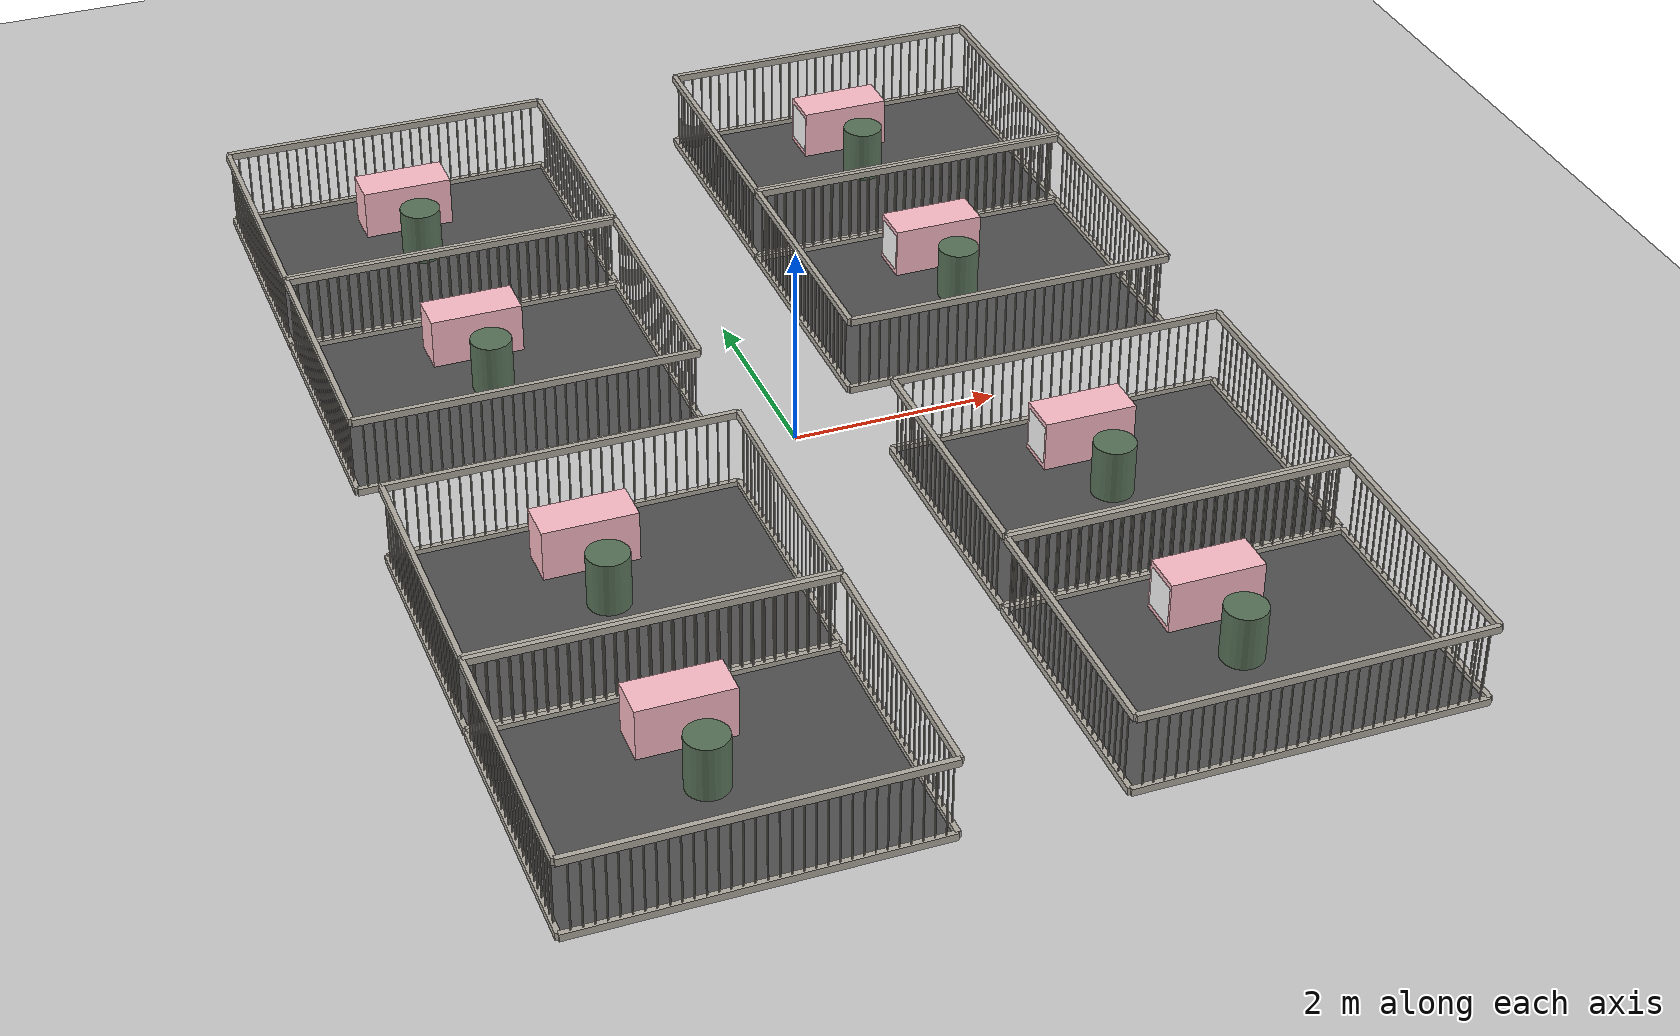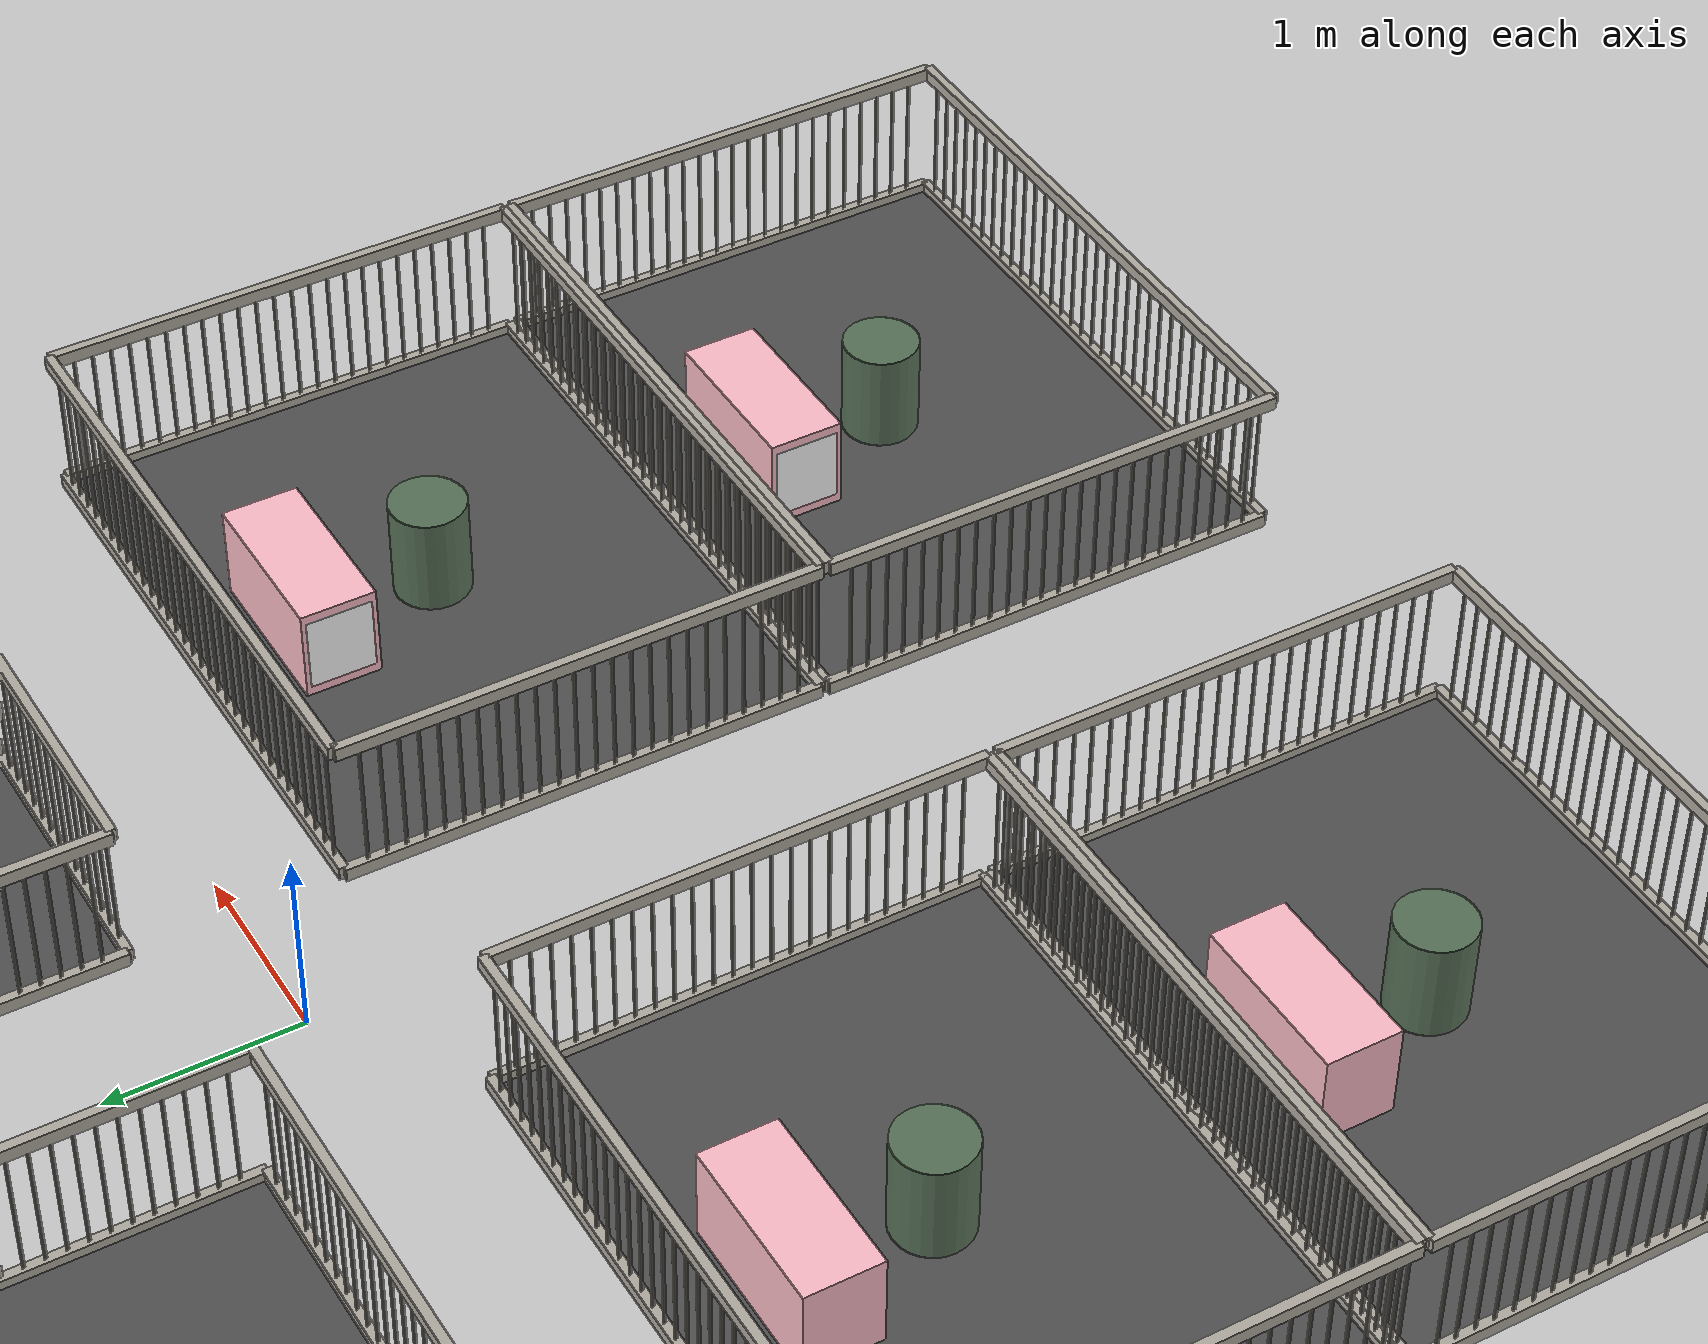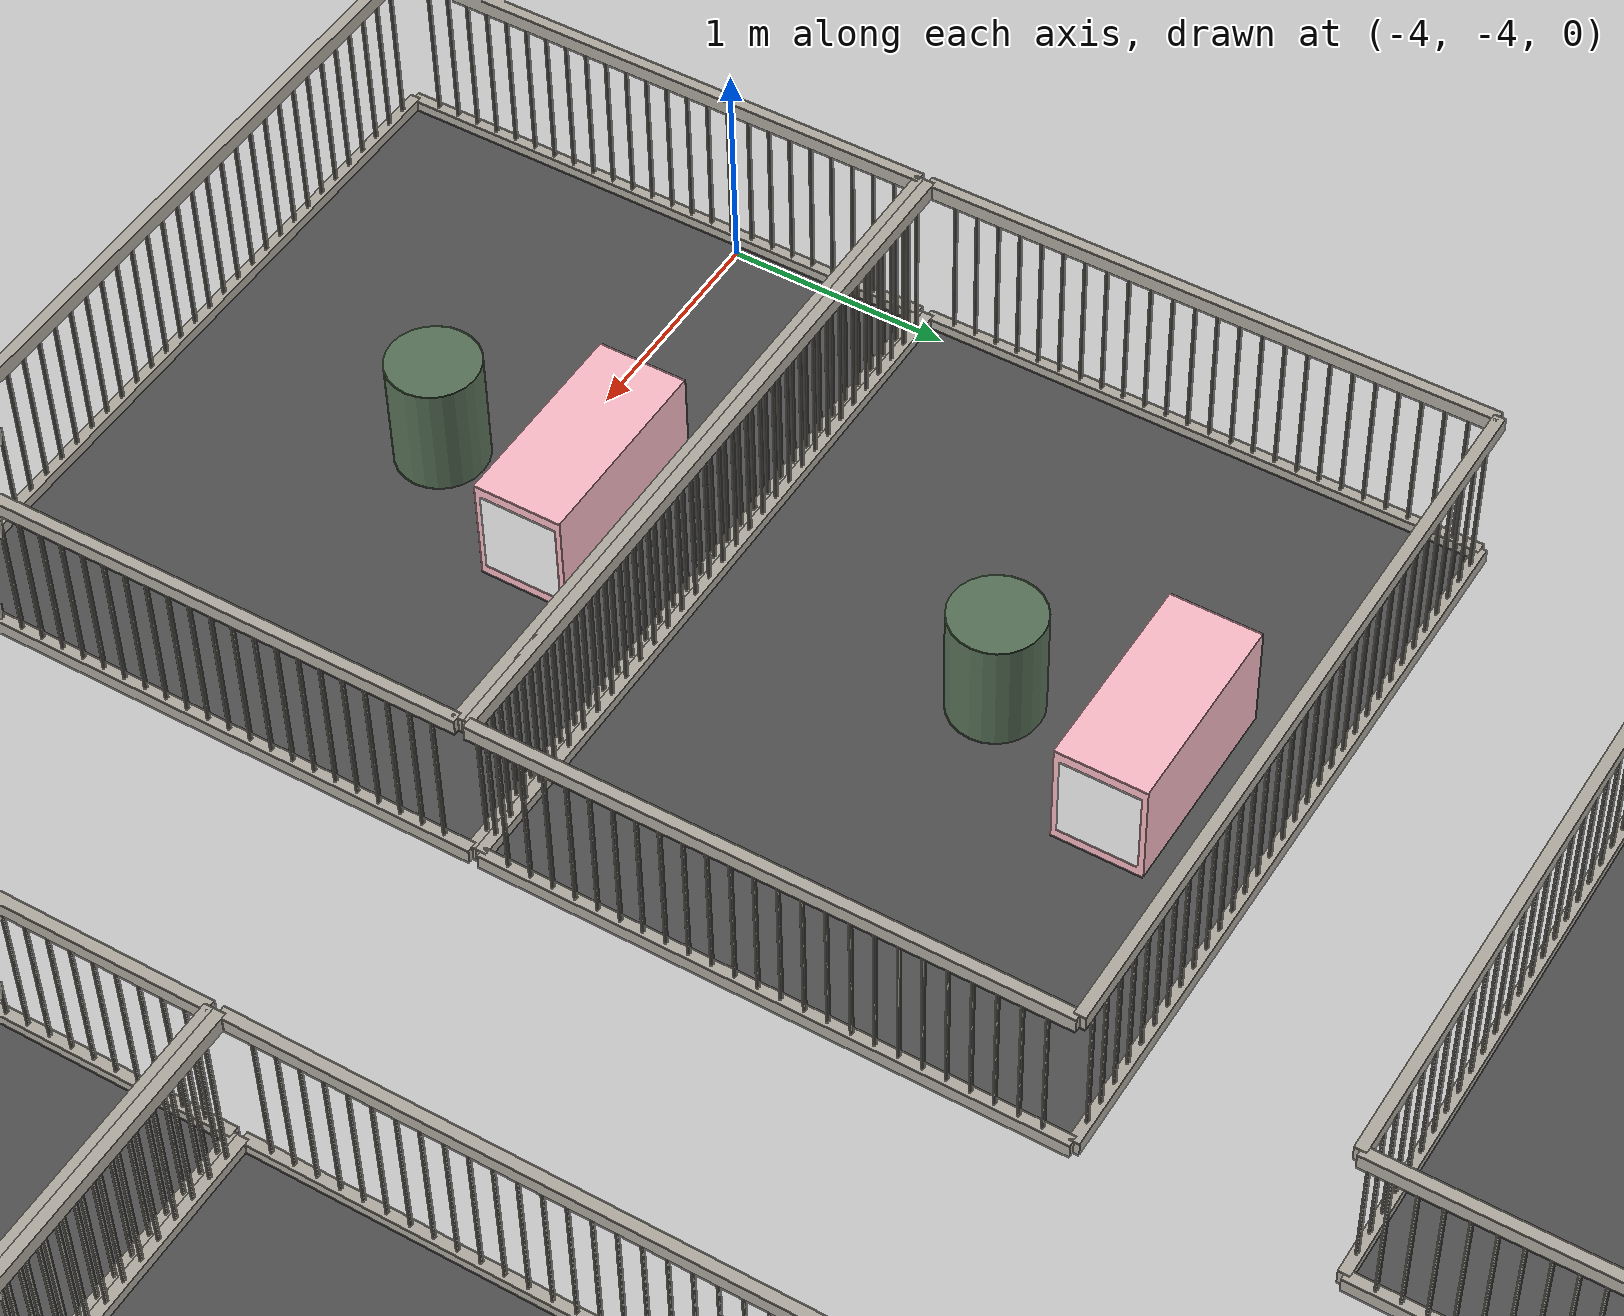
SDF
<?xml version='1.0' encoding='utf-8'?>
<sdf version="1.9">
  <world name="pig_pen_8units_world">
    <gravity>0 0 -9.8</gravity>
    <magnetic_field>0 0 0</magnetic_field>
    <atmosphere type="adiabatic" />
    <plugin filename="gz-sim-physics-system" name="gz::sim::systems::Physics" />
    <plugin filename="gz-sim-sensors-system" name="gz::sim::systems::Sensors">
      <render_engine>ogre2</render_engine>
    </plugin>
    <plugin filename="gz-sim-user-commands-system" name="gz::sim::systems::UserCommands" />
    <plugin filename="gz-sim-scene-broadcaster-system" name="gz::sim::systems::SceneBroadcaster" />
    <light name="sun" type="directional">
      <cast_shadows>true</cast_shadows>
      <pose>0 0 10 0 0 0</pose>
      <diffuse>0.9 0.9 0.9 1</diffuse>
      <specular>0.2 0.2 0.2 1</specular>
      <direction>-0.4 0.1 -1</direction>
    </light>
    <model name="ground_plane">
      <static>true</static>
      <link name="link">
        <collision name="collision">
          <geometry>
            <plane>
              <normal>0 0 1</normal>
              <size>20 20</size>
            </plane>
          </geometry>
          <surface>
            <friction>
              <ode>
                <mu>1.0</mu>
                <mu2>1.0</mu2>
              </ode>
            </friction>
          </surface>
        </collision>
        <visual name="visual">
          <geometry>
            <plane>
              <normal>0 0 1</normal>
              <size>20 20</size>
            </plane>
          </geometry>
          <material>
            <ambient>0.8 0.8 0.8 1</ambient>
            <diffuse>0.8 0.8 0.8 1</diffuse>
            <specular>0.2 0.2 0.2 1</specular>
          </material>
        </visual>
      </link>
    </model>

    <model name="pen1">
      <pose>-2.4 4.405 0 0 0 0</pose>
      <static>true</static>

      <link name="floor">
        <pose>0 0 0.01 0 0 0</pose>
        <collision name="collision"><geometry><box><size>3.30 2.55 0.02</size></box></geometry></collision>
        <visual name="visual"><geometry><box><size>3.30 2.55 0.02</size></box></geometry><material><ambient>0.25 0.25 0.25 1</ambient><diffuse>0.32 0.32 0.32 1</diffuse><specular>0.05 0.05 0.05 1</specular></material></visual>
      </link>

      <!-- pen1 左牆（長邊3.30m，欄杆化） -->
      <link name="left_wall">
        <pose>0 1.275 0.415 0 0 0</pose>
        <collision name="top_rail_col"><pose>0 0 0.38 0 0 0</pose><geometry><box><size>3.30 0.05 0.07</size></box></geometry></collision>
        <visual name="top_rail_vis"><pose>0 0 0.38 0 0 0</pose><geometry><box><size>3.30 0.05 0.07</size></box></geometry><material><ambient>0.70 0.68 0.64 1</ambient><diffuse>0.70 0.68 0.64 1</diffuse></material></visual>
        <collision name="bottom_rail_col"><pose>0 0 -0.38 0 0 0</pose><geometry><box><size>3.30 0.05 0.07</size></box></geometry></collision>
        <visual name="bottom_rail_vis"><pose>0 0 -0.38 0 0 0</pose><geometry><box><size>3.30 0.05 0.07</size></box></geometry><material><ambient>0.70 0.68 0.64 1</ambient><diffuse>0.70 0.68 0.64 1</diffuse></material></visual>
          <collision name="bar_01_col"><pose>-1.55 0 0 0 0 0</pose><geometry><cylinder><radius>0.0075</radius><length>0.69</length></cylinder></geometry></collision>
          <visual name="bar_01_vis"><pose>-1.55 0 0 0 0 0</pose><geometry><cylinder><radius>0.0075</radius><length>0.69</length></cylinder></geometry><material><ambient>0.70 0.68 0.64 1</ambient><diffuse>0.70 0.68 0.64 1</diffuse></material></visual>
          <collision name="bar_02_col"><pose>-1.45 0 0 0 0 0</pose><geometry><cylinder><radius>0.0075</radius><length>0.69</length></cylinder></geometry></collision>
          <visual name="bar_02_vis"><pose>-1.45 0 0 0 0 0</pose><geometry><cylinder><radius>0.0075</radius><length>0.69</length></cylinder></geometry><material><ambient>0.70 0.68 0.64 1</ambient><diffuse>0.70 0.68 0.64 1</diffuse></material></visual>
          <collision name="bar_03_col"><pose>-1.35 0 0 0 0 0</pose><geometry><cylinder><radius>0.0075</radius><length>0.69</length></cylinder></geometry></collision>
          <visual name="bar_03_vis"><pose>-1.35 0 0 0 0 0</pose><geometry><cylinder><radius>0.0075</radius><length>0.69</length></cylinder></geometry><material><ambient>0.70 0.68 0.64 1</ambient><diffuse>0.70 0.68 0.64 1</diffuse></material></visual>
          <collision name="bar_04_col"><pose>-1.25 0 0 0 0 0</pose><geometry><cylinder><radius>0.0075</radius><length>0.69</length></cylinder></geometry></collision>
          <visual name="bar_04_vis"><pose>-1.25 0 0 0 0 0</pose><geometry><cylinder><radius>0.0075</radius><length>0.69</length></cylinder></geometry><material><ambient>0.70 0.68 0.64 1</ambient><diffuse>0.70 0.68 0.64 1</diffuse></material></visual>
          <collision name="bar_05_col"><pose>-1.15 0 0 0 0 0</pose><geometry><cylinder><radius>0.0075</radius><length>0.69</length></cylinder></geometry></collision>
          <visual name="bar_05_vis"><pose>-1.15 0 0 0 0 0</pose><geometry><cylinder><radius>0.0075</radius><length>0.69</length></cylinder></geometry><material><ambient>0.70 0.68 0.64 1</ambient><diffuse>0.70 0.68 0.64 1</diffuse></material></visual>
          <collision name="bar_06_col"><pose>-1.05 0 0 0 0 0</pose><geometry><cylinder><radius>0.0075</radius><length>0.69</length></cylinder></geometry></collision>
          <visual name="bar_06_vis"><pose>-1.05 0 0 0 0 0</pose><geometry><cylinder><radius>0.0075</radius><length>0.69</length></cylinder></geometry><material><ambient>0.70 0.68 0.64 1</ambient><diffuse>0.70 0.68 0.64 1</diffuse></material></visual>
          <collision name="bar_07_col"><pose>-0.95 0 0 0 0 0</pose><geometry><cylinder><radius>0.0075</radius><length>0.69</length></cylinder></geometry></collision>
          <visual name="bar_07_vis"><pose>-0.95 0 0 0 0 0</pose><geometry><cylinder><radius>0.0075</radius><length>0.69</length></cylinder></geometry><material><ambient>0.70 0.68 0.64 1</ambient><diffuse>0.70 0.68 0.64 1</diffuse></material></visual>
          <collision name="bar_08_col"><pose>-0.85 0 0 0 0 0</pose><geometry><cylinder><radius>0.0075</radius><length>0.69</length></cylinder></geometry></collision>
          <visual name="bar_08_vis"><pose>-0.85 0 0 0 0 0</pose><geometry><cylinder><radius>0.0075</radius><length>0.69</length></cylinder></geometry><material><ambient>0.70 0.68 0.64 1</ambient><diffuse>0.70 0.68 0.64 1</diffuse></material></visual>
          <collision name="bar_09_col"><pose>-0.75 0 0 0 0 0</pose><geometry><cylinder><radius>0.0075</radius><length>0.69</length></cylinder></geometry></collision>
          <visual name="bar_09_vis"><pose>-0.75 0 0 0 0 0</pose><geometry><cylinder><radius>0.0075</radius><length>0.69</length></cylinder></geometry><material><ambient>0.70 0.68 0.64 1</ambient><diffuse>0.70 0.68 0.64 1</diffuse></material></visual>
          <collision name="bar_10_col"><pose>-0.65 0 0 0 0 0</pose><geometry><cylinder><radius>0.0075</radius><length>0.69</length></cylinder></geometry></collision>
          <visual name="bar_10_vis"><pose>-0.65 0 0 0 0 0</pose><geometry><cylinder><radius>0.0075</radius><length>0.69</length></cylinder></geometry><material><ambient>0.70 0.68 0.64 1</ambient><diffuse>0.70 0.68 0.64 1</diffuse></material></visual>
          <collision name="bar_11_col"><pose>-0.55 0 0 0 0 0</pose><geometry><cylinder><radius>0.0075</radius><length>0.69</length></cylinder></geometry></collision>
          <visual name="bar_11_vis"><pose>-0.55 0 0 0 0 0</pose><geometry><cylinder><radius>0.0075</radius><length>0.69</length></cylinder></geometry><material><ambient>0.70 0.68 0.64 1</ambient><diffuse>0.70 0.68 0.64 1</diffuse></material></visual>
          <collision name="bar_12_col"><pose>-0.45 0 0 0 0 0</pose><geometry><cylinder><radius>0.0075</radius><length>0.69</length></cylinder></geometry></collision>
          <visual name="bar_12_vis"><pose>-0.45 0 0 0 0 0</pose><geometry><cylinder><radius>0.0075</radius><length>0.69</length></cylinder></geometry><material><ambient>0.70 0.68 0.64 1</ambient><diffuse>0.70 0.68 0.64 1</diffuse></material></visual>
          <collision name="bar_13_col"><pose>-0.35 0 0 0 0 0</pose><geometry><cylinder><radius>0.0075</radius><length>0.69</length></cylinder></geometry></collision>
          <visual name="bar_13_vis"><pose>-0.35 0 0 0 0 0</pose><geometry><cylinder><radius>0.0075</radius><length>0.69</length></cylinder></geometry><material><ambient>0.70 0.68 0.64 1</ambient><diffuse>0.70 0.68 0.64 1</diffuse></material></visual>
          <collision name="bar_14_col"><pose>-0.25 0 0 0 0 0</pose><geometry><cylinder><radius>0.0075</radius><length>0.69</length></cylinder></geometry></collision>
          <visual name="bar_14_vis"><pose>-0.25 0 0 0 0 0</pose><geometry><cylinder><radius>0.0075</radius><length>0.69</length></cylinder></geometry><material><ambient>0.70 0.68 0.64 1</ambient><diffuse>0.70 0.68 0.64 1</diffuse></material></visual>
          <collision name="bar_15_col"><pose>-0.15 0 0 0 0 0</pose><geometry><cylinder><radius>0.0075</radius><length>0.69</length></cylinder></geometry></collision>
          <visual name="bar_15_vis"><pose>-0.15 0 0 0 0 0</pose><geometry><cylinder><radius>0.0075</radius><length>0.69</length></cylinder></geometry><material><ambient>0.70 0.68 0.64 1</ambient><diffuse>0.70 0.68 0.64 1</diffuse></material></visual>
          <collision name="bar_16_col"><pose>-0.05 0 0 0 0 0</pose><geometry><cylinder><radius>0.0075</radius><length>0.69</length></cylinder></geometry></collision>
          <visual name="bar_16_vis"><pose>-0.05 0 0 0 0 0</pose><geometry><cylinder><radius>0.0075</radius><length>0.69</length></cylinder></geometry><material><ambient>0.70 0.68 0.64 1</ambient><diffuse>0.70 0.68 0.64 1</diffuse></material></visual>
          <collision name="bar_17_col"><pose>0.05 0 0 0 0 0</pose><geometry><cylinder><radius>0.0075</radius><length>0.69</length></cylinder></geometry></collision>
          <visual name="bar_17_vis"><pose>0.05 0 0 0 0 0</pose><geometry><cylinder><radius>0.0075</radius><length>0.69</length></cylinder></geometry><material><ambient>0.70 0.68 0.64 1</ambient><diffuse>0.70 0.68 0.64 1</diffuse></material></visual>
          <collision name="bar_18_col"><pose>0.15 0 0 0 0 0</pose><geometry><cylinder><radius>0.0075</radius><length>0.69</length></cylinder></geometry></collision>
          <visual name="bar_18_vis"><pose>0.15 0 0 0 0 0</pose><geometry><cylinder><radius>0.0075</radius><length>0.69</length></cylinder></geometry><material><ambient>0.70 0.68 0.64 1</ambient><diffuse>0.70 0.68 0.64 1</diffuse></material></visual>
          <collision name="bar_19_col"><pose>0.25 0 0 0 0 0</pose><geometry><cylinder><radius>0.0075</radius><length>0.69</length></cylinder></geometry></collision>
          <visual name="bar_19_vis"><pose>0.25 0 0 0 0 0</pose><geometry><cylinder><radius>0.0075</radius><length>0.69</length></cylinder></geometry><material><ambient>0.70 0.68 0.64 1</ambient><diffuse>0.70 0.68 0.64 1</diffuse></material></visual>
          <collision name="bar_20_col"><pose>0.35 0 0 0 0 0</pose><geometry><cylinder><radius>0.0075</radius><length>0.69</length></cylinder></geometry></collision>
          <visual name="bar_20_vis"><pose>0.35 0 0 0 0 0</pose><geometry><cylinder><radius>0.0075</radius><length>0.69</length></cylinder></geometry><material><ambient>0.70 0.68 0.64 1</ambient><diffuse>0.70 0.68 0.64 1</diffuse></material></visual>
          <collision name="bar_21_col"><pose>0.45 0 0 0 0 0</pose><geometry><cylinder><radius>0.0075</radius><length>0.69</length></cylinder></geometry></collision>
          <visual name="bar_21_vis"><pose>0.45 0 0 0 0 0</pose><geometry><cylinder><radius>0.0075</radius><length>0.69</length></cylinder></geometry><material><ambient>0.70 0.68 0.64 1</ambient><diffuse>0.70 0.68 0.64 1</diffuse></material></visual>
          <collision name="bar_22_col"><pose>0.55 0 0 0 0 0</pose><geometry><cylinder><radius>0.0075</radius><length>0.69</length></cylinder></geometry></collision>
          <visual name="bar_22_vis"><pose>0.55 0 0 0 0 0</pose><geometry><cylinder><radius>0.0075</radius><length>0.69</length></cylinder></geometry><material><ambient>0.70 0.68 0.64 1</ambient><diffuse>0.70 0.68 0.64 1</diffuse></material></visual>
          <collision name="bar_23_col"><pose>0.65 0 0 0 0 0</pose><geometry><cylinder><radius>0.0075</radius><length>0.69</length></cylinder></geometry></collision>
          <visual name="bar_23_vis"><pose>0.65 0 0 0 0 0</pose><geometry><cylinder><radius>0.0075</radius><length>0.69</length></cylinder></geometry><material><ambient>0.70 0.68 0.64 1</ambient><diffuse>0.70 0.68 0.64 1</diffuse></material></visual>
          <collision name="bar_24_col"><pose>0.75 0 0 0 0 0</pose><geometry><cylinder><radius>0.0075</radius><length>0.69</length></cylinder></geometry></collision>
          <visual name="bar_24_vis"><pose>0.75 0 0 0 0 0</pose><geometry><cylinder><radius>0.0075</radius><length>0.69</length></cylinder></geometry><material><ambient>0.70 0.68 0.64 1</ambient><diffuse>0.70 0.68 0.64 1</diffuse></material></visual>
          <collision name="bar_25_col"><pose>0.85 0 0 0 0 0</pose><geometry><cylinder><radius>0.0075</radius><length>0.69</length></cylinder></geometry></collision>
          <visual name="bar_25_vis"><pose>0.85 0 0 0 0 0</pose><geometry><cylinder><radius>0.0075</radius><length>0.69</length></cylinder></geometry><material><ambient>0.70 0.68 0.64 1</ambient><diffuse>0.70 0.68 0.64 1</diffuse></material></visual>
          <collision name="bar_26_col"><pose>0.95 0 0 0 0 0</pose><geometry><cylinder><radius>0.0075</radius><length>0.69</length></cylinder></geometry></collision>
          <visual name="bar_26_vis"><pose>0.95 0 0 0 0 0</pose><geometry><cylinder><radius>0.0075</radius><length>0.69</length></cylinder></geometry><material><ambient>0.70 0.68 0.64 1</ambient><diffuse>0.70 0.68 0.64 1</diffuse></material></visual>
          <collision name="bar_27_col"><pose>1.05 0 0 0 0 0</pose><geometry><cylinder><radius>0.0075</radius><length>0.69</length></cylinder></geometry></collision>
          <visual name="bar_27_vis"><pose>1.05 0 0 0 0 0</pose><geometry><cylinder><radius>0.0075</radius><length>0.69</length></cylinder></geometry><material><ambient>0.70 0.68 0.64 1</ambient><diffuse>0.70 0.68 0.64 1</diffuse></material></visual>
          <collision name="bar_28_col"><pose>1.15 0 0 0 0 0</pose><geometry><cylinder><radius>0.0075</radius><length>0.69</length></cylinder></geometry></collision>
          <visual name="bar_28_vis"><pose>1.15 0 0 0 0 0</pose><geometry><cylinder><radius>0.0075</radius><length>0.69</length></cylinder></geometry><material><ambient>0.70 0.68 0.64 1</ambient><diffuse>0.70 0.68 0.64 1</diffuse></material></visual>
          <collision name="bar_29_col"><pose>1.25 0 0 0 0 0</pose><geometry><cylinder><radius>0.0075</radius><length>0.69</length></cylinder></geometry></collision>
          <visual name="bar_29_vis"><pose>1.25 0 0 0 0 0</pose><geometry><cylinder><radius>0.0075</radius><length>0.69</length></cylinder></geometry><material><ambient>0.70 0.68 0.64 1</ambient><diffuse>0.70 0.68 0.64 1</diffuse></material></visual>
          <collision name="bar_30_col"><pose>1.35 0 0 0 0 0</pose><geometry><cylinder><radius>0.0075</radius><length>0.69</length></cylinder></geometry></collision>
          <visual name="bar_30_vis"><pose>1.35 0 0 0 0 0</pose><geometry><cylinder><radius>0.0075</radius><length>0.69</length></cylinder></geometry><material><ambient>0.70 0.68 0.64 1</ambient><diffuse>0.70 0.68 0.64 1</diffuse></material></visual>
          <collision name="bar_31_col"><pose>1.45 0 0 0 0 0</pose><geometry><cylinder><radius>0.0075</radius><length>0.69</length></cylinder></geometry></collision>
          <visual name="bar_31_vis"><pose>1.45 0 0 0 0 0</pose><geometry><cylinder><radius>0.0075</radius><length>0.69</length></cylinder></geometry><material><ambient>0.70 0.68 0.64 1</ambient><diffuse>0.70 0.68 0.64 1</diffuse></material></visual>
          <collision name="bar_32_col"><pose>1.55 0 0 0 0 0</pose><geometry><cylinder><radius>0.0075</radius><length>0.69</length></cylinder></geometry></collision>
          <visual name="bar_32_vis"><pose>1.55 0 0 0 0 0</pose><geometry><cylinder><radius>0.0075</radius><length>0.69</length></cylinder></geometry><material><ambient>0.70 0.68 0.64 1</ambient><diffuse>0.70 0.68 0.64 1</diffuse></material></visual>
      </link>
      <!-- pen1 右牆（長邊3.30m，欄杆化） -->
      <link name="right_wall">
        <pose>0 -1.275 0.415 0 0 0</pose>
        <collision name="top_rail_col"><pose>0 0 0.38 0 0 0</pose><geometry><box><size>3.30 0.05 0.07</size></box></geometry></collision>
        <visual name="top_rail_vis"><pose>0 0 0.38 0 0 0</pose><geometry><box><size>3.30 0.05 0.07</size></box></geometry><material><ambient>0.70 0.68 0.64 1</ambient><diffuse>0.70 0.68 0.64 1</diffuse></material></visual>
        <collision name="bottom_rail_col"><pose>0 0 -0.38 0 0 0</pose><geometry><box><size>3.30 0.05 0.07</size></box></geometry></collision>
        <visual name="bottom_rail_vis"><pose>0 0 -0.38 0 0 0</pose><geometry><box><size>3.30 0.05 0.07</size></box></geometry><material><ambient>0.70 0.68 0.64 1</ambient><diffuse>0.70 0.68 0.64 1</diffuse></material></visual>
          <collision name="bar_01_col"><pose>-1.55 0 0 0 0 0</pose><geometry><cylinder><radius>0.0075</radius><length>0.69</length></cylinder></geometry></collision>
          <visual name="bar_01_vis"><pose>-1.55 0 0 0 0 0</pose><geometry><cylinder><radius>0.0075</radius><length>0.69</length></cylinder></geometry><material><ambient>0.70 0.68 0.64 1</ambient><diffuse>0.70 0.68 0.64 1</diffuse></material></visual>
          <collision name="bar_02_col"><pose>-1.45 0 0 0 0 0</pose><geometry><cylinder><radius>0.0075</radius><length>0.69</length></cylinder></geometry></collision>
          <visual name="bar_02_vis"><pose>-1.45 0 0 0 0 0</pose><geometry><cylinder><radius>0.0075</radius><length>0.69</length></cylinder></geometry><material><ambient>0.70 0.68 0.64 1</ambient><diffuse>0.70 0.68 0.64 1</diffuse></material></visual>
          <collision name="bar_03_col"><pose>-1.35 0 0 0 0 0</pose><geometry><cylinder><radius>0.0075</radius><length>0.69</length></cylinder></geometry></collision>
          <visual name="bar_03_vis"><pose>-1.35 0 0 0 0 0</pose><geometry><cylinder><radius>0.0075</radius><length>0.69</length></cylinder></geometry><material><ambient>0.70 0.68 0.64 1</ambient><diffuse>0.70 0.68 0.64 1</diffuse></material></visual>
          <collision name="bar_04_col"><pose>-1.25 0 0 0 0 0</pose><geometry><cylinder><radius>0.0075</radius><length>0.69</length></cylinder></geometry></collision>
          <visual name="bar_04_vis"><pose>-1.25 0 0 0 0 0</pose><geometry><cylinder><radius>0.0075</radius><length>0.69</length></cylinder></geometry><material><ambient>0.70 0.68 0.64 1</ambient><diffuse>0.70 0.68 0.64 1</diffuse></material></visual>
          <collision name="bar_05_col"><pose>-1.15 0 0 0 0 0</pose><geometry><cylinder><radius>0.0075</radius><length>0.69</length></cylinder></geometry></collision>
          <visual name="bar_05_vis"><pose>-1.15 0 0 0 0 0</pose><geometry><cylinder><radius>0.0075</radius><length>0.69</length></cylinder></geometry><material><ambient>0.70 0.68 0.64 1</ambient><diffuse>0.70 0.68 0.64 1</diffuse></material></visual>
          <collision name="bar_06_col"><pose>-1.05 0 0 0 0 0</pose><geometry><cylinder><radius>0.0075</radius><length>0.69</length></cylinder></geometry></collision>
          <visual name="bar_06_vis"><pose>-1.05 0 0 0 0 0</pose><geometry><cylinder><radius>0.0075</radius><length>0.69</length></cylinder></geometry><material><ambient>0.70 0.68 0.64 1</ambient><diffuse>0.70 0.68 0.64 1</diffuse></material></visual>
          <collision name="bar_07_col"><pose>-0.95 0 0 0 0 0</pose><geometry><cylinder><radius>0.0075</radius><length>0.69</length></cylinder></geometry></collision>
          <visual name="bar_07_vis"><pose>-0.95 0 0 0 0 0</pose><geometry><cylinder><radius>0.0075</radius><length>0.69</length></cylinder></geometry><material><ambient>0.70 0.68 0.64 1</ambient><diffuse>0.70 0.68 0.64 1</diffuse></material></visual>
          <collision name="bar_08_col"><pose>-0.85 0 0 0 0 0</pose><geometry><cylinder><radius>0.0075</radius><length>0.69</length></cylinder></geometry></collision>
          <visual name="bar_08_vis"><pose>-0.85 0 0 0 0 0</pose><geometry><cylinder><radius>0.0075</radius><length>0.69</length></cylinder></geometry><material><ambient>0.70 0.68 0.64 1</ambient><diffuse>0.70 0.68 0.64 1</diffuse></material></visual>
          <collision name="bar_09_col"><pose>-0.75 0 0 0 0 0</pose><geometry><cylinder><radius>0.0075</radius><length>0.69</length></cylinder></geometry></collision>
          <visual name="bar_09_vis"><pose>-0.75 0 0 0 0 0</pose><geometry><cylinder><radius>0.0075</radius><length>0.69</length></cylinder></geometry><material><ambient>0.70 0.68 0.64 1</ambient><diffuse>0.70 0.68 0.64 1</diffuse></material></visual>
          <collision name="bar_10_col"><pose>-0.65 0 0 0 0 0</pose><geometry><cylinder><radius>0.0075</radius><length>0.69</length></cylinder></geometry></collision>
          <visual name="bar_10_vis"><pose>-0.65 0 0 0 0 0</pose><geometry><cylinder><radius>0.0075</radius><length>0.69</length></cylinder></geometry><material><ambient>0.70 0.68 0.64 1</ambient><diffuse>0.70 0.68 0.64 1</diffuse></material></visual>
          <collision name="bar_11_col"><pose>-0.55 0 0 0 0 0</pose><geometry><cylinder><radius>0.0075</radius><length>0.69</length></cylinder></geometry></collision>
          <visual name="bar_11_vis"><pose>-0.55 0 0 0 0 0</pose><geometry><cylinder><radius>0.0075</radius><length>0.69</length></cylinder></geometry><material><ambient>0.70 0.68 0.64 1</ambient><diffuse>0.70 0.68 0.64 1</diffuse></material></visual>
          <collision name="bar_12_col"><pose>-0.45 0 0 0 0 0</pose><geometry><cylinder><radius>0.0075</radius><length>0.69</length></cylinder></geometry></collision>
          <visual name="bar_12_vis"><pose>-0.45 0 0 0 0 0</pose><geometry><cylinder><radius>0.0075</radius><length>0.69</length></cylinder></geometry><material><ambient>0.70 0.68 0.64 1</ambient><diffuse>0.70 0.68 0.64 1</diffuse></material></visual>
          <collision name="bar_13_col"><pose>-0.35 0 0 0 0 0</pose><geometry><cylinder><radius>0.0075</radius><length>0.69</length></cylinder></geometry></collision>
          <visual name="bar_13_vis"><pose>-0.35 0 0 0 0 0</pose><geometry><cylinder><radius>0.0075</radius><length>0.69</length></cylinder></geometry><material><ambient>0.70 0.68 0.64 1</ambient><diffuse>0.70 0.68 0.64 1</diffuse></material></visual>
          <collision name="bar_14_col"><pose>-0.25 0 0 0 0 0</pose><geometry><cylinder><radius>0.0075</radius><length>0.69</length></cylinder></geometry></collision>
          <visual name="bar_14_vis"><pose>-0.25 0 0 0 0 0</pose><geometry><cylinder><radius>0.0075</radius><length>0.69</length></cylinder></geometry><material><ambient>0.70 0.68 0.64 1</ambient><diffuse>0.70 0.68 0.64 1</diffuse></material></visual>
          <collision name="bar_15_col"><pose>-0.15 0 0 0 0 0</pose><geometry><cylinder><radius>0.0075</radius><length>0.69</length></cylinder></geometry></collision>
          <visual name="bar_15_vis"><pose>-0.15 0 0 0 0 0</pose><geometry><cylinder><radius>0.0075</radius><length>0.69</length></cylinder></geometry><material><ambient>0.70 0.68 0.64 1</ambient><diffuse>0.70 0.68 0.64 1</diffuse></material></visual>
          <collision name="bar_16_col"><pose>-0.05 0 0 0 0 0</pose><geometry><cylinder><radius>0.0075</radius><length>0.69</length></cylinder></geometry></collision>
          <visual name="bar_16_vis"><pose>-0.05 0 0 0 0 0</pose><geometry><cylinder><radius>0.0075</radius><length>0.69</length></cylinder></geometry><material><ambient>0.70 0.68 0.64 1</ambient><diffuse>0.70 0.68 0.64 1</diffuse></material></visual>
          <collision name="bar_17_col"><pose>0.05 0 0 0 0 0</pose><geometry><cylinder><radius>0.0075</radius><length>0.69</length></cylinder></geometry></collision>
          <visual name="bar_17_vis"><pose>0.05 0 0 0 0 0</pose><geometry><cylinder><radius>0.0075</radius><length>0.69</length></cylinder></geometry><material><ambient>0.70 0.68 0.64 1</ambient><diffuse>0.70 0.68 0.64 1</diffuse></material></visual>
          <collision name="bar_18_col"><pose>0.15 0 0 0 0 0</pose><geometry><cylinder><radius>0.0075</radius><length>0.69</length></cylinder></geometry></collision>
          <visual name="bar_18_vis"><pose>0.15 0 0 0 0 0</pose><geometry><cylinder><radius>0.0075</radius><length>0.69</length></cylinder></geometry><material><ambient>0.70 0.68 0.64 1</ambient><diffuse>0.70 0.68 0.64 1</diffuse></material></visual>
          <collision name="bar_19_col"><pose>0.25 0 0 0 0 0</pose><geometry><cylinder><radius>0.0075</radius><length>0.69</length></cylinder></geometry></collision>
          <visual name="bar_19_vis"><pose>0.25 0 0 0 0 0</pose><geometry><cylinder><radius>0.0075</radius><length>0.69</length></cylinder></geometry><material><ambient>0.70 0.68 0.64 1</ambient><diffuse>0.70 0.68 0.64 1</diffuse></material></visual>
          <collision name="bar_20_col"><pose>0.35 0 0 0 0 0</pose><geometry><cylinder><radius>0.0075</radius><length>0.69</length></cylinder></geometry></collision>
          <visual name="bar_20_vis"><pose>0.35 0 0 0 0 0</pose><geometry><cylinder><radius>0.0075</radius><length>0.69</length></cylinder></geometry><material><ambient>0.70 0.68 0.64 1</ambient><diffuse>0.70 0.68 0.64 1</diffuse></material></visual>
          <collision name="bar_21_col"><pose>0.45 0 0 0 0 0</pose><geometry><cylinder><radius>0.0075</radius><length>0.69</length></cylinder></geometry></collision>
          <visual name="bar_21_vis"><pose>0.45 0 0 0 0 0</pose><geometry><cylinder><radius>0.0075</radius><length>0.69</length></cylinder></geometry><material><ambient>0.70 0.68 0.64 1</ambient><diffuse>0.70 0.68 0.64 1</diffuse></material></visual>
          <collision name="bar_22_col"><pose>0.55 0 0 0 0 0</pose><geometry><cylinder><radius>0.0075</radius><length>0.69</length></cylinder></geometry></collision>
          <visual name="bar_22_vis"><pose>0.55 0 0 0 0 0</pose><geometry><cylinder><radius>0.0075</radius><length>0.69</length></cylinder></geometry><material><ambient>0.70 0.68 0.64 1</ambient><diffuse>0.70 0.68 0.64 1</diffuse></material></visual>
          <collision name="bar_23_col"><pose>0.65 0 0 0 0 0</pose><geometry><cylinder><radius>0.0075</radius><length>0.69</length></cylinder></geometry></collision>
          <visual name="bar_23_vis"><pose>0.65 0 0 0 0 0</pose><geometry><cylinder><radius>0.0075</radius><length>0.69</length></cylinder></geometry><material><ambient>0.70 0.68 0.64 1</ambient><diffuse>0.70 0.68 0.64 1</diffuse></material></visual>
          <collision name="bar_24_col"><pose>0.75 0 0 0 0 0</pose><geometry><cylinder><radius>0.0075</radius><length>0.69</length></cylinder></geometry></collision>
          <visual name="bar_24_vis"><pose>0.75 0 0 0 0 0</pose><geometry><cylinder><radius>0.0075</radius><length>0.69</length></cylinder></geometry><material><ambient>0.70 0.68 0.64 1</ambient><diffuse>0.70 0.68 0.64 1</diffuse></material></visual>
          <collision name="bar_25_col"><pose>0.85 0 0 0 0 0</pose><geometry><cylinder><radius>0.0075</radius><length>0.69</length></cylinder></geometry></collision>
          <visual name="bar_25_vis"><pose>0.85 0 0 0 0 0</pose><geometry><cylinder><radius>0.0075</radius><length>0.69</length></cylinder></geometry><material><ambient>0.70 0.68 0.64 1</ambient><diffuse>0.70 0.68 0.64 1</diffuse></material></visual>
          <collision name="bar_26_col"><pose>0.95 0 0 0 0 0</pose><geometry><cylinder><radius>0.0075</radius><length>0.69</length></cylinder></geometry></collision>
          <visual name="bar_26_vis"><pose>0.95 0 0 0 0 0</pose><geometry><cylinder><radius>0.0075</radius><length>0.69</length></cylinder></geometry><material><ambient>0.70 0.68 0.64 1</ambient><diffuse>0.70 0.68 0.64 1</diffuse></material></visual>
          <collision name="bar_27_col"><pose>1.05 0 0 0 0 0</pose><geometry><cylinder><radius>0.0075</radius><length>0.69</length></cylinder></geometry></collision>
          <visual name="bar_27_vis"><pose>1.05 0 0 0 0 0</pose><geometry><cylinder><radius>0.0075</radius><length>0.69</length></cylinder></geometry><material><ambient>0.70 0.68 0.64 1</ambient><diffuse>0.70 0.68 0.64 1</diffuse></material></visual>
          <collision name="bar_28_col"><pose>1.15 0 0 0 0 0</pose><geometry><cylinder><radius>0.0075</radius><length>0.69</length></cylinder></geometry></collision>
          <visual name="bar_28_vis"><pose>1.15 0 0 0 0 0</pose><geometry><cylinder><radius>0.0075</radius><length>0.69</length></cylinder></geometry><material><ambient>0.70 0.68 0.64 1</ambient><diffuse>0.70 0.68 0.64 1</diffuse></material></visual>
          <collision name="bar_29_col"><pose>1.25 0 0 0 0 0</pose><geometry><cylinder><radius>0.0075</radius><length>0.69</length></cylinder></geometry></collision>
          <visual name="bar_29_vis"><pose>1.25 0 0 0 0 0</pose><geometry><cylinder><radius>0.0075</radius><length>0.69</length></cylinder></geometry><material><ambient>0.70 0.68 0.64 1</ambient><diffuse>0.70 0.68 0.64 1</diffuse></material></visual>
          <collision name="bar_30_col"><pose>1.35 0 0 0 0 0</pose><geometry><cylinder><radius>0.0075</radius><length>0.69</length></cylinder></geometry></collision>
          <visual name="bar_30_vis"><pose>1.35 0 0 0 0 0</pose><geometry><cylinder><radius>0.0075</radius><length>0.69</length></cylinder></geometry><material><ambient>0.70 0.68 0.64 1</ambient><diffuse>0.70 0.68 0.64 1</diffuse></material></visual>
          <collision name="bar_31_col"><pose>1.45 0 0 0 0 0</pose><geometry><cylinder><radius>0.0075</radius><length>0.69</length></cylinder></geometry></collision>
          <visual name="bar_31_vis"><pose>1.45 0 0 0 0 0</pose><geometry><cylinder><radius>0.0075</radius><length>0.69</length></cylinder></geometry><material><ambient>0.70 0.68 0.64 1</ambient><diffuse>0.70 0.68 0.64 1</diffuse></material></visual>
          <collision name="bar_32_col"><pose>1.55 0 0 0 0 0</pose><geometry><cylinder><radius>0.0075</radius><length>0.69</length></cylinder></geometry></collision>
          <visual name="bar_32_vis"><pose>1.55 0 0 0 0 0</pose><geometry><cylinder><radius>0.0075</radius><length>0.69</length></cylinder></geometry><material><ambient>0.70 0.68 0.64 1</ambient><diffuse>0.70 0.68 0.64 1</diffuse></material></visual>
      </link>
      <!-- pen1 後牆（短邊2.55m，欄杆化） -->
      <link name="back_wall">
        <pose>1.65 0 0.415 0 0 0</pose>
        <collision name="top_rail_col"><pose>0 0 0.38 0 0 0</pose><geometry><box><size>0.05 2.55 0.07</size></box></geometry></collision>
        <visual name="top_rail_vis"><pose>0 0 0.38 0 0 0</pose><geometry><box><size>0.05 2.55 0.07</size></box></geometry><material><ambient>0.70 0.68 0.64 1</ambient><diffuse>0.70 0.68 0.64 1</diffuse></material></visual>
        <collision name="bottom_rail_col"><pose>0 0 -0.38 0 0 0</pose><geometry><box><size>0.05 2.55 0.07</size></box></geometry></collision>
        <visual name="bottom_rail_vis"><pose>0 0 -0.38 0 0 0</pose><geometry><box><size>0.05 2.55 0.07</size></box></geometry><material><ambient>0.70 0.68 0.64 1</ambient><diffuse>0.70 0.68 0.64 1</diffuse></material></visual>
          <collision name="bar_01_col"><pose>0 -1.15 0 0 0 0</pose><geometry><cylinder><radius>0.0075</radius><length>0.69</length></cylinder></geometry></collision>
          <visual name="bar_01_vis"><pose>0 -1.15 0 0 0 0</pose><geometry><cylinder><radius>0.0075</radius><length>0.69</length></cylinder></geometry><material><ambient>0.70 0.68 0.64 1</ambient><diffuse>0.70 0.68 0.64 1</diffuse></material></visual>
          <collision name="bar_02_col"><pose>0 -1.05 0 0 0 0</pose><geometry><cylinder><radius>0.0075</radius><length>0.69</length></cylinder></geometry></collision>
          <visual name="bar_02_vis"><pose>0 -1.05 0 0 0 0</pose><geometry><cylinder><radius>0.0075</radius><length>0.69</length></cylinder></geometry><material><ambient>0.70 0.68 0.64 1</ambient><diffuse>0.70 0.68 0.64 1</diffuse></material></visual>
          <collision name="bar_03_col"><pose>0 -0.95 0 0 0 0</pose><geometry><cylinder><radius>0.0075</radius><length>0.69</length></cylinder></geometry></collision>
          <visual name="bar_03_vis"><pose>0 -0.95 0 0 0 0</pose><geometry><cylinder><radius>0.0075</radius><length>0.69</length></cylinder></geometry><material><ambient>0.70 0.68 0.64 1</ambient><diffuse>0.70 0.68 0.64 1</diffuse></material></visual>
          <collision name="bar_04_col"><pose>0 -0.85 0 0 0 0</pose><geometry><cylinder><radius>0.0075</radius><length>0.69</length></cylinder></geometry></collision>
          <visual name="bar_04_vis"><pose>0 -0.85 0 0 0 0</pose><geometry><cylinder><radius>0.0075</radius><length>0.69</length></cylinder></geometry><material><ambient>0.70 0.68 0.64 1</ambient><diffuse>0.70 0.68 0.64 1</diffuse></material></visual>
          <collision name="bar_05_col"><pose>0 -0.75 0 0 0 0</pose><geometry><cylinder><radius>0.0075</radius><length>0.69</length></cylinder></geometry></collision>
          <visual name="bar_05_vis"><pose>0 -0.75 0 0 0 0</pose><geometry><cylinder><radius>0.0075</radius><length>0.69</length></cylinder></geometry><material><ambient>0.70 0.68 0.64 1</ambient><diffuse>0.70 0.68 0.64 1</diffuse></material></visual>
          <collision name="bar_06_col"><pose>0 -0.65 0 0 0 0</pose><geometry><cylinder><radius>0.0075</radius><length>0.69</length></cylinder></geometry></collision>
          <visual name="bar_06_vis"><pose>0 -0.65 0 0 0 0</pose><geometry><cylinder><radius>0.0075</radius><length>0.69</length></cylinder></geometry><material><ambient>0.70 0.68 0.64 1</ambient><diffuse>0.70 0.68 0.64 1</diffuse></material></visual>
          <collision name="bar_07_col"><pose>0 -0.55 0 0 0 0</pose><geometry><cylinder><radius>0.0075</radius><length>0.69</length></cylinder></geometry></collision>
          <visual name="bar_07_vis"><pose>0 -0.55 0 0 0 0</pose><geometry><cylinder><radius>0.0075</radius><length>0.69</length></cylinder></geometry><material><ambient>0.70 0.68 0.64 1</ambient><diffuse>0.70 0.68 0.64 1</diffuse></material></visual>
          <collision name="bar_08_col"><pose>0 -0.45 0 0 0 0</pose><geometry><cylinder><radius>0.0075</radius><length>0.69</length></cylinder></geometry></collision>
          <visual name="bar_08_vis"><pose>0 -0.45 0 0 0 0</pose><geometry><cylinder><radius>0.0075</radius><length>0.69</length></cylinder></geometry><material><ambient>0.70 0.68 0.64 1</ambient><diffuse>0.70 0.68 0.64 1</diffuse></material></visual>
          <collision name="bar_09_col"><pose>0 -0.35 0 0 0 0</pose><geometry><cylinder><radius>0.0075</radius><length>0.69</length></cylinder></geometry></collision>
          <visual name="bar_09_vis"><pose>0 -0.35 0 0 0 0</pose><geometry><cylinder><radius>0.0075</radius><length>0.69</length></cylinder></geometry><material><ambient>0.70 0.68 0.64 1</ambient><diffuse>0.70 0.68 0.64 1</diffuse></material></visual>
          <collision name="bar_10_col"><pose>0 -0.25 0 0 0 0</pose><geometry><cylinder><radius>0.0075</radius><length>0.69</length></cylinder></geometry></collision>
          <visual name="bar_10_vis"><pose>0 -0.25 0 0 0 0</pose><geometry><cylinder><radius>0.0075</radius><length>0.69</length></cylinder></geometry><material><ambient>0.70 0.68 0.64 1</ambient><diffuse>0.70 0.68 0.64 1</diffuse></material></visual>
          <collision name="bar_11_col"><pose>0 -0.15 0 0 0 0</pose><geometry><cylinder><radius>0.0075</radius><length>0.69</length></cylinder></geometry></collision>
          <visual name="bar_11_vis"><pose>0 -0.15 0 0 0 0</pose><geometry><cylinder><radius>0.0075</radius><length>0.69</length></cylinder></geometry><material><ambient>0.70 0.68 0.64 1</ambient><diffuse>0.70 0.68 0.64 1</diffuse></material></visual>
          <collision name="bar_12_col"><pose>0 -0.05 0 0 0 0</pose><geometry><cylinder><radius>0.0075</radius><length>0.69</length></cylinder></geometry></collision>
          <visual name="bar_12_vis"><pose>0 -0.05 0 0 0 0</pose><geometry><cylinder><radius>0.0075</radius><length>0.69</length></cylinder></geometry><material><ambient>0.70 0.68 0.64 1</ambient><diffuse>0.70 0.68 0.64 1</diffuse></material></visual>
          <collision name="bar_13_col"><pose>0 0.05 0 0 0 0</pose><geometry><cylinder><radius>0.0075</radius><length>0.69</length></cylinder></geometry></collision>
          <visual name="bar_13_vis"><pose>0 0.05 0 0 0 0</pose><geometry><cylinder><radius>0.0075</radius><length>0.69</length></cylinder></geometry><material><ambient>0.70 0.68 0.64 1</ambient><diffuse>0.70 0.68 0.64 1</diffuse></material></visual>
          <collision name="bar_14_col"><pose>0 0.15 0 0 0 0</pose><geometry><cylinder><radius>0.0075</radius><length>0.69</length></cylinder></geometry></collision>
          <visual name="bar_14_vis"><pose>0 0.15 0 0 0 0</pose><geometry><cylinder><radius>0.0075</radius><length>0.69</length></cylinder></geometry><material><ambient>0.70 0.68 0.64 1</ambient><diffuse>0.70 0.68 0.64 1</diffuse></material></visual>
          <collision name="bar_15_col"><pose>0 0.25 0 0 0 0</pose><geometry><cylinder><radius>0.0075</radius><length>0.69</length></cylinder></geometry></collision>
          <visual name="bar_15_vis"><pose>0 0.25 0 0 0 0</pose><geometry><cylinder><radius>0.0075</radius><length>0.69</length></cylinder></geometry><material><ambient>0.70 0.68 0.64 1</ambient><diffuse>0.70 0.68 0.64 1</diffuse></material></visual>
          <collision name="bar_16_col"><pose>0 0.35 0 0 0 0</pose><geometry><cylinder><radius>0.0075</radius><length>0.69</length></cylinder></geometry></collision>
          <visual name="bar_16_vis"><pose>0 0.35 0 0 0 0</pose><geometry><cylinder><radius>0.0075</radius><length>0.69</length></cylinder></geometry><material><ambient>0.70 0.68 0.64 1</ambient><diffuse>0.70 0.68 0.64 1</diffuse></material></visual>
          <collision name="bar_17_col"><pose>0 0.45 0 0 0 0</pose><geometry><cylinder><radius>0.0075</radius><length>0.69</length></cylinder></geometry></collision>
          <visual name="bar_17_vis"><pose>0 0.45 0 0 0 0</pose><geometry><cylinder><radius>0.0075</radius><length>0.69</length></cylinder></geometry><material><ambient>0.70 0.68 0.64 1</ambient><diffuse>0.70 0.68 0.64 1</diffuse></material></visual>
          <collision name="bar_18_col"><pose>0 0.55 0 0 0 0</pose><geometry><cylinder><radius>0.0075</radius><length>0.69</length></cylinder></geometry></collision>
          <visual name="bar_18_vis"><pose>0 0.55 0 0 0 0</pose><geometry><cylinder><radius>0.0075</radius><length>0.69</length></cylinder></geometry><material><ambient>0.70 0.68 0.64 1</ambient><diffuse>0.70 0.68 0.64 1</diffuse></material></visual>
          <collision name="bar_19_col"><pose>0 0.65 0 0 0 0</pose><geometry><cylinder><radius>0.0075</radius><length>0.69</length></cylinder></geometry></collision>
          <visual name="bar_19_vis"><pose>0 0.65 0 0 0 0</pose><geometry><cylinder><radius>0.0075</radius><length>0.69</length></cylinder></geometry><material><ambient>0.70 0.68 0.64 1</ambient><diffuse>0.70 0.68 0.64 1</diffuse></material></visual>
          <collision name="bar_20_col"><pose>0 0.75 0 0 0 0</pose><geometry><cylinder><radius>0.0075</radius><length>0.69</length></cylinder></geometry></collision>
          <visual name="bar_20_vis"><pose>0 0.75 0 0 0 0</pose><geometry><cylinder><radius>0.0075</radius><length>0.69</length></cylinder></geometry><material><ambient>0.70 0.68 0.64 1</ambient><diffuse>0.70 0.68 0.64 1</diffuse></material></visual>
          <collision name="bar_21_col"><pose>0 0.85 0 0 0 0</pose><geometry><cylinder><radius>0.0075</radius><length>0.69</length></cylinder></geometry></collision>
          <visual name="bar_21_vis"><pose>0 0.85 0 0 0 0</pose><geometry><cylinder><radius>0.0075</radius><length>0.69</length></cylinder></geometry><material><ambient>0.70 0.68 0.64 1</ambient><diffuse>0.70 0.68 0.64 1</diffuse></material></visual>
          <collision name="bar_22_col"><pose>0 0.95 0 0 0 0</pose><geometry><cylinder><radius>0.0075</radius><length>0.69</length></cylinder></geometry></collision>
          <visual name="bar_22_vis"><pose>0 0.95 0 0 0 0</pose><geometry><cylinder><radius>0.0075</radius><length>0.69</length></cylinder></geometry><material><ambient>0.70 0.68 0.64 1</ambient><diffuse>0.70 0.68 0.64 1</diffuse></material></visual>
          <collision name="bar_23_col"><pose>0 1.05 0 0 0 0</pose><geometry><cylinder><radius>0.0075</radius><length>0.69</length></cylinder></geometry></collision>
          <visual name="bar_23_vis"><pose>0 1.05 0 0 0 0</pose><geometry><cylinder><radius>0.0075</radius><length>0.69</length></cylinder></geometry><material><ambient>0.70 0.68 0.64 1</ambient><diffuse>0.70 0.68 0.64 1</diffuse></material></visual>
          <collision name="bar_24_col"><pose>0 1.15 0 0 0 0</pose><geometry><cylinder><radius>0.0075</radius><length>0.69</length></cylinder></geometry></collision>
          <visual name="bar_24_vis"><pose>0 1.15 0 0 0 0</pose><geometry><cylinder><radius>0.0075</radius><length>0.69</length></cylinder></geometry><material><ambient>0.70 0.68 0.64 1</ambient><diffuse>0.70 0.68 0.64 1</diffuse></material></visual>
      </link>
      <!-- pen1 前牆（短邊2.55m，欄杆化） -->
      <link name="front_wall">
        <pose>-1.65 0 0.415 0 0 0</pose>
        <collision name="top_rail_col"><pose>0 0 0.38 0 0 0</pose><geometry><box><size>0.05 2.55 0.07</size></box></geometry></collision>
        <visual name="top_rail_vis"><pose>0 0 0.38 0 0 0</pose><geometry><box><size>0.05 2.55 0.07</size></box></geometry><material><ambient>0.70 0.68 0.64 1</ambient><diffuse>0.70 0.68 0.64 1</diffuse></material></visual>
        <collision name="bottom_rail_col"><pose>0 0 -0.38 0 0 0</pose><geometry><box><size>0.05 2.55 0.07</size></box></geometry></collision>
        <visual name="bottom_rail_vis"><pose>0 0 -0.38 0 0 0</pose><geometry><box><size>0.05 2.55 0.07</size></box></geometry><material><ambient>0.70 0.68 0.64 1</ambient><diffuse>0.70 0.68 0.64 1</diffuse></material></visual>
          <collision name="bar_01_col"><pose>0 -1.15 0 0 0 0</pose><geometry><cylinder><radius>0.0075</radius><length>0.69</length></cylinder></geometry></collision>
          <visual name="bar_01_vis"><pose>0 -1.15 0 0 0 0</pose><geometry><cylinder><radius>0.0075</radius><length>0.69</length></cylinder></geometry><material><ambient>0.70 0.68 0.64 1</ambient><diffuse>0.70 0.68 0.64 1</diffuse></material></visual>
          <collision name="bar_02_col"><pose>0 -1.05 0 0 0 0</pose><geometry><cylinder><radius>0.0075</radius><length>0.69</length></cylinder></geometry></collision>
          <visual name="bar_02_vis"><pose>0 -1.05 0 0 0 0</pose><geometry><cylinder><radius>0.0075</radius><length>0.69</length></cylinder></geometry><material><ambient>0.70 0.68 0.64 1</ambient><diffuse>0.70 0.68 0.64 1</diffuse></material></visual>
          <collision name="bar_03_col"><pose>0 -0.95 0 0 0 0</pose><geometry><cylinder><radius>0.0075</radius><length>0.69</length></cylinder></geometry></collision>
          <visual name="bar_03_vis"><pose>0 -0.95 0 0 0 0</pose><geometry><cylinder><radius>0.0075</radius><length>0.69</length></cylinder></geometry><material><ambient>0.70 0.68 0.64 1</ambient><diffuse>0.70 0.68 0.64 1</diffuse></material></visual>
          <collision name="bar_04_col"><pose>0 -0.85 0 0 0 0</pose><geometry><cylinder><radius>0.0075</radius><length>0.69</length></cylinder></geometry></collision>
          <visual name="bar_04_vis"><pose>0 -0.85 0 0 0 0</pose><geometry><cylinder><radius>0.0075</radius><length>0.69</length></cylinder></geometry><material><ambient>0.70 0.68 0.64 1</ambient><diffuse>0.70 0.68 0.64 1</diffuse></material></visual>
          <collision name="bar_05_col"><pose>0 -0.75 0 0 0 0</pose><geometry><cylinder><radius>0.0075</radius><length>0.69</length></cylinder></geometry></collision>
          <visual name="bar_05_vis"><pose>0 -0.75 0 0 0 0</pose><geometry><cylinder><radius>0.0075</radius><length>0.69</length></cylinder></geometry><material><ambient>0.70 0.68 0.64 1</ambient><diffuse>0.70 0.68 0.64 1</diffuse></material></visual>
          <collision name="bar_06_col"><pose>0 -0.65 0 0 0 0</pose><geometry><cylinder><radius>0.0075</radius><length>0.69</length></cylinder></geometry></collision>
          <visual name="bar_06_vis"><pose>0 -0.65 0 0 0 0</pose><geometry><cylinder><radius>0.0075</radius><length>0.69</length></cylinder></geometry><material><ambient>0.70 0.68 0.64 1</ambient><diffuse>0.70 0.68 0.64 1</diffuse></material></visual>
          <collision name="bar_07_col"><pose>0 -0.55 0 0 0 0</pose><geometry><cylinder><radius>0.0075</radius><length>0.69</length></cylinder></geometry></collision>
          <visual name="bar_07_vis"><pose>0 -0.55 0 0 0 0</pose><geometry><cylinder><radius>0.0075</radius><length>0.69</length></cylinder></geometry><material><ambient>0.70 0.68 0.64 1</ambient><diffuse>0.70 0.68 0.64 1</diffuse></material></visual>
          <collision name="bar_08_col"><pose>0 -0.45 0 0 0 0</pose><geometry><cylinder><radius>0.0075</radius><length>0.69</length></cylinder></geometry></collision>
          <visual name="bar_08_vis"><pose>0 -0.45 0 0 0 0</pose><geometry><cylinder><radius>0.0075</radius><length>0.69</length></cylinder></geometry><material><ambient>0.70 0.68 0.64 1</ambient><diffuse>0.70 0.68 0.64 1</diffuse></material></visual>
          <collision name="bar_09_col"><pose>0 -0.35 0 0 0 0</pose><geometry><cylinder><radius>0.0075</radius><length>0.69</length></cylinder></geometry></collision>
          <visual name="bar_09_vis"><pose>0 -0.35 0 0 0 0</pose><geometry><cylinder><radius>0.0075</radius><length>0.69</length></cylinder></geometry><material><ambient>0.70 0.68 0.64 1</ambient><diffuse>0.70 0.68 0.64 1</diffuse></material></visual>
          <collision name="bar_10_col"><pose>0 -0.25 0 0 0 0</pose><geometry><cylinder><radius>0.0075</radius><length>0.69</length></cylinder></geometry></collision>
          <visual name="bar_10_vis"><pose>0 -0.25 0 0 0 0</pose><geometry><cylinder><radius>0.0075</radius><length>0.69</length></cylinder></geometry><material><ambient>0.70 0.68 0.64 1</ambient><diffuse>0.70 0.68 0.64 1</diffuse></material></visual>
          <collision name="bar_11_col"><pose>0 -0.15 0 0 0 0</pose><geometry><cylinder><radius>0.0075</radius><length>0.69</length></cylinder></geometry></collision>
          <visual name="bar_11_vis"><pose>0 -0.15 0 0 0 0</pose><geometry><cylinder><radius>0.0075</radius><length>0.69</length></cylinder></geometry><material><ambient>0.70 0.68 0.64 1</ambient><diffuse>0.70 0.68 0.64 1</diffuse></material></visual>
          <collision name="bar_12_col"><pose>0 -0.05 0 0 0 0</pose><geometry><cylinder><radius>0.0075</radius><length>0.69</length></cylinder></geometry></collision>
          <visual name="bar_12_vis"><pose>0 -0.05 0 0 0 0</pose><geometry><cylinder><radius>0.0075</radius><length>0.69</length></cylinder></geometry><material><ambient>0.70 0.68 0.64 1</ambient><diffuse>0.70 0.68 0.64 1</diffuse></material></visual>
          <collision name="bar_13_col"><pose>0 0.05 0 0 0 0</pose><geometry><cylinder><radius>0.0075</radius><length>0.69</length></cylinder></geometry></collision>
          <visual name="bar_13_vis"><pose>0 0.05 0 0 0 0</pose><geometry><cylinder><radius>0.0075</radius><length>0.69</length></cylinder></geometry><material><ambient>0.70 0.68 0.64 1</ambient><diffuse>0.70 0.68 0.64 1</diffuse></material></visual>
          <collision name="bar_14_col"><pose>0 0.15 0 0 0 0</pose><geometry><cylinder><radius>0.0075</radius><length>0.69</length></cylinder></geometry></collision>
          <visual name="bar_14_vis"><pose>0 0.15 0 0 0 0</pose><geometry><cylinder><radius>0.0075</radius><length>0.69</length></cylinder></geometry><material><ambient>0.70 0.68 0.64 1</ambient><diffuse>0.70 0.68 0.64 1</diffuse></material></visual>
          <collision name="bar_15_col"><pose>0 0.25 0 0 0 0</pose><geometry><cylinder><radius>0.0075</radius><length>0.69</length></cylinder></geometry></collision>
          <visual name="bar_15_vis"><pose>0 0.25 0 0 0 0</pose><geometry><cylinder><radius>0.0075</radius><length>0.69</length></cylinder></geometry><material><ambient>0.70 0.68 0.64 1</ambient><diffuse>0.70 0.68 0.64 1</diffuse></material></visual>
          <collision name="bar_16_col"><pose>0 0.35 0 0 0 0</pose><geometry><cylinder><radius>0.0075</radius><length>0.69</length></cylinder></geometry></collision>
          <visual name="bar_16_vis"><pose>0 0.35 0 0 0 0</pose><geometry><cylinder><radius>0.0075</radius><length>0.69</length></cylinder></geometry><material><ambient>0.70 0.68 0.64 1</ambient><diffuse>0.70 0.68 0.64 1</diffuse></material></visual>
          <collision name="bar_17_col"><pose>0 0.45 0 0 0 0</pose><geometry><cylinder><radius>0.0075</radius><length>0.69</length></cylinder></geometry></collision>
          <visual name="bar_17_vis"><pose>0 0.45 0 0 0 0</pose><geometry><cylinder><radius>0.0075</radius><length>0.69</length></cylinder></geometry><material><ambient>0.70 0.68 0.64 1</ambient><diffuse>0.70 0.68 0.64 1</diffuse></material></visual>
          <collision name="bar_18_col"><pose>0 0.55 0 0 0 0</pose><geometry><cylinder><radius>0.0075</radius><length>0.69</length></cylinder></geometry></collision>
          <visual name="bar_18_vis"><pose>0 0.55 0 0 0 0</pose><geometry><cylinder><radius>0.0075</radius><length>0.69</length></cylinder></geometry><material><ambient>0.70 0.68 0.64 1</ambient><diffuse>0.70 0.68 0.64 1</diffuse></material></visual>
          <collision name="bar_19_col"><pose>0 0.65 0 0 0 0</pose><geometry><cylinder><radius>0.0075</radius><length>0.69</length></cylinder></geometry></collision>
          <visual name="bar_19_vis"><pose>0 0.65 0 0 0 0</pose><geometry><cylinder><radius>0.0075</radius><length>0.69</length></cylinder></geometry><material><ambient>0.70 0.68 0.64 1</ambient><diffuse>0.70 0.68 0.64 1</diffuse></material></visual>
          <collision name="bar_20_col"><pose>0 0.75 0 0 0 0</pose><geometry><cylinder><radius>0.0075</radius><length>0.69</length></cylinder></geometry></collision>
          <visual name="bar_20_vis"><pose>0 0.75 0 0 0 0</pose><geometry><cylinder><radius>0.0075</radius><length>0.69</length></cylinder></geometry><material><ambient>0.70 0.68 0.64 1</ambient><diffuse>0.70 0.68 0.64 1</diffuse></material></visual>
          <collision name="bar_21_col"><pose>0 0.85 0 0 0 0</pose><geometry><cylinder><radius>0.0075</radius><length>0.69</length></cylinder></geometry></collision>
          <visual name="bar_21_vis"><pose>0 0.85 0 0 0 0</pose><geometry><cylinder><radius>0.0075</radius><length>0.69</length></cylinder></geometry><material><ambient>0.70 0.68 0.64 1</ambient><diffuse>0.70 0.68 0.64 1</diffuse></material></visual>
          <collision name="bar_22_col"><pose>0 0.95 0 0 0 0</pose><geometry><cylinder><radius>0.0075</radius><length>0.69</length></cylinder></geometry></collision>
          <visual name="bar_22_vis"><pose>0 0.95 0 0 0 0</pose><geometry><cylinder><radius>0.0075</radius><length>0.69</length></cylinder></geometry><material><ambient>0.70 0.68 0.64 1</ambient><diffuse>0.70 0.68 0.64 1</diffuse></material></visual>
          <collision name="bar_23_col"><pose>0 1.05 0 0 0 0</pose><geometry><cylinder><radius>0.0075</radius><length>0.69</length></cylinder></geometry></collision>
          <visual name="bar_23_vis"><pose>0 1.05 0 0 0 0</pose><geometry><cylinder><radius>0.0075</radius><length>0.69</length></cylinder></geometry><material><ambient>0.70 0.68 0.64 1</ambient><diffuse>0.70 0.68 0.64 1</diffuse></material></visual>
          <collision name="bar_24_col"><pose>0 1.15 0 0 0 0</pose><geometry><cylinder><radius>0.0075</radius><length>0.69</length></cylinder></geometry></collision>
          <visual name="bar_24_vis"><pose>0 1.15 0 0 0 0</pose><geometry><cylinder><radius>0.0075</radius><length>0.69</length></cylinder></geometry><material><ambient>0.70 0.68 0.64 1</ambient><diffuse>0.70 0.68 0.64 1</diffuse></material></visual>
      </link>
      <link name="feeder">
        <pose>0 0 0.275 0 0 0</pose>
        <collision name="collision"><geometry><cylinder><radius>0.20</radius><length>0.55</length></cylinder></geometry></collision>
        <visual name="visual"><geometry><cylinder><radius>0.20</radius><length>0.55</length></cylinder></geometry><material><ambient>0.35 0.45 0.35 1</ambient><diffuse>0.35 0.45 0.35 1</diffuse></material></visual>
      </link>
    </model>

    <model name="pen2">
      <pose>-2.4 1.815 0 0 0 0</pose>
      <static>true</static>

      <link name="floor">
        <pose>0 0 0.01 0 0 0</pose>
        <collision name="collision"><geometry><box><size>3.30 2.55 0.02</size></box></geometry></collision>
        <visual name="visual"><geometry><box><size>3.30 2.55 0.02</size></box></geometry><material><ambient>0.25 0.25 0.25 1</ambient><diffuse>0.32 0.32 0.32 1</diffuse><specular>0.05 0.05 0.05 1</specular></material></visual>
      </link>

      <!-- pen2 左牆（長邊3.30m，欄杆化） -->
      <link name="left_wall">
        <pose>0 1.275 0.415 0 0 0</pose>
        <collision name="top_rail_col"><pose>0 0 0.38 0 0 0</pose><geometry><box><size>3.30 0.05 0.07</size></box></geometry></collision>
        <visual name="top_rail_vis"><pose>0 0 0.38 0 0 0</pose><geometry><box><size>3.30 0.05 0.07</size></box></geometry><material><ambient>0.70 0.68 0.64 1</ambient><diffuse>0.70 0.68 0.64 1</diffuse></material></visual>
        <collision name="bottom_rail_col"><pose>0 0 -0.38 0 0 0</pose><geometry><box><size>3.30 0.05 0.07</size></box></geometry></collision>
        <visual name="bottom_rail_vis"><pose>0 0 -0.38 0 0 0</pose><geometry><box><size>3.30 0.05 0.07</size></box></geometry><material><ambient>0.70 0.68 0.64 1</ambient><diffuse>0.70 0.68 0.64 1</diffuse></material></visual>
          <collision name="bar_01_col"><pose>-1.55 0 0 0 0 0</pose><geometry><cylinder><radius>0.0075</radius><length>0.69</length></cylinder></geometry></collision>
          <visual name="bar_01_vis"><pose>-1.55 0 0 0 0 0</pose><geometry><cylinder><radius>0.0075</radius><length>0.69</length></cylinder></geometry><material><ambient>0.70 0.68 0.64 1</ambient><diffuse>0.70 0.68 0.64 1</diffuse></material></visual>
          <collision name="bar_02_col"><pose>-1.45 0 0 0 0 0</pose><geometry><cylinder><radius>0.0075</radius><length>0.69</length></cylinder></geometry></collision>
          <visual name="bar_02_vis"><pose>-1.45 0 0 0 0 0</pose><geometry><cylinder><radius>0.0075</radius><length>0.69</length></cylinder></geometry><material><ambient>0.70 0.68 0.64 1</ambient><diffuse>0.70 0.68 0.64 1</diffuse></material></visual>
          <collision name="bar_03_col"><pose>-1.35 0 0 0 0 0</pose><geometry><cylinder><radius>0.0075</radius><length>0.69</length></cylinder></geometry></collision>
          <visual name="bar_03_vis"><pose>-1.35 0 0 0 0 0</pose><geometry><cylinder><radius>0.0075</radius><length>0.69</length></cylinder></geometry><material><ambient>0.70 0.68 0.64 1</ambient><diffuse>0.70 0.68 0.64 1</diffuse></material></visual>
          <collision name="bar_04_col"><pose>-1.25 0 0 0 0 0</pose><geometry><cylinder><radius>0.0075</radius><length>0.69</length></cylinder></geometry></collision>
          <visual name="bar_04_vis"><pose>-1.25 0 0 0 0 0</pose><geometry><cylinder><radius>0.0075</radius><length>0.69</length></cylinder></geometry><material><ambient>0.70 0.68 0.64 1</ambient><diffuse>0.70 0.68 0.64 1</diffuse></material></visual>
          <collision name="bar_05_col"><pose>-1.15 0 0 0 0 0</pose><geometry><cylinder><radius>0.0075</radius><length>0.69</length></cylinder></geometry></collision>
          <visual name="bar_05_vis"><pose>-1.15 0 0 0 0 0</pose><geometry><cylinder><radius>0.0075</radius><length>0.69</length></cylinder></geometry><material><ambient>0.70 0.68 0.64 1</ambient><diffuse>0.70 0.68 0.64 1</diffuse></material></visual>
          <collision name="bar_06_col"><pose>-1.05 0 0 0 0 0</pose><geometry><cylinder><radius>0.0075</radius><length>0.69</length></cylinder></geometry></collision>
          <visual name="bar_06_vis"><pose>-1.05 0 0 0 0 0</pose><geometry><cylinder><radius>0.0075</radius><length>0.69</length></cylinder></geometry><material><ambient>0.70 0.68 0.64 1</ambient><diffuse>0.70 0.68 0.64 1</diffuse></material></visual>
          <collision name="bar_07_col"><pose>-0.95 0 0 0 0 0</pose><geometry><cylinder><radius>0.0075</radius><length>0.69</length></cylinder></geometry></collision>
          <visual name="bar_07_vis"><pose>-0.95 0 0 0 0 0</pose><geometry><cylinder><radius>0.0075</radius><length>0.69</length></cylinder></geometry><material><ambient>0.70 0.68 0.64 1</ambient><diffuse>0.70 0.68 0.64 1</diffuse></material></visual>
          <collision name="bar_08_col"><pose>-0.85 0 0 0 0 0</pose><geometry><cylinder><radius>0.0075</radius><length>0.69</length></cylinder></geometry></collision>
          <visual name="bar_08_vis"><pose>-0.85 0 0 0 0 0</pose><geometry><cylinder><radius>0.0075</radius><length>0.69</length></cylinder></geometry><material><ambient>0.70 0.68 0.64 1</ambient><diffuse>0.70 0.68 0.64 1</diffuse></material></visual>
          <collision name="bar_09_col"><pose>-0.75 0 0 0 0 0</pose><geometry><cylinder><radius>0.0075</radius><length>0.69</length></cylinder></geometry></collision>
          <visual name="bar_09_vis"><pose>-0.75 0 0 0 0 0</pose><geometry><cylinder><radius>0.0075</radius><length>0.69</length></cylinder></geometry><material><ambient>0.70 0.68 0.64 1</ambient><diffuse>0.70 0.68 0.64 1</diffuse></material></visual>
          <collision name="bar_10_col"><pose>-0.65 0 0 0 0 0</pose><geometry><cylinder><radius>0.0075</radius><length>0.69</length></cylinder></geometry></collision>
          <visual name="bar_10_vis"><pose>-0.65 0 0 0 0 0</pose><geometry><cylinder><radius>0.0075</radius><length>0.69</length></cylinder></geometry><material><ambient>0.70 0.68 0.64 1</ambient><diffuse>0.70 0.68 0.64 1</diffuse></material></visual>
          <collision name="bar_11_col"><pose>-0.55 0 0 0 0 0</pose><geometry><cylinder><radius>0.0075</radius><length>0.69</length></cylinder></geometry></collision>
          <visual name="bar_11_vis"><pose>-0.55 0 0 0 0 0</pose><geometry><cylinder><radius>0.0075</radius><length>0.69</length></cylinder></geometry><material><ambient>0.70 0.68 0.64 1</ambient><diffuse>0.70 0.68 0.64 1</diffuse></material></visual>
          <collision name="bar_12_col"><pose>-0.45 0 0 0 0 0</pose><geometry><cylinder><radius>0.0075</radius><length>0.69</length></cylinder></geometry></collision>
          <visual name="bar_12_vis"><pose>-0.45 0 0 0 0 0</pose><geometry><cylinder><radius>0.0075</radius><length>0.69</length></cylinder></geometry><material><ambient>0.70 0.68 0.64 1</ambient><diffuse>0.70 0.68 0.64 1</diffuse></material></visual>
          <collision name="bar_13_col"><pose>-0.35 0 0 0 0 0</pose><geometry><cylinder><radius>0.0075</radius><length>0.69</length></cylinder></geometry></collision>
          <visual name="bar_13_vis"><pose>-0.35 0 0 0 0 0</pose><geometry><cylinder><radius>0.0075</radius><length>0.69</length></cylinder></geometry><material><ambient>0.70 0.68 0.64 1</ambient><diffuse>0.70 0.68 0.64 1</diffuse></material></visual>
          <collision name="bar_14_col"><pose>-0.25 0 0 0 0 0</pose><geometry><cylinder><radius>0.0075</radius><length>0.69</length></cylinder></geometry></collision>
          <visual name="bar_14_vis"><pose>-0.25 0 0 0 0 0</pose><geometry><cylinder><radius>0.0075</radius><length>0.69</length></cylinder></geometry><material><ambient>0.70 0.68 0.64 1</ambient><diffuse>0.70 0.68 0.64 1</diffuse></material></visual>
          <collision name="bar_15_col"><pose>-0.15 0 0 0 0 0</pose><geometry><cylinder><radius>0.0075</radius><length>0.69</length></cylinder></geometry></collision>
          <visual name="bar_15_vis"><pose>-0.15 0 0 0 0 0</pose><geometry><cylinder><radius>0.0075</radius><length>0.69</length></cylinder></geometry><material><ambient>0.70 0.68 0.64 1</ambient><diffuse>0.70 0.68 0.64 1</diffuse></material></visual>
          <collision name="bar_16_col"><pose>-0.05 0 0 0 0 0</pose><geometry><cylinder><radius>0.0075</radius><length>0.69</length></cylinder></geometry></collision>
          <visual name="bar_16_vis"><pose>-0.05 0 0 0 0 0</pose><geometry><cylinder><radius>0.0075</radius><length>0.69</length></cylinder></geometry><material><ambient>0.70 0.68 0.64 1</ambient><diffuse>0.70 0.68 0.64 1</diffuse></material></visual>
          <collision name="bar_17_col"><pose>0.05 0 0 0 0 0</pose><geometry><cylinder><radius>0.0075</radius><length>0.69</length></cylinder></geometry></collision>
          <visual name="bar_17_vis"><pose>0.05 0 0 0 0 0</pose><geometry><cylinder><radius>0.0075</radius><length>0.69</length></cylinder></geometry><material><ambient>0.70 0.68 0.64 1</ambient><diffuse>0.70 0.68 0.64 1</diffuse></material></visual>
          <collision name="bar_18_col"><pose>0.15 0 0 0 0 0</pose><geometry><cylinder><radius>0.0075</radius><length>0.69</length></cylinder></geometry></collision>
          <visual name="bar_18_vis"><pose>0.15 0 0 0 0 0</pose><geometry><cylinder><radius>0.0075</radius><length>0.69</length></cylinder></geometry><material><ambient>0.70 0.68 0.64 1</ambient><diffuse>0.70 0.68 0.64 1</diffuse></material></visual>
          <collision name="bar_19_col"><pose>0.25 0 0 0 0 0</pose><geometry><cylinder><radius>0.0075</radius><length>0.69</length></cylinder></geometry></collision>
          <visual name="bar_19_vis"><pose>0.25 0 0 0 0 0</pose><geometry><cylinder><radius>0.0075</radius><length>0.69</length></cylinder></geometry><material><ambient>0.70 0.68 0.64 1</ambient><diffuse>0.70 0.68 0.64 1</diffuse></material></visual>
          <collision name="bar_20_col"><pose>0.35 0 0 0 0 0</pose><geometry><cylinder><radius>0.0075</radius><length>0.69</length></cylinder></geometry></collision>
          <visual name="bar_20_vis"><pose>0.35 0 0 0 0 0</pose><geometry><cylinder><radius>0.0075</radius><length>0.69</length></cylinder></geometry><material><ambient>0.70 0.68 0.64 1</ambient><diffuse>0.70 0.68 0.64 1</diffuse></material></visual>
          <collision name="bar_21_col"><pose>0.45 0 0 0 0 0</pose><geometry><cylinder><radius>0.0075</radius><length>0.69</length></cylinder></geometry></collision>
          <visual name="bar_21_vis"><pose>0.45 0 0 0 0 0</pose><geometry><cylinder><radius>0.0075</radius><length>0.69</length></cylinder></geometry><material><ambient>0.70 0.68 0.64 1</ambient><diffuse>0.70 0.68 0.64 1</diffuse></material></visual>
          <collision name="bar_22_col"><pose>0.55 0 0 0 0 0</pose><geometry><cylinder><radius>0.0075</radius><length>0.69</length></cylinder></geometry></collision>
          <visual name="bar_22_vis"><pose>0.55 0 0 0 0 0</pose><geometry><cylinder><radius>0.0075</radius><length>0.69</length></cylinder></geometry><material><ambient>0.70 0.68 0.64 1</ambient><diffuse>0.70 0.68 0.64 1</diffuse></material></visual>
          <collision name="bar_23_col"><pose>0.65 0 0 0 0 0</pose><geometry><cylinder><radius>0.0075</radius><length>0.69</length></cylinder></geometry></collision>
          <visual name="bar_23_vis"><pose>0.65 0 0 0 0 0</pose><geometry><cylinder><radius>0.0075</radius><length>0.69</length></cylinder></geometry><material><ambient>0.70 0.68 0.64 1</ambient><diffuse>0.70 0.68 0.64 1</diffuse></material></visual>
          <collision name="bar_24_col"><pose>0.75 0 0 0 0 0</pose><geometry><cylinder><radius>0.0075</radius><length>0.69</length></cylinder></geometry></collision>
          <visual name="bar_24_vis"><pose>0.75 0 0 0 0 0</pose><geometry><cylinder><radius>0.0075</radius><length>0.69</length></cylinder></geometry><material><ambient>0.70 0.68 0.64 1</ambient><diffuse>0.70 0.68 0.64 1</diffuse></material></visual>
          <collision name="bar_25_col"><pose>0.85 0 0 0 0 0</pose><geometry><cylinder><radius>0.0075</radius><length>0.69</length></cylinder></geometry></collision>
          <visual name="bar_25_vis"><pose>0.85 0 0 0 0 0</pose><geometry><cylinder><radius>0.0075</radius><length>0.69</length></cylinder></geometry><material><ambient>0.70 0.68 0.64 1</ambient><diffuse>0.70 0.68 0.64 1</diffuse></material></visual>
          <collision name="bar_26_col"><pose>0.95 0 0 0 0 0</pose><geometry><cylinder><radius>0.0075</radius><length>0.69</length></cylinder></geometry></collision>
          <visual name="bar_26_vis"><pose>0.95 0 0 0 0 0</pose><geometry><cylinder><radius>0.0075</radius><length>0.69</length></cylinder></geometry><material><ambient>0.70 0.68 0.64 1</ambient><diffuse>0.70 0.68 0.64 1</diffuse></material></visual>
          <collision name="bar_27_col"><pose>1.05 0 0 0 0 0</pose><geometry><cylinder><radius>0.0075</radius><length>0.69</length></cylinder></geometry></collision>
          <visual name="bar_27_vis"><pose>1.05 0 0 0 0 0</pose><geometry><cylinder><radius>0.0075</radius><length>0.69</length></cylinder></geometry><material><ambient>0.70 0.68 0.64 1</ambient><diffuse>0.70 0.68 0.64 1</diffuse></material></visual>
          <collision name="bar_28_col"><pose>1.15 0 0 0 0 0</pose><geometry><cylinder><radius>0.0075</radius><length>0.69</length></cylinder></geometry></collision>
          <visual name="bar_28_vis"><pose>1.15 0 0 0 0 0</pose><geometry><cylinder><radius>0.0075</radius><length>0.69</length></cylinder></geometry><material><ambient>0.70 0.68 0.64 1</ambient><diffuse>0.70 0.68 0.64 1</diffuse></material></visual>
          <collision name="bar_29_col"><pose>1.25 0 0 0 0 0</pose><geometry><cylinder><radius>0.0075</radius><length>0.69</length></cylinder></geometry></collision>
          <visual name="bar_29_vis"><pose>1.25 0 0 0 0 0</pose><geometry><cylinder><radius>0.0075</radius><length>0.69</length></cylinder></geometry><material><ambient>0.70 0.68 0.64 1</ambient><diffuse>0.70 0.68 0.64 1</diffuse></material></visual>
          <collision name="bar_30_col"><pose>1.35 0 0 0 0 0</pose><geometry><cylinder><radius>0.0075</radius><length>0.69</length></cylinder></geometry></collision>
          <visual name="bar_30_vis"><pose>1.35 0 0 0 0 0</pose><geometry><cylinder><radius>0.0075</radius><length>0.69</length></cylinder></geometry><material><ambient>0.70 0.68 0.64 1</ambient><diffuse>0.70 0.68 0.64 1</diffuse></material></visual>
          <collision name="bar_31_col"><pose>1.45 0 0 0 0 0</pose><geometry><cylinder><radius>0.0075</radius><length>0.69</length></cylinder></geometry></collision>
          <visual name="bar_31_vis"><pose>1.45 0 0 0 0 0</pose><geometry><cylinder><radius>0.0075</radius><length>0.69</length></cylinder></geometry><material><ambient>0.70 0.68 0.64 1</ambient><diffuse>0.70 0.68 0.64 1</diffuse></material></visual>
          <collision name="bar_32_col"><pose>1.55 0 0 0 0 0</pose><geometry><cylinder><radius>0.0075</radius><length>0.69</length></cylinder></geometry></collision>
          <visual name="bar_32_vis"><pose>1.55 0 0 0 0 0</pose><geometry><cylinder><radius>0.0075</radius><length>0.69</length></cylinder></geometry><material><ambient>0.70 0.68 0.64 1</ambient><diffuse>0.70 0.68 0.64 1</diffuse></material></visual>
      </link>
      <!-- pen2 右牆（長邊3.30m，欄杆化） -->
      <link name="right_wall">
        <pose>0 -1.275 0.415 0 0 0</pose>
        <collision name="top_rail_col"><pose>0 0 0.38 0 0 0</pose><geometry><box><size>3.30 0.05 0.07</size></box></geometry></collision>
        <visual name="top_rail_vis"><pose>0 0 0.38 0 0 0</pose><geometry><box><size>3.30 0.05 0.07</size></box></geometry><material><ambient>0.70 0.68 0.64 1</ambient><diffuse>0.70 0.68 0.64 1</diffuse></material></visual>
        <collision name="bottom_rail_col"><pose>0 0 -0.38 0 0 0</pose><geometry><box><size>3.30 0.05 0.07</size></box></geometry></collision>
        <visual name="bottom_rail_vis"><pose>0 0 -0.38 0 0 0</pose><geometry><box><size>3.30 0.05 0.07</size></box></geometry><material><ambient>0.70 0.68 0.64 1</ambient><diffuse>0.70 0.68 0.64 1</diffuse></material></visual>
          <collision name="bar_01_col"><pose>-1.55 0 0 0 0 0</pose><geometry><cylinder><radius>0.0075</radius><length>0.69</length></cylinder></geometry></collision>
          <visual name="bar_01_vis"><pose>-1.55 0 0 0 0 0</pose><geometry><cylinder><radius>0.0075</radius><length>0.69</length></cylinder></geometry><material><ambient>0.70 0.68 0.64 1</ambient><diffuse>0.70 0.68 0.64 1</diffuse></material></visual>
          <collision name="bar_02_col"><pose>-1.45 0 0 0 0 0</pose><geometry><cylinder><radius>0.0075</radius><length>0.69</length></cylinder></geometry></collision>
          <visual name="bar_02_vis"><pose>-1.45 0 0 0 0 0</pose><geometry><cylinder><radius>0.0075</radius><length>0.69</length></cylinder></geometry><material><ambient>0.70 0.68 0.64 1</ambient><diffuse>0.70 0.68 0.64 1</diffuse></material></visual>
          <collision name="bar_03_col"><pose>-1.35 0 0 0 0 0</pose><geometry><cylinder><radius>0.0075</radius><length>0.69</length></cylinder></geometry></collision>
          <visual name="bar_03_vis"><pose>-1.35 0 0 0 0 0</pose><geometry><cylinder><radius>0.0075</radius><length>0.69</length></cylinder></geometry><material><ambient>0.70 0.68 0.64 1</ambient><diffuse>0.70 0.68 0.64 1</diffuse></material></visual>
          <collision name="bar_04_col"><pose>-1.25 0 0 0 0 0</pose><geometry><cylinder><radius>0.0075</radius><length>0.69</length></cylinder></geometry></collision>
          <visual name="bar_04_vis"><pose>-1.25 0 0 0 0 0</pose><geometry><cylinder><radius>0.0075</radius><length>0.69</length></cylinder></geometry><material><ambient>0.70 0.68 0.64 1</ambient><diffuse>0.70 0.68 0.64 1</diffuse></material></visual>
          <collision name="bar_05_col"><pose>-1.15 0 0 0 0 0</pose><geometry><cylinder><radius>0.0075</radius><length>0.69</length></cylinder></geometry></collision>
          <visual name="bar_05_vis"><pose>-1.15 0 0 0 0 0</pose><geometry><cylinder><radius>0.0075</radius><length>0.69</length></cylinder></geometry><material><ambient>0.70 0.68 0.64 1</ambient><diffuse>0.70 0.68 0.64 1</diffuse></material></visual>
          <collision name="bar_06_col"><pose>-1.05 0 0 0 0 0</pose><geometry><cylinder><radius>0.0075</radius><length>0.69</length></cylinder></geometry></collision>
          <visual name="bar_06_vis"><pose>-1.05 0 0 0 0 0</pose><geometry><cylinder><radius>0.0075</radius><length>0.69</length></cylinder></geometry><material><ambient>0.70 0.68 0.64 1</ambient><diffuse>0.70 0.68 0.64 1</diffuse></material></visual>
          <collision name="bar_07_col"><pose>-0.95 0 0 0 0 0</pose><geometry><cylinder><radius>0.0075</radius><length>0.69</length></cylinder></geometry></collision>
          <visual name="bar_07_vis"><pose>-0.95 0 0 0 0 0</pose><geometry><cylinder><radius>0.0075</radius><length>0.69</length></cylinder></geometry><material><ambient>0.70 0.68 0.64 1</ambient><diffuse>0.70 0.68 0.64 1</diffuse></material></visual>
          <collision name="bar_08_col"><pose>-0.85 0 0 0 0 0</pose><geometry><cylinder><radius>0.0075</radius><length>0.69</length></cylinder></geometry></collision>
          <visual name="bar_08_vis"><pose>-0.85 0 0 0 0 0</pose><geometry><cylinder><radius>0.0075</radius><length>0.69</length></cylinder></geometry><material><ambient>0.70 0.68 0.64 1</ambient><diffuse>0.70 0.68 0.64 1</diffuse></material></visual>
          <collision name="bar_09_col"><pose>-0.75 0 0 0 0 0</pose><geometry><cylinder><radius>0.0075</radius><length>0.69</length></cylinder></geometry></collision>
          <visual name="bar_09_vis"><pose>-0.75 0 0 0 0 0</pose><geometry><cylinder><radius>0.0075</radius><length>0.69</length></cylinder></geometry><material><ambient>0.70 0.68 0.64 1</ambient><diffuse>0.70 0.68 0.64 1</diffuse></material></visual>
          <collision name="bar_10_col"><pose>-0.65 0 0 0 0 0</pose><geometry><cylinder><radius>0.0075</radius><length>0.69</length></cylinder></geometry></collision>
          <visual name="bar_10_vis"><pose>-0.65 0 0 0 0 0</pose><geometry><cylinder><radius>0.0075</radius><length>0.69</length></cylinder></geometry><material><ambient>0.70 0.68 0.64 1</ambient><diffuse>0.70 0.68 0.64 1</diffuse></material></visual>
          <collision name="bar_11_col"><pose>-0.55 0 0 0 0 0</pose><geometry><cylinder><radius>0.0075</radius><length>0.69</length></cylinder></geometry></collision>
          <visual name="bar_11_vis"><pose>-0.55 0 0 0 0 0</pose><geometry><cylinder><radius>0.0075</radius><length>0.69</length></cylinder></geometry><material><ambient>0.70 0.68 0.64 1</ambient><diffuse>0.70 0.68 0.64 1</diffuse></material></visual>
          <collision name="bar_12_col"><pose>-0.45 0 0 0 0 0</pose><geometry><cylinder><radius>0.0075</radius><length>0.69</length></cylinder></geometry></collision>
          <visual name="bar_12_vis"><pose>-0.45 0 0 0 0 0</pose><geometry><cylinder><radius>0.0075</radius><length>0.69</length></cylinder></geometry><material><ambient>0.70 0.68 0.64 1</ambient><diffuse>0.70 0.68 0.64 1</diffuse></material></visual>
          <collision name="bar_13_col"><pose>-0.35 0 0 0 0 0</pose><geometry><cylinder><radius>0.0075</radius><length>0.69</length></cylinder></geometry></collision>
          <visual name="bar_13_vis"><pose>-0.35 0 0 0 0 0</pose><geometry><cylinder><radius>0.0075</radius><length>0.69</length></cylinder></geometry><material><ambient>0.70 0.68 0.64 1</ambient><diffuse>0.70 0.68 0.64 1</diffuse></material></visual>
          <collision name="bar_14_col"><pose>-0.25 0 0 0 0 0</pose><geometry><cylinder><radius>0.0075</radius><length>0.69</length></cylinder></geometry></collision>
          <visual name="bar_14_vis"><pose>-0.25 0 0 0 0 0</pose><geometry><cylinder><radius>0.0075</radius><length>0.69</length></cylinder></geometry><material><ambient>0.70 0.68 0.64 1</ambient><diffuse>0.70 0.68 0.64 1</diffuse></material></visual>
          <collision name="bar_15_col"><pose>-0.15 0 0 0 0 0</pose><geometry><cylinder><radius>0.0075</radius><length>0.69</length></cylinder></geometry></collision>
          <visual name="bar_15_vis"><pose>-0.15 0 0 0 0 0</pose><geometry><cylinder><radius>0.0075</radius><length>0.69</length></cylinder></geometry><material><ambient>0.70 0.68 0.64 1</ambient><diffuse>0.70 0.68 0.64 1</diffuse></material></visual>
          <collision name="bar_16_col"><pose>-0.05 0 0 0 0 0</pose><geometry><cylinder><radius>0.0075</radius><length>0.69</length></cylinder></geometry></collision>
          <visual name="bar_16_vis"><pose>-0.05 0 0 0 0 0</pose><geometry><cylinder><radius>0.0075</radius><length>0.69</length></cylinder></geometry><material><ambient>0.70 0.68 0.64 1</ambient><diffuse>0.70 0.68 0.64 1</diffuse></material></visual>
          <collision name="bar_17_col"><pose>0.05 0 0 0 0 0</pose><geometry><cylinder><radius>0.0075</radius><length>0.69</length></cylinder></geometry></collision>
          <visual name="bar_17_vis"><pose>0.05 0 0 0 0 0</pose><geometry><cylinder><radius>0.0075</radius><length>0.69</length></cylinder></geometry><material><ambient>0.70 0.68 0.64 1</ambient><diffuse>0.70 0.68 0.64 1</diffuse></material></visual>
          <collision name="bar_18_col"><pose>0.15 0 0 0 0 0</pose><geometry><cylinder><radius>0.0075</radius><length>0.69</length></cylinder></geometry></collision>
          <visual name="bar_18_vis"><pose>0.15 0 0 0 0 0</pose><geometry><cylinder><radius>0.0075</radius><length>0.69</length></cylinder></geometry><material><ambient>0.70 0.68 0.64 1</ambient><diffuse>0.70 0.68 0.64 1</diffuse></material></visual>
          <collision name="bar_19_col"><pose>0.25 0 0 0 0 0</pose><geometry><cylinder><radius>0.0075</radius><length>0.69</length></cylinder></geometry></collision>
          <visual name="bar_19_vis"><pose>0.25 0 0 0 0 0</pose><geometry><cylinder><radius>0.0075</radius><length>0.69</length></cylinder></geometry><material><ambient>0.70 0.68 0.64 1</ambient><diffuse>0.70 0.68 0.64 1</diffuse></material></visual>
          <collision name="bar_20_col"><pose>0.35 0 0 0 0 0</pose><geometry><cylinder><radius>0.0075</radius><length>0.69</length></cylinder></geometry></collision>
          <visual name="bar_20_vis"><pose>0.35 0 0 0 0 0</pose><geometry><cylinder><radius>0.0075</radius><length>0.69</length></cylinder></geometry><material><ambient>0.70 0.68 0.64 1</ambient><diffuse>0.70 0.68 0.64 1</diffuse></material></visual>
          <collision name="bar_21_col"><pose>0.45 0 0 0 0 0</pose><geometry><cylinder><radius>0.0075</radius><length>0.69</length></cylinder></geometry></collision>
          <visual name="bar_21_vis"><pose>0.45 0 0 0 0 0</pose><geometry><cylinder><radius>0.0075</radius><length>0.69</length></cylinder></geometry><material><ambient>0.70 0.68 0.64 1</ambient><diffuse>0.70 0.68 0.64 1</diffuse></material></visual>
          <collision name="bar_22_col"><pose>0.55 0 0 0 0 0</pose><geometry><cylinder><radius>0.0075</radius><length>0.69</length></cylinder></geometry></collision>
          <visual name="bar_22_vis"><pose>0.55 0 0 0 0 0</pose><geometry><cylinder><radius>0.0075</radius><length>0.69</length></cylinder></geometry><material><ambient>0.70 0.68 0.64 1</ambient><diffuse>0.70 0.68 0.64 1</diffuse></material></visual>
          <collision name="bar_23_col"><pose>0.65 0 0 0 0 0</pose><geometry><cylinder><radius>0.0075</radius><length>0.69</length></cylinder></geometry></collision>
          <visual name="bar_23_vis"><pose>0.65 0 0 0 0 0</pose><geometry><cylinder><radius>0.0075</radius><length>0.69</length></cylinder></geometry><material><ambient>0.70 0.68 0.64 1</ambient><diffuse>0.70 0.68 0.64 1</diffuse></material></visual>
          <collision name="bar_24_col"><pose>0.75 0 0 0 0 0</pose><geometry><cylinder><radius>0.0075</radius><length>0.69</length></cylinder></geometry></collision>
          <visual name="bar_24_vis"><pose>0.75 0 0 0 0 0</pose><geometry><cylinder><radius>0.0075</radius><length>0.69</length></cylinder></geometry><material><ambient>0.70 0.68 0.64 1</ambient><diffuse>0.70 0.68 0.64 1</diffuse></material></visual>
          <collision name="bar_25_col"><pose>0.85 0 0 0 0 0</pose><geometry><cylinder><radius>0.0075</radius><length>0.69</length></cylinder></geometry></collision>
          <visual name="bar_25_vis"><pose>0.85 0 0 0 0 0</pose><geometry><cylinder><radius>0.0075</radius><length>0.69</length></cylinder></geometry><material><ambient>0.70 0.68 0.64 1</ambient><diffuse>0.70 0.68 0.64 1</diffuse></material></visual>
          <collision name="bar_26_col"><pose>0.95 0 0 0 0 0</pose><geometry><cylinder><radius>0.0075</radius><length>0.69</length></cylinder></geometry></collision>
          <visual name="bar_26_vis"><pose>0.95 0 0 0 0 0</pose><geometry><cylinder><radius>0.0075</radius><length>0.69</length></cylinder></geometry><material><ambient>0.70 0.68 0.64 1</ambient><diffuse>0.70 0.68 0.64 1</diffuse></material></visual>
          <collision name="bar_27_col"><pose>1.05 0 0 0 0 0</pose><geometry><cylinder><radius>0.0075</radius><length>0.69</length></cylinder></geometry></collision>
          <visual name="bar_27_vis"><pose>1.05 0 0 0 0 0</pose><geometry><cylinder><radius>0.0075</radius><length>0.69</length></cylinder></geometry><material><ambient>0.70 0.68 0.64 1</ambient><diffuse>0.70 0.68 0.64 1</diffuse></material></visual>
          <collision name="bar_28_col"><pose>1.15 0 0 0 0 0</pose><geometry><cylinder><radius>0.0075</radius><length>0.69</length></cylinder></geometry></collision>
          <visual name="bar_28_vis"><pose>1.15 0 0 0 0 0</pose><geometry><cylinder><radius>0.0075</radius><length>0.69</length></cylinder></geometry><material><ambient>0.70 0.68 0.64 1</ambient><diffuse>0.70 0.68 0.64 1</diffuse></material></visual>
          <collision name="bar_29_col"><pose>1.25 0 0 0 0 0</pose><geometry><cylinder><radius>0.0075</radius><length>0.69</length></cylinder></geometry></collision>
          <visual name="bar_29_vis"><pose>1.25 0 0 0 0 0</pose><geometry><cylinder><radius>0.0075</radius><length>0.69</length></cylinder></geometry><material><ambient>0.70 0.68 0.64 1</ambient><diffuse>0.70 0.68 0.64 1</diffuse></material></visual>
          <collision name="bar_30_col"><pose>1.35 0 0 0 0 0</pose><geometry><cylinder><radius>0.0075</radius><length>0.69</length></cylinder></geometry></collision>
          <visual name="bar_30_vis"><pose>1.35 0 0 0 0 0</pose><geometry><cylinder><radius>0.0075</radius><length>0.69</length></cylinder></geometry><material><ambient>0.70 0.68 0.64 1</ambient><diffuse>0.70 0.68 0.64 1</diffuse></material></visual>
          <collision name="bar_31_col"><pose>1.45 0 0 0 0 0</pose><geometry><cylinder><radius>0.0075</radius><length>0.69</length></cylinder></geometry></collision>
          <visual name="bar_31_vis"><pose>1.45 0 0 0 0 0</pose><geometry><cylinder><radius>0.0075</radius><length>0.69</length></cylinder></geometry><material><ambient>0.70 0.68 0.64 1</ambient><diffuse>0.70 0.68 0.64 1</diffuse></material></visual>
          <collision name="bar_32_col"><pose>1.55 0 0 0 0 0</pose><geometry><cylinder><radius>0.0075</radius><length>0.69</length></cylinder></geometry></collision>
          <visual name="bar_32_vis"><pose>1.55 0 0 0 0 0</pose><geometry><cylinder><radius>0.0075</radius><length>0.69</length></cylinder></geometry><material><ambient>0.70 0.68 0.64 1</ambient><diffuse>0.70 0.68 0.64 1</diffuse></material></visual>
      </link>
      <!-- pen2 後牆（短邊2.55m，欄杆化） -->
      <link name="back_wall">
        <pose>1.65 0 0.415 0 0 0</pose>
        <collision name="top_rail_col"><pose>0 0 0.38 0 0 0</pose><geometry><box><size>0.05 2.55 0.07</size></box></geometry></collision>
        <visual name="top_rail_vis"><pose>0 0 0.38 0 0 0</pose><geometry><box><size>0.05 2.55 0.07</size></box></geometry><material><ambient>0.70 0.68 0.64 1</ambient><diffuse>0.70 0.68 0.64 1</diffuse></material></visual>
        <collision name="bottom_rail_col"><pose>0 0 -0.38 0 0 0</pose><geometry><box><size>0.05 2.55 0.07</size></box></geometry></collision>
        <visual name="bottom_rail_vis"><pose>0 0 -0.38 0 0 0</pose><geometry><box><size>0.05 2.55 0.07</size></box></geometry><material><ambient>0.70 0.68 0.64 1</ambient><diffuse>0.70 0.68 0.64 1</diffuse></material></visual>
          <collision name="bar_01_col"><pose>0 -1.15 0 0 0 0</pose><geometry><cylinder><radius>0.0075</radius><length>0.69</length></cylinder></geometry></collision>
          <visual name="bar_01_vis"><pose>0 -1.15 0 0 0 0</pose><geometry><cylinder><radius>0.0075</radius><length>0.69</length></cylinder></geometry><material><ambient>0.70 0.68 0.64 1</ambient><diffuse>0.70 0.68 0.64 1</diffuse></material></visual>
          <collision name="bar_02_col"><pose>0 -1.05 0 0 0 0</pose><geometry><cylinder><radius>0.0075</radius><length>0.69</length></cylinder></geometry></collision>
          <visual name="bar_02_vis"><pose>0 -1.05 0 0 0 0</pose><geometry><cylinder><radius>0.0075</radius><length>0.69</length></cylinder></geometry><material><ambient>0.70 0.68 0.64 1</ambient><diffuse>0.70 0.68 0.64 1</diffuse></material></visual>
          <collision name="bar_03_col"><pose>0 -0.95 0 0 0 0</pose><geometry><cylinder><radius>0.0075</radius><length>0.69</length></cylinder></geometry></collision>
          <visual name="bar_03_vis"><pose>0 -0.95 0 0 0 0</pose><geometry><cylinder><radius>0.0075</radius><length>0.69</length></cylinder></geometry><material><ambient>0.70 0.68 0.64 1</ambient><diffuse>0.70 0.68 0.64 1</diffuse></material></visual>
          <collision name="bar_04_col"><pose>0 -0.85 0 0 0 0</pose><geometry><cylinder><radius>0.0075</radius><length>0.69</length></cylinder></geometry></collision>
          <visual name="bar_04_vis"><pose>0 -0.85 0 0 0 0</pose><geometry><cylinder><radius>0.0075</radius><length>0.69</length></cylinder></geometry><material><ambient>0.70 0.68 0.64 1</ambient><diffuse>0.70 0.68 0.64 1</diffuse></material></visual>
          <collision name="bar_05_col"><pose>0 -0.75 0 0 0 0</pose><geometry><cylinder><radius>0.0075</radius><length>0.69</length></cylinder></geometry></collision>
          <visual name="bar_05_vis"><pose>0 -0.75 0 0 0 0</pose><geometry><cylinder><radius>0.0075</radius><length>0.69</length></cylinder></geometry><material><ambient>0.70 0.68 0.64 1</ambient><diffuse>0.70 0.68 0.64 1</diffuse></material></visual>
          <collision name="bar_06_col"><pose>0 -0.65 0 0 0 0</pose><geometry><cylinder><radius>0.0075</radius><length>0.69</length></cylinder></geometry></collision>
          <visual name="bar_06_vis"><pose>0 -0.65 0 0 0 0</pose><geometry><cylinder><radius>0.0075</radius><length>0.69</length></cylinder></geometry><material><ambient>0.70 0.68 0.64 1</ambient><diffuse>0.70 0.68 0.64 1</diffuse></material></visual>
          <collision name="bar_07_col"><pose>0 -0.55 0 0 0 0</pose><geometry><cylinder><radius>0.0075</radius><length>0.69</length></cylinder></geometry></collision>
          <visual name="bar_07_vis"><pose>0 -0.55 0 0 0 0</pose><geometry><cylinder><radius>0.0075</radius><length>0.69</length></cylinder></geometry><material><ambient>0.70 0.68 0.64 1</ambient><diffuse>0.70 0.68 0.64 1</diffuse></material></visual>
          <collision name="bar_08_col"><pose>0 -0.45 0 0 0 0</pose><geometry><cylinder><radius>0.0075</radius><length>0.69</length></cylinder></geometry></collision>
          <visual name="bar_08_vis"><pose>0 -0.45 0 0 0 0</pose><geometry><cylinder><radius>0.0075</radius><length>0.69</length></cylinder></geometry><material><ambient>0.70 0.68 0.64 1</ambient><diffuse>0.70 0.68 0.64 1</diffuse></material></visual>
          <collision name="bar_09_col"><pose>0 -0.35 0 0 0 0</pose><geometry><cylinder><radius>0.0075</radius><length>0.69</length></cylinder></geometry></collision>
          <visual name="bar_09_vis"><pose>0 -0.35 0 0 0 0</pose><geometry><cylinder><radius>0.0075</radius><length>0.69</length></cylinder></geometry><material><ambient>0.70 0.68 0.64 1</ambient><diffuse>0.70 0.68 0.64 1</diffuse></material></visual>
          <collision name="bar_10_col"><pose>0 -0.25 0 0 0 0</pose><geometry><cylinder><radius>0.0075</radius><length>0.69</length></cylinder></geometry></collision>
          <visual name="bar_10_vis"><pose>0 -0.25 0 0 0 0</pose><geometry><cylinder><radius>0.0075</radius><length>0.69</length></cylinder></geometry><material><ambient>0.70 0.68 0.64 1</ambient><diffuse>0.70 0.68 0.64 1</diffuse></material></visual>
          <collision name="bar_11_col"><pose>0 -0.15 0 0 0 0</pose><geometry><cylinder><radius>0.0075</radius><length>0.69</length></cylinder></geometry></collision>
          <visual name="bar_11_vis"><pose>0 -0.15 0 0 0 0</pose><geometry><cylinder><radius>0.0075</radius><length>0.69</length></cylinder></geometry><material><ambient>0.70 0.68 0.64 1</ambient><diffuse>0.70 0.68 0.64 1</diffuse></material></visual>
          <collision name="bar_12_col"><pose>0 -0.05 0 0 0 0</pose><geometry><cylinder><radius>0.0075</radius><length>0.69</length></cylinder></geometry></collision>
          <visual name="bar_12_vis"><pose>0 -0.05 0 0 0 0</pose><geometry><cylinder><radius>0.0075</radius><length>0.69</length></cylinder></geometry><material><ambient>0.70 0.68 0.64 1</ambient><diffuse>0.70 0.68 0.64 1</diffuse></material></visual>
          <collision name="bar_13_col"><pose>0 0.05 0 0 0 0</pose><geometry><cylinder><radius>0.0075</radius><length>0.69</length></cylinder></geometry></collision>
          <visual name="bar_13_vis"><pose>0 0.05 0 0 0 0</pose><geometry><cylinder><radius>0.0075</radius><length>0.69</length></cylinder></geometry><material><ambient>0.70 0.68 0.64 1</ambient><diffuse>0.70 0.68 0.64 1</diffuse></material></visual>
          <collision name="bar_14_col"><pose>0 0.15 0 0 0 0</pose><geometry><cylinder><radius>0.0075</radius><length>0.69</length></cylinder></geometry></collision>
          <visual name="bar_14_vis"><pose>0 0.15 0 0 0 0</pose><geometry><cylinder><radius>0.0075</radius><length>0.69</length></cylinder></geometry><material><ambient>0.70 0.68 0.64 1</ambient><diffuse>0.70 0.68 0.64 1</diffuse></material></visual>
          <collision name="bar_15_col"><pose>0 0.25 0 0 0 0</pose><geometry><cylinder><radius>0.0075</radius><length>0.69</length></cylinder></geometry></collision>
          <visual name="bar_15_vis"><pose>0 0.25 0 0 0 0</pose><geometry><cylinder><radius>0.0075</radius><length>0.69</length></cylinder></geometry><material><ambient>0.70 0.68 0.64 1</ambient><diffuse>0.70 0.68 0.64 1</diffuse></material></visual>
          <collision name="bar_16_col"><pose>0 0.35 0 0 0 0</pose><geometry><cylinder><radius>0.0075</radius><length>0.69</length></cylinder></geometry></collision>
          <visual name="bar_16_vis"><pose>0 0.35 0 0 0 0</pose><geometry><cylinder><radius>0.0075</radius><length>0.69</length></cylinder></geometry><material><ambient>0.70 0.68 0.64 1</ambient><diffuse>0.70 0.68 0.64 1</diffuse></material></visual>
          <collision name="bar_17_col"><pose>0 0.45 0 0 0 0</pose><geometry><cylinder><radius>0.0075</radius><length>0.69</length></cylinder></geometry></collision>
          <visual name="bar_17_vis"><pose>0 0.45 0 0 0 0</pose><geometry><cylinder><radius>0.0075</radius><length>0.69</length></cylinder></geometry><material><ambient>0.70 0.68 0.64 1</ambient><diffuse>0.70 0.68 0.64 1</diffuse></material></visual>
          <collision name="bar_18_col"><pose>0 0.55 0 0 0 0</pose><geometry><cylinder><radius>0.0075</radius><length>0.69</length></cylinder></geometry></collision>
          <visual name="bar_18_vis"><pose>0 0.55 0 0 0 0</pose><geometry><cylinder><radius>0.0075</radius><length>0.69</length></cylinder></geometry><material><ambient>0.70 0.68 0.64 1</ambient><diffuse>0.70 0.68 0.64 1</diffuse></material></visual>
          <collision name="bar_19_col"><pose>0 0.65 0 0 0 0</pose><geometry><cylinder><radius>0.0075</radius><length>0.69</length></cylinder></geometry></collision>
          <visual name="bar_19_vis"><pose>0 0.65 0 0 0 0</pose><geometry><cylinder><radius>0.0075</radius><length>0.69</length></cylinder></geometry><material><ambient>0.70 0.68 0.64 1</ambient><diffuse>0.70 0.68 0.64 1</diffuse></material></visual>
          <collision name="bar_20_col"><pose>0 0.75 0 0 0 0</pose><geometry><cylinder><radius>0.0075</radius><length>0.69</length></cylinder></geometry></collision>
          <visual name="bar_20_vis"><pose>0 0.75 0 0 0 0</pose><geometry><cylinder><radius>0.0075</radius><length>0.69</length></cylinder></geometry><material><ambient>0.70 0.68 0.64 1</ambient><diffuse>0.70 0.68 0.64 1</diffuse></material></visual>
          <collision name="bar_21_col"><pose>0 0.85 0 0 0 0</pose><geometry><cylinder><radius>0.0075</radius><length>0.69</length></cylinder></geometry></collision>
          <visual name="bar_21_vis"><pose>0 0.85 0 0 0 0</pose><geometry><cylinder><radius>0.0075</radius><length>0.69</length></cylinder></geometry><material><ambient>0.70 0.68 0.64 1</ambient><diffuse>0.70 0.68 0.64 1</diffuse></material></visual>
          <collision name="bar_22_col"><pose>0 0.95 0 0 0 0</pose><geometry><cylinder><radius>0.0075</radius><length>0.69</length></cylinder></geometry></collision>
          <visual name="bar_22_vis"><pose>0 0.95 0 0 0 0</pose><geometry><cylinder><radius>0.0075</radius><length>0.69</length></cylinder></geometry><material><ambient>0.70 0.68 0.64 1</ambient><diffuse>0.70 0.68 0.64 1</diffuse></material></visual>
          <collision name="bar_23_col"><pose>0 1.05 0 0 0 0</pose><geometry><cylinder><radius>0.0075</radius><length>0.69</length></cylinder></geometry></collision>
          <visual name="bar_23_vis"><pose>0 1.05 0 0 0 0</pose><geometry><cylinder><radius>0.0075</radius><length>0.69</length></cylinder></geometry><material><ambient>0.70 0.68 0.64 1</ambient><diffuse>0.70 0.68 0.64 1</diffuse></material></visual>
          <collision name="bar_24_col"><pose>0 1.15 0 0 0 0</pose><geometry><cylinder><radius>0.0075</radius><length>0.69</length></cylinder></geometry></collision>
          <visual name="bar_24_vis"><pose>0 1.15 0 0 0 0</pose><geometry><cylinder><radius>0.0075</radius><length>0.69</length></cylinder></geometry><material><ambient>0.70 0.68 0.64 1</ambient><diffuse>0.70 0.68 0.64 1</diffuse></material></visual>
      </link>
      <!-- pen2 前牆（短邊2.55m，欄杆化） -->
      <link name="front_wall">
        <pose>-1.65 0 0.415 0 0 0</pose>
        <collision name="top_rail_col"><pose>0 0 0.38 0 0 0</pose><geometry><box><size>0.05 2.55 0.07</size></box></geometry></collision>
        <visual name="top_rail_vis"><pose>0 0 0.38 0 0 0</pose><geometry><box><size>0.05 2.55 0.07</size></box></geometry><material><ambient>0.70 0.68 0.64 1</ambient><diffuse>0.70 0.68 0.64 1</diffuse></material></visual>
        <collision name="bottom_rail_col"><pose>0 0 -0.38 0 0 0</pose><geometry><box><size>0.05 2.55 0.07</size></box></geometry></collision>
        <visual name="bottom_rail_vis"><pose>0 0 -0.38 0 0 0</pose><geometry><box><size>0.05 2.55 0.07</size></box></geometry><material><ambient>0.70 0.68 0.64 1</ambient><diffuse>0.70 0.68 0.64 1</diffuse></material></visual>
          <collision name="bar_01_col"><pose>0 -1.15 0 0 0 0</pose><geometry><cylinder><radius>0.0075</radius><length>0.69</length></cylinder></geometry></collision>
          <visual name="bar_01_vis"><pose>0 -1.15 0 0 0 0</pose><geometry><cylinder><radius>0.0075</radius><length>0.69</length></cylinder></geometry><material><ambient>0.70 0.68 0.64 1</ambient><diffuse>0.70 0.68 0.64 1</diffuse></material></visual>
          <collision name="bar_02_col"><pose>0 -1.05 0 0 0 0</pose><geometry><cylinder><radius>0.0075</radius><length>0.69</length></cylinder></geometry></collision>
          <visual name="bar_02_vis"><pose>0 -1.05 0 0 0 0</pose><geometry><cylinder><radius>0.0075</radius><length>0.69</length></cylinder></geometry><material><ambient>0.70 0.68 0.64 1</ambient><diffuse>0.70 0.68 0.64 1</diffuse></material></visual>
          <collision name="bar_03_col"><pose>0 -0.95 0 0 0 0</pose><geometry><cylinder><radius>0.0075</radius><length>0.69</length></cylinder></geometry></collision>
          <visual name="bar_03_vis"><pose>0 -0.95 0 0 0 0</pose><geometry><cylinder><radius>0.0075</radius><length>0.69</length></cylinder></geometry><material><ambient>0.70 0.68 0.64 1</ambient><diffuse>0.70 0.68 0.64 1</diffuse></material></visual>
          <collision name="bar_04_col"><pose>0 -0.85 0 0 0 0</pose><geometry><cylinder><radius>0.0075</radius><length>0.69</length></cylinder></geometry></collision>
          <visual name="bar_04_vis"><pose>0 -0.85 0 0 0 0</pose><geometry><cylinder><radius>0.0075</radius><length>0.69</length></cylinder></geometry><material><ambient>0.70 0.68 0.64 1</ambient><diffuse>0.70 0.68 0.64 1</diffuse></material></visual>
          <collision name="bar_05_col"><pose>0 -0.75 0 0 0 0</pose><geometry><cylinder><radius>0.0075</radius><length>0.69</length></cylinder></geometry></collision>
          <visual name="bar_05_vis"><pose>0 -0.75 0 0 0 0</pose><geometry><cylinder><radius>0.0075</radius><length>0.69</length></cylinder></geometry><material><ambient>0.70 0.68 0.64 1</ambient><diffuse>0.70 0.68 0.64 1</diffuse></material></visual>
          <collision name="bar_06_col"><pose>0 -0.65 0 0 0 0</pose><geometry><cylinder><radius>0.0075</radius><length>0.69</length></cylinder></geometry></collision>
          <visual name="bar_06_vis"><pose>0 -0.65 0 0 0 0</pose><geometry><cylinder><radius>0.0075</radius><length>0.69</length></cylinder></geometry><material><ambient>0.70 0.68 0.64 1</ambient><diffuse>0.70 0.68 0.64 1</diffuse></material></visual>
          <collision name="bar_07_col"><pose>0 -0.55 0 0 0 0</pose><geometry><cylinder><radius>0.0075</radius><length>0.69</length></cylinder></geometry></collision>
          <visual name="bar_07_vis"><pose>0 -0.55 0 0 0 0</pose><geometry><cylinder><radius>0.0075</radius><length>0.69</length></cylinder></geometry><material><ambient>0.70 0.68 0.64 1</ambient><diffuse>0.70 0.68 0.64 1</diffuse></material></visual>
          <collision name="bar_08_col"><pose>0 -0.45 0 0 0 0</pose><geometry><cylinder><radius>0.0075</radius><length>0.69</length></cylinder></geometry></collision>
          <visual name="bar_08_vis"><pose>0 -0.45 0 0 0 0</pose><geometry><cylinder><radius>0.0075</radius><length>0.69</length></cylinder></geometry><material><ambient>0.70 0.68 0.64 1</ambient><diffuse>0.70 0.68 0.64 1</diffuse></material></visual>
          <collision name="bar_09_col"><pose>0 -0.35 0 0 0 0</pose><geometry><cylinder><radius>0.0075</radius><length>0.69</length></cylinder></geometry></collision>
          <visual name="bar_09_vis"><pose>0 -0.35 0 0 0 0</pose><geometry><cylinder><radius>0.0075</radius><length>0.69</length></cylinder></geometry><material><ambient>0.70 0.68 0.64 1</ambient><diffuse>0.70 0.68 0.64 1</diffuse></material></visual>
          <collision name="bar_10_col"><pose>0 -0.25 0 0 0 0</pose><geometry><cylinder><radius>0.0075</radius><length>0.69</length></cylinder></geometry></collision>
          <visual name="bar_10_vis"><pose>0 -0.25 0 0 0 0</pose><geometry><cylinder><radius>0.0075</radius><length>0.69</length></cylinder></geometry><material><ambient>0.70 0.68 0.64 1</ambient><diffuse>0.70 0.68 0.64 1</diffuse></material></visual>
          <collision name="bar_11_col"><pose>0 -0.15 0 0 0 0</pose><geometry><cylinder><radius>0.0075</radius><length>0.69</length></cylinder></geometry></collision>
          <visual name="bar_11_vis"><pose>0 -0.15 0 0 0 0</pose><geometry><cylinder><radius>0.0075</radius><length>0.69</length></cylinder></geometry><material><ambient>0.70 0.68 0.64 1</ambient><diffuse>0.70 0.68 0.64 1</diffuse></material></visual>
          <collision name="bar_12_col"><pose>0 -0.05 0 0 0 0</pose><geometry><cylinder><radius>0.0075</radius><length>0.69</length></cylinder></geometry></collision>
          <visual name="bar_12_vis"><pose>0 -0.05 0 0 0 0</pose><geometry><cylinder><radius>0.0075</radius><length>0.69</length></cylinder></geometry><material><ambient>0.70 0.68 0.64 1</ambient><diffuse>0.70 0.68 0.64 1</diffuse></material></visual>
          <collision name="bar_13_col"><pose>0 0.05 0 0 0 0</pose><geometry><cylinder><radius>0.0075</radius><length>0.69</length></cylinder></geometry></collision>
          <visual name="bar_13_vis"><pose>0 0.05 0 0 0 0</pose><geometry><cylinder><radius>0.0075</radius><length>0.69</length></cylinder></geometry><material><ambient>0.70 0.68 0.64 1</ambient><diffuse>0.70 0.68 0.64 1</diffuse></material></visual>
          <collision name="bar_14_col"><pose>0 0.15 0 0 0 0</pose><geometry><cylinder><radius>0.0075</radius><length>0.69</length></cylinder></geometry></collision>
          <visual name="bar_14_vis"><pose>0 0.15 0 0 0 0</pose><geometry><cylinder><radius>0.0075</radius><length>0.69</length></cylinder></geometry><material><ambient>0.70 0.68 0.64 1</ambient><diffuse>0.70 0.68 0.64 1</diffuse></material></visual>
          <collision name="bar_15_col"><pose>0 0.25 0 0 0 0</pose><geometry><cylinder><radius>0.0075</radius><length>0.69</length></cylinder></geometry></collision>
          <visual name="bar_15_vis"><pose>0 0.25 0 0 0 0</pose><geometry><cylinder><radius>0.0075</radius><length>0.69</length></cylinder></geometry><material><ambient>0.70 0.68 0.64 1</ambient><diffuse>0.70 0.68 0.64 1</diffuse></material></visual>
          <collision name="bar_16_col"><pose>0 0.35 0 0 0 0</pose><geometry><cylinder><radius>0.0075</radius><length>0.69</length></cylinder></geometry></collision>
          <visual name="bar_16_vis"><pose>0 0.35 0 0 0 0</pose><geometry><cylinder><radius>0.0075</radius><length>0.69</length></cylinder></geometry><material><ambient>0.70 0.68 0.64 1</ambient><diffuse>0.70 0.68 0.64 1</diffuse></material></visual>
          <collision name="bar_17_col"><pose>0 0.45 0 0 0 0</pose><geometry><cylinder><radius>0.0075</radius><length>0.69</length></cylinder></geometry></collision>
          <visual name="bar_17_vis"><pose>0 0.45 0 0 0 0</pose><geometry><cylinder><radius>0.0075</radius><length>0.69</length></cylinder></geometry><material><ambient>0.70 0.68 0.64 1</ambient><diffuse>0.70 0.68 0.64 1</diffuse></material></visual>
          <collision name="bar_18_col"><pose>0 0.55 0 0 0 0</pose><geometry><cylinder><radius>0.0075</radius><length>0.69</length></cylinder></geometry></collision>
          <visual name="bar_18_vis"><pose>0 0.55 0 0 0 0</pose><geometry><cylinder><radius>0.0075</radius><length>0.69</length></cylinder></geometry><material><ambient>0.70 0.68 0.64 1</ambient><diffuse>0.70 0.68 0.64 1</diffuse></material></visual>
          <collision name="bar_19_col"><pose>0 0.65 0 0 0 0</pose><geometry><cylinder><radius>0.0075</radius><length>0.69</length></cylinder></geometry></collision>
          <visual name="bar_19_vis"><pose>0 0.65 0 0 0 0</pose><geometry><cylinder><radius>0.0075</radius><length>0.69</length></cylinder></geometry><material><ambient>0.70 0.68 0.64 1</ambient><diffuse>0.70 0.68 0.64 1</diffuse></material></visual>
          <collision name="bar_20_col"><pose>0 0.75 0 0 0 0</pose><geometry><cylinder><radius>0.0075</radius><length>0.69</length></cylinder></geometry></collision>
          <visual name="bar_20_vis"><pose>0 0.75 0 0 0 0</pose><geometry><cylinder><radius>0.0075</radius><length>0.69</length></cylinder></geometry><material><ambient>0.70 0.68 0.64 1</ambient><diffuse>0.70 0.68 0.64 1</diffuse></material></visual>
          <collision name="bar_21_col"><pose>0 0.85 0 0 0 0</pose><geometry><cylinder><radius>0.0075</radius><length>0.69</length></cylinder></geometry></collision>
          <visual name="bar_21_vis"><pose>0 0.85 0 0 0 0</pose><geometry><cylinder><radius>0.0075</radius><length>0.69</length></cylinder></geometry><material><ambient>0.70 0.68 0.64 1</ambient><diffuse>0.70 0.68 0.64 1</diffuse></material></visual>
          <collision name="bar_22_col"><pose>0 0.95 0 0 0 0</pose><geometry><cylinder><radius>0.0075</radius><length>0.69</length></cylinder></geometry></collision>
          <visual name="bar_22_vis"><pose>0 0.95 0 0 0 0</pose><geometry><cylinder><radius>0.0075</radius><length>0.69</length></cylinder></geometry><material><ambient>0.70 0.68 0.64 1</ambient><diffuse>0.70 0.68 0.64 1</diffuse></material></visual>
          <collision name="bar_23_col"><pose>0 1.05 0 0 0 0</pose><geometry><cylinder><radius>0.0075</radius><length>0.69</length></cylinder></geometry></collision>
          <visual name="bar_23_vis"><pose>0 1.05 0 0 0 0</pose><geometry><cylinder><radius>0.0075</radius><length>0.69</length></cylinder></geometry><material><ambient>0.70 0.68 0.64 1</ambient><diffuse>0.70 0.68 0.64 1</diffuse></material></visual>
          <collision name="bar_24_col"><pose>0 1.15 0 0 0 0</pose><geometry><cylinder><radius>0.0075</radius><length>0.69</length></cylinder></geometry></collision>
          <visual name="bar_24_vis"><pose>0 1.15 0 0 0 0</pose><geometry><cylinder><radius>0.0075</radius><length>0.69</length></cylinder></geometry><material><ambient>0.70 0.68 0.64 1</ambient><diffuse>0.70 0.68 0.64 1</diffuse></material></visual>
      </link>
      <link name="feeder">
        <pose>0 0 0.275 0 0 0</pose>
        <collision name="collision"><geometry><cylinder><radius>0.20</radius><length>0.55</length></cylinder></geometry></collision>
        <visual name="visual"><geometry><cylinder><radius>0.20</radius><length>0.55</length></cylinder></geometry><material><ambient>0.35 0.45 0.35 1</ambient><diffuse>0.35 0.45 0.35 1</diffuse></material></visual>
      </link>
    </model>

    <model name="pen3">
      <pose>-2.4 -1.815 0 0 0 0</pose>
      <static>true</static>

      <link name="floor">
        <pose>0 0 0.01 0 0 0</pose>
        <collision name="collision"><geometry><box><size>3.30 2.55 0.02</size></box></geometry></collision>
        <visual name="visual"><geometry><box><size>3.30 2.55 0.02</size></box></geometry><material><ambient>0.25 0.25 0.25 1</ambient><diffuse>0.32 0.32 0.32 1</diffuse><specular>0.05 0.05 0.05 1</specular></material></visual>
      </link>

      <!-- pen3 左牆（長邊3.30m，欄杆化） -->
      <link name="left_wall">
        <pose>0 1.275 0.415 0 0 0</pose>
        <collision name="top_rail_col"><pose>0 0 0.38 0 0 0</pose><geometry><box><size>3.30 0.05 0.07</size></box></geometry></collision>
        <visual name="top_rail_vis"><pose>0 0 0.38 0 0 0</pose><geometry><box><size>3.30 0.05 0.07</size></box></geometry><material><ambient>0.70 0.68 0.64 1</ambient><diffuse>0.70 0.68 0.64 1</diffuse></material></visual>
        <collision name="bottom_rail_col"><pose>0 0 -0.38 0 0 0</pose><geometry><box><size>3.30 0.05 0.07</size></box></geometry></collision>
        <visual name="bottom_rail_vis"><pose>0 0 -0.38 0 0 0</pose><geometry><box><size>3.30 0.05 0.07</size></box></geometry><material><ambient>0.70 0.68 0.64 1</ambient><diffuse>0.70 0.68 0.64 1</diffuse></material></visual>
          <collision name="bar_01_col"><pose>-1.55 0 0 0 0 0</pose><geometry><cylinder><radius>0.0075</radius><length>0.69</length></cylinder></geometry></collision>
          <visual name="bar_01_vis"><pose>-1.55 0 0 0 0 0</pose><geometry><cylinder><radius>0.0075</radius><length>0.69</length></cylinder></geometry><material><ambient>0.70 0.68 0.64 1</ambient><diffuse>0.70 0.68 0.64 1</diffuse></material></visual>
          <collision name="bar_02_col"><pose>-1.45 0 0 0 0 0</pose><geometry><cylinder><radius>0.0075</radius><length>0.69</length></cylinder></geometry></collision>
          <visual name="bar_02_vis"><pose>-1.45 0 0 0 0 0</pose><geometry><cylinder><radius>0.0075</radius><length>0.69</length></cylinder></geometry><material><ambient>0.70 0.68 0.64 1</ambient><diffuse>0.70 0.68 0.64 1</diffuse></material></visual>
          <collision name="bar_03_col"><pose>-1.35 0 0 0 0 0</pose><geometry><cylinder><radius>0.0075</radius><length>0.69</length></cylinder></geometry></collision>
          <visual name="bar_03_vis"><pose>-1.35 0 0 0 0 0</pose><geometry><cylinder><radius>0.0075</radius><length>0.69</length></cylinder></geometry><material><ambient>0.70 0.68 0.64 1</ambient><diffuse>0.70 0.68 0.64 1</diffuse></material></visual>
          <collision name="bar_04_col"><pose>-1.25 0 0 0 0 0</pose><geometry><cylinder><radius>0.0075</radius><length>0.69</length></cylinder></geometry></collision>
          <visual name="bar_04_vis"><pose>-1.25 0 0 0 0 0</pose><geometry><cylinder><radius>0.0075</radius><length>0.69</length></cylinder></geometry><material><ambient>0.70 0.68 0.64 1</ambient><diffuse>0.70 0.68 0.64 1</diffuse></material></visual>
          <collision name="bar_05_col"><pose>-1.15 0 0 0 0 0</pose><geometry><cylinder><radius>0.0075</radius><length>0.69</length></cylinder></geometry></collision>
          <visual name="bar_05_vis"><pose>-1.15 0 0 0 0 0</pose><geometry><cylinder><radius>0.0075</radius><length>0.69</length></cylinder></geometry><material><ambient>0.70 0.68 0.64 1</ambient><diffuse>0.70 0.68 0.64 1</diffuse></material></visual>
          <collision name="bar_06_col"><pose>-1.05 0 0 0 0 0</pose><geometry><cylinder><radius>0.0075</radius><length>0.69</length></cylinder></geometry></collision>
          <visual name="bar_06_vis"><pose>-1.05 0 0 0 0 0</pose><geometry><cylinder><radius>0.0075</radius><length>0.69</length></cylinder></geometry><material><ambient>0.70 0.68 0.64 1</ambient><diffuse>0.70 0.68 0.64 1</diffuse></material></visual>
          <collision name="bar_07_col"><pose>-0.95 0 0 0 0 0</pose><geometry><cylinder><radius>0.0075</radius><length>0.69</length></cylinder></geometry></collision>
          <visual name="bar_07_vis"><pose>-0.95 0 0 0 0 0</pose><geometry><cylinder><radius>0.0075</radius><length>0.69</length></cylinder></geometry><material><ambient>0.70 0.68 0.64 1</ambient><diffuse>0.70 0.68 0.64 1</diffuse></material></visual>
          <collision name="bar_08_col"><pose>-0.85 0 0 0 0 0</pose><geometry><cylinder><radius>0.0075</radius><length>0.69</length></cylinder></geometry></collision>
          <visual name="bar_08_vis"><pose>-0.85 0 0 0 0 0</pose><geometry><cylinder><radius>0.0075</radius><length>0.69</length></cylinder></geometry><material><ambient>0.70 0.68 0.64 1</ambient><diffuse>0.70 0.68 0.64 1</diffuse></material></visual>
          <collision name="bar_09_col"><pose>-0.75 0 0 0 0 0</pose><geometry><cylinder><radius>0.0075</radius><length>0.69</length></cylinder></geometry></collision>
          <visual name="bar_09_vis"><pose>-0.75 0 0 0 0 0</pose><geometry><cylinder><radius>0.0075</radius><length>0.69</length></cylinder></geometry><material><ambient>0.70 0.68 0.64 1</ambient><diffuse>0.70 0.68 0.64 1</diffuse></material></visual>
          <collision name="bar_10_col"><pose>-0.65 0 0 0 0 0</pose><geometry><cylinder><radius>0.0075</radius><length>0.69</length></cylinder></geometry></collision>
          <visual name="bar_10_vis"><pose>-0.65 0 0 0 0 0</pose><geometry><cylinder><radius>0.0075</radius><length>0.69</length></cylinder></geometry><material><ambient>0.70 0.68 0.64 1</ambient><diffuse>0.70 0.68 0.64 1</diffuse></material></visual>
          <collision name="bar_11_col"><pose>-0.55 0 0 0 0 0</pose><geometry><cylinder><radius>0.0075</radius><length>0.69</length></cylinder></geometry></collision>
          <visual name="bar_11_vis"><pose>-0.55 0 0 0 0 0</pose><geometry><cylinder><radius>0.0075</radius><length>0.69</length></cylinder></geometry><material><ambient>0.70 0.68 0.64 1</ambient><diffuse>0.70 0.68 0.64 1</diffuse></material></visual>
          <collision name="bar_12_col"><pose>-0.45 0 0 0 0 0</pose><geometry><cylinder><radius>0.0075</radius><length>0.69</length></cylinder></geometry></collision>
          <visual name="bar_12_vis"><pose>-0.45 0 0 0 0 0</pose><geometry><cylinder><radius>0.0075</radius><length>0.69</length></cylinder></geometry><material><ambient>0.70 0.68 0.64 1</ambient><diffuse>0.70 0.68 0.64 1</diffuse></material></visual>
          <collision name="bar_13_col"><pose>-0.35 0 0 0 0 0</pose><geometry><cylinder><radius>0.0075</radius><length>0.69</length></cylinder></geometry></collision>
          <visual name="bar_13_vis"><pose>-0.35 0 0 0 0 0</pose><geometry><cylinder><radius>0.0075</radius><length>0.69</length></cylinder></geometry><material><ambient>0.70 0.68 0.64 1</ambient><diffuse>0.70 0.68 0.64 1</diffuse></material></visual>
          <collision name="bar_14_col"><pose>-0.25 0 0 0 0 0</pose><geometry><cylinder><radius>0.0075</radius><length>0.69</length></cylinder></geometry></collision>
          <visual name="bar_14_vis"><pose>-0.25 0 0 0 0 0</pose><geometry><cylinder><radius>0.0075</radius><length>0.69</length></cylinder></geometry><material><ambient>0.70 0.68 0.64 1</ambient><diffuse>0.70 0.68 0.64 1</diffuse></material></visual>
          <collision name="bar_15_col"><pose>-0.15 0 0 0 0 0</pose><geometry><cylinder><radius>0.0075</radius><length>0.69</length></cylinder></geometry></collision>
          <visual name="bar_15_vis"><pose>-0.15 0 0 0 0 0</pose><geometry><cylinder><radius>0.0075</radius><length>0.69</length></cylinder></geometry><material><ambient>0.70 0.68 0.64 1</ambient><diffuse>0.70 0.68 0.64 1</diffuse></material></visual>
          <collision name="bar_16_col"><pose>-0.05 0 0 0 0 0</pose><geometry><cylinder><radius>0.0075</radius><length>0.69</length></cylinder></geometry></collision>
          <visual name="bar_16_vis"><pose>-0.05 0 0 0 0 0</pose><geometry><cylinder><radius>0.0075</radius><length>0.69</length></cylinder></geometry><material><ambient>0.70 0.68 0.64 1</ambient><diffuse>0.70 0.68 0.64 1</diffuse></material></visual>
          <collision name="bar_17_col"><pose>0.05 0 0 0 0 0</pose><geometry><cylinder><radius>0.0075</radius><length>0.69</length></cylinder></geometry></collision>
          <visual name="bar_17_vis"><pose>0.05 0 0 0 0 0</pose><geometry><cylinder><radius>0.0075</radius><length>0.69</length></cylinder></geometry><material><ambient>0.70 0.68 0.64 1</ambient><diffuse>0.70 0.68 0.64 1</diffuse></material></visual>
          <collision name="bar_18_col"><pose>0.15 0 0 0 0 0</pose><geometry><cylinder><radius>0.0075</radius><length>0.69</length></cylinder></geometry></collision>
          <visual name="bar_18_vis"><pose>0.15 0 0 0 0 0</pose><geometry><cylinder><radius>0.0075</radius><length>0.69</length></cylinder></geometry><material><ambient>0.70 0.68 0.64 1</ambient><diffuse>0.70 0.68 0.64 1</diffuse></material></visual>
          <collision name="bar_19_col"><pose>0.25 0 0 0 0 0</pose><geometry><cylinder><radius>0.0075</radius><length>0.69</length></cylinder></geometry></collision>
          <visual name="bar_19_vis"><pose>0.25 0 0 0 0 0</pose><geometry><cylinder><radius>0.0075</radius><length>0.69</length></cylinder></geometry><material><ambient>0.70 0.68 0.64 1</ambient><diffuse>0.70 0.68 0.64 1</diffuse></material></visual>
          <collision name="bar_20_col"><pose>0.35 0 0 0 0 0</pose><geometry><cylinder><radius>0.0075</radius><length>0.69</length></cylinder></geometry></collision>
          <visual name="bar_20_vis"><pose>0.35 0 0 0 0 0</pose><geometry><cylinder><radius>0.0075</radius><length>0.69</length></cylinder></geometry><material><ambient>0.70 0.68 0.64 1</ambient><diffuse>0.70 0.68 0.64 1</diffuse></material></visual>
          <collision name="bar_21_col"><pose>0.45 0 0 0 0 0</pose><geometry><cylinder><radius>0.0075</radius><length>0.69</length></cylinder></geometry></collision>
          <visual name="bar_21_vis"><pose>0.45 0 0 0 0 0</pose><geometry><cylinder><radius>0.0075</radius><length>0.69</length></cylinder></geometry><material><ambient>0.70 0.68 0.64 1</ambient><diffuse>0.70 0.68 0.64 1</diffuse></material></visual>
          <collision name="bar_22_col"><pose>0.55 0 0 0 0 0</pose><geometry><cylinder><radius>0.0075</radius><length>0.69</length></cylinder></geometry></collision>
          <visual name="bar_22_vis"><pose>0.55 0 0 0 0 0</pose><geometry><cylinder><radius>0.0075</radius><length>0.69</length></cylinder></geometry><material><ambient>0.70 0.68 0.64 1</ambient><diffuse>0.70 0.68 0.64 1</diffuse></material></visual>
          <collision name="bar_23_col"><pose>0.65 0 0 0 0 0</pose><geometry><cylinder><radius>0.0075</radius><length>0.69</length></cylinder></geometry></collision>
          <visual name="bar_23_vis"><pose>0.65 0 0 0 0 0</pose><geometry><cylinder><radius>0.0075</radius><length>0.69</length></cylinder></geometry><material><ambient>0.70 0.68 0.64 1</ambient><diffuse>0.70 0.68 0.64 1</diffuse></material></visual>
          <collision name="bar_24_col"><pose>0.75 0 0 0 0 0</pose><geometry><cylinder><radius>0.0075</radius><length>0.69</length></cylinder></geometry></collision>
          <visual name="bar_24_vis"><pose>0.75 0 0 0 0 0</pose><geometry><cylinder><radius>0.0075</radius><length>0.69</length></cylinder></geometry><material><ambient>0.70 0.68 0.64 1</ambient><diffuse>0.70 0.68 0.64 1</diffuse></material></visual>
          <collision name="bar_25_col"><pose>0.85 0 0 0 0 0</pose><geometry><cylinder><radius>0.0075</radius><length>0.69</length></cylinder></geometry></collision>
          <visual name="bar_25_vis"><pose>0.85 0 0 0 0 0</pose><geometry><cylinder><radius>0.0075</radius><length>0.69</length></cylinder></geometry><material><ambient>0.70 0.68 0.64 1</ambient><diffuse>0.70 0.68 0.64 1</diffuse></material></visual>
          <collision name="bar_26_col"><pose>0.95 0 0 0 0 0</pose><geometry><cylinder><radius>0.0075</radius><length>0.69</length></cylinder></geometry></collision>
          <visual name="bar_26_vis"><pose>0.95 0 0 0 0 0</pose><geometry><cylinder><radius>0.0075</radius><length>0.69</length></cylinder></geometry><material><ambient>0.70 0.68 0.64 1</ambient><diffuse>0.70 0.68 0.64 1</diffuse></material></visual>
          <collision name="bar_27_col"><pose>1.05 0 0 0 0 0</pose><geometry><cylinder><radius>0.0075</radius><length>0.69</length></cylinder></geometry></collision>
          <visual name="bar_27_vis"><pose>1.05 0 0 0 0 0</pose><geometry><cylinder><radius>0.0075</radius><length>0.69</length></cylinder></geometry><material><ambient>0.70 0.68 0.64 1</ambient><diffuse>0.70 0.68 0.64 1</diffuse></material></visual>
          <collision name="bar_28_col"><pose>1.15 0 0 0 0 0</pose><geometry><cylinder><radius>0.0075</radius><length>0.69</length></cylinder></geometry></collision>
          <visual name="bar_28_vis"><pose>1.15 0 0 0 0 0</pose><geometry><cylinder><radius>0.0075</radius><length>0.69</length></cylinder></geometry><material><ambient>0.70 0.68 0.64 1</ambient><diffuse>0.70 0.68 0.64 1</diffuse></material></visual>
          <collision name="bar_29_col"><pose>1.25 0 0 0 0 0</pose><geometry><cylinder><radius>0.0075</radius><length>0.69</length></cylinder></geometry></collision>
          <visual name="bar_29_vis"><pose>1.25 0 0 0 0 0</pose><geometry><cylinder><radius>0.0075</radius><length>0.69</length></cylinder></geometry><material><ambient>0.70 0.68 0.64 1</ambient><diffuse>0.70 0.68 0.64 1</diffuse></material></visual>
          <collision name="bar_30_col"><pose>1.35 0 0 0 0 0</pose><geometry><cylinder><radius>0.0075</radius><length>0.69</length></cylinder></geometry></collision>
          <visual name="bar_30_vis"><pose>1.35 0 0 0 0 0</pose><geometry><cylinder><radius>0.0075</radius><length>0.69</length></cylinder></geometry><material><ambient>0.70 0.68 0.64 1</ambient><diffuse>0.70 0.68 0.64 1</diffuse></material></visual>
          <collision name="bar_31_col"><pose>1.45 0 0 0 0 0</pose><geometry><cylinder><radius>0.0075</radius><length>0.69</length></cylinder></geometry></collision>
          <visual name="bar_31_vis"><pose>1.45 0 0 0 0 0</pose><geometry><cylinder><radius>0.0075</radius><length>0.69</length></cylinder></geometry><material><ambient>0.70 0.68 0.64 1</ambient><diffuse>0.70 0.68 0.64 1</diffuse></material></visual>
          <collision name="bar_32_col"><pose>1.55 0 0 0 0 0</pose><geometry><cylinder><radius>0.0075</radius><length>0.69</length></cylinder></geometry></collision>
          <visual name="bar_32_vis"><pose>1.55 0 0 0 0 0</pose><geometry><cylinder><radius>0.0075</radius><length>0.69</length></cylinder></geometry><material><ambient>0.70 0.68 0.64 1</ambient><diffuse>0.70 0.68 0.64 1</diffuse></material></visual>
      </link>
      <!-- pen3 右牆（長邊3.30m，欄杆化） -->
      <link name="right_wall">
        <pose>0 -1.275 0.415 0 0 0</pose>
        <collision name="top_rail_col"><pose>0 0 0.38 0 0 0</pose><geometry><box><size>3.30 0.05 0.07</size></box></geometry></collision>
        <visual name="top_rail_vis"><pose>0 0 0.38 0 0 0</pose><geometry><box><size>3.30 0.05 0.07</size></box></geometry><material><ambient>0.70 0.68 0.64 1</ambient><diffuse>0.70 0.68 0.64 1</diffuse></material></visual>
        <collision name="bottom_rail_col"><pose>0 0 -0.38 0 0 0</pose><geometry><box><size>3.30 0.05 0.07</size></box></geometry></collision>
        <visual name="bottom_rail_vis"><pose>0 0 -0.38 0 0 0</pose><geometry><box><size>3.30 0.05 0.07</size></box></geometry><material><ambient>0.70 0.68 0.64 1</ambient><diffuse>0.70 0.68 0.64 1</diffuse></material></visual>
          <collision name="bar_01_col"><pose>-1.55 0 0 0 0 0</pose><geometry><cylinder><radius>0.0075</radius><length>0.69</length></cylinder></geometry></collision>
          <visual name="bar_01_vis"><pose>-1.55 0 0 0 0 0</pose><geometry><cylinder><radius>0.0075</radius><length>0.69</length></cylinder></geometry><material><ambient>0.70 0.68 0.64 1</ambient><diffuse>0.70 0.68 0.64 1</diffuse></material></visual>
          <collision name="bar_02_col"><pose>-1.45 0 0 0 0 0</pose><geometry><cylinder><radius>0.0075</radius><length>0.69</length></cylinder></geometry></collision>
          <visual name="bar_02_vis"><pose>-1.45 0 0 0 0 0</pose><geometry><cylinder><radius>0.0075</radius><length>0.69</length></cylinder></geometry><material><ambient>0.70 0.68 0.64 1</ambient><diffuse>0.70 0.68 0.64 1</diffuse></material></visual>
          <collision name="bar_03_col"><pose>-1.35 0 0 0 0 0</pose><geometry><cylinder><radius>0.0075</radius><length>0.69</length></cylinder></geometry></collision>
          <visual name="bar_03_vis"><pose>-1.35 0 0 0 0 0</pose><geometry><cylinder><radius>0.0075</radius><length>0.69</length></cylinder></geometry><material><ambient>0.70 0.68 0.64 1</ambient><diffuse>0.70 0.68 0.64 1</diffuse></material></visual>
          <collision name="bar_04_col"><pose>-1.25 0 0 0 0 0</pose><geometry><cylinder><radius>0.0075</radius><length>0.69</length></cylinder></geometry></collision>
          <visual name="bar_04_vis"><pose>-1.25 0 0 0 0 0</pose><geometry><cylinder><radius>0.0075</radius><length>0.69</length></cylinder></geometry><material><ambient>0.70 0.68 0.64 1</ambient><diffuse>0.70 0.68 0.64 1</diffuse></material></visual>
          <collision name="bar_05_col"><pose>-1.15 0 0 0 0 0</pose><geometry><cylinder><radius>0.0075</radius><length>0.69</length></cylinder></geometry></collision>
          <visual name="bar_05_vis"><pose>-1.15 0 0 0 0 0</pose><geometry><cylinder><radius>0.0075</radius><length>0.69</length></cylinder></geometry><material><ambient>0.70 0.68 0.64 1</ambient><diffuse>0.70 0.68 0.64 1</diffuse></material></visual>
          <collision name="bar_06_col"><pose>-1.05 0 0 0 0 0</pose><geometry><cylinder><radius>0.0075</radius><length>0.69</length></cylinder></geometry></collision>
          <visual name="bar_06_vis"><pose>-1.05 0 0 0 0 0</pose><geometry><cylinder><radius>0.0075</radius><length>0.69</length></cylinder></geometry><material><ambient>0.70 0.68 0.64 1</ambient><diffuse>0.70 0.68 0.64 1</diffuse></material></visual>
          <collision name="bar_07_col"><pose>-0.95 0 0 0 0 0</pose><geometry><cylinder><radius>0.0075</radius><length>0.69</length></cylinder></geometry></collision>
          <visual name="bar_07_vis"><pose>-0.95 0 0 0 0 0</pose><geometry><cylinder><radius>0.0075</radius><length>0.69</length></cylinder></geometry><material><ambient>0.70 0.68 0.64 1</ambient><diffuse>0.70 0.68 0.64 1</diffuse></material></visual>
          <collision name="bar_08_col"><pose>-0.85 0 0 0 0 0</pose><geometry><cylinder><radius>0.0075</radius><length>0.69</length></cylinder></geometry></collision>
          <visual name="bar_08_vis"><pose>-0.85 0 0 0 0 0</pose><geometry><cylinder><radius>0.0075</radius><length>0.69</length></cylinder></geometry><material><ambient>0.70 0.68 0.64 1</ambient><diffuse>0.70 0.68 0.64 1</diffuse></material></visual>
          <collision name="bar_09_col"><pose>-0.75 0 0 0 0 0</pose><geometry><cylinder><radius>0.0075</radius><length>0.69</length></cylinder></geometry></collision>
          <visual name="bar_09_vis"><pose>-0.75 0 0 0 0 0</pose><geometry><cylinder><radius>0.0075</radius><length>0.69</length></cylinder></geometry><material><ambient>0.70 0.68 0.64 1</ambient><diffuse>0.70 0.68 0.64 1</diffuse></material></visual>
          <collision name="bar_10_col"><pose>-0.65 0 0 0 0 0</pose><geometry><cylinder><radius>0.0075</radius><length>0.69</length></cylinder></geometry></collision>
          <visual name="bar_10_vis"><pose>-0.65 0 0 0 0 0</pose><geometry><cylinder><radius>0.0075</radius><length>0.69</length></cylinder></geometry><material><ambient>0.70 0.68 0.64 1</ambient><diffuse>0.70 0.68 0.64 1</diffuse></material></visual>
          <collision name="bar_11_col"><pose>-0.55 0 0 0 0 0</pose><geometry><cylinder><radius>0.0075</radius><length>0.69</length></cylinder></geometry></collision>
          <visual name="bar_11_vis"><pose>-0.55 0 0 0 0 0</pose><geometry><cylinder><radius>0.0075</radius><length>0.69</length></cylinder></geometry><material><ambient>0.70 0.68 0.64 1</ambient><diffuse>0.70 0.68 0.64 1</diffuse></material></visual>
          <collision name="bar_12_col"><pose>-0.45 0 0 0 0 0</pose><geometry><cylinder><radius>0.0075</radius><length>0.69</length></cylinder></geometry></collision>
          <visual name="bar_12_vis"><pose>-0.45 0 0 0 0 0</pose><geometry><cylinder><radius>0.0075</radius><length>0.69</length></cylinder></geometry><material><ambient>0.70 0.68 0.64 1</ambient><diffuse>0.70 0.68 0.64 1</diffuse></material></visual>
          <collision name="bar_13_col"><pose>-0.35 0 0 0 0 0</pose><geometry><cylinder><radius>0.0075</radius><length>0.69</length></cylinder></geometry></collision>
          <visual name="bar_13_vis"><pose>-0.35 0 0 0 0 0</pose><geometry><cylinder><radius>0.0075</radius><length>0.69</length></cylinder></geometry><material><ambient>0.70 0.68 0.64 1</ambient><diffuse>0.70 0.68 0.64 1</diffuse></material></visual>
          <collision name="bar_14_col"><pose>-0.25 0 0 0 0 0</pose><geometry><cylinder><radius>0.0075</radius><length>0.69</length></cylinder></geometry></collision>
          <visual name="bar_14_vis"><pose>-0.25 0 0 0 0 0</pose><geometry><cylinder><radius>0.0075</radius><length>0.69</length></cylinder></geometry><material><ambient>0.70 0.68 0.64 1</ambient><diffuse>0.70 0.68 0.64 1</diffuse></material></visual>
          <collision name="bar_15_col"><pose>-0.15 0 0 0 0 0</pose><geometry><cylinder><radius>0.0075</radius><length>0.69</length></cylinder></geometry></collision>
          <visual name="bar_15_vis"><pose>-0.15 0 0 0 0 0</pose><geometry><cylinder><radius>0.0075</radius><length>0.69</length></cylinder></geometry><material><ambient>0.70 0.68 0.64 1</ambient><diffuse>0.70 0.68 0.64 1</diffuse></material></visual>
          <collision name="bar_16_col"><pose>-0.05 0 0 0 0 0</pose><geometry><cylinder><radius>0.0075</radius><length>0.69</length></cylinder></geometry></collision>
          <visual name="bar_16_vis"><pose>-0.05 0 0 0 0 0</pose><geometry><cylinder><radius>0.0075</radius><length>0.69</length></cylinder></geometry><material><ambient>0.70 0.68 0.64 1</ambient><diffuse>0.70 0.68 0.64 1</diffuse></material></visual>
          <collision name="bar_17_col"><pose>0.05 0 0 0 0 0</pose><geometry><cylinder><radius>0.0075</radius><length>0.69</length></cylinder></geometry></collision>
          <visual name="bar_17_vis"><pose>0.05 0 0 0 0 0</pose><geometry><cylinder><radius>0.0075</radius><length>0.69</length></cylinder></geometry><material><ambient>0.70 0.68 0.64 1</ambient><diffuse>0.70 0.68 0.64 1</diffuse></material></visual>
          <collision name="bar_18_col"><pose>0.15 0 0 0 0 0</pose><geometry><cylinder><radius>0.0075</radius><length>0.69</length></cylinder></geometry></collision>
          <visual name="bar_18_vis"><pose>0.15 0 0 0 0 0</pose><geometry><cylinder><radius>0.0075</radius><length>0.69</length></cylinder></geometry><material><ambient>0.70 0.68 0.64 1</ambient><diffuse>0.70 0.68 0.64 1</diffuse></material></visual>
          <collision name="bar_19_col"><pose>0.25 0 0 0 0 0</pose><geometry><cylinder><radius>0.0075</radius><length>0.69</length></cylinder></geometry></collision>
          <visual name="bar_19_vis"><pose>0.25 0 0 0 0 0</pose><geometry><cylinder><radius>0.0075</radius><length>0.69</length></cylinder></geometry><material><ambient>0.70 0.68 0.64 1</ambient><diffuse>0.70 0.68 0.64 1</diffuse></material></visual>
          <collision name="bar_20_col"><pose>0.35 0 0 0 0 0</pose><geometry><cylinder><radius>0.0075</radius><length>0.69</length></cylinder></geometry></collision>
          <visual name="bar_20_vis"><pose>0.35 0 0 0 0 0</pose><geometry><cylinder><radius>0.0075</radius><length>0.69</length></cylinder></geometry><material><ambient>0.70 0.68 0.64 1</ambient><diffuse>0.70 0.68 0.64 1</diffuse></material></visual>
          <collision name="bar_21_col"><pose>0.45 0 0 0 0 0</pose><geometry><cylinder><radius>0.0075</radius><length>0.69</length></cylinder></geometry></collision>
          <visual name="bar_21_vis"><pose>0.45 0 0 0 0 0</pose><geometry><cylinder><radius>0.0075</radius><length>0.69</length></cylinder></geometry><material><ambient>0.70 0.68 0.64 1</ambient><diffuse>0.70 0.68 0.64 1</diffuse></material></visual>
          <collision name="bar_22_col"><pose>0.55 0 0 0 0 0</pose><geometry><cylinder><radius>0.0075</radius><length>0.69</length></cylinder></geometry></collision>
          <visual name="bar_22_vis"><pose>0.55 0 0 0 0 0</pose><geometry><cylinder><radius>0.0075</radius><length>0.69</length></cylinder></geometry><material><ambient>0.70 0.68 0.64 1</ambient><diffuse>0.70 0.68 0.64 1</diffuse></material></visual>
          <collision name="bar_23_col"><pose>0.65 0 0 0 0 0</pose><geometry><cylinder><radius>0.0075</radius><length>0.69</length></cylinder></geometry></collision>
          <visual name="bar_23_vis"><pose>0.65 0 0 0 0 0</pose><geometry><cylinder><radius>0.0075</radius><length>0.69</length></cylinder></geometry><material><ambient>0.70 0.68 0.64 1</ambient><diffuse>0.70 0.68 0.64 1</diffuse></material></visual>
          <collision name="bar_24_col"><pose>0.75 0 0 0 0 0</pose><geometry><cylinder><radius>0.0075</radius><length>0.69</length></cylinder></geometry></collision>
          <visual name="bar_24_vis"><pose>0.75 0 0 0 0 0</pose><geometry><cylinder><radius>0.0075</radius><length>0.69</length></cylinder></geometry><material><ambient>0.70 0.68 0.64 1</ambient><diffuse>0.70 0.68 0.64 1</diffuse></material></visual>
          <collision name="bar_25_col"><pose>0.85 0 0 0 0 0</pose><geometry><cylinder><radius>0.0075</radius><length>0.69</length></cylinder></geometry></collision>
          <visual name="bar_25_vis"><pose>0.85 0 0 0 0 0</pose><geometry><cylinder><radius>0.0075</radius><length>0.69</length></cylinder></geometry><material><ambient>0.70 0.68 0.64 1</ambient><diffuse>0.70 0.68 0.64 1</diffuse></material></visual>
          <collision name="bar_26_col"><pose>0.95 0 0 0 0 0</pose><geometry><cylinder><radius>0.0075</radius><length>0.69</length></cylinder></geometry></collision>
          <visual name="bar_26_vis"><pose>0.95 0 0 0 0 0</pose><geometry><cylinder><radius>0.0075</radius><length>0.69</length></cylinder></geometry><material><ambient>0.70 0.68 0.64 1</ambient><diffuse>0.70 0.68 0.64 1</diffuse></material></visual>
          <collision name="bar_27_col"><pose>1.05 0 0 0 0 0</pose><geometry><cylinder><radius>0.0075</radius><length>0.69</length></cylinder></geometry></collision>
          <visual name="bar_27_vis"><pose>1.05 0 0 0 0 0</pose><geometry><cylinder><radius>0.0075</radius><length>0.69</length></cylinder></geometry><material><ambient>0.70 0.68 0.64 1</ambient><diffuse>0.70 0.68 0.64 1</diffuse></material></visual>
          <collision name="bar_28_col"><pose>1.15 0 0 0 0 0</pose><geometry><cylinder><radius>0.0075</radius><length>0.69</length></cylinder></geometry></collision>
          <visual name="bar_28_vis"><pose>1.15 0 0 0 0 0</pose><geometry><cylinder><radius>0.0075</radius><length>0.69</length></cylinder></geometry><material><ambient>0.70 0.68 0.64 1</ambient><diffuse>0.70 0.68 0.64 1</diffuse></material></visual>
          <collision name="bar_29_col"><pose>1.25 0 0 0 0 0</pose><geometry><cylinder><radius>0.0075</radius><length>0.69</length></cylinder></geometry></collision>
          <visual name="bar_29_vis"><pose>1.25 0 0 0 0 0</pose><geometry><cylinder><radius>0.0075</radius><length>0.69</length></cylinder></geometry><material><ambient>0.70 0.68 0.64 1</ambient><diffuse>0.70 0.68 0.64 1</diffuse></material></visual>
          <collision name="bar_30_col"><pose>1.35 0 0 0 0 0</pose><geometry><cylinder><radius>0.0075</radius><length>0.69</length></cylinder></geometry></collision>
          <visual name="bar_30_vis"><pose>1.35 0 0 0 0 0</pose><geometry><cylinder><radius>0.0075</radius><length>0.69</length></cylinder></geometry><material><ambient>0.70 0.68 0.64 1</ambient><diffuse>0.70 0.68 0.64 1</diffuse></material></visual>
          <collision name="bar_31_col"><pose>1.45 0 0 0 0 0</pose><geometry><cylinder><radius>0.0075</radius><length>0.69</length></cylinder></geometry></collision>
          <visual name="bar_31_vis"><pose>1.45 0 0 0 0 0</pose><geometry><cylinder><radius>0.0075</radius><length>0.69</length></cylinder></geometry><material><ambient>0.70 0.68 0.64 1</ambient><diffuse>0.70 0.68 0.64 1</diffuse></material></visual>
          <collision name="bar_32_col"><pose>1.55 0 0 0 0 0</pose><geometry><cylinder><radius>0.0075</radius><length>0.69</length></cylinder></geometry></collision>
          <visual name="bar_32_vis"><pose>1.55 0 0 0 0 0</pose><geometry><cylinder><radius>0.0075</radius><length>0.69</length></cylinder></geometry><material><ambient>0.70 0.68 0.64 1</ambient><diffuse>0.70 0.68 0.64 1</diffuse></material></visual>
      </link>
      <!-- pen3 後牆（短邊2.55m，欄杆化） -->
      <link name="back_wall">
        <pose>1.65 0 0.415 0 0 0</pose>
        <collision name="top_rail_col"><pose>0 0 0.38 0 0 0</pose><geometry><box><size>0.05 2.55 0.07</size></box></geometry></collision>
        <visual name="top_rail_vis"><pose>0 0 0.38 0 0 0</pose><geometry><box><size>0.05 2.55 0.07</size></box></geometry><material><ambient>0.70 0.68 0.64 1</ambient><diffuse>0.70 0.68 0.64 1</diffuse></material></visual>
        <collision name="bottom_rail_col"><pose>0 0 -0.38 0 0 0</pose><geometry><box><size>0.05 2.55 0.07</size></box></geometry></collision>
        <visual name="bottom_rail_vis"><pose>0 0 -0.38 0 0 0</pose><geometry><box><size>0.05 2.55 0.07</size></box></geometry><material><ambient>0.70 0.68 0.64 1</ambient><diffuse>0.70 0.68 0.64 1</diffuse></material></visual>
          <collision name="bar_01_col"><pose>0 -1.15 0 0 0 0</pose><geometry><cylinder><radius>0.0075</radius><length>0.69</length></cylinder></geometry></collision>
          <visual name="bar_01_vis"><pose>0 -1.15 0 0 0 0</pose><geometry><cylinder><radius>0.0075</radius><length>0.69</length></cylinder></geometry><material><ambient>0.70 0.68 0.64 1</ambient><diffuse>0.70 0.68 0.64 1</diffuse></material></visual>
          <collision name="bar_02_col"><pose>0 -1.05 0 0 0 0</pose><geometry><cylinder><radius>0.0075</radius><length>0.69</length></cylinder></geometry></collision>
          <visual name="bar_02_vis"><pose>0 -1.05 0 0 0 0</pose><geometry><cylinder><radius>0.0075</radius><length>0.69</length></cylinder></geometry><material><ambient>0.70 0.68 0.64 1</ambient><diffuse>0.70 0.68 0.64 1</diffuse></material></visual>
          <collision name="bar_03_col"><pose>0 -0.95 0 0 0 0</pose><geometry><cylinder><radius>0.0075</radius><length>0.69</length></cylinder></geometry></collision>
          <visual name="bar_03_vis"><pose>0 -0.95 0 0 0 0</pose><geometry><cylinder><radius>0.0075</radius><length>0.69</length></cylinder></geometry><material><ambient>0.70 0.68 0.64 1</ambient><diffuse>0.70 0.68 0.64 1</diffuse></material></visual>
          <collision name="bar_04_col"><pose>0 -0.85 0 0 0 0</pose><geometry><cylinder><radius>0.0075</radius><length>0.69</length></cylinder></geometry></collision>
          <visual name="bar_04_vis"><pose>0 -0.85 0 0 0 0</pose><geometry><cylinder><radius>0.0075</radius><length>0.69</length></cylinder></geometry><material><ambient>0.70 0.68 0.64 1</ambient><diffuse>0.70 0.68 0.64 1</diffuse></material></visual>
          <collision name="bar_05_col"><pose>0 -0.75 0 0 0 0</pose><geometry><cylinder><radius>0.0075</radius><length>0.69</length></cylinder></geometry></collision>
          <visual name="bar_05_vis"><pose>0 -0.75 0 0 0 0</pose><geometry><cylinder><radius>0.0075</radius><length>0.69</length></cylinder></geometry><material><ambient>0.70 0.68 0.64 1</ambient><diffuse>0.70 0.68 0.64 1</diffuse></material></visual>
          <collision name="bar_06_col"><pose>0 -0.65 0 0 0 0</pose><geometry><cylinder><radius>0.0075</radius><length>0.69</length></cylinder></geometry></collision>
          <visual name="bar_06_vis"><pose>0 -0.65 0 0 0 0</pose><geometry><cylinder><radius>0.0075</radius><length>0.69</length></cylinder></geometry><material><ambient>0.70 0.68 0.64 1</ambient><diffuse>0.70 0.68 0.64 1</diffuse></material></visual>
          <collision name="bar_07_col"><pose>0 -0.55 0 0 0 0</pose><geometry><cylinder><radius>0.0075</radius><length>0.69</length></cylinder></geometry></collision>
          <visual name="bar_07_vis"><pose>0 -0.55 0 0 0 0</pose><geometry><cylinder><radius>0.0075</radius><length>0.69</length></cylinder></geometry><material><ambient>0.70 0.68 0.64 1</ambient><diffuse>0.70 0.68 0.64 1</diffuse></material></visual>
          <collision name="bar_08_col"><pose>0 -0.45 0 0 0 0</pose><geometry><cylinder><radius>0.0075</radius><length>0.69</length></cylinder></geometry></collision>
          <visual name="bar_08_vis"><pose>0 -0.45 0 0 0 0</pose><geometry><cylinder><radius>0.0075</radius><length>0.69</length></cylinder></geometry><material><ambient>0.70 0.68 0.64 1</ambient><diffuse>0.70 0.68 0.64 1</diffuse></material></visual>
          <collision name="bar_09_col"><pose>0 -0.35 0 0 0 0</pose><geometry><cylinder><radius>0.0075</radius><length>0.69</length></cylinder></geometry></collision>
          <visual name="bar_09_vis"><pose>0 -0.35 0 0 0 0</pose><geometry><cylinder><radius>0.0075</radius><length>0.69</length></cylinder></geometry><material><ambient>0.70 0.68 0.64 1</ambient><diffuse>0.70 0.68 0.64 1</diffuse></material></visual>
          <collision name="bar_10_col"><pose>0 -0.25 0 0 0 0</pose><geometry><cylinder><radius>0.0075</radius><length>0.69</length></cylinder></geometry></collision>
          <visual name="bar_10_vis"><pose>0 -0.25 0 0 0 0</pose><geometry><cylinder><radius>0.0075</radius><length>0.69</length></cylinder></geometry><material><ambient>0.70 0.68 0.64 1</ambient><diffuse>0.70 0.68 0.64 1</diffuse></material></visual>
          <collision name="bar_11_col"><pose>0 -0.15 0 0 0 0</pose><geometry><cylinder><radius>0.0075</radius><length>0.69</length></cylinder></geometry></collision>
          <visual name="bar_11_vis"><pose>0 -0.15 0 0 0 0</pose><geometry><cylinder><radius>0.0075</radius><length>0.69</length></cylinder></geometry><material><ambient>0.70 0.68 0.64 1</ambient><diffuse>0.70 0.68 0.64 1</diffuse></material></visual>
          <collision name="bar_12_col"><pose>0 -0.05 0 0 0 0</pose><geometry><cylinder><radius>0.0075</radius><length>0.69</length></cylinder></geometry></collision>
          <visual name="bar_12_vis"><pose>0 -0.05 0 0 0 0</pose><geometry><cylinder><radius>0.0075</radius><length>0.69</length></cylinder></geometry><material><ambient>0.70 0.68 0.64 1</ambient><diffuse>0.70 0.68 0.64 1</diffuse></material></visual>
          <collision name="bar_13_col"><pose>0 0.05 0 0 0 0</pose><geometry><cylinder><radius>0.0075</radius><length>0.69</length></cylinder></geometry></collision>
          <visual name="bar_13_vis"><pose>0 0.05 0 0 0 0</pose><geometry><cylinder><radius>0.0075</radius><length>0.69</length></cylinder></geometry><material><ambient>0.70 0.68 0.64 1</ambient><diffuse>0.70 0.68 0.64 1</diffuse></material></visual>
          <collision name="bar_14_col"><pose>0 0.15 0 0 0 0</pose><geometry><cylinder><radius>0.0075</radius><length>0.69</length></cylinder></geometry></collision>
          <visual name="bar_14_vis"><pose>0 0.15 0 0 0 0</pose><geometry><cylinder><radius>0.0075</radius><length>0.69</length></cylinder></geometry><material><ambient>0.70 0.68 0.64 1</ambient><diffuse>0.70 0.68 0.64 1</diffuse></material></visual>
          <collision name="bar_15_col"><pose>0 0.25 0 0 0 0</pose><geometry><cylinder><radius>0.0075</radius><length>0.69</length></cylinder></geometry></collision>
          <visual name="bar_15_vis"><pose>0 0.25 0 0 0 0</pose><geometry><cylinder><radius>0.0075</radius><length>0.69</length></cylinder></geometry><material><ambient>0.70 0.68 0.64 1</ambient><diffuse>0.70 0.68 0.64 1</diffuse></material></visual>
          <collision name="bar_16_col"><pose>0 0.35 0 0 0 0</pose><geometry><cylinder><radius>0.0075</radius><length>0.69</length></cylinder></geometry></collision>
          <visual name="bar_16_vis"><pose>0 0.35 0 0 0 0</pose><geometry><cylinder><radius>0.0075</radius><length>0.69</length></cylinder></geometry><material><ambient>0.70 0.68 0.64 1</ambient><diffuse>0.70 0.68 0.64 1</diffuse></material></visual>
          <collision name="bar_17_col"><pose>0 0.45 0 0 0 0</pose><geometry><cylinder><radius>0.0075</radius><length>0.69</length></cylinder></geometry></collision>
          <visual name="bar_17_vis"><pose>0 0.45 0 0 0 0</pose><geometry><cylinder><radius>0.0075</radius><length>0.69</length></cylinder></geometry><material><ambient>0.70 0.68 0.64 1</ambient><diffuse>0.70 0.68 0.64 1</diffuse></material></visual>
          <collision name="bar_18_col"><pose>0 0.55 0 0 0 0</pose><geometry><cylinder><radius>0.0075</radius><length>0.69</length></cylinder></geometry></collision>
          <visual name="bar_18_vis"><pose>0 0.55 0 0 0 0</pose><geometry><cylinder><radius>0.0075</radius><length>0.69</length></cylinder></geometry><material><ambient>0.70 0.68 0.64 1</ambient><diffuse>0.70 0.68 0.64 1</diffuse></material></visual>
          <collision name="bar_19_col"><pose>0 0.65 0 0 0 0</pose><geometry><cylinder><radius>0.0075</radius><length>0.69</length></cylinder></geometry></collision>
          <visual name="bar_19_vis"><pose>0 0.65 0 0 0 0</pose><geometry><cylinder><radius>0.0075</radius><length>0.69</length></cylinder></geometry><material><ambient>0.70 0.68 0.64 1</ambient><diffuse>0.70 0.68 0.64 1</diffuse></material></visual>
          <collision name="bar_20_col"><pose>0 0.75 0 0 0 0</pose><geometry><cylinder><radius>0.0075</radius><length>0.69</length></cylinder></geometry></collision>
          <visual name="bar_20_vis"><pose>0 0.75 0 0 0 0</pose><geometry><cylinder><radius>0.0075</radius><length>0.69</length></cylinder></geometry><material><ambient>0.70 0.68 0.64 1</ambient><diffuse>0.70 0.68 0.64 1</diffuse></material></visual>
          <collision name="bar_21_col"><pose>0 0.85 0 0 0 0</pose><geometry><cylinder><radius>0.0075</radius><length>0.69</length></cylinder></geometry></collision>
          <visual name="bar_21_vis"><pose>0 0.85 0 0 0 0</pose><geometry><cylinder><radius>0.0075</radius><length>0.69</length></cylinder></geometry><material><ambient>0.70 0.68 0.64 1</ambient><diffuse>0.70 0.68 0.64 1</diffuse></material></visual>
          <collision name="bar_22_col"><pose>0 0.95 0 0 0 0</pose><geometry><cylinder><radius>0.0075</radius><length>0.69</length></cylinder></geometry></collision>
          <visual name="bar_22_vis"><pose>0 0.95 0 0 0 0</pose><geometry><cylinder><radius>0.0075</radius><length>0.69</length></cylinder></geometry><material><ambient>0.70 0.68 0.64 1</ambient><diffuse>0.70 0.68 0.64 1</diffuse></material></visual>
          <collision name="bar_23_col"><pose>0 1.05 0 0 0 0</pose><geometry><cylinder><radius>0.0075</radius><length>0.69</length></cylinder></geometry></collision>
          <visual name="bar_23_vis"><pose>0 1.05 0 0 0 0</pose><geometry><cylinder><radius>0.0075</radius><length>0.69</length></cylinder></geometry><material><ambient>0.70 0.68 0.64 1</ambient><diffuse>0.70 0.68 0.64 1</diffuse></material></visual>
          <collision name="bar_24_col"><pose>0 1.15 0 0 0 0</pose><geometry><cylinder><radius>0.0075</radius><length>0.69</length></cylinder></geometry></collision>
          <visual name="bar_24_vis"><pose>0 1.15 0 0 0 0</pose><geometry><cylinder><radius>0.0075</radius><length>0.69</length></cylinder></geometry><material><ambient>0.70 0.68 0.64 1</ambient><diffuse>0.70 0.68 0.64 1</diffuse></material></visual>
      </link>
      <!-- pen3 前牆（短邊2.55m，欄杆化） -->
      <link name="front_wall">
        <pose>-1.65 0 0.415 0 0 0</pose>
        <collision name="top_rail_col"><pose>0 0 0.38 0 0 0</pose><geometry><box><size>0.05 2.55 0.07</size></box></geometry></collision>
        <visual name="top_rail_vis"><pose>0 0 0.38 0 0 0</pose><geometry><box><size>0.05 2.55 0.07</size></box></geometry><material><ambient>0.70 0.68 0.64 1</ambient><diffuse>0.70 0.68 0.64 1</diffuse></material></visual>
        <collision name="bottom_rail_col"><pose>0 0 -0.38 0 0 0</pose><geometry><box><size>0.05 2.55 0.07</size></box></geometry></collision>
        <visual name="bottom_rail_vis"><pose>0 0 -0.38 0 0 0</pose><geometry><box><size>0.05 2.55 0.07</size></box></geometry><material><ambient>0.70 0.68 0.64 1</ambient><diffuse>0.70 0.68 0.64 1</diffuse></material></visual>
          <collision name="bar_01_col"><pose>0 -1.15 0 0 0 0</pose><geometry><cylinder><radius>0.0075</radius><length>0.69</length></cylinder></geometry></collision>
          <visual name="bar_01_vis"><pose>0 -1.15 0 0 0 0</pose><geometry><cylinder><radius>0.0075</radius><length>0.69</length></cylinder></geometry><material><ambient>0.70 0.68 0.64 1</ambient><diffuse>0.70 0.68 0.64 1</diffuse></material></visual>
          <collision name="bar_02_col"><pose>0 -1.05 0 0 0 0</pose><geometry><cylinder><radius>0.0075</radius><length>0.69</length></cylinder></geometry></collision>
          <visual name="bar_02_vis"><pose>0 -1.05 0 0 0 0</pose><geometry><cylinder><radius>0.0075</radius><length>0.69</length></cylinder></geometry><material><ambient>0.70 0.68 0.64 1</ambient><diffuse>0.70 0.68 0.64 1</diffuse></material></visual>
          <collision name="bar_03_col"><pose>0 -0.95 0 0 0 0</pose><geometry><cylinder><radius>0.0075</radius><length>0.69</length></cylinder></geometry></collision>
          <visual name="bar_03_vis"><pose>0 -0.95 0 0 0 0</pose><geometry><cylinder><radius>0.0075</radius><length>0.69</length></cylinder></geometry><material><ambient>0.70 0.68 0.64 1</ambient><diffuse>0.70 0.68 0.64 1</diffuse></material></visual>
          <collision name="bar_04_col"><pose>0 -0.85 0 0 0 0</pose><geometry><cylinder><radius>0.0075</radius><length>0.69</length></cylinder></geometry></collision>
          <visual name="bar_04_vis"><pose>0 -0.85 0 0 0 0</pose><geometry><cylinder><radius>0.0075</radius><length>0.69</length></cylinder></geometry><material><ambient>0.70 0.68 0.64 1</ambient><diffuse>0.70 0.68 0.64 1</diffuse></material></visual>
          <collision name="bar_05_col"><pose>0 -0.75 0 0 0 0</pose><geometry><cylinder><radius>0.0075</radius><length>0.69</length></cylinder></geometry></collision>
          <visual name="bar_05_vis"><pose>0 -0.75 0 0 0 0</pose><geometry><cylinder><radius>0.0075</radius><length>0.69</length></cylinder></geometry><material><ambient>0.70 0.68 0.64 1</ambient><diffuse>0.70 0.68 0.64 1</diffuse></material></visual>
          <collision name="bar_06_col"><pose>0 -0.65 0 0 0 0</pose><geometry><cylinder><radius>0.0075</radius><length>0.69</length></cylinder></geometry></collision>
          <visual name="bar_06_vis"><pose>0 -0.65 0 0 0 0</pose><geometry><cylinder><radius>0.0075</radius><length>0.69</length></cylinder></geometry><material><ambient>0.70 0.68 0.64 1</ambient><diffuse>0.70 0.68 0.64 1</diffuse></material></visual>
          <collision name="bar_07_col"><pose>0 -0.55 0 0 0 0</pose><geometry><cylinder><radius>0.0075</radius><length>0.69</length></cylinder></geometry></collision>
          <visual name="bar_07_vis"><pose>0 -0.55 0 0 0 0</pose><geometry><cylinder><radius>0.0075</radius><length>0.69</length></cylinder></geometry><material><ambient>0.70 0.68 0.64 1</ambient><diffuse>0.70 0.68 0.64 1</diffuse></material></visual>
          <collision name="bar_08_col"><pose>0 -0.45 0 0 0 0</pose><geometry><cylinder><radius>0.0075</radius><length>0.69</length></cylinder></geometry></collision>
          <visual name="bar_08_vis"><pose>0 -0.45 0 0 0 0</pose><geometry><cylinder><radius>0.0075</radius><length>0.69</length></cylinder></geometry><material><ambient>0.70 0.68 0.64 1</ambient><diffuse>0.70 0.68 0.64 1</diffuse></material></visual>
          <collision name="bar_09_col"><pose>0 -0.35 0 0 0 0</pose><geometry><cylinder><radius>0.0075</radius><length>0.69</length></cylinder></geometry></collision>
          <visual name="bar_09_vis"><pose>0 -0.35 0 0 0 0</pose><geometry><cylinder><radius>0.0075</radius><length>0.69</length></cylinder></geometry><material><ambient>0.70 0.68 0.64 1</ambient><diffuse>0.70 0.68 0.64 1</diffuse></material></visual>
          <collision name="bar_10_col"><pose>0 -0.25 0 0 0 0</pose><geometry><cylinder><radius>0.0075</radius><length>0.69</length></cylinder></geometry></collision>
          <visual name="bar_10_vis"><pose>0 -0.25 0 0 0 0</pose><geometry><cylinder><radius>0.0075</radius><length>0.69</length></cylinder></geometry><material><ambient>0.70 0.68 0.64 1</ambient><diffuse>0.70 0.68 0.64 1</diffuse></material></visual>
          <collision name="bar_11_col"><pose>0 -0.15 0 0 0 0</pose><geometry><cylinder><radius>0.0075</radius><length>0.69</length></cylinder></geometry></collision>
          <visual name="bar_11_vis"><pose>0 -0.15 0 0 0 0</pose><geometry><cylinder><radius>0.0075</radius><length>0.69</length></cylinder></geometry><material><ambient>0.70 0.68 0.64 1</ambient><diffuse>0.70 0.68 0.64 1</diffuse></material></visual>
          <collision name="bar_12_col"><pose>0 -0.05 0 0 0 0</pose><geometry><cylinder><radius>0.0075</radius><length>0.69</length></cylinder></geometry></collision>
          <visual name="bar_12_vis"><pose>0 -0.05 0 0 0 0</pose><geometry><cylinder><radius>0.0075</radius><length>0.69</length></cylinder></geometry><material><ambient>0.70 0.68 0.64 1</ambient><diffuse>0.70 0.68 0.64 1</diffuse></material></visual>
          <collision name="bar_13_col"><pose>0 0.05 0 0 0 0</pose><geometry><cylinder><radius>0.0075</radius><length>0.69</length></cylinder></geometry></collision>
          <visual name="bar_13_vis"><pose>0 0.05 0 0 0 0</pose><geometry><cylinder><radius>0.0075</radius><length>0.69</length></cylinder></geometry><material><ambient>0.70 0.68 0.64 1</ambient><diffuse>0.70 0.68 0.64 1</diffuse></material></visual>
          <collision name="bar_14_col"><pose>0 0.15 0 0 0 0</pose><geometry><cylinder><radius>0.0075</radius><length>0.69</length></cylinder></geometry></collision>
          <visual name="bar_14_vis"><pose>0 0.15 0 0 0 0</pose><geometry><cylinder><radius>0.0075</radius><length>0.69</length></cylinder></geometry><material><ambient>0.70 0.68 0.64 1</ambient><diffuse>0.70 0.68 0.64 1</diffuse></material></visual>
          <collision name="bar_15_col"><pose>0 0.25 0 0 0 0</pose><geometry><cylinder><radius>0.0075</radius><length>0.69</length></cylinder></geometry></collision>
          <visual name="bar_15_vis"><pose>0 0.25 0 0 0 0</pose><geometry><cylinder><radius>0.0075</radius><length>0.69</length></cylinder></geometry><material><ambient>0.70 0.68 0.64 1</ambient><diffuse>0.70 0.68 0.64 1</diffuse></material></visual>
          <collision name="bar_16_col"><pose>0 0.35 0 0 0 0</pose><geometry><cylinder><radius>0.0075</radius><length>0.69</length></cylinder></geometry></collision>
          <visual name="bar_16_vis"><pose>0 0.35 0 0 0 0</pose><geometry><cylinder><radius>0.0075</radius><length>0.69</length></cylinder></geometry><material><ambient>0.70 0.68 0.64 1</ambient><diffuse>0.70 0.68 0.64 1</diffuse></material></visual>
          <collision name="bar_17_col"><pose>0 0.45 0 0 0 0</pose><geometry><cylinder><radius>0.0075</radius><length>0.69</length></cylinder></geometry></collision>
          <visual name="bar_17_vis"><pose>0 0.45 0 0 0 0</pose><geometry><cylinder><radius>0.0075</radius><length>0.69</length></cylinder></geometry><material><ambient>0.70 0.68 0.64 1</ambient><diffuse>0.70 0.68 0.64 1</diffuse></material></visual>
          <collision name="bar_18_col"><pose>0 0.55 0 0 0 0</pose><geometry><cylinder><radius>0.0075</radius><length>0.69</length></cylinder></geometry></collision>
          <visual name="bar_18_vis"><pose>0 0.55 0 0 0 0</pose><geometry><cylinder><radius>0.0075</radius><length>0.69</length></cylinder></geometry><material><ambient>0.70 0.68 0.64 1</ambient><diffuse>0.70 0.68 0.64 1</diffuse></material></visual>
          <collision name="bar_19_col"><pose>0 0.65 0 0 0 0</pose><geometry><cylinder><radius>0.0075</radius><length>0.69</length></cylinder></geometry></collision>
          <visual name="bar_19_vis"><pose>0 0.65 0 0 0 0</pose><geometry><cylinder><radius>0.0075</radius><length>0.69</length></cylinder></geometry><material><ambient>0.70 0.68 0.64 1</ambient><diffuse>0.70 0.68 0.64 1</diffuse></material></visual>
          <collision name="bar_20_col"><pose>0 0.75 0 0 0 0</pose><geometry><cylinder><radius>0.0075</radius><length>0.69</length></cylinder></geometry></collision>
          <visual name="bar_20_vis"><pose>0 0.75 0 0 0 0</pose><geometry><cylinder><radius>0.0075</radius><length>0.69</length></cylinder></geometry><material><ambient>0.70 0.68 0.64 1</ambient><diffuse>0.70 0.68 0.64 1</diffuse></material></visual>
          <collision name="bar_21_col"><pose>0 0.85 0 0 0 0</pose><geometry><cylinder><radius>0.0075</radius><length>0.69</length></cylinder></geometry></collision>
          <visual name="bar_21_vis"><pose>0 0.85 0 0 0 0</pose><geometry><cylinder><radius>0.0075</radius><length>0.69</length></cylinder></geometry><material><ambient>0.70 0.68 0.64 1</ambient><diffuse>0.70 0.68 0.64 1</diffuse></material></visual>
          <collision name="bar_22_col"><pose>0 0.95 0 0 0 0</pose><geometry><cylinder><radius>0.0075</radius><length>0.69</length></cylinder></geometry></collision>
          <visual name="bar_22_vis"><pose>0 0.95 0 0 0 0</pose><geometry><cylinder><radius>0.0075</radius><length>0.69</length></cylinder></geometry><material><ambient>0.70 0.68 0.64 1</ambient><diffuse>0.70 0.68 0.64 1</diffuse></material></visual>
          <collision name="bar_23_col"><pose>0 1.05 0 0 0 0</pose><geometry><cylinder><radius>0.0075</radius><length>0.69</length></cylinder></geometry></collision>
          <visual name="bar_23_vis"><pose>0 1.05 0 0 0 0</pose><geometry><cylinder><radius>0.0075</radius><length>0.69</length></cylinder></geometry><material><ambient>0.70 0.68 0.64 1</ambient><diffuse>0.70 0.68 0.64 1</diffuse></material></visual>
          <collision name="bar_24_col"><pose>0 1.15 0 0 0 0</pose><geometry><cylinder><radius>0.0075</radius><length>0.69</length></cylinder></geometry></collision>
          <visual name="bar_24_vis"><pose>0 1.15 0 0 0 0</pose><geometry><cylinder><radius>0.0075</radius><length>0.69</length></cylinder></geometry><material><ambient>0.70 0.68 0.64 1</ambient><diffuse>0.70 0.68 0.64 1</diffuse></material></visual>
      </link>
      <link name="feeder">
        <pose>0 0 0.275 0 0 0</pose>
        <collision name="collision"><geometry><cylinder><radius>0.20</radius><length>0.55</length></cylinder></geometry></collision>
        <visual name="visual"><geometry><cylinder><radius>0.20</radius><length>0.55</length></cylinder></geometry><material><ambient>0.35 0.45 0.35 1</ambient><diffuse>0.35 0.45 0.35 1</diffuse></material></visual>
      </link>
    </model>

    <model name="pen4">
      <pose>-2.4 -4.405 0 0 0 0</pose>
      <static>true</static>

      <link name="floor">
        <pose>0 0 0.01 0 0 0</pose>
        <collision name="collision"><geometry><box><size>3.30 2.55 0.02</size></box></geometry></collision>
        <visual name="visual"><geometry><box><size>3.30 2.55 0.02</size></box></geometry><material><ambient>0.25 0.25 0.25 1</ambient><diffuse>0.32 0.32 0.32 1</diffuse><specular>0.05 0.05 0.05 1</specular></material></visual>
      </link>

      <!-- pen4 左牆（長邊3.30m，欄杆化） -->
      <link name="left_wall">
        <pose>0 1.275 0.415 0 0 0</pose>
        <collision name="top_rail_col"><pose>0 0 0.38 0 0 0</pose><geometry><box><size>3.30 0.05 0.07</size></box></geometry></collision>
        <visual name="top_rail_vis"><pose>0 0 0.38 0 0 0</pose><geometry><box><size>3.30 0.05 0.07</size></box></geometry><material><ambient>0.70 0.68 0.64 1</ambient><diffuse>0.70 0.68 0.64 1</diffuse></material></visual>
        <collision name="bottom_rail_col"><pose>0 0 -0.38 0 0 0</pose><geometry><box><size>3.30 0.05 0.07</size></box></geometry></collision>
        <visual name="bottom_rail_vis"><pose>0 0 -0.38 0 0 0</pose><geometry><box><size>3.30 0.05 0.07</size></box></geometry><material><ambient>0.70 0.68 0.64 1</ambient><diffuse>0.70 0.68 0.64 1</diffuse></material></visual>
          <collision name="bar_01_col"><pose>-1.55 0 0 0 0 0</pose><geometry><cylinder><radius>0.0075</radius><length>0.69</length></cylinder></geometry></collision>
          <visual name="bar_01_vis"><pose>-1.55 0 0 0 0 0</pose><geometry><cylinder><radius>0.0075</radius><length>0.69</length></cylinder></geometry><material><ambient>0.70 0.68 0.64 1</ambient><diffuse>0.70 0.68 0.64 1</diffuse></material></visual>
          <collision name="bar_02_col"><pose>-1.45 0 0 0 0 0</pose><geometry><cylinder><radius>0.0075</radius><length>0.69</length></cylinder></geometry></collision>
          <visual name="bar_02_vis"><pose>-1.45 0 0 0 0 0</pose><geometry><cylinder><radius>0.0075</radius><length>0.69</length></cylinder></geometry><material><ambient>0.70 0.68 0.64 1</ambient><diffuse>0.70 0.68 0.64 1</diffuse></material></visual>
          <collision name="bar_03_col"><pose>-1.35 0 0 0 0 0</pose><geometry><cylinder><radius>0.0075</radius><length>0.69</length></cylinder></geometry></collision>
          <visual name="bar_03_vis"><pose>-1.35 0 0 0 0 0</pose><geometry><cylinder><radius>0.0075</radius><length>0.69</length></cylinder></geometry><material><ambient>0.70 0.68 0.64 1</ambient><diffuse>0.70 0.68 0.64 1</diffuse></material></visual>
          <collision name="bar_04_col"><pose>-1.25 0 0 0 0 0</pose><geometry><cylinder><radius>0.0075</radius><length>0.69</length></cylinder></geometry></collision>
          <visual name="bar_04_vis"><pose>-1.25 0 0 0 0 0</pose><geometry><cylinder><radius>0.0075</radius><length>0.69</length></cylinder></geometry><material><ambient>0.70 0.68 0.64 1</ambient><diffuse>0.70 0.68 0.64 1</diffuse></material></visual>
          <collision name="bar_05_col"><pose>-1.15 0 0 0 0 0</pose><geometry><cylinder><radius>0.0075</radius><length>0.69</length></cylinder></geometry></collision>
          <visual name="bar_05_vis"><pose>-1.15 0 0 0 0 0</pose><geometry><cylinder><radius>0.0075</radius><length>0.69</length></cylinder></geometry><material><ambient>0.70 0.68 0.64 1</ambient><diffuse>0.70 0.68 0.64 1</diffuse></material></visual>
          <collision name="bar_06_col"><pose>-1.05 0 0 0 0 0</pose><geometry><cylinder><radius>0.0075</radius><length>0.69</length></cylinder></geometry></collision>
          <visual name="bar_06_vis"><pose>-1.05 0 0 0 0 0</pose><geometry><cylinder><radius>0.0075</radius><length>0.69</length></cylinder></geometry><material><ambient>0.70 0.68 0.64 1</ambient><diffuse>0.70 0.68 0.64 1</diffuse></material></visual>
          <collision name="bar_07_col"><pose>-0.95 0 0 0 0 0</pose><geometry><cylinder><radius>0.0075</radius><length>0.69</length></cylinder></geometry></collision>
          <visual name="bar_07_vis"><pose>-0.95 0 0 0 0 0</pose><geometry><cylinder><radius>0.0075</radius><length>0.69</length></cylinder></geometry><material><ambient>0.70 0.68 0.64 1</ambient><diffuse>0.70 0.68 0.64 1</diffuse></material></visual>
          <collision name="bar_08_col"><pose>-0.85 0 0 0 0 0</pose><geometry><cylinder><radius>0.0075</radius><length>0.69</length></cylinder></geometry></collision>
          <visual name="bar_08_vis"><pose>-0.85 0 0 0 0 0</pose><geometry><cylinder><radius>0.0075</radius><length>0.69</length></cylinder></geometry><material><ambient>0.70 0.68 0.64 1</ambient><diffuse>0.70 0.68 0.64 1</diffuse></material></visual>
          <collision name="bar_09_col"><pose>-0.75 0 0 0 0 0</pose><geometry><cylinder><radius>0.0075</radius><length>0.69</length></cylinder></geometry></collision>
          <visual name="bar_09_vis"><pose>-0.75 0 0 0 0 0</pose><geometry><cylinder><radius>0.0075</radius><length>0.69</length></cylinder></geometry><material><ambient>0.70 0.68 0.64 1</ambient><diffuse>0.70 0.68 0.64 1</diffuse></material></visual>
          <collision name="bar_10_col"><pose>-0.65 0 0 0 0 0</pose><geometry><cylinder><radius>0.0075</radius><length>0.69</length></cylinder></geometry></collision>
          <visual name="bar_10_vis"><pose>-0.65 0 0 0 0 0</pose><geometry><cylinder><radius>0.0075</radius><length>0.69</length></cylinder></geometry><material><ambient>0.70 0.68 0.64 1</ambient><diffuse>0.70 0.68 0.64 1</diffuse></material></visual>
          <collision name="bar_11_col"><pose>-0.55 0 0 0 0 0</pose><geometry><cylinder><radius>0.0075</radius><length>0.69</length></cylinder></geometry></collision>
          <visual name="bar_11_vis"><pose>-0.55 0 0 0 0 0</pose><geometry><cylinder><radius>0.0075</radius><length>0.69</length></cylinder></geometry><material><ambient>0.70 0.68 0.64 1</ambient><diffuse>0.70 0.68 0.64 1</diffuse></material></visual>
          <collision name="bar_12_col"><pose>-0.45 0 0 0 0 0</pose><geometry><cylinder><radius>0.0075</radius><length>0.69</length></cylinder></geometry></collision>
          <visual name="bar_12_vis"><pose>-0.45 0 0 0 0 0</pose><geometry><cylinder><radius>0.0075</radius><length>0.69</length></cylinder></geometry><material><ambient>0.70 0.68 0.64 1</ambient><diffuse>0.70 0.68 0.64 1</diffuse></material></visual>
          <collision name="bar_13_col"><pose>-0.35 0 0 0 0 0</pose><geometry><cylinder><radius>0.0075</radius><length>0.69</length></cylinder></geometry></collision>
          <visual name="bar_13_vis"><pose>-0.35 0 0 0 0 0</pose><geometry><cylinder><radius>0.0075</radius><length>0.69</length></cylinder></geometry><material><ambient>0.70 0.68 0.64 1</ambient><diffuse>0.70 0.68 0.64 1</diffuse></material></visual>
          <collision name="bar_14_col"><pose>-0.25 0 0 0 0 0</pose><geometry><cylinder><radius>0.0075</radius><length>0.69</length></cylinder></geometry></collision>
          <visual name="bar_14_vis"><pose>-0.25 0 0 0 0 0</pose><geometry><cylinder><radius>0.0075</radius><length>0.69</length></cylinder></geometry><material><ambient>0.70 0.68 0.64 1</ambient><diffuse>0.70 0.68 0.64 1</diffuse></material></visual>
          <collision name="bar_15_col"><pose>-0.15 0 0 0 0 0</pose><geometry><cylinder><radius>0.0075</radius><length>0.69</length></cylinder></geometry></collision>
          <visual name="bar_15_vis"><pose>-0.15 0 0 0 0 0</pose><geometry><cylinder><radius>0.0075</radius><length>0.69</length></cylinder></geometry><material><ambient>0.70 0.68 0.64 1</ambient><diffuse>0.70 0.68 0.64 1</diffuse></material></visual>
          <collision name="bar_16_col"><pose>-0.05 0 0 0 0 0</pose><geometry><cylinder><radius>0.0075</radius><length>0.69</length></cylinder></geometry></collision>
          <visual name="bar_16_vis"><pose>-0.05 0 0 0 0 0</pose><geometry><cylinder><radius>0.0075</radius><length>0.69</length></cylinder></geometry><material><ambient>0.70 0.68 0.64 1</ambient><diffuse>0.70 0.68 0.64 1</diffuse></material></visual>
          <collision name="bar_17_col"><pose>0.05 0 0 0 0 0</pose><geometry><cylinder><radius>0.0075</radius><length>0.69</length></cylinder></geometry></collision>
          <visual name="bar_17_vis"><pose>0.05 0 0 0 0 0</pose><geometry><cylinder><radius>0.0075</radius><length>0.69</length></cylinder></geometry><material><ambient>0.70 0.68 0.64 1</ambient><diffuse>0.70 0.68 0.64 1</diffuse></material></visual>
          <collision name="bar_18_col"><pose>0.15 0 0 0 0 0</pose><geometry><cylinder><radius>0.0075</radius><length>0.69</length></cylinder></geometry></collision>
          <visual name="bar_18_vis"><pose>0.15 0 0 0 0 0</pose><geometry><cylinder><radius>0.0075</radius><length>0.69</length></cylinder></geometry><material><ambient>0.70 0.68 0.64 1</ambient><diffuse>0.70 0.68 0.64 1</diffuse></material></visual>
          <collision name="bar_19_col"><pose>0.25 0 0 0 0 0</pose><geometry><cylinder><radius>0.0075</radius><length>0.69</length></cylinder></geometry></collision>
          <visual name="bar_19_vis"><pose>0.25 0 0 0 0 0</pose><geometry><cylinder><radius>0.0075</radius><length>0.69</length></cylinder></geometry><material><ambient>0.70 0.68 0.64 1</ambient><diffuse>0.70 0.68 0.64 1</diffuse></material></visual>
          <collision name="bar_20_col"><pose>0.35 0 0 0 0 0</pose><geometry><cylinder><radius>0.0075</radius><length>0.69</length></cylinder></geometry></collision>
          <visual name="bar_20_vis"><pose>0.35 0 0 0 0 0</pose><geometry><cylinder><radius>0.0075</radius><length>0.69</length></cylinder></geometry><material><ambient>0.70 0.68 0.64 1</ambient><diffuse>0.70 0.68 0.64 1</diffuse></material></visual>
          <collision name="bar_21_col"><pose>0.45 0 0 0 0 0</pose><geometry><cylinder><radius>0.0075</radius><length>0.69</length></cylinder></geometry></collision>
          <visual name="bar_21_vis"><pose>0.45 0 0 0 0 0</pose><geometry><cylinder><radius>0.0075</radius><length>0.69</length></cylinder></geometry><material><ambient>0.70 0.68 0.64 1</ambient><diffuse>0.70 0.68 0.64 1</diffuse></material></visual>
          <collision name="bar_22_col"><pose>0.55 0 0 0 0 0</pose><geometry><cylinder><radius>0.0075</radius><length>0.69</length></cylinder></geometry></collision>
          <visual name="bar_22_vis"><pose>0.55 0 0 0 0 0</pose><geometry><cylinder><radius>0.0075</radius><length>0.69</length></cylinder></geometry><material><ambient>0.70 0.68 0.64 1</ambient><diffuse>0.70 0.68 0.64 1</diffuse></material></visual>
          <collision name="bar_23_col"><pose>0.65 0 0 0 0 0</pose><geometry><cylinder><radius>0.0075</radius><length>0.69</length></cylinder></geometry></collision>
          <visual name="bar_23_vis"><pose>0.65 0 0 0 0 0</pose><geometry><cylinder><radius>0.0075</radius><length>0.69</length></cylinder></geometry><material><ambient>0.70 0.68 0.64 1</ambient><diffuse>0.70 0.68 0.64 1</diffuse></material></visual>
          <collision name="bar_24_col"><pose>0.75 0 0 0 0 0</pose><geometry><cylinder><radius>0.0075</radius><length>0.69</length></cylinder></geometry></collision>
          <visual name="bar_24_vis"><pose>0.75 0 0 0 0 0</pose><geometry><cylinder><radius>0.0075</radius><length>0.69</length></cylinder></geometry><material><ambient>0.70 0.68 0.64 1</ambient><diffuse>0.70 0.68 0.64 1</diffuse></material></visual>
          <collision name="bar_25_col"><pose>0.85 0 0 0 0 0</pose><geometry><cylinder><radius>0.0075</radius><length>0.69</length></cylinder></geometry></collision>
          <visual name="bar_25_vis"><pose>0.85 0 0 0 0 0</pose><geometry><cylinder><radius>0.0075</radius><length>0.69</length></cylinder></geometry><material><ambient>0.70 0.68 0.64 1</ambient><diffuse>0.70 0.68 0.64 1</diffuse></material></visual>
          <collision name="bar_26_col"><pose>0.95 0 0 0 0 0</pose><geometry><cylinder><radius>0.0075</radius><length>0.69</length></cylinder></geometry></collision>
          <visual name="bar_26_vis"><pose>0.95 0 0 0 0 0</pose><geometry><cylinder><radius>0.0075</radius><length>0.69</length></cylinder></geometry><material><ambient>0.70 0.68 0.64 1</ambient><diffuse>0.70 0.68 0.64 1</diffuse></material></visual>
          <collision name="bar_27_col"><pose>1.05 0 0 0 0 0</pose><geometry><cylinder><radius>0.0075</radius><length>0.69</length></cylinder></geometry></collision>
          <visual name="bar_27_vis"><pose>1.05 0 0 0 0 0</pose><geometry><cylinder><radius>0.0075</radius><length>0.69</length></cylinder></geometry><material><ambient>0.70 0.68 0.64 1</ambient><diffuse>0.70 0.68 0.64 1</diffuse></material></visual>
          <collision name="bar_28_col"><pose>1.15 0 0 0 0 0</pose><geometry><cylinder><radius>0.0075</radius><length>0.69</length></cylinder></geometry></collision>
          <visual name="bar_28_vis"><pose>1.15 0 0 0 0 0</pose><geometry><cylinder><radius>0.0075</radius><length>0.69</length></cylinder></geometry><material><ambient>0.70 0.68 0.64 1</ambient><diffuse>0.70 0.68 0.64 1</diffuse></material></visual>
          <collision name="bar_29_col"><pose>1.25 0 0 0 0 0</pose><geometry><cylinder><radius>0.0075</radius><length>0.69</length></cylinder></geometry></collision>
          <visual name="bar_29_vis"><pose>1.25 0 0 0 0 0</pose><geometry><cylinder><radius>0.0075</radius><length>0.69</length></cylinder></geometry><material><ambient>0.70 0.68 0.64 1</ambient><diffuse>0.70 0.68 0.64 1</diffuse></material></visual>
          <collision name="bar_30_col"><pose>1.35 0 0 0 0 0</pose><geometry><cylinder><radius>0.0075</radius><length>0.69</length></cylinder></geometry></collision>
          <visual name="bar_30_vis"><pose>1.35 0 0 0 0 0</pose><geometry><cylinder><radius>0.0075</radius><length>0.69</length></cylinder></geometry><material><ambient>0.70 0.68 0.64 1</ambient><diffuse>0.70 0.68 0.64 1</diffuse></material></visual>
          <collision name="bar_31_col"><pose>1.45 0 0 0 0 0</pose><geometry><cylinder><radius>0.0075</radius><length>0.69</length></cylinder></geometry></collision>
          <visual name="bar_31_vis"><pose>1.45 0 0 0 0 0</pose><geometry><cylinder><radius>0.0075</radius><length>0.69</length></cylinder></geometry><material><ambient>0.70 0.68 0.64 1</ambient><diffuse>0.70 0.68 0.64 1</diffuse></material></visual>
          <collision name="bar_32_col"><pose>1.55 0 0 0 0 0</pose><geometry><cylinder><radius>0.0075</radius><length>0.69</length></cylinder></geometry></collision>
          <visual name="bar_32_vis"><pose>1.55 0 0 0 0 0</pose><geometry><cylinder><radius>0.0075</radius><length>0.69</length></cylinder></geometry><material><ambient>0.70 0.68 0.64 1</ambient><diffuse>0.70 0.68 0.64 1</diffuse></material></visual>
      </link>
      <!-- pen4 右牆（長邊3.30m，欄杆化） -->
      <link name="right_wall">
        <pose>0 -1.275 0.415 0 0 0</pose>
        <collision name="top_rail_col"><pose>0 0 0.38 0 0 0</pose><geometry><box><size>3.30 0.05 0.07</size></box></geometry></collision>
        <visual name="top_rail_vis"><pose>0 0 0.38 0 0 0</pose><geometry><box><size>3.30 0.05 0.07</size></box></geometry><material><ambient>0.70 0.68 0.64 1</ambient><diffuse>0.70 0.68 0.64 1</diffuse></material></visual>
        <collision name="bottom_rail_col"><pose>0 0 -0.38 0 0 0</pose><geometry><box><size>3.30 0.05 0.07</size></box></geometry></collision>
        <visual name="bottom_rail_vis"><pose>0 0 -0.38 0 0 0</pose><geometry><box><size>3.30 0.05 0.07</size></box></geometry><material><ambient>0.70 0.68 0.64 1</ambient><diffuse>0.70 0.68 0.64 1</diffuse></material></visual>
          <collision name="bar_01_col"><pose>-1.55 0 0 0 0 0</pose><geometry><cylinder><radius>0.0075</radius><length>0.69</length></cylinder></geometry></collision>
          <visual name="bar_01_vis"><pose>-1.55 0 0 0 0 0</pose><geometry><cylinder><radius>0.0075</radius><length>0.69</length></cylinder></geometry><material><ambient>0.70 0.68 0.64 1</ambient><diffuse>0.70 0.68 0.64 1</diffuse></material></visual>
          <collision name="bar_02_col"><pose>-1.45 0 0 0 0 0</pose><geometry><cylinder><radius>0.0075</radius><length>0.69</length></cylinder></geometry></collision>
          <visual name="bar_02_vis"><pose>-1.45 0 0 0 0 0</pose><geometry><cylinder><radius>0.0075</radius><length>0.69</length></cylinder></geometry><material><ambient>0.70 0.68 0.64 1</ambient><diffuse>0.70 0.68 0.64 1</diffuse></material></visual>
          <collision name="bar_03_col"><pose>-1.35 0 0 0 0 0</pose><geometry><cylinder><radius>0.0075</radius><length>0.69</length></cylinder></geometry></collision>
          <visual name="bar_03_vis"><pose>-1.35 0 0 0 0 0</pose><geometry><cylinder><radius>0.0075</radius><length>0.69</length></cylinder></geometry><material><ambient>0.70 0.68 0.64 1</ambient><diffuse>0.70 0.68 0.64 1</diffuse></material></visual>
          <collision name="bar_04_col"><pose>-1.25 0 0 0 0 0</pose><geometry><cylinder><radius>0.0075</radius><length>0.69</length></cylinder></geometry></collision>
          <visual name="bar_04_vis"><pose>-1.25 0 0 0 0 0</pose><geometry><cylinder><radius>0.0075</radius><length>0.69</length></cylinder></geometry><material><ambient>0.70 0.68 0.64 1</ambient><diffuse>0.70 0.68 0.64 1</diffuse></material></visual>
          <collision name="bar_05_col"><pose>-1.15 0 0 0 0 0</pose><geometry><cylinder><radius>0.0075</radius><length>0.69</length></cylinder></geometry></collision>
          <visual name="bar_05_vis"><pose>-1.15 0 0 0 0 0</pose><geometry><cylinder><radius>0.0075</radius><length>0.69</length></cylinder></geometry><material><ambient>0.70 0.68 0.64 1</ambient><diffuse>0.70 0.68 0.64 1</diffuse></material></visual>
          <collision name="bar_06_col"><pose>-1.05 0 0 0 0 0</pose><geometry><cylinder><radius>0.0075</radius><length>0.69</length></cylinder></geometry></collision>
          <visual name="bar_06_vis"><pose>-1.05 0 0 0 0 0</pose><geometry><cylinder><radius>0.0075</radius><length>0.69</length></cylinder></geometry><material><ambient>0.70 0.68 0.64 1</ambient><diffuse>0.70 0.68 0.64 1</diffuse></material></visual>
          <collision name="bar_07_col"><pose>-0.95 0 0 0 0 0</pose><geometry><cylinder><radius>0.0075</radius><length>0.69</length></cylinder></geometry></collision>
          <visual name="bar_07_vis"><pose>-0.95 0 0 0 0 0</pose><geometry><cylinder><radius>0.0075</radius><length>0.69</length></cylinder></geometry><material><ambient>0.70 0.68 0.64 1</ambient><diffuse>0.70 0.68 0.64 1</diffuse></material></visual>
          <collision name="bar_08_col"><pose>-0.85 0 0 0 0 0</pose><geometry><cylinder><radius>0.0075</radius><length>0.69</length></cylinder></geometry></collision>
          <visual name="bar_08_vis"><pose>-0.85 0 0 0 0 0</pose><geometry><cylinder><radius>0.0075</radius><length>0.69</length></cylinder></geometry><material><ambient>0.70 0.68 0.64 1</ambient><diffuse>0.70 0.68 0.64 1</diffuse></material></visual>
          <collision name="bar_09_col"><pose>-0.75 0 0 0 0 0</pose><geometry><cylinder><radius>0.0075</radius><length>0.69</length></cylinder></geometry></collision>
          <visual name="bar_09_vis"><pose>-0.75 0 0 0 0 0</pose><geometry><cylinder><radius>0.0075</radius><length>0.69</length></cylinder></geometry><material><ambient>0.70 0.68 0.64 1</ambient><diffuse>0.70 0.68 0.64 1</diffuse></material></visual>
          <collision name="bar_10_col"><pose>-0.65 0 0 0 0 0</pose><geometry><cylinder><radius>0.0075</radius><length>0.69</length></cylinder></geometry></collision>
          <visual name="bar_10_vis"><pose>-0.65 0 0 0 0 0</pose><geometry><cylinder><radius>0.0075</radius><length>0.69</length></cylinder></geometry><material><ambient>0.70 0.68 0.64 1</ambient><diffuse>0.70 0.68 0.64 1</diffuse></material></visual>
          <collision name="bar_11_col"><pose>-0.55 0 0 0 0 0</pose><geometry><cylinder><radius>0.0075</radius><length>0.69</length></cylinder></geometry></collision>
          <visual name="bar_11_vis"><pose>-0.55 0 0 0 0 0</pose><geometry><cylinder><radius>0.0075</radius><length>0.69</length></cylinder></geometry><material><ambient>0.70 0.68 0.64 1</ambient><diffuse>0.70 0.68 0.64 1</diffuse></material></visual>
          <collision name="bar_12_col"><pose>-0.45 0 0 0 0 0</pose><geometry><cylinder><radius>0.0075</radius><length>0.69</length></cylinder></geometry></collision>
          <visual name="bar_12_vis"><pose>-0.45 0 0 0 0 0</pose><geometry><cylinder><radius>0.0075</radius><length>0.69</length></cylinder></geometry><material><ambient>0.70 0.68 0.64 1</ambient><diffuse>0.70 0.68 0.64 1</diffuse></material></visual>
          <collision name="bar_13_col"><pose>-0.35 0 0 0 0 0</pose><geometry><cylinder><radius>0.0075</radius><length>0.69</length></cylinder></geometry></collision>
          <visual name="bar_13_vis"><pose>-0.35 0 0 0 0 0</pose><geometry><cylinder><radius>0.0075</radius><length>0.69</length></cylinder></geometry><material><ambient>0.70 0.68 0.64 1</ambient><diffuse>0.70 0.68 0.64 1</diffuse></material></visual>
          <collision name="bar_14_col"><pose>-0.25 0 0 0 0 0</pose><geometry><cylinder><radius>0.0075</radius><length>0.69</length></cylinder></geometry></collision>
          <visual name="bar_14_vis"><pose>-0.25 0 0 0 0 0</pose><geometry><cylinder><radius>0.0075</radius><length>0.69</length></cylinder></geometry><material><ambient>0.70 0.68 0.64 1</ambient><diffuse>0.70 0.68 0.64 1</diffuse></material></visual>
          <collision name="bar_15_col"><pose>-0.15 0 0 0 0 0</pose><geometry><cylinder><radius>0.0075</radius><length>0.69</length></cylinder></geometry></collision>
          <visual name="bar_15_vis"><pose>-0.15 0 0 0 0 0</pose><geometry><cylinder><radius>0.0075</radius><length>0.69</length></cylinder></geometry><material><ambient>0.70 0.68 0.64 1</ambient><diffuse>0.70 0.68 0.64 1</diffuse></material></visual>
          <collision name="bar_16_col"><pose>-0.05 0 0 0 0 0</pose><geometry><cylinder><radius>0.0075</radius><length>0.69</length></cylinder></geometry></collision>
          <visual name="bar_16_vis"><pose>-0.05 0 0 0 0 0</pose><geometry><cylinder><radius>0.0075</radius><length>0.69</length></cylinder></geometry><material><ambient>0.70 0.68 0.64 1</ambient><diffuse>0.70 0.68 0.64 1</diffuse></material></visual>
          <collision name="bar_17_col"><pose>0.05 0 0 0 0 0</pose><geometry><cylinder><radius>0.0075</radius><length>0.69</length></cylinder></geometry></collision>
          <visual name="bar_17_vis"><pose>0.05 0 0 0 0 0</pose><geometry><cylinder><radius>0.0075</radius><length>0.69</length></cylinder></geometry><material><ambient>0.70 0.68 0.64 1</ambient><diffuse>0.70 0.68 0.64 1</diffuse></material></visual>
          <collision name="bar_18_col"><pose>0.15 0 0 0 0 0</pose><geometry><cylinder><radius>0.0075</radius><length>0.69</length></cylinder></geometry></collision>
          <visual name="bar_18_vis"><pose>0.15 0 0 0 0 0</pose><geometry><cylinder><radius>0.0075</radius><length>0.69</length></cylinder></geometry><material><ambient>0.70 0.68 0.64 1</ambient><diffuse>0.70 0.68 0.64 1</diffuse></material></visual>
          <collision name="bar_19_col"><pose>0.25 0 0 0 0 0</pose><geometry><cylinder><radius>0.0075</radius><length>0.69</length></cylinder></geometry></collision>
          <visual name="bar_19_vis"><pose>0.25 0 0 0 0 0</pose><geometry><cylinder><radius>0.0075</radius><length>0.69</length></cylinder></geometry><material><ambient>0.70 0.68 0.64 1</ambient><diffuse>0.70 0.68 0.64 1</diffuse></material></visual>
          <collision name="bar_20_col"><pose>0.35 0 0 0 0 0</pose><geometry><cylinder><radius>0.0075</radius><length>0.69</length></cylinder></geometry></collision>
          <visual name="bar_20_vis"><pose>0.35 0 0 0 0 0</pose><geometry><cylinder><radius>0.0075</radius><length>0.69</length></cylinder></geometry><material><ambient>0.70 0.68 0.64 1</ambient><diffuse>0.70 0.68 0.64 1</diffuse></material></visual>
          <collision name="bar_21_col"><pose>0.45 0 0 0 0 0</pose><geometry><cylinder><radius>0.0075</radius><length>0.69</length></cylinder></geometry></collision>
          <visual name="bar_21_vis"><pose>0.45 0 0 0 0 0</pose><geometry><cylinder><radius>0.0075</radius><length>0.69</length></cylinder></geometry><material><ambient>0.70 0.68 0.64 1</ambient><diffuse>0.70 0.68 0.64 1</diffuse></material></visual>
          <collision name="bar_22_col"><pose>0.55 0 0 0 0 0</pose><geometry><cylinder><radius>0.0075</radius><length>0.69</length></cylinder></geometry></collision>
          <visual name="bar_22_vis"><pose>0.55 0 0 0 0 0</pose><geometry><cylinder><radius>0.0075</radius><length>0.69</length></cylinder></geometry><material><ambient>0.70 0.68 0.64 1</ambient><diffuse>0.70 0.68 0.64 1</diffuse></material></visual>
          <collision name="bar_23_col"><pose>0.65 0 0 0 0 0</pose><geometry><cylinder><radius>0.0075</radius><length>0.69</length></cylinder></geometry></collision>
          <visual name="bar_23_vis"><pose>0.65 0 0 0 0 0</pose><geometry><cylinder><radius>0.0075</radius><length>0.69</length></cylinder></geometry><material><ambient>0.70 0.68 0.64 1</ambient><diffuse>0.70 0.68 0.64 1</diffuse></material></visual>
          <collision name="bar_24_col"><pose>0.75 0 0 0 0 0</pose><geometry><cylinder><radius>0.0075</radius><length>0.69</length></cylinder></geometry></collision>
          <visual name="bar_24_vis"><pose>0.75 0 0 0 0 0</pose><geometry><cylinder><radius>0.0075</radius><length>0.69</length></cylinder></geometry><material><ambient>0.70 0.68 0.64 1</ambient><diffuse>0.70 0.68 0.64 1</diffuse></material></visual>
          <collision name="bar_25_col"><pose>0.85 0 0 0 0 0</pose><geometry><cylinder><radius>0.0075</radius><length>0.69</length></cylinder></geometry></collision>
          <visual name="bar_25_vis"><pose>0.85 0 0 0 0 0</pose><geometry><cylinder><radius>0.0075</radius><length>0.69</length></cylinder></geometry><material><ambient>0.70 0.68 0.64 1</ambient><diffuse>0.70 0.68 0.64 1</diffuse></material></visual>
          <collision name="bar_26_col"><pose>0.95 0 0 0 0 0</pose><geometry><cylinder><radius>0.0075</radius><length>0.69</length></cylinder></geometry></collision>
          <visual name="bar_26_vis"><pose>0.95 0 0 0 0 0</pose><geometry><cylinder><radius>0.0075</radius><length>0.69</length></cylinder></geometry><material><ambient>0.70 0.68 0.64 1</ambient><diffuse>0.70 0.68 0.64 1</diffuse></material></visual>
          <collision name="bar_27_col"><pose>1.05 0 0 0 0 0</pose><geometry><cylinder><radius>0.0075</radius><length>0.69</length></cylinder></geometry></collision>
          <visual name="bar_27_vis"><pose>1.05 0 0 0 0 0</pose><geometry><cylinder><radius>0.0075</radius><length>0.69</length></cylinder></geometry><material><ambient>0.70 0.68 0.64 1</ambient><diffuse>0.70 0.68 0.64 1</diffuse></material></visual>
          <collision name="bar_28_col"><pose>1.15 0 0 0 0 0</pose><geometry><cylinder><radius>0.0075</radius><length>0.69</length></cylinder></geometry></collision>
          <visual name="bar_28_vis"><pose>1.15 0 0 0 0 0</pose><geometry><cylinder><radius>0.0075</radius><length>0.69</length></cylinder></geometry><material><ambient>0.70 0.68 0.64 1</ambient><diffuse>0.70 0.68 0.64 1</diffuse></material></visual>
          <collision name="bar_29_col"><pose>1.25 0 0 0 0 0</pose><geometry><cylinder><radius>0.0075</radius><length>0.69</length></cylinder></geometry></collision>
          <visual name="bar_29_vis"><pose>1.25 0 0 0 0 0</pose><geometry><cylinder><radius>0.0075</radius><length>0.69</length></cylinder></geometry><material><ambient>0.70 0.68 0.64 1</ambient><diffuse>0.70 0.68 0.64 1</diffuse></material></visual>
          <collision name="bar_30_col"><pose>1.35 0 0 0 0 0</pose><geometry><cylinder><radius>0.0075</radius><length>0.69</length></cylinder></geometry></collision>
          <visual name="bar_30_vis"><pose>1.35 0 0 0 0 0</pose><geometry><cylinder><radius>0.0075</radius><length>0.69</length></cylinder></geometry><material><ambient>0.70 0.68 0.64 1</ambient><diffuse>0.70 0.68 0.64 1</diffuse></material></visual>
          <collision name="bar_31_col"><pose>1.45 0 0 0 0 0</pose><geometry><cylinder><radius>0.0075</radius><length>0.69</length></cylinder></geometry></collision>
          <visual name="bar_31_vis"><pose>1.45 0 0 0 0 0</pose><geometry><cylinder><radius>0.0075</radius><length>0.69</length></cylinder></geometry><material><ambient>0.70 0.68 0.64 1</ambient><diffuse>0.70 0.68 0.64 1</diffuse></material></visual>
          <collision name="bar_32_col"><pose>1.55 0 0 0 0 0</pose><geometry><cylinder><radius>0.0075</radius><length>0.69</length></cylinder></geometry></collision>
          <visual name="bar_32_vis"><pose>1.55 0 0 0 0 0</pose><geometry><cylinder><radius>0.0075</radius><length>0.69</length></cylinder></geometry><material><ambient>0.70 0.68 0.64 1</ambient><diffuse>0.70 0.68 0.64 1</diffuse></material></visual>
      </link>
      <!-- pen4 後牆（短邊2.55m，欄杆化） -->
      <link name="back_wall">
        <pose>1.65 0 0.415 0 0 0</pose>
        <collision name="top_rail_col"><pose>0 0 0.38 0 0 0</pose><geometry><box><size>0.05 2.55 0.07</size></box></geometry></collision>
        <visual name="top_rail_vis"><pose>0 0 0.38 0 0 0</pose><geometry><box><size>0.05 2.55 0.07</size></box></geometry><material><ambient>0.70 0.68 0.64 1</ambient><diffuse>0.70 0.68 0.64 1</diffuse></material></visual>
        <collision name="bottom_rail_col"><pose>0 0 -0.38 0 0 0</pose><geometry><box><size>0.05 2.55 0.07</size></box></geometry></collision>
        <visual name="bottom_rail_vis"><pose>0 0 -0.38 0 0 0</pose><geometry><box><size>0.05 2.55 0.07</size></box></geometry><material><ambient>0.70 0.68 0.64 1</ambient><diffuse>0.70 0.68 0.64 1</diffuse></material></visual>
          <collision name="bar_01_col"><pose>0 -1.15 0 0 0 0</pose><geometry><cylinder><radius>0.0075</radius><length>0.69</length></cylinder></geometry></collision>
          <visual name="bar_01_vis"><pose>0 -1.15 0 0 0 0</pose><geometry><cylinder><radius>0.0075</radius><length>0.69</length></cylinder></geometry><material><ambient>0.70 0.68 0.64 1</ambient><diffuse>0.70 0.68 0.64 1</diffuse></material></visual>
          <collision name="bar_02_col"><pose>0 -1.05 0 0 0 0</pose><geometry><cylinder><radius>0.0075</radius><length>0.69</length></cylinder></geometry></collision>
          <visual name="bar_02_vis"><pose>0 -1.05 0 0 0 0</pose><geometry><cylinder><radius>0.0075</radius><length>0.69</length></cylinder></geometry><material><ambient>0.70 0.68 0.64 1</ambient><diffuse>0.70 0.68 0.64 1</diffuse></material></visual>
          <collision name="bar_03_col"><pose>0 -0.95 0 0 0 0</pose><geometry><cylinder><radius>0.0075</radius><length>0.69</length></cylinder></geometry></collision>
          <visual name="bar_03_vis"><pose>0 -0.95 0 0 0 0</pose><geometry><cylinder><radius>0.0075</radius><length>0.69</length></cylinder></geometry><material><ambient>0.70 0.68 0.64 1</ambient><diffuse>0.70 0.68 0.64 1</diffuse></material></visual>
          <collision name="bar_04_col"><pose>0 -0.85 0 0 0 0</pose><geometry><cylinder><radius>0.0075</radius><length>0.69</length></cylinder></geometry></collision>
          <visual name="bar_04_vis"><pose>0 -0.85 0 0 0 0</pose><geometry><cylinder><radius>0.0075</radius><length>0.69</length></cylinder></geometry><material><ambient>0.70 0.68 0.64 1</ambient><diffuse>0.70 0.68 0.64 1</diffuse></material></visual>
          <collision name="bar_05_col"><pose>0 -0.75 0 0 0 0</pose><geometry><cylinder><radius>0.0075</radius><length>0.69</length></cylinder></geometry></collision>
          <visual name="bar_05_vis"><pose>0 -0.75 0 0 0 0</pose><geometry><cylinder><radius>0.0075</radius><length>0.69</length></cylinder></geometry><material><ambient>0.70 0.68 0.64 1</ambient><diffuse>0.70 0.68 0.64 1</diffuse></material></visual>
          <collision name="bar_06_col"><pose>0 -0.65 0 0 0 0</pose><geometry><cylinder><radius>0.0075</radius><length>0.69</length></cylinder></geometry></collision>
          <visual name="bar_06_vis"><pose>0 -0.65 0 0 0 0</pose><geometry><cylinder><radius>0.0075</radius><length>0.69</length></cylinder></geometry><material><ambient>0.70 0.68 0.64 1</ambient><diffuse>0.70 0.68 0.64 1</diffuse></material></visual>
          <collision name="bar_07_col"><pose>0 -0.55 0 0 0 0</pose><geometry><cylinder><radius>0.0075</radius><length>0.69</length></cylinder></geometry></collision>
          <visual name="bar_07_vis"><pose>0 -0.55 0 0 0 0</pose><geometry><cylinder><radius>0.0075</radius><length>0.69</length></cylinder></geometry><material><ambient>0.70 0.68 0.64 1</ambient><diffuse>0.70 0.68 0.64 1</diffuse></material></visual>
          <collision name="bar_08_col"><pose>0 -0.45 0 0 0 0</pose><geometry><cylinder><radius>0.0075</radius><length>0.69</length></cylinder></geometry></collision>
          <visual name="bar_08_vis"><pose>0 -0.45 0 0 0 0</pose><geometry><cylinder><radius>0.0075</radius><length>0.69</length></cylinder></geometry><material><ambient>0.70 0.68 0.64 1</ambient><diffuse>0.70 0.68 0.64 1</diffuse></material></visual>
          <collision name="bar_09_col"><pose>0 -0.35 0 0 0 0</pose><geometry><cylinder><radius>0.0075</radius><length>0.69</length></cylinder></geometry></collision>
          <visual name="bar_09_vis"><pose>0 -0.35 0 0 0 0</pose><geometry><cylinder><radius>0.0075</radius><length>0.69</length></cylinder></geometry><material><ambient>0.70 0.68 0.64 1</ambient><diffuse>0.70 0.68 0.64 1</diffuse></material></visual>
          <collision name="bar_10_col"><pose>0 -0.25 0 0 0 0</pose><geometry><cylinder><radius>0.0075</radius><length>0.69</length></cylinder></geometry></collision>
          <visual name="bar_10_vis"><pose>0 -0.25 0 0 0 0</pose><geometry><cylinder><radius>0.0075</radius><length>0.69</length></cylinder></geometry><material><ambient>0.70 0.68 0.64 1</ambient><diffuse>0.70 0.68 0.64 1</diffuse></material></visual>
          <collision name="bar_11_col"><pose>0 -0.15 0 0 0 0</pose><geometry><cylinder><radius>0.0075</radius><length>0.69</length></cylinder></geometry></collision>
          <visual name="bar_11_vis"><pose>0 -0.15 0 0 0 0</pose><geometry><cylinder><radius>0.0075</radius><length>0.69</length></cylinder></geometry><material><ambient>0.70 0.68 0.64 1</ambient><diffuse>0.70 0.68 0.64 1</diffuse></material></visual>
          <collision name="bar_12_col"><pose>0 -0.05 0 0 0 0</pose><geometry><cylinder><radius>0.0075</radius><length>0.69</length></cylinder></geometry></collision>
          <visual name="bar_12_vis"><pose>0 -0.05 0 0 0 0</pose><geometry><cylinder><radius>0.0075</radius><length>0.69</length></cylinder></geometry><material><ambient>0.70 0.68 0.64 1</ambient><diffuse>0.70 0.68 0.64 1</diffuse></material></visual>
          <collision name="bar_13_col"><pose>0 0.05 0 0 0 0</pose><geometry><cylinder><radius>0.0075</radius><length>0.69</length></cylinder></geometry></collision>
          <visual name="bar_13_vis"><pose>0 0.05 0 0 0 0</pose><geometry><cylinder><radius>0.0075</radius><length>0.69</length></cylinder></geometry><material><ambient>0.70 0.68 0.64 1</ambient><diffuse>0.70 0.68 0.64 1</diffuse></material></visual>
          <collision name="bar_14_col"><pose>0 0.15 0 0 0 0</pose><geometry><cylinder><radius>0.0075</radius><length>0.69</length></cylinder></geometry></collision>
          <visual name="bar_14_vis"><pose>0 0.15 0 0 0 0</pose><geometry><cylinder><radius>0.0075</radius><length>0.69</length></cylinder></geometry><material><ambient>0.70 0.68 0.64 1</ambient><diffuse>0.70 0.68 0.64 1</diffuse></material></visual>
          <collision name="bar_15_col"><pose>0 0.25 0 0 0 0</pose><geometry><cylinder><radius>0.0075</radius><length>0.69</length></cylinder></geometry></collision>
          <visual name="bar_15_vis"><pose>0 0.25 0 0 0 0</pose><geometry><cylinder><radius>0.0075</radius><length>0.69</length></cylinder></geometry><material><ambient>0.70 0.68 0.64 1</ambient><diffuse>0.70 0.68 0.64 1</diffuse></material></visual>
          <collision name="bar_16_col"><pose>0 0.35 0 0 0 0</pose><geometry><cylinder><radius>0.0075</radius><length>0.69</length></cylinder></geometry></collision>
          <visual name="bar_16_vis"><pose>0 0.35 0 0 0 0</pose><geometry><cylinder><radius>0.0075</radius><length>0.69</length></cylinder></geometry><material><ambient>0.70 0.68 0.64 1</ambient><diffuse>0.70 0.68 0.64 1</diffuse></material></visual>
          <collision name="bar_17_col"><pose>0 0.45 0 0 0 0</pose><geometry><cylinder><radius>0.0075</radius><length>0.69</length></cylinder></geometry></collision>
          <visual name="bar_17_vis"><pose>0 0.45 0 0 0 0</pose><geometry><cylinder><radius>0.0075</radius><length>0.69</length></cylinder></geometry><material><ambient>0.70 0.68 0.64 1</ambient><diffuse>0.70 0.68 0.64 1</diffuse></material></visual>
          <collision name="bar_18_col"><pose>0 0.55 0 0 0 0</pose><geometry><cylinder><radius>0.0075</radius><length>0.69</length></cylinder></geometry></collision>
          <visual name="bar_18_vis"><pose>0 0.55 0 0 0 0</pose><geometry><cylinder><radius>0.0075</radius><length>0.69</length></cylinder></geometry><material><ambient>0.70 0.68 0.64 1</ambient><diffuse>0.70 0.68 0.64 1</diffuse></material></visual>
          <collision name="bar_19_col"><pose>0 0.65 0 0 0 0</pose><geometry><cylinder><radius>0.0075</radius><length>0.69</length></cylinder></geometry></collision>
          <visual name="bar_19_vis"><pose>0 0.65 0 0 0 0</pose><geometry><cylinder><radius>0.0075</radius><length>0.69</length></cylinder></geometry><material><ambient>0.70 0.68 0.64 1</ambient><diffuse>0.70 0.68 0.64 1</diffuse></material></visual>
          <collision name="bar_20_col"><pose>0 0.75 0 0 0 0</pose><geometry><cylinder><radius>0.0075</radius><length>0.69</length></cylinder></geometry></collision>
          <visual name="bar_20_vis"><pose>0 0.75 0 0 0 0</pose><geometry><cylinder><radius>0.0075</radius><length>0.69</length></cylinder></geometry><material><ambient>0.70 0.68 0.64 1</ambient><diffuse>0.70 0.68 0.64 1</diffuse></material></visual>
          <collision name="bar_21_col"><pose>0 0.85 0 0 0 0</pose><geometry><cylinder><radius>0.0075</radius><length>0.69</length></cylinder></geometry></collision>
          <visual name="bar_21_vis"><pose>0 0.85 0 0 0 0</pose><geometry><cylinder><radius>0.0075</radius><length>0.69</length></cylinder></geometry><material><ambient>0.70 0.68 0.64 1</ambient><diffuse>0.70 0.68 0.64 1</diffuse></material></visual>
          <collision name="bar_22_col"><pose>0 0.95 0 0 0 0</pose><geometry><cylinder><radius>0.0075</radius><length>0.69</length></cylinder></geometry></collision>
          <visual name="bar_22_vis"><pose>0 0.95 0 0 0 0</pose><geometry><cylinder><radius>0.0075</radius><length>0.69</length></cylinder></geometry><material><ambient>0.70 0.68 0.64 1</ambient><diffuse>0.70 0.68 0.64 1</diffuse></material></visual>
          <collision name="bar_23_col"><pose>0 1.05 0 0 0 0</pose><geometry><cylinder><radius>0.0075</radius><length>0.69</length></cylinder></geometry></collision>
          <visual name="bar_23_vis"><pose>0 1.05 0 0 0 0</pose><geometry><cylinder><radius>0.0075</radius><length>0.69</length></cylinder></geometry><material><ambient>0.70 0.68 0.64 1</ambient><diffuse>0.70 0.68 0.64 1</diffuse></material></visual>
          <collision name="bar_24_col"><pose>0 1.15 0 0 0 0</pose><geometry><cylinder><radius>0.0075</radius><length>0.69</length></cylinder></geometry></collision>
          <visual name="bar_24_vis"><pose>0 1.15 0 0 0 0</pose><geometry><cylinder><radius>0.0075</radius><length>0.69</length></cylinder></geometry><material><ambient>0.70 0.68 0.64 1</ambient><diffuse>0.70 0.68 0.64 1</diffuse></material></visual>
      </link>
      <!-- pen4 前牆（短邊2.55m，欄杆化） -->
      <link name="front_wall">
        <pose>-1.65 0 0.415 0 0 0</pose>
        <collision name="top_rail_col"><pose>0 0 0.38 0 0 0</pose><geometry><box><size>0.05 2.55 0.07</size></box></geometry></collision>
        <visual name="top_rail_vis"><pose>0 0 0.38 0 0 0</pose><geometry><box><size>0.05 2.55 0.07</size></box></geometry><material><ambient>0.70 0.68 0.64 1</ambient><diffuse>0.70 0.68 0.64 1</diffuse></material></visual>
        <collision name="bottom_rail_col"><pose>0 0 -0.38 0 0 0</pose><geometry><box><size>0.05 2.55 0.07</size></box></geometry></collision>
        <visual name="bottom_rail_vis"><pose>0 0 -0.38 0 0 0</pose><geometry><box><size>0.05 2.55 0.07</size></box></geometry><material><ambient>0.70 0.68 0.64 1</ambient><diffuse>0.70 0.68 0.64 1</diffuse></material></visual>
          <collision name="bar_01_col"><pose>0 -1.15 0 0 0 0</pose><geometry><cylinder><radius>0.0075</radius><length>0.69</length></cylinder></geometry></collision>
          <visual name="bar_01_vis"><pose>0 -1.15 0 0 0 0</pose><geometry><cylinder><radius>0.0075</radius><length>0.69</length></cylinder></geometry><material><ambient>0.70 0.68 0.64 1</ambient><diffuse>0.70 0.68 0.64 1</diffuse></material></visual>
          <collision name="bar_02_col"><pose>0 -1.05 0 0 0 0</pose><geometry><cylinder><radius>0.0075</radius><length>0.69</length></cylinder></geometry></collision>
          <visual name="bar_02_vis"><pose>0 -1.05 0 0 0 0</pose><geometry><cylinder><radius>0.0075</radius><length>0.69</length></cylinder></geometry><material><ambient>0.70 0.68 0.64 1</ambient><diffuse>0.70 0.68 0.64 1</diffuse></material></visual>
          <collision name="bar_03_col"><pose>0 -0.95 0 0 0 0</pose><geometry><cylinder><radius>0.0075</radius><length>0.69</length></cylinder></geometry></collision>
          <visual name="bar_03_vis"><pose>0 -0.95 0 0 0 0</pose><geometry><cylinder><radius>0.0075</radius><length>0.69</length></cylinder></geometry><material><ambient>0.70 0.68 0.64 1</ambient><diffuse>0.70 0.68 0.64 1</diffuse></material></visual>
          <collision name="bar_04_col"><pose>0 -0.85 0 0 0 0</pose><geometry><cylinder><radius>0.0075</radius><length>0.69</length></cylinder></geometry></collision>
          <visual name="bar_04_vis"><pose>0 -0.85 0 0 0 0</pose><geometry><cylinder><radius>0.0075</radius><length>0.69</length></cylinder></geometry><material><ambient>0.70 0.68 0.64 1</ambient><diffuse>0.70 0.68 0.64 1</diffuse></material></visual>
          <collision name="bar_05_col"><pose>0 -0.75 0 0 0 0</pose><geometry><cylinder><radius>0.0075</radius><length>0.69</length></cylinder></geometry></collision>
          <visual name="bar_05_vis"><pose>0 -0.75 0 0 0 0</pose><geometry><cylinder><radius>0.0075</radius><length>0.69</length></cylinder></geometry><material><ambient>0.70 0.68 0.64 1</ambient><diffuse>0.70 0.68 0.64 1</diffuse></material></visual>
          <collision name="bar_06_col"><pose>0 -0.65 0 0 0 0</pose><geometry><cylinder><radius>0.0075</radius><length>0.69</length></cylinder></geometry></collision>
          <visual name="bar_06_vis"><pose>0 -0.65 0 0 0 0</pose><geometry><cylinder><radius>0.0075</radius><length>0.69</length></cylinder></geometry><material><ambient>0.70 0.68 0.64 1</ambient><diffuse>0.70 0.68 0.64 1</diffuse></material></visual>
          <collision name="bar_07_col"><pose>0 -0.55 0 0 0 0</pose><geometry><cylinder><radius>0.0075</radius><length>0.69</length></cylinder></geometry></collision>
          <visual name="bar_07_vis"><pose>0 -0.55 0 0 0 0</pose><geometry><cylinder><radius>0.0075</radius><length>0.69</length></cylinder></geometry><material><ambient>0.70 0.68 0.64 1</ambient><diffuse>0.70 0.68 0.64 1</diffuse></material></visual>
          <collision name="bar_08_col"><pose>0 -0.45 0 0 0 0</pose><geometry><cylinder><radius>0.0075</radius><length>0.69</length></cylinder></geometry></collision>
          <visual name="bar_08_vis"><pose>0 -0.45 0 0 0 0</pose><geometry><cylinder><radius>0.0075</radius><length>0.69</length></cylinder></geometry><material><ambient>0.70 0.68 0.64 1</ambient><diffuse>0.70 0.68 0.64 1</diffuse></material></visual>
          <collision name="bar_09_col"><pose>0 -0.35 0 0 0 0</pose><geometry><cylinder><radius>0.0075</radius><length>0.69</length></cylinder></geometry></collision>
          <visual name="bar_09_vis"><pose>0 -0.35 0 0 0 0</pose><geometry><cylinder><radius>0.0075</radius><length>0.69</length></cylinder></geometry><material><ambient>0.70 0.68 0.64 1</ambient><diffuse>0.70 0.68 0.64 1</diffuse></material></visual>
          <collision name="bar_10_col"><pose>0 -0.25 0 0 0 0</pose><geometry><cylinder><radius>0.0075</radius><length>0.69</length></cylinder></geometry></collision>
          <visual name="bar_10_vis"><pose>0 -0.25 0 0 0 0</pose><geometry><cylinder><radius>0.0075</radius><length>0.69</length></cylinder></geometry><material><ambient>0.70 0.68 0.64 1</ambient><diffuse>0.70 0.68 0.64 1</diffuse></material></visual>
          <collision name="bar_11_col"><pose>0 -0.15 0 0 0 0</pose><geometry><cylinder><radius>0.0075</radius><length>0.69</length></cylinder></geometry></collision>
          <visual name="bar_11_vis"><pose>0 -0.15 0 0 0 0</pose><geometry><cylinder><radius>0.0075</radius><length>0.69</length></cylinder></geometry><material><ambient>0.70 0.68 0.64 1</ambient><diffuse>0.70 0.68 0.64 1</diffuse></material></visual>
          <collision name="bar_12_col"><pose>0 -0.05 0 0 0 0</pose><geometry><cylinder><radius>0.0075</radius><length>0.69</length></cylinder></geometry></collision>
          <visual name="bar_12_vis"><pose>0 -0.05 0 0 0 0</pose><geometry><cylinder><radius>0.0075</radius><length>0.69</length></cylinder></geometry><material><ambient>0.70 0.68 0.64 1</ambient><diffuse>0.70 0.68 0.64 1</diffuse></material></visual>
          <collision name="bar_13_col"><pose>0 0.05 0 0 0 0</pose><geometry><cylinder><radius>0.0075</radius><length>0.69</length></cylinder></geometry></collision>
          <visual name="bar_13_vis"><pose>0 0.05 0 0 0 0</pose><geometry><cylinder><radius>0.0075</radius><length>0.69</length></cylinder></geometry><material><ambient>0.70 0.68 0.64 1</ambient><diffuse>0.70 0.68 0.64 1</diffuse></material></visual>
          <collision name="bar_14_col"><pose>0 0.15 0 0 0 0</pose><geometry><cylinder><radius>0.0075</radius><length>0.69</length></cylinder></geometry></collision>
          <visual name="bar_14_vis"><pose>0 0.15 0 0 0 0</pose><geometry><cylinder><radius>0.0075</radius><length>0.69</length></cylinder></geometry><material><ambient>0.70 0.68 0.64 1</ambient><diffuse>0.70 0.68 0.64 1</diffuse></material></visual>
          <collision name="bar_15_col"><pose>0 0.25 0 0 0 0</pose><geometry><cylinder><radius>0.0075</radius><length>0.69</length></cylinder></geometry></collision>
          <visual name="bar_15_vis"><pose>0 0.25 0 0 0 0</pose><geometry><cylinder><radius>0.0075</radius><length>0.69</length></cylinder></geometry><material><ambient>0.70 0.68 0.64 1</ambient><diffuse>0.70 0.68 0.64 1</diffuse></material></visual>
          <collision name="bar_16_col"><pose>0 0.35 0 0 0 0</pose><geometry><cylinder><radius>0.0075</radius><length>0.69</length></cylinder></geometry></collision>
          <visual name="bar_16_vis"><pose>0 0.35 0 0 0 0</pose><geometry><cylinder><radius>0.0075</radius><length>0.69</length></cylinder></geometry><material><ambient>0.70 0.68 0.64 1</ambient><diffuse>0.70 0.68 0.64 1</diffuse></material></visual>
          <collision name="bar_17_col"><pose>0 0.45 0 0 0 0</pose><geometry><cylinder><radius>0.0075</radius><length>0.69</length></cylinder></geometry></collision>
          <visual name="bar_17_vis"><pose>0 0.45 0 0 0 0</pose><geometry><cylinder><radius>0.0075</radius><length>0.69</length></cylinder></geometry><material><ambient>0.70 0.68 0.64 1</ambient><diffuse>0.70 0.68 0.64 1</diffuse></material></visual>
          <collision name="bar_18_col"><pose>0 0.55 0 0 0 0</pose><geometry><cylinder><radius>0.0075</radius><length>0.69</length></cylinder></geometry></collision>
          <visual name="bar_18_vis"><pose>0 0.55 0 0 0 0</pose><geometry><cylinder><radius>0.0075</radius><length>0.69</length></cylinder></geometry><material><ambient>0.70 0.68 0.64 1</ambient><diffuse>0.70 0.68 0.64 1</diffuse></material></visual>
          <collision name="bar_19_col"><pose>0 0.65 0 0 0 0</pose><geometry><cylinder><radius>0.0075</radius><length>0.69</length></cylinder></geometry></collision>
          <visual name="bar_19_vis"><pose>0 0.65 0 0 0 0</pose><geometry><cylinder><radius>0.0075</radius><length>0.69</length></cylinder></geometry><material><ambient>0.70 0.68 0.64 1</ambient><diffuse>0.70 0.68 0.64 1</diffuse></material></visual>
          <collision name="bar_20_col"><pose>0 0.75 0 0 0 0</pose><geometry><cylinder><radius>0.0075</radius><length>0.69</length></cylinder></geometry></collision>
          <visual name="bar_20_vis"><pose>0 0.75 0 0 0 0</pose><geometry><cylinder><radius>0.0075</radius><length>0.69</length></cylinder></geometry><material><ambient>0.70 0.68 0.64 1</ambient><diffuse>0.70 0.68 0.64 1</diffuse></material></visual>
          <collision name="bar_21_col"><pose>0 0.85 0 0 0 0</pose><geometry><cylinder><radius>0.0075</radius><length>0.69</length></cylinder></geometry></collision>
          <visual name="bar_21_vis"><pose>0 0.85 0 0 0 0</pose><geometry><cylinder><radius>0.0075</radius><length>0.69</length></cylinder></geometry><material><ambient>0.70 0.68 0.64 1</ambient><diffuse>0.70 0.68 0.64 1</diffuse></material></visual>
          <collision name="bar_22_col"><pose>0 0.95 0 0 0 0</pose><geometry><cylinder><radius>0.0075</radius><length>0.69</length></cylinder></geometry></collision>
          <visual name="bar_22_vis"><pose>0 0.95 0 0 0 0</pose><geometry><cylinder><radius>0.0075</radius><length>0.69</length></cylinder></geometry><material><ambient>0.70 0.68 0.64 1</ambient><diffuse>0.70 0.68 0.64 1</diffuse></material></visual>
          <collision name="bar_23_col"><pose>0 1.05 0 0 0 0</pose><geometry><cylinder><radius>0.0075</radius><length>0.69</length></cylinder></geometry></collision>
          <visual name="bar_23_vis"><pose>0 1.05 0 0 0 0</pose><geometry><cylinder><radius>0.0075</radius><length>0.69</length></cylinder></geometry><material><ambient>0.70 0.68 0.64 1</ambient><diffuse>0.70 0.68 0.64 1</diffuse></material></visual>
          <collision name="bar_24_col"><pose>0 1.15 0 0 0 0</pose><geometry><cylinder><radius>0.0075</radius><length>0.69</length></cylinder></geometry></collision>
          <visual name="bar_24_vis"><pose>0 1.15 0 0 0 0</pose><geometry><cylinder><radius>0.0075</radius><length>0.69</length></cylinder></geometry><material><ambient>0.70 0.68 0.64 1</ambient><diffuse>0.70 0.68 0.64 1</diffuse></material></visual>
      </link>
      <link name="feeder">
        <pose>0 0 0.275 0 0 0</pose>
        <collision name="collision"><geometry><cylinder><radius>0.20</radius><length>0.55</length></cylinder></geometry></collision>
        <visual name="visual"><geometry><cylinder><radius>0.20</radius><length>0.55</length></cylinder></geometry><material><ambient>0.35 0.45 0.35 1</ambient><diffuse>0.35 0.45 0.35 1</diffuse></material></visual>
      </link>
    </model>

    <model name="pen5">
      <pose>2.4 4.405 0 0 0 0</pose>
      <static>true</static>

      <link name="floor">
        <pose>0 0 0.01 0 0 0</pose>
        <collision name="collision"><geometry><box><size>3.30 2.55 0.02</size></box></geometry></collision>
        <visual name="visual"><geometry><box><size>3.30 2.55 0.02</size></box></geometry><material><ambient>0.25 0.25 0.25 1</ambient><diffuse>0.32 0.32 0.32 1</diffuse><specular>0.05 0.05 0.05 1</specular></material></visual>
      </link>

      <!-- pen5 左牆（長邊3.30m，欄杆化） -->
      <link name="left_wall">
        <pose>0 1.275 0.415 0 0 0</pose>
        <collision name="top_rail_col"><pose>0 0 0.38 0 0 0</pose><geometry><box><size>3.30 0.05 0.07</size></box></geometry></collision>
        <visual name="top_rail_vis"><pose>0 0 0.38 0 0 0</pose><geometry><box><size>3.30 0.05 0.07</size></box></geometry><material><ambient>0.70 0.68 0.64 1</ambient><diffuse>0.70 0.68 0.64 1</diffuse></material></visual>
        <collision name="bottom_rail_col"><pose>0 0 -0.38 0 0 0</pose><geometry><box><size>3.30 0.05 0.07</size></box></geometry></collision>
        <visual name="bottom_rail_vis"><pose>0 0 -0.38 0 0 0</pose><geometry><box><size>3.30 0.05 0.07</size></box></geometry><material><ambient>0.70 0.68 0.64 1</ambient><diffuse>0.70 0.68 0.64 1</diffuse></material></visual>
          <collision name="bar_01_col"><pose>-1.55 0 0 0 0 0</pose><geometry><cylinder><radius>0.0075</radius><length>0.69</length></cylinder></geometry></collision>
          <visual name="bar_01_vis"><pose>-1.55 0 0 0 0 0</pose><geometry><cylinder><radius>0.0075</radius><length>0.69</length></cylinder></geometry><material><ambient>0.70 0.68 0.64 1</ambient><diffuse>0.70 0.68 0.64 1</diffuse></material></visual>
          <collision name="bar_02_col"><pose>-1.45 0 0 0 0 0</pose><geometry><cylinder><radius>0.0075</radius><length>0.69</length></cylinder></geometry></collision>
          <visual name="bar_02_vis"><pose>-1.45 0 0 0 0 0</pose><geometry><cylinder><radius>0.0075</radius><length>0.69</length></cylinder></geometry><material><ambient>0.70 0.68 0.64 1</ambient><diffuse>0.70 0.68 0.64 1</diffuse></material></visual>
          <collision name="bar_03_col"><pose>-1.35 0 0 0 0 0</pose><geometry><cylinder><radius>0.0075</radius><length>0.69</length></cylinder></geometry></collision>
          <visual name="bar_03_vis"><pose>-1.35 0 0 0 0 0</pose><geometry><cylinder><radius>0.0075</radius><length>0.69</length></cylinder></geometry><material><ambient>0.70 0.68 0.64 1</ambient><diffuse>0.70 0.68 0.64 1</diffuse></material></visual>
          <collision name="bar_04_col"><pose>-1.25 0 0 0 0 0</pose><geometry><cylinder><radius>0.0075</radius><length>0.69</length></cylinder></geometry></collision>
          <visual name="bar_04_vis"><pose>-1.25 0 0 0 0 0</pose><geometry><cylinder><radius>0.0075</radius><length>0.69</length></cylinder></geometry><material><ambient>0.70 0.68 0.64 1</ambient><diffuse>0.70 0.68 0.64 1</diffuse></material></visual>
          <collision name="bar_05_col"><pose>-1.15 0 0 0 0 0</pose><geometry><cylinder><radius>0.0075</radius><length>0.69</length></cylinder></geometry></collision>
          <visual name="bar_05_vis"><pose>-1.15 0 0 0 0 0</pose><geometry><cylinder><radius>0.0075</radius><length>0.69</length></cylinder></geometry><material><ambient>0.70 0.68 0.64 1</ambient><diffuse>0.70 0.68 0.64 1</diffuse></material></visual>
          <collision name="bar_06_col"><pose>-1.05 0 0 0 0 0</pose><geometry><cylinder><radius>0.0075</radius><length>0.69</length></cylinder></geometry></collision>
          <visual name="bar_06_vis"><pose>-1.05 0 0 0 0 0</pose><geometry><cylinder><radius>0.0075</radius><length>0.69</length></cylinder></geometry><material><ambient>0.70 0.68 0.64 1</ambient><diffuse>0.70 0.68 0.64 1</diffuse></material></visual>
          <collision name="bar_07_col"><pose>-0.95 0 0 0 0 0</pose><geometry><cylinder><radius>0.0075</radius><length>0.69</length></cylinder></geometry></collision>
          <visual name="bar_07_vis"><pose>-0.95 0 0 0 0 0</pose><geometry><cylinder><radius>0.0075</radius><length>0.69</length></cylinder></geometry><material><ambient>0.70 0.68 0.64 1</ambient><diffuse>0.70 0.68 0.64 1</diffuse></material></visual>
          <collision name="bar_08_col"><pose>-0.85 0 0 0 0 0</pose><geometry><cylinder><radius>0.0075</radius><length>0.69</length></cylinder></geometry></collision>
          <visual name="bar_08_vis"><pose>-0.85 0 0 0 0 0</pose><geometry><cylinder><radius>0.0075</radius><length>0.69</length></cylinder></geometry><material><ambient>0.70 0.68 0.64 1</ambient><diffuse>0.70 0.68 0.64 1</diffuse></material></visual>
          <collision name="bar_09_col"><pose>-0.75 0 0 0 0 0</pose><geometry><cylinder><radius>0.0075</radius><length>0.69</length></cylinder></geometry></collision>
          <visual name="bar_09_vis"><pose>-0.75 0 0 0 0 0</pose><geometry><cylinder><radius>0.0075</radius><length>0.69</length></cylinder></geometry><material><ambient>0.70 0.68 0.64 1</ambient><diffuse>0.70 0.68 0.64 1</diffuse></material></visual>
          <collision name="bar_10_col"><pose>-0.65 0 0 0 0 0</pose><geometry><cylinder><radius>0.0075</radius><length>0.69</length></cylinder></geometry></collision>
          <visual name="bar_10_vis"><pose>-0.65 0 0 0 0 0</pose><geometry><cylinder><radius>0.0075</radius><length>0.69</length></cylinder></geometry><material><ambient>0.70 0.68 0.64 1</ambient><diffuse>0.70 0.68 0.64 1</diffuse></material></visual>
          <collision name="bar_11_col"><pose>-0.55 0 0 0 0 0</pose><geometry><cylinder><radius>0.0075</radius><length>0.69</length></cylinder></geometry></collision>
          <visual name="bar_11_vis"><pose>-0.55 0 0 0 0 0</pose><geometry><cylinder><radius>0.0075</radius><length>0.69</length></cylinder></geometry><material><ambient>0.70 0.68 0.64 1</ambient><diffuse>0.70 0.68 0.64 1</diffuse></material></visual>
          <collision name="bar_12_col"><pose>-0.45 0 0 0 0 0</pose><geometry><cylinder><radius>0.0075</radius><length>0.69</length></cylinder></geometry></collision>
          <visual name="bar_12_vis"><pose>-0.45 0 0 0 0 0</pose><geometry><cylinder><radius>0.0075</radius><length>0.69</length></cylinder></geometry><material><ambient>0.70 0.68 0.64 1</ambient><diffuse>0.70 0.68 0.64 1</diffuse></material></visual>
          <collision name="bar_13_col"><pose>-0.35 0 0 0 0 0</pose><geometry><cylinder><radius>0.0075</radius><length>0.69</length></cylinder></geometry></collision>
          <visual name="bar_13_vis"><pose>-0.35 0 0 0 0 0</pose><geometry><cylinder><radius>0.0075</radius><length>0.69</length></cylinder></geometry><material><ambient>0.70 0.68 0.64 1</ambient><diffuse>0.70 0.68 0.64 1</diffuse></material></visual>
          <collision name="bar_14_col"><pose>-0.25 0 0 0 0 0</pose><geometry><cylinder><radius>0.0075</radius><length>0.69</length></cylinder></geometry></collision>
          <visual name="bar_14_vis"><pose>-0.25 0 0 0 0 0</pose><geometry><cylinder><radius>0.0075</radius><length>0.69</length></cylinder></geometry><material><ambient>0.70 0.68 0.64 1</ambient><diffuse>0.70 0.68 0.64 1</diffuse></material></visual>
          <collision name="bar_15_col"><pose>-0.15 0 0 0 0 0</pose><geometry><cylinder><radius>0.0075</radius><length>0.69</length></cylinder></geometry></collision>
          <visual name="bar_15_vis"><pose>-0.15 0 0 0 0 0</pose><geometry><cylinder><radius>0.0075</radius><length>0.69</length></cylinder></geometry><material><ambient>0.70 0.68 0.64 1</ambient><diffuse>0.70 0.68 0.64 1</diffuse></material></visual>
          <collision name="bar_16_col"><pose>-0.05 0 0 0 0 0</pose><geometry><cylinder><radius>0.0075</radius><length>0.69</length></cylinder></geometry></collision>
          <visual name="bar_16_vis"><pose>-0.05 0 0 0 0 0</pose><geometry><cylinder><radius>0.0075</radius><length>0.69</length></cylinder></geometry><material><ambient>0.70 0.68 0.64 1</ambient><diffuse>0.70 0.68 0.64 1</diffuse></material></visual>
          <collision name="bar_17_col"><pose>0.05 0 0 0 0 0</pose><geometry><cylinder><radius>0.0075</radius><length>0.69</length></cylinder></geometry></collision>
          <visual name="bar_17_vis"><pose>0.05 0 0 0 0 0</pose><geometry><cylinder><radius>0.0075</radius><length>0.69</length></cylinder></geometry><material><ambient>0.70 0.68 0.64 1</ambient><diffuse>0.70 0.68 0.64 1</diffuse></material></visual>
          <collision name="bar_18_col"><pose>0.15 0 0 0 0 0</pose><geometry><cylinder><radius>0.0075</radius><length>0.69</length></cylinder></geometry></collision>
          <visual name="bar_18_vis"><pose>0.15 0 0 0 0 0</pose><geometry><cylinder><radius>0.0075</radius><length>0.69</length></cylinder></geometry><material><ambient>0.70 0.68 0.64 1</ambient><diffuse>0.70 0.68 0.64 1</diffuse></material></visual>
          <collision name="bar_19_col"><pose>0.25 0 0 0 0 0</pose><geometry><cylinder><radius>0.0075</radius><length>0.69</length></cylinder></geometry></collision>
          <visual name="bar_19_vis"><pose>0.25 0 0 0 0 0</pose><geometry><cylinder><radius>0.0075</radius><length>0.69</length></cylinder></geometry><material><ambient>0.70 0.68 0.64 1</ambient><diffuse>0.70 0.68 0.64 1</diffuse></material></visual>
          <collision name="bar_20_col"><pose>0.35 0 0 0 0 0</pose><geometry><cylinder><radius>0.0075</radius><length>0.69</length></cylinder></geometry></collision>
          <visual name="bar_20_vis"><pose>0.35 0 0 0 0 0</pose><geometry><cylinder><radius>0.0075</radius><length>0.69</length></cylinder></geometry><material><ambient>0.70 0.68 0.64 1</ambient><diffuse>0.70 0.68 0.64 1</diffuse></material></visual>
          <collision name="bar_21_col"><pose>0.45 0 0 0 0 0</pose><geometry><cylinder><radius>0.0075</radius><length>0.69</length></cylinder></geometry></collision>
          <visual name="bar_21_vis"><pose>0.45 0 0 0 0 0</pose><geometry><cylinder><radius>0.0075</radius><length>0.69</length></cylinder></geometry><material><ambient>0.70 0.68 0.64 1</ambient><diffuse>0.70 0.68 0.64 1</diffuse></material></visual>
          <collision name="bar_22_col"><pose>0.55 0 0 0 0 0</pose><geometry><cylinder><radius>0.0075</radius><length>0.69</length></cylinder></geometry></collision>
          <visual name="bar_22_vis"><pose>0.55 0 0 0 0 0</pose><geometry><cylinder><radius>0.0075</radius><length>0.69</length></cylinder></geometry><material><ambient>0.70 0.68 0.64 1</ambient><diffuse>0.70 0.68 0.64 1</diffuse></material></visual>
          <collision name="bar_23_col"><pose>0.65 0 0 0 0 0</pose><geometry><cylinder><radius>0.0075</radius><length>0.69</length></cylinder></geometry></collision>
          <visual name="bar_23_vis"><pose>0.65 0 0 0 0 0</pose><geometry><cylinder><radius>0.0075</radius><length>0.69</length></cylinder></geometry><material><ambient>0.70 0.68 0.64 1</ambient><diffuse>0.70 0.68 0.64 1</diffuse></material></visual>
          <collision name="bar_24_col"><pose>0.75 0 0 0 0 0</pose><geometry><cylinder><radius>0.0075</radius><length>0.69</length></cylinder></geometry></collision>
          <visual name="bar_24_vis"><pose>0.75 0 0 0 0 0</pose><geometry><cylinder><radius>0.0075</radius><length>0.69</length></cylinder></geometry><material><ambient>0.70 0.68 0.64 1</ambient><diffuse>0.70 0.68 0.64 1</diffuse></material></visual>
          <collision name="bar_25_col"><pose>0.85 0 0 0 0 0</pose><geometry><cylinder><radius>0.0075</radius><length>0.69</length></cylinder></geometry></collision>
          <visual name="bar_25_vis"><pose>0.85 0 0 0 0 0</pose><geometry><cylinder><radius>0.0075</radius><length>0.69</length></cylinder></geometry><material><ambient>0.70 0.68 0.64 1</ambient><diffuse>0.70 0.68 0.64 1</diffuse></material></visual>
          <collision name="bar_26_col"><pose>0.95 0 0 0 0 0</pose><geometry><cylinder><radius>0.0075</radius><length>0.69</length></cylinder></geometry></collision>
          <visual name="bar_26_vis"><pose>0.95 0 0 0 0 0</pose><geometry><cylinder><radius>0.0075</radius><length>0.69</length></cylinder></geometry><material><ambient>0.70 0.68 0.64 1</ambient><diffuse>0.70 0.68 0.64 1</diffuse></material></visual>
          <collision name="bar_27_col"><pose>1.05 0 0 0 0 0</pose><geometry><cylinder><radius>0.0075</radius><length>0.69</length></cylinder></geometry></collision>
          <visual name="bar_27_vis"><pose>1.05 0 0 0 0 0</pose><geometry><cylinder><radius>0.0075</radius><length>0.69</length></cylinder></geometry><material><ambient>0.70 0.68 0.64 1</ambient><diffuse>0.70 0.68 0.64 1</diffuse></material></visual>
          <collision name="bar_28_col"><pose>1.15 0 0 0 0 0</pose><geometry><cylinder><radius>0.0075</radius><length>0.69</length></cylinder></geometry></collision>
          <visual name="bar_28_vis"><pose>1.15 0 0 0 0 0</pose><geometry><cylinder><radius>0.0075</radius><length>0.69</length></cylinder></geometry><material><ambient>0.70 0.68 0.64 1</ambient><diffuse>0.70 0.68 0.64 1</diffuse></material></visual>
          <collision name="bar_29_col"><pose>1.25 0 0 0 0 0</pose><geometry><cylinder><radius>0.0075</radius><length>0.69</length></cylinder></geometry></collision>
          <visual name="bar_29_vis"><pose>1.25 0 0 0 0 0</pose><geometry><cylinder><radius>0.0075</radius><length>0.69</length></cylinder></geometry><material><ambient>0.70 0.68 0.64 1</ambient><diffuse>0.70 0.68 0.64 1</diffuse></material></visual>
          <collision name="bar_30_col"><pose>1.35 0 0 0 0 0</pose><geometry><cylinder><radius>0.0075</radius><length>0.69</length></cylinder></geometry></collision>
          <visual name="bar_30_vis"><pose>1.35 0 0 0 0 0</pose><geometry><cylinder><radius>0.0075</radius><length>0.69</length></cylinder></geometry><material><ambient>0.70 0.68 0.64 1</ambient><diffuse>0.70 0.68 0.64 1</diffuse></material></visual>
          <collision name="bar_31_col"><pose>1.45 0 0 0 0 0</pose><geometry><cylinder><radius>0.0075</radius><length>0.69</length></cylinder></geometry></collision>
          <visual name="bar_31_vis"><pose>1.45 0 0 0 0 0</pose><geometry><cylinder><radius>0.0075</radius><length>0.69</length></cylinder></geometry><material><ambient>0.70 0.68 0.64 1</ambient><diffuse>0.70 0.68 0.64 1</diffuse></material></visual>
          <collision name="bar_32_col"><pose>1.55 0 0 0 0 0</pose><geometry><cylinder><radius>0.0075</radius><length>0.69</length></cylinder></geometry></collision>
          <visual name="bar_32_vis"><pose>1.55 0 0 0 0 0</pose><geometry><cylinder><radius>0.0075</radius><length>0.69</length></cylinder></geometry><material><ambient>0.70 0.68 0.64 1</ambient><diffuse>0.70 0.68 0.64 1</diffuse></material></visual>
      </link>
      <!-- pen5 右牆（長邊3.30m，欄杆化） -->
      <link name="right_wall">
        <pose>0 -1.275 0.415 0 0 0</pose>
        <collision name="top_rail_col"><pose>0 0 0.38 0 0 0</pose><geometry><box><size>3.30 0.05 0.07</size></box></geometry></collision>
        <visual name="top_rail_vis"><pose>0 0 0.38 0 0 0</pose><geometry><box><size>3.30 0.05 0.07</size></box></geometry><material><ambient>0.70 0.68 0.64 1</ambient><diffuse>0.70 0.68 0.64 1</diffuse></material></visual>
        <collision name="bottom_rail_col"><pose>0 0 -0.38 0 0 0</pose><geometry><box><size>3.30 0.05 0.07</size></box></geometry></collision>
        <visual name="bottom_rail_vis"><pose>0 0 -0.38 0 0 0</pose><geometry><box><size>3.30 0.05 0.07</size></box></geometry><material><ambient>0.70 0.68 0.64 1</ambient><diffuse>0.70 0.68 0.64 1</diffuse></material></visual>
          <collision name="bar_01_col"><pose>-1.55 0 0 0 0 0</pose><geometry><cylinder><radius>0.0075</radius><length>0.69</length></cylinder></geometry></collision>
          <visual name="bar_01_vis"><pose>-1.55 0 0 0 0 0</pose><geometry><cylinder><radius>0.0075</radius><length>0.69</length></cylinder></geometry><material><ambient>0.70 0.68 0.64 1</ambient><diffuse>0.70 0.68 0.64 1</diffuse></material></visual>
          <collision name="bar_02_col"><pose>-1.45 0 0 0 0 0</pose><geometry><cylinder><radius>0.0075</radius><length>0.69</length></cylinder></geometry></collision>
          <visual name="bar_02_vis"><pose>-1.45 0 0 0 0 0</pose><geometry><cylinder><radius>0.0075</radius><length>0.69</length></cylinder></geometry><material><ambient>0.70 0.68 0.64 1</ambient><diffuse>0.70 0.68 0.64 1</diffuse></material></visual>
          <collision name="bar_03_col"><pose>-1.35 0 0 0 0 0</pose><geometry><cylinder><radius>0.0075</radius><length>0.69</length></cylinder></geometry></collision>
          <visual name="bar_03_vis"><pose>-1.35 0 0 0 0 0</pose><geometry><cylinder><radius>0.0075</radius><length>0.69</length></cylinder></geometry><material><ambient>0.70 0.68 0.64 1</ambient><diffuse>0.70 0.68 0.64 1</diffuse></material></visual>
          <collision name="bar_04_col"><pose>-1.25 0 0 0 0 0</pose><geometry><cylinder><radius>0.0075</radius><length>0.69</length></cylinder></geometry></collision>
          <visual name="bar_04_vis"><pose>-1.25 0 0 0 0 0</pose><geometry><cylinder><radius>0.0075</radius><length>0.69</length></cylinder></geometry><material><ambient>0.70 0.68 0.64 1</ambient><diffuse>0.70 0.68 0.64 1</diffuse></material></visual>
          <collision name="bar_05_col"><pose>-1.15 0 0 0 0 0</pose><geometry><cylinder><radius>0.0075</radius><length>0.69</length></cylinder></geometry></collision>
          <visual name="bar_05_vis"><pose>-1.15 0 0 0 0 0</pose><geometry><cylinder><radius>0.0075</radius><length>0.69</length></cylinder></geometry><material><ambient>0.70 0.68 0.64 1</ambient><diffuse>0.70 0.68 0.64 1</diffuse></material></visual>
          <collision name="bar_06_col"><pose>-1.05 0 0 0 0 0</pose><geometry><cylinder><radius>0.0075</radius><length>0.69</length></cylinder></geometry></collision>
          <visual name="bar_06_vis"><pose>-1.05 0 0 0 0 0</pose><geometry><cylinder><radius>0.0075</radius><length>0.69</length></cylinder></geometry><material><ambient>0.70 0.68 0.64 1</ambient><diffuse>0.70 0.68 0.64 1</diffuse></material></visual>
          <collision name="bar_07_col"><pose>-0.95 0 0 0 0 0</pose><geometry><cylinder><radius>0.0075</radius><length>0.69</length></cylinder></geometry></collision>
          <visual name="bar_07_vis"><pose>-0.95 0 0 0 0 0</pose><geometry><cylinder><radius>0.0075</radius><length>0.69</length></cylinder></geometry><material><ambient>0.70 0.68 0.64 1</ambient><diffuse>0.70 0.68 0.64 1</diffuse></material></visual>
          <collision name="bar_08_col"><pose>-0.85 0 0 0 0 0</pose><geometry><cylinder><radius>0.0075</radius><length>0.69</length></cylinder></geometry></collision>
          <visual name="bar_08_vis"><pose>-0.85 0 0 0 0 0</pose><geometry><cylinder><radius>0.0075</radius><length>0.69</length></cylinder></geometry><material><ambient>0.70 0.68 0.64 1</ambient><diffuse>0.70 0.68 0.64 1</diffuse></material></visual>
          <collision name="bar_09_col"><pose>-0.75 0 0 0 0 0</pose><geometry><cylinder><radius>0.0075</radius><length>0.69</length></cylinder></geometry></collision>
          <visual name="bar_09_vis"><pose>-0.75 0 0 0 0 0</pose><geometry><cylinder><radius>0.0075</radius><length>0.69</length></cylinder></geometry><material><ambient>0.70 0.68 0.64 1</ambient><diffuse>0.70 0.68 0.64 1</diffuse></material></visual>
          <collision name="bar_10_col"><pose>-0.65 0 0 0 0 0</pose><geometry><cylinder><radius>0.0075</radius><length>0.69</length></cylinder></geometry></collision>
          <visual name="bar_10_vis"><pose>-0.65 0 0 0 0 0</pose><geometry><cylinder><radius>0.0075</radius><length>0.69</length></cylinder></geometry><material><ambient>0.70 0.68 0.64 1</ambient><diffuse>0.70 0.68 0.64 1</diffuse></material></visual>
          <collision name="bar_11_col"><pose>-0.55 0 0 0 0 0</pose><geometry><cylinder><radius>0.0075</radius><length>0.69</length></cylinder></geometry></collision>
          <visual name="bar_11_vis"><pose>-0.55 0 0 0 0 0</pose><geometry><cylinder><radius>0.0075</radius><length>0.69</length></cylinder></geometry><material><ambient>0.70 0.68 0.64 1</ambient><diffuse>0.70 0.68 0.64 1</diffuse></material></visual>
          <collision name="bar_12_col"><pose>-0.45 0 0 0 0 0</pose><geometry><cylinder><radius>0.0075</radius><length>0.69</length></cylinder></geometry></collision>
          <visual name="bar_12_vis"><pose>-0.45 0 0 0 0 0</pose><geometry><cylinder><radius>0.0075</radius><length>0.69</length></cylinder></geometry><material><ambient>0.70 0.68 0.64 1</ambient><diffuse>0.70 0.68 0.64 1</diffuse></material></visual>
          <collision name="bar_13_col"><pose>-0.35 0 0 0 0 0</pose><geometry><cylinder><radius>0.0075</radius><length>0.69</length></cylinder></geometry></collision>
          <visual name="bar_13_vis"><pose>-0.35 0 0 0 0 0</pose><geometry><cylinder><radius>0.0075</radius><length>0.69</length></cylinder></geometry><material><ambient>0.70 0.68 0.64 1</ambient><diffuse>0.70 0.68 0.64 1</diffuse></material></visual>
          <collision name="bar_14_col"><pose>-0.25 0 0 0 0 0</pose><geometry><cylinder><radius>0.0075</radius><length>0.69</length></cylinder></geometry></collision>
          <visual name="bar_14_vis"><pose>-0.25 0 0 0 0 0</pose><geometry><cylinder><radius>0.0075</radius><length>0.69</length></cylinder></geometry><material><ambient>0.70 0.68 0.64 1</ambient><diffuse>0.70 0.68 0.64 1</diffuse></material></visual>
          <collision name="bar_15_col"><pose>-0.15 0 0 0 0 0</pose><geometry><cylinder><radius>0.0075</radius><length>0.69</length></cylinder></geometry></collision>
          <visual name="bar_15_vis"><pose>-0.15 0 0 0 0 0</pose><geometry><cylinder><radius>0.0075</radius><length>0.69</length></cylinder></geometry><material><ambient>0.70 0.68 0.64 1</ambient><diffuse>0.70 0.68 0.64 1</diffuse></material></visual>
          <collision name="bar_16_col"><pose>-0.05 0 0 0 0 0</pose><geometry><cylinder><radius>0.0075</radius><length>0.69</length></cylinder></geometry></collision>
          <visual name="bar_16_vis"><pose>-0.05 0 0 0 0 0</pose><geometry><cylinder><radius>0.0075</radius><length>0.69</length></cylinder></geometry><material><ambient>0.70 0.68 0.64 1</ambient><diffuse>0.70 0.68 0.64 1</diffuse></material></visual>
          <collision name="bar_17_col"><pose>0.05 0 0 0 0 0</pose><geometry><cylinder><radius>0.0075</radius><length>0.69</length></cylinder></geometry></collision>
          <visual name="bar_17_vis"><pose>0.05 0 0 0 0 0</pose><geometry><cylinder><radius>0.0075</radius><length>0.69</length></cylinder></geometry><material><ambient>0.70 0.68 0.64 1</ambient><diffuse>0.70 0.68 0.64 1</diffuse></material></visual>
          <collision name="bar_18_col"><pose>0.15 0 0 0 0 0</pose><geometry><cylinder><radius>0.0075</radius><length>0.69</length></cylinder></geometry></collision>
          <visual name="bar_18_vis"><pose>0.15 0 0 0 0 0</pose><geometry><cylinder><radius>0.0075</radius><length>0.69</length></cylinder></geometry><material><ambient>0.70 0.68 0.64 1</ambient><diffuse>0.70 0.68 0.64 1</diffuse></material></visual>
          <collision name="bar_19_col"><pose>0.25 0 0 0 0 0</pose><geometry><cylinder><radius>0.0075</radius><length>0.69</length></cylinder></geometry></collision>
          <visual name="bar_19_vis"><pose>0.25 0 0 0 0 0</pose><geometry><cylinder><radius>0.0075</radius><length>0.69</length></cylinder></geometry><material><ambient>0.70 0.68 0.64 1</ambient><diffuse>0.70 0.68 0.64 1</diffuse></material></visual>
          <collision name="bar_20_col"><pose>0.35 0 0 0 0 0</pose><geometry><cylinder><radius>0.0075</radius><length>0.69</length></cylinder></geometry></collision>
          <visual name="bar_20_vis"><pose>0.35 0 0 0 0 0</pose><geometry><cylinder><radius>0.0075</radius><length>0.69</length></cylinder></geometry><material><ambient>0.70 0.68 0.64 1</ambient><diffuse>0.70 0.68 0.64 1</diffuse></material></visual>
          <collision name="bar_21_col"><pose>0.45 0 0 0 0 0</pose><geometry><cylinder><radius>0.0075</radius><length>0.69</length></cylinder></geometry></collision>
          <visual name="bar_21_vis"><pose>0.45 0 0 0 0 0</pose><geometry><cylinder><radius>0.0075</radius><length>0.69</length></cylinder></geometry><material><ambient>0.70 0.68 0.64 1</ambient><diffuse>0.70 0.68 0.64 1</diffuse></material></visual>
          <collision name="bar_22_col"><pose>0.55 0 0 0 0 0</pose><geometry><cylinder><radius>0.0075</radius><length>0.69</length></cylinder></geometry></collision>
          <visual name="bar_22_vis"><pose>0.55 0 0 0 0 0</pose><geometry><cylinder><radius>0.0075</radius><length>0.69</length></cylinder></geometry><material><ambient>0.70 0.68 0.64 1</ambient><diffuse>0.70 0.68 0.64 1</diffuse></material></visual>
          <collision name="bar_23_col"><pose>0.65 0 0 0 0 0</pose><geometry><cylinder><radius>0.0075</radius><length>0.69</length></cylinder></geometry></collision>
          <visual name="bar_23_vis"><pose>0.65 0 0 0 0 0</pose><geometry><cylinder><radius>0.0075</radius><length>0.69</length></cylinder></geometry><material><ambient>0.70 0.68 0.64 1</ambient><diffuse>0.70 0.68 0.64 1</diffuse></material></visual>
          <collision name="bar_24_col"><pose>0.75 0 0 0 0 0</pose><geometry><cylinder><radius>0.0075</radius><length>0.69</length></cylinder></geometry></collision>
          <visual name="bar_24_vis"><pose>0.75 0 0 0 0 0</pose><geometry><cylinder><radius>0.0075</radius><length>0.69</length></cylinder></geometry><material><ambient>0.70 0.68 0.64 1</ambient><diffuse>0.70 0.68 0.64 1</diffuse></material></visual>
          <collision name="bar_25_col"><pose>0.85 0 0 0 0 0</pose><geometry><cylinder><radius>0.0075</radius><length>0.69</length></cylinder></geometry></collision>
          <visual name="bar_25_vis"><pose>0.85 0 0 0 0 0</pose><geometry><cylinder><radius>0.0075</radius><length>0.69</length></cylinder></geometry><material><ambient>0.70 0.68 0.64 1</ambient><diffuse>0.70 0.68 0.64 1</diffuse></material></visual>
          <collision name="bar_26_col"><pose>0.95 0 0 0 0 0</pose><geometry><cylinder><radius>0.0075</radius><length>0.69</length></cylinder></geometry></collision>
          <visual name="bar_26_vis"><pose>0.95 0 0 0 0 0</pose><geometry><cylinder><radius>0.0075</radius><length>0.69</length></cylinder></geometry><material><ambient>0.70 0.68 0.64 1</ambient><diffuse>0.70 0.68 0.64 1</diffuse></material></visual>
          <collision name="bar_27_col"><pose>1.05 0 0 0 0 0</pose><geometry><cylinder><radius>0.0075</radius><length>0.69</length></cylinder></geometry></collision>
          <visual name="bar_27_vis"><pose>1.05 0 0 0 0 0</pose><geometry><cylinder><radius>0.0075</radius><length>0.69</length></cylinder></geometry><material><ambient>0.70 0.68 0.64 1</ambient><diffuse>0.70 0.68 0.64 1</diffuse></material></visual>
          <collision name="bar_28_col"><pose>1.15 0 0 0 0 0</pose><geometry><cylinder><radius>0.0075</radius><length>0.69</length></cylinder></geometry></collision>
          <visual name="bar_28_vis"><pose>1.15 0 0 0 0 0</pose><geometry><cylinder><radius>0.0075</radius><length>0.69</length></cylinder></geometry><material><ambient>0.70 0.68 0.64 1</ambient><diffuse>0.70 0.68 0.64 1</diffuse></material></visual>
          <collision name="bar_29_col"><pose>1.25 0 0 0 0 0</pose><geometry><cylinder><radius>0.0075</radius><length>0.69</length></cylinder></geometry></collision>
          <visual name="bar_29_vis"><pose>1.25 0 0 0 0 0</pose><geometry><cylinder><radius>0.0075</radius><length>0.69</length></cylinder></geometry><material><ambient>0.70 0.68 0.64 1</ambient><diffuse>0.70 0.68 0.64 1</diffuse></material></visual>
          <collision name="bar_30_col"><pose>1.35 0 0 0 0 0</pose><geometry><cylinder><radius>0.0075</radius><length>0.69</length></cylinder></geometry></collision>
          <visual name="bar_30_vis"><pose>1.35 0 0 0 0 0</pose><geometry><cylinder><radius>0.0075</radius><length>0.69</length></cylinder></geometry><material><ambient>0.70 0.68 0.64 1</ambient><diffuse>0.70 0.68 0.64 1</diffuse></material></visual>
          <collision name="bar_31_col"><pose>1.45 0 0 0 0 0</pose><geometry><cylinder><radius>0.0075</radius><length>0.69</length></cylinder></geometry></collision>
          <visual name="bar_31_vis"><pose>1.45 0 0 0 0 0</pose><geometry><cylinder><radius>0.0075</radius><length>0.69</length></cylinder></geometry><material><ambient>0.70 0.68 0.64 1</ambient><diffuse>0.70 0.68 0.64 1</diffuse></material></visual>
          <collision name="bar_32_col"><pose>1.55 0 0 0 0 0</pose><geometry><cylinder><radius>0.0075</radius><length>0.69</length></cylinder></geometry></collision>
          <visual name="bar_32_vis"><pose>1.55 0 0 0 0 0</pose><geometry><cylinder><radius>0.0075</radius><length>0.69</length></cylinder></geometry><material><ambient>0.70 0.68 0.64 1</ambient><diffuse>0.70 0.68 0.64 1</diffuse></material></visual>
      </link>
      <!-- pen5 後牆（短邊2.55m，欄杆化） -->
      <link name="back_wall">
        <pose>1.65 0 0.415 0 0 0</pose>
        <collision name="top_rail_col"><pose>0 0 0.38 0 0 0</pose><geometry><box><size>0.05 2.55 0.07</size></box></geometry></collision>
        <visual name="top_rail_vis"><pose>0 0 0.38 0 0 0</pose><geometry><box><size>0.05 2.55 0.07</size></box></geometry><material><ambient>0.70 0.68 0.64 1</ambient><diffuse>0.70 0.68 0.64 1</diffuse></material></visual>
        <collision name="bottom_rail_col"><pose>0 0 -0.38 0 0 0</pose><geometry><box><size>0.05 2.55 0.07</size></box></geometry></collision>
        <visual name="bottom_rail_vis"><pose>0 0 -0.38 0 0 0</pose><geometry><box><size>0.05 2.55 0.07</size></box></geometry><material><ambient>0.70 0.68 0.64 1</ambient><diffuse>0.70 0.68 0.64 1</diffuse></material></visual>
          <collision name="bar_01_col"><pose>0 -1.15 0 0 0 0</pose><geometry><cylinder><radius>0.0075</radius><length>0.69</length></cylinder></geometry></collision>
          <visual name="bar_01_vis"><pose>0 -1.15 0 0 0 0</pose><geometry><cylinder><radius>0.0075</radius><length>0.69</length></cylinder></geometry><material><ambient>0.70 0.68 0.64 1</ambient><diffuse>0.70 0.68 0.64 1</diffuse></material></visual>
          <collision name="bar_02_col"><pose>0 -1.05 0 0 0 0</pose><geometry><cylinder><radius>0.0075</radius><length>0.69</length></cylinder></geometry></collision>
          <visual name="bar_02_vis"><pose>0 -1.05 0 0 0 0</pose><geometry><cylinder><radius>0.0075</radius><length>0.69</length></cylinder></geometry><material><ambient>0.70 0.68 0.64 1</ambient><diffuse>0.70 0.68 0.64 1</diffuse></material></visual>
          <collision name="bar_03_col"><pose>0 -0.95 0 0 0 0</pose><geometry><cylinder><radius>0.0075</radius><length>0.69</length></cylinder></geometry></collision>
          <visual name="bar_03_vis"><pose>0 -0.95 0 0 0 0</pose><geometry><cylinder><radius>0.0075</radius><length>0.69</length></cylinder></geometry><material><ambient>0.70 0.68 0.64 1</ambient><diffuse>0.70 0.68 0.64 1</diffuse></material></visual>
          <collision name="bar_04_col"><pose>0 -0.85 0 0 0 0</pose><geometry><cylinder><radius>0.0075</radius><length>0.69</length></cylinder></geometry></collision>
          <visual name="bar_04_vis"><pose>0 -0.85 0 0 0 0</pose><geometry><cylinder><radius>0.0075</radius><length>0.69</length></cylinder></geometry><material><ambient>0.70 0.68 0.64 1</ambient><diffuse>0.70 0.68 0.64 1</diffuse></material></visual>
          <collision name="bar_05_col"><pose>0 -0.75 0 0 0 0</pose><geometry><cylinder><radius>0.0075</radius><length>0.69</length></cylinder></geometry></collision>
          <visual name="bar_05_vis"><pose>0 -0.75 0 0 0 0</pose><geometry><cylinder><radius>0.0075</radius><length>0.69</length></cylinder></geometry><material><ambient>0.70 0.68 0.64 1</ambient><diffuse>0.70 0.68 0.64 1</diffuse></material></visual>
          <collision name="bar_06_col"><pose>0 -0.65 0 0 0 0</pose><geometry><cylinder><radius>0.0075</radius><length>0.69</length></cylinder></geometry></collision>
          <visual name="bar_06_vis"><pose>0 -0.65 0 0 0 0</pose><geometry><cylinder><radius>0.0075</radius><length>0.69</length></cylinder></geometry><material><ambient>0.70 0.68 0.64 1</ambient><diffuse>0.70 0.68 0.64 1</diffuse></material></visual>
          <collision name="bar_07_col"><pose>0 -0.55 0 0 0 0</pose><geometry><cylinder><radius>0.0075</radius><length>0.69</length></cylinder></geometry></collision>
          <visual name="bar_07_vis"><pose>0 -0.55 0 0 0 0</pose><geometry><cylinder><radius>0.0075</radius><length>0.69</length></cylinder></geometry><material><ambient>0.70 0.68 0.64 1</ambient><diffuse>0.70 0.68 0.64 1</diffuse></material></visual>
          <collision name="bar_08_col"><pose>0 -0.45 0 0 0 0</pose><geometry><cylinder><radius>0.0075</radius><length>0.69</length></cylinder></geometry></collision>
          <visual name="bar_08_vis"><pose>0 -0.45 0 0 0 0</pose><geometry><cylinder><radius>0.0075</radius><length>0.69</length></cylinder></geometry><material><ambient>0.70 0.68 0.64 1</ambient><diffuse>0.70 0.68 0.64 1</diffuse></material></visual>
          <collision name="bar_09_col"><pose>0 -0.35 0 0 0 0</pose><geometry><cylinder><radius>0.0075</radius><length>0.69</length></cylinder></geometry></collision>
          <visual name="bar_09_vis"><pose>0 -0.35 0 0 0 0</pose><geometry><cylinder><radius>0.0075</radius><length>0.69</length></cylinder></geometry><material><ambient>0.70 0.68 0.64 1</ambient><diffuse>0.70 0.68 0.64 1</diffuse></material></visual>
          <collision name="bar_10_col"><pose>0 -0.25 0 0 0 0</pose><geometry><cylinder><radius>0.0075</radius><length>0.69</length></cylinder></geometry></collision>
          <visual name="bar_10_vis"><pose>0 -0.25 0 0 0 0</pose><geometry><cylinder><radius>0.0075</radius><length>0.69</length></cylinder></geometry><material><ambient>0.70 0.68 0.64 1</ambient><diffuse>0.70 0.68 0.64 1</diffuse></material></visual>
          <collision name="bar_11_col"><pose>0 -0.15 0 0 0 0</pose><geometry><cylinder><radius>0.0075</radius><length>0.69</length></cylinder></geometry></collision>
          <visual name="bar_11_vis"><pose>0 -0.15 0 0 0 0</pose><geometry><cylinder><radius>0.0075</radius><length>0.69</length></cylinder></geometry><material><ambient>0.70 0.68 0.64 1</ambient><diffuse>0.70 0.68 0.64 1</diffuse></material></visual>
          <collision name="bar_12_col"><pose>0 -0.05 0 0 0 0</pose><geometry><cylinder><radius>0.0075</radius><length>0.69</length></cylinder></geometry></collision>
          <visual name="bar_12_vis"><pose>0 -0.05 0 0 0 0</pose><geometry><cylinder><radius>0.0075</radius><length>0.69</length></cylinder></geometry><material><ambient>0.70 0.68 0.64 1</ambient><diffuse>0.70 0.68 0.64 1</diffuse></material></visual>
          <collision name="bar_13_col"><pose>0 0.05 0 0 0 0</pose><geometry><cylinder><radius>0.0075</radius><length>0.69</length></cylinder></geometry></collision>
          <visual name="bar_13_vis"><pose>0 0.05 0 0 0 0</pose><geometry><cylinder><radius>0.0075</radius><length>0.69</length></cylinder></geometry><material><ambient>0.70 0.68 0.64 1</ambient><diffuse>0.70 0.68 0.64 1</diffuse></material></visual>
          <collision name="bar_14_col"><pose>0 0.15 0 0 0 0</pose><geometry><cylinder><radius>0.0075</radius><length>0.69</length></cylinder></geometry></collision>
          <visual name="bar_14_vis"><pose>0 0.15 0 0 0 0</pose><geometry><cylinder><radius>0.0075</radius><length>0.69</length></cylinder></geometry><material><ambient>0.70 0.68 0.64 1</ambient><diffuse>0.70 0.68 0.64 1</diffuse></material></visual>
          <collision name="bar_15_col"><pose>0 0.25 0 0 0 0</pose><geometry><cylinder><radius>0.0075</radius><length>0.69</length></cylinder></geometry></collision>
          <visual name="bar_15_vis"><pose>0 0.25 0 0 0 0</pose><geometry><cylinder><radius>0.0075</radius><length>0.69</length></cylinder></geometry><material><ambient>0.70 0.68 0.64 1</ambient><diffuse>0.70 0.68 0.64 1</diffuse></material></visual>
          <collision name="bar_16_col"><pose>0 0.35 0 0 0 0</pose><geometry><cylinder><radius>0.0075</radius><length>0.69</length></cylinder></geometry></collision>
          <visual name="bar_16_vis"><pose>0 0.35 0 0 0 0</pose><geometry><cylinder><radius>0.0075</radius><length>0.69</length></cylinder></geometry><material><ambient>0.70 0.68 0.64 1</ambient><diffuse>0.70 0.68 0.64 1</diffuse></material></visual>
          <collision name="bar_17_col"><pose>0 0.45 0 0 0 0</pose><geometry><cylinder><radius>0.0075</radius><length>0.69</length></cylinder></geometry></collision>
          <visual name="bar_17_vis"><pose>0 0.45 0 0 0 0</pose><geometry><cylinder><radius>0.0075</radius><length>0.69</length></cylinder></geometry><material><ambient>0.70 0.68 0.64 1</ambient><diffuse>0.70 0.68 0.64 1</diffuse></material></visual>
          <collision name="bar_18_col"><pose>0 0.55 0 0 0 0</pose><geometry><cylinder><radius>0.0075</radius><length>0.69</length></cylinder></geometry></collision>
          <visual name="bar_18_vis"><pose>0 0.55 0 0 0 0</pose><geometry><cylinder><radius>0.0075</radius><length>0.69</length></cylinder></geometry><material><ambient>0.70 0.68 0.64 1</ambient><diffuse>0.70 0.68 0.64 1</diffuse></material></visual>
          <collision name="bar_19_col"><pose>0 0.65 0 0 0 0</pose><geometry><cylinder><radius>0.0075</radius><length>0.69</length></cylinder></geometry></collision>
          <visual name="bar_19_vis"><pose>0 0.65 0 0 0 0</pose><geometry><cylinder><radius>0.0075</radius><length>0.69</length></cylinder></geometry><material><ambient>0.70 0.68 0.64 1</ambient><diffuse>0.70 0.68 0.64 1</diffuse></material></visual>
          <collision name="bar_20_col"><pose>0 0.75 0 0 0 0</pose><geometry><cylinder><radius>0.0075</radius><length>0.69</length></cylinder></geometry></collision>
          <visual name="bar_20_vis"><pose>0 0.75 0 0 0 0</pose><geometry><cylinder><radius>0.0075</radius><length>0.69</length></cylinder></geometry><material><ambient>0.70 0.68 0.64 1</ambient><diffuse>0.70 0.68 0.64 1</diffuse></material></visual>
          <collision name="bar_21_col"><pose>0 0.85 0 0 0 0</pose><geometry><cylinder><radius>0.0075</radius><length>0.69</length></cylinder></geometry></collision>
          <visual name="bar_21_vis"><pose>0 0.85 0 0 0 0</pose><geometry><cylinder><radius>0.0075</radius><length>0.69</length></cylinder></geometry><material><ambient>0.70 0.68 0.64 1</ambient><diffuse>0.70 0.68 0.64 1</diffuse></material></visual>
          <collision name="bar_22_col"><pose>0 0.95 0 0 0 0</pose><geometry><cylinder><radius>0.0075</radius><length>0.69</length></cylinder></geometry></collision>
          <visual name="bar_22_vis"><pose>0 0.95 0 0 0 0</pose><geometry><cylinder><radius>0.0075</radius><length>0.69</length></cylinder></geometry><material><ambient>0.70 0.68 0.64 1</ambient><diffuse>0.70 0.68 0.64 1</diffuse></material></visual>
          <collision name="bar_23_col"><pose>0 1.05 0 0 0 0</pose><geometry><cylinder><radius>0.0075</radius><length>0.69</length></cylinder></geometry></collision>
          <visual name="bar_23_vis"><pose>0 1.05 0 0 0 0</pose><geometry><cylinder><radius>0.0075</radius><length>0.69</length></cylinder></geometry><material><ambient>0.70 0.68 0.64 1</ambient><diffuse>0.70 0.68 0.64 1</diffuse></material></visual>
          <collision name="bar_24_col"><pose>0 1.15 0 0 0 0</pose><geometry><cylinder><radius>0.0075</radius><length>0.69</length></cylinder></geometry></collision>
          <visual name="bar_24_vis"><pose>0 1.15 0 0 0 0</pose><geometry><cylinder><radius>0.0075</radius><length>0.69</length></cylinder></geometry><material><ambient>0.70 0.68 0.64 1</ambient><diffuse>0.70 0.68 0.64 1</diffuse></material></visual>
      </link>
      <!-- pen5 前牆（短邊2.55m，欄杆化） -->
      <link name="front_wall">
        <pose>-1.65 0 0.415 0 0 0</pose>
        <collision name="top_rail_col"><pose>0 0 0.38 0 0 0</pose><geometry><box><size>0.05 2.55 0.07</size></box></geometry></collision>
        <visual name="top_rail_vis"><pose>0 0 0.38 0 0 0</pose><geometry><box><size>0.05 2.55 0.07</size></box></geometry><material><ambient>0.70 0.68 0.64 1</ambient><diffuse>0.70 0.68 0.64 1</diffuse></material></visual>
        <collision name="bottom_rail_col"><pose>0 0 -0.38 0 0 0</pose><geometry><box><size>0.05 2.55 0.07</size></box></geometry></collision>
        <visual name="bottom_rail_vis"><pose>0 0 -0.38 0 0 0</pose><geometry><box><size>0.05 2.55 0.07</size></box></geometry><material><ambient>0.70 0.68 0.64 1</ambient><diffuse>0.70 0.68 0.64 1</diffuse></material></visual>
          <collision name="bar_01_col"><pose>0 -1.15 0 0 0 0</pose><geometry><cylinder><radius>0.0075</radius><length>0.69</length></cylinder></geometry></collision>
          <visual name="bar_01_vis"><pose>0 -1.15 0 0 0 0</pose><geometry><cylinder><radius>0.0075</radius><length>0.69</length></cylinder></geometry><material><ambient>0.70 0.68 0.64 1</ambient><diffuse>0.70 0.68 0.64 1</diffuse></material></visual>
          <collision name="bar_02_col"><pose>0 -1.05 0 0 0 0</pose><geometry><cylinder><radius>0.0075</radius><length>0.69</length></cylinder></geometry></collision>
          <visual name="bar_02_vis"><pose>0 -1.05 0 0 0 0</pose><geometry><cylinder><radius>0.0075</radius><length>0.69</length></cylinder></geometry><material><ambient>0.70 0.68 0.64 1</ambient><diffuse>0.70 0.68 0.64 1</diffuse></material></visual>
          <collision name="bar_03_col"><pose>0 -0.95 0 0 0 0</pose><geometry><cylinder><radius>0.0075</radius><length>0.69</length></cylinder></geometry></collision>
          <visual name="bar_03_vis"><pose>0 -0.95 0 0 0 0</pose><geometry><cylinder><radius>0.0075</radius><length>0.69</length></cylinder></geometry><material><ambient>0.70 0.68 0.64 1</ambient><diffuse>0.70 0.68 0.64 1</diffuse></material></visual>
          <collision name="bar_04_col"><pose>0 -0.85 0 0 0 0</pose><geometry><cylinder><radius>0.0075</radius><length>0.69</length></cylinder></geometry></collision>
          <visual name="bar_04_vis"><pose>0 -0.85 0 0 0 0</pose><geometry><cylinder><radius>0.0075</radius><length>0.69</length></cylinder></geometry><material><ambient>0.70 0.68 0.64 1</ambient><diffuse>0.70 0.68 0.64 1</diffuse></material></visual>
          <collision name="bar_05_col"><pose>0 -0.75 0 0 0 0</pose><geometry><cylinder><radius>0.0075</radius><length>0.69</length></cylinder></geometry></collision>
          <visual name="bar_05_vis"><pose>0 -0.75 0 0 0 0</pose><geometry><cylinder><radius>0.0075</radius><length>0.69</length></cylinder></geometry><material><ambient>0.70 0.68 0.64 1</ambient><diffuse>0.70 0.68 0.64 1</diffuse></material></visual>
          <collision name="bar_06_col"><pose>0 -0.65 0 0 0 0</pose><geometry><cylinder><radius>0.0075</radius><length>0.69</length></cylinder></geometry></collision>
          <visual name="bar_06_vis"><pose>0 -0.65 0 0 0 0</pose><geometry><cylinder><radius>0.0075</radius><length>0.69</length></cylinder></geometry><material><ambient>0.70 0.68 0.64 1</ambient><diffuse>0.70 0.68 0.64 1</diffuse></material></visual>
          <collision name="bar_07_col"><pose>0 -0.55 0 0 0 0</pose><geometry><cylinder><radius>0.0075</radius><length>0.69</length></cylinder></geometry></collision>
          <visual name="bar_07_vis"><pose>0 -0.55 0 0 0 0</pose><geometry><cylinder><radius>0.0075</radius><length>0.69</length></cylinder></geometry><material><ambient>0.70 0.68 0.64 1</ambient><diffuse>0.70 0.68 0.64 1</diffuse></material></visual>
          <collision name="bar_08_col"><pose>0 -0.45 0 0 0 0</pose><geometry><cylinder><radius>0.0075</radius><length>0.69</length></cylinder></geometry></collision>
          <visual name="bar_08_vis"><pose>0 -0.45 0 0 0 0</pose><geometry><cylinder><radius>0.0075</radius><length>0.69</length></cylinder></geometry><material><ambient>0.70 0.68 0.64 1</ambient><diffuse>0.70 0.68 0.64 1</diffuse></material></visual>
          <collision name="bar_09_col"><pose>0 -0.35 0 0 0 0</pose><geometry><cylinder><radius>0.0075</radius><length>0.69</length></cylinder></geometry></collision>
          <visual name="bar_09_vis"><pose>0 -0.35 0 0 0 0</pose><geometry><cylinder><radius>0.0075</radius><length>0.69</length></cylinder></geometry><material><ambient>0.70 0.68 0.64 1</ambient><diffuse>0.70 0.68 0.64 1</diffuse></material></visual>
          <collision name="bar_10_col"><pose>0 -0.25 0 0 0 0</pose><geometry><cylinder><radius>0.0075</radius><length>0.69</length></cylinder></geometry></collision>
          <visual name="bar_10_vis"><pose>0 -0.25 0 0 0 0</pose><geometry><cylinder><radius>0.0075</radius><length>0.69</length></cylinder></geometry><material><ambient>0.70 0.68 0.64 1</ambient><diffuse>0.70 0.68 0.64 1</diffuse></material></visual>
          <collision name="bar_11_col"><pose>0 -0.15 0 0 0 0</pose><geometry><cylinder><radius>0.0075</radius><length>0.69</length></cylinder></geometry></collision>
          <visual name="bar_11_vis"><pose>0 -0.15 0 0 0 0</pose><geometry><cylinder><radius>0.0075</radius><length>0.69</length></cylinder></geometry><material><ambient>0.70 0.68 0.64 1</ambient><diffuse>0.70 0.68 0.64 1</diffuse></material></visual>
          <collision name="bar_12_col"><pose>0 -0.05 0 0 0 0</pose><geometry><cylinder><radius>0.0075</radius><length>0.69</length></cylinder></geometry></collision>
          <visual name="bar_12_vis"><pose>0 -0.05 0 0 0 0</pose><geometry><cylinder><radius>0.0075</radius><length>0.69</length></cylinder></geometry><material><ambient>0.70 0.68 0.64 1</ambient><diffuse>0.70 0.68 0.64 1</diffuse></material></visual>
          <collision name="bar_13_col"><pose>0 0.05 0 0 0 0</pose><geometry><cylinder><radius>0.0075</radius><length>0.69</length></cylinder></geometry></collision>
          <visual name="bar_13_vis"><pose>0 0.05 0 0 0 0</pose><geometry><cylinder><radius>0.0075</radius><length>0.69</length></cylinder></geometry><material><ambient>0.70 0.68 0.64 1</ambient><diffuse>0.70 0.68 0.64 1</diffuse></material></visual>
          <collision name="bar_14_col"><pose>0 0.15 0 0 0 0</pose><geometry><cylinder><radius>0.0075</radius><length>0.69</length></cylinder></geometry></collision>
          <visual name="bar_14_vis"><pose>0 0.15 0 0 0 0</pose><geometry><cylinder><radius>0.0075</radius><length>0.69</length></cylinder></geometry><material><ambient>0.70 0.68 0.64 1</ambient><diffuse>0.70 0.68 0.64 1</diffuse></material></visual>
          <collision name="bar_15_col"><pose>0 0.25 0 0 0 0</pose><geometry><cylinder><radius>0.0075</radius><length>0.69</length></cylinder></geometry></collision>
          <visual name="bar_15_vis"><pose>0 0.25 0 0 0 0</pose><geometry><cylinder><radius>0.0075</radius><length>0.69</length></cylinder></geometry><material><ambient>0.70 0.68 0.64 1</ambient><diffuse>0.70 0.68 0.64 1</diffuse></material></visual>
          <collision name="bar_16_col"><pose>0 0.35 0 0 0 0</pose><geometry><cylinder><radius>0.0075</radius><length>0.69</length></cylinder></geometry></collision>
          <visual name="bar_16_vis"><pose>0 0.35 0 0 0 0</pose><geometry><cylinder><radius>0.0075</radius><length>0.69</length></cylinder></geometry><material><ambient>0.70 0.68 0.64 1</ambient><diffuse>0.70 0.68 0.64 1</diffuse></material></visual>
          <collision name="bar_17_col"><pose>0 0.45 0 0 0 0</pose><geometry><cylinder><radius>0.0075</radius><length>0.69</length></cylinder></geometry></collision>
          <visual name="bar_17_vis"><pose>0 0.45 0 0 0 0</pose><geometry><cylinder><radius>0.0075</radius><length>0.69</length></cylinder></geometry><material><ambient>0.70 0.68 0.64 1</ambient><diffuse>0.70 0.68 0.64 1</diffuse></material></visual>
          <collision name="bar_18_col"><pose>0 0.55 0 0 0 0</pose><geometry><cylinder><radius>0.0075</radius><length>0.69</length></cylinder></geometry></collision>
          <visual name="bar_18_vis"><pose>0 0.55 0 0 0 0</pose><geometry><cylinder><radius>0.0075</radius><length>0.69</length></cylinder></geometry><material><ambient>0.70 0.68 0.64 1</ambient><diffuse>0.70 0.68 0.64 1</diffuse></material></visual>
          <collision name="bar_19_col"><pose>0 0.65 0 0 0 0</pose><geometry><cylinder><radius>0.0075</radius><length>0.69</length></cylinder></geometry></collision>
          <visual name="bar_19_vis"><pose>0 0.65 0 0 0 0</pose><geometry><cylinder><radius>0.0075</radius><length>0.69</length></cylinder></geometry><material><ambient>0.70 0.68 0.64 1</ambient><diffuse>0.70 0.68 0.64 1</diffuse></material></visual>
          <collision name="bar_20_col"><pose>0 0.75 0 0 0 0</pose><geometry><cylinder><radius>0.0075</radius><length>0.69</length></cylinder></geometry></collision>
          <visual name="bar_20_vis"><pose>0 0.75 0 0 0 0</pose><geometry><cylinder><radius>0.0075</radius><length>0.69</length></cylinder></geometry><material><ambient>0.70 0.68 0.64 1</ambient><diffuse>0.70 0.68 0.64 1</diffuse></material></visual>
          <collision name="bar_21_col"><pose>0 0.85 0 0 0 0</pose><geometry><cylinder><radius>0.0075</radius><length>0.69</length></cylinder></geometry></collision>
          <visual name="bar_21_vis"><pose>0 0.85 0 0 0 0</pose><geometry><cylinder><radius>0.0075</radius><length>0.69</length></cylinder></geometry><material><ambient>0.70 0.68 0.64 1</ambient><diffuse>0.70 0.68 0.64 1</diffuse></material></visual>
          <collision name="bar_22_col"><pose>0 0.95 0 0 0 0</pose><geometry><cylinder><radius>0.0075</radius><length>0.69</length></cylinder></geometry></collision>
          <visual name="bar_22_vis"><pose>0 0.95 0 0 0 0</pose><geometry><cylinder><radius>0.0075</radius><length>0.69</length></cylinder></geometry><material><ambient>0.70 0.68 0.64 1</ambient><diffuse>0.70 0.68 0.64 1</diffuse></material></visual>
          <collision name="bar_23_col"><pose>0 1.05 0 0 0 0</pose><geometry><cylinder><radius>0.0075</radius><length>0.69</length></cylinder></geometry></collision>
          <visual name="bar_23_vis"><pose>0 1.05 0 0 0 0</pose><geometry><cylinder><radius>0.0075</radius><length>0.69</length></cylinder></geometry><material><ambient>0.70 0.68 0.64 1</ambient><diffuse>0.70 0.68 0.64 1</diffuse></material></visual>
          <collision name="bar_24_col"><pose>0 1.15 0 0 0 0</pose><geometry><cylinder><radius>0.0075</radius><length>0.69</length></cylinder></geometry></collision>
          <visual name="bar_24_vis"><pose>0 1.15 0 0 0 0</pose><geometry><cylinder><radius>0.0075</radius><length>0.69</length></cylinder></geometry><material><ambient>0.70 0.68 0.64 1</ambient><diffuse>0.70 0.68 0.64 1</diffuse></material></visual>
      </link>
      <link name="feeder">
        <pose>0 0 0.275 0 0 0</pose>
        <collision name="collision"><geometry><cylinder><radius>0.20</radius><length>0.55</length></cylinder></geometry></collision>
        <visual name="visual"><geometry><cylinder><radius>0.20</radius><length>0.55</length></cylinder></geometry><material><ambient>0.35 0.45 0.35 1</ambient><diffuse>0.35 0.45 0.35 1</diffuse></material></visual>
      </link>
    </model>

    <model name="pen6">
      <pose>2.4 1.815 0 0 0 0</pose>
      <static>true</static>

      <link name="floor">
        <pose>0 0 0.01 0 0 0</pose>
        <collision name="collision"><geometry><box><size>3.30 2.55 0.02</size></box></geometry></collision>
        <visual name="visual"><geometry><box><size>3.30 2.55 0.02</size></box></geometry><material><ambient>0.25 0.25 0.25 1</ambient><diffuse>0.32 0.32 0.32 1</diffuse><specular>0.05 0.05 0.05 1</specular></material></visual>
      </link>

      <!-- pen6 左牆（長邊3.30m，欄杆化） -->
      <link name="left_wall">
        <pose>0 1.275 0.415 0 0 0</pose>
        <collision name="top_rail_col"><pose>0 0 0.38 0 0 0</pose><geometry><box><size>3.30 0.05 0.07</size></box></geometry></collision>
        <visual name="top_rail_vis"><pose>0 0 0.38 0 0 0</pose><geometry><box><size>3.30 0.05 0.07</size></box></geometry><material><ambient>0.70 0.68 0.64 1</ambient><diffuse>0.70 0.68 0.64 1</diffuse></material></visual>
        <collision name="bottom_rail_col"><pose>0 0 -0.38 0 0 0</pose><geometry><box><size>3.30 0.05 0.07</size></box></geometry></collision>
        <visual name="bottom_rail_vis"><pose>0 0 -0.38 0 0 0</pose><geometry><box><size>3.30 0.05 0.07</size></box></geometry><material><ambient>0.70 0.68 0.64 1</ambient><diffuse>0.70 0.68 0.64 1</diffuse></material></visual>
          <collision name="bar_01_col"><pose>-1.55 0 0 0 0 0</pose><geometry><cylinder><radius>0.0075</radius><length>0.69</length></cylinder></geometry></collision>
          <visual name="bar_01_vis"><pose>-1.55 0 0 0 0 0</pose><geometry><cylinder><radius>0.0075</radius><length>0.69</length></cylinder></geometry><material><ambient>0.70 0.68 0.64 1</ambient><diffuse>0.70 0.68 0.64 1</diffuse></material></visual>
          <collision name="bar_02_col"><pose>-1.45 0 0 0 0 0</pose><geometry><cylinder><radius>0.0075</radius><length>0.69</length></cylinder></geometry></collision>
          <visual name="bar_02_vis"><pose>-1.45 0 0 0 0 0</pose><geometry><cylinder><radius>0.0075</radius><length>0.69</length></cylinder></geometry><material><ambient>0.70 0.68 0.64 1</ambient><diffuse>0.70 0.68 0.64 1</diffuse></material></visual>
          <collision name="bar_03_col"><pose>-1.35 0 0 0 0 0</pose><geometry><cylinder><radius>0.0075</radius><length>0.69</length></cylinder></geometry></collision>
          <visual name="bar_03_vis"><pose>-1.35 0 0 0 0 0</pose><geometry><cylinder><radius>0.0075</radius><length>0.69</length></cylinder></geometry><material><ambient>0.70 0.68 0.64 1</ambient><diffuse>0.70 0.68 0.64 1</diffuse></material></visual>
          <collision name="bar_04_col"><pose>-1.25 0 0 0 0 0</pose><geometry><cylinder><radius>0.0075</radius><length>0.69</length></cylinder></geometry></collision>
          <visual name="bar_04_vis"><pose>-1.25 0 0 0 0 0</pose><geometry><cylinder><radius>0.0075</radius><length>0.69</length></cylinder></geometry><material><ambient>0.70 0.68 0.64 1</ambient><diffuse>0.70 0.68 0.64 1</diffuse></material></visual>
          <collision name="bar_05_col"><pose>-1.15 0 0 0 0 0</pose><geometry><cylinder><radius>0.0075</radius><length>0.69</length></cylinder></geometry></collision>
          <visual name="bar_05_vis"><pose>-1.15 0 0 0 0 0</pose><geometry><cylinder><radius>0.0075</radius><length>0.69</length></cylinder></geometry><material><ambient>0.70 0.68 0.64 1</ambient><diffuse>0.70 0.68 0.64 1</diffuse></material></visual>
          <collision name="bar_06_col"><pose>-1.05 0 0 0 0 0</pose><geometry><cylinder><radius>0.0075</radius><length>0.69</length></cylinder></geometry></collision>
          <visual name="bar_06_vis"><pose>-1.05 0 0 0 0 0</pose><geometry><cylinder><radius>0.0075</radius><length>0.69</length></cylinder></geometry><material><ambient>0.70 0.68 0.64 1</ambient><diffuse>0.70 0.68 0.64 1</diffuse></material></visual>
          <collision name="bar_07_col"><pose>-0.95 0 0 0 0 0</pose><geometry><cylinder><radius>0.0075</radius><length>0.69</length></cylinder></geometry></collision>
          <visual name="bar_07_vis"><pose>-0.95 0 0 0 0 0</pose><geometry><cylinder><radius>0.0075</radius><length>0.69</length></cylinder></geometry><material><ambient>0.70 0.68 0.64 1</ambient><diffuse>0.70 0.68 0.64 1</diffuse></material></visual>
          <collision name="bar_08_col"><pose>-0.85 0 0 0 0 0</pose><geometry><cylinder><radius>0.0075</radius><length>0.69</length></cylinder></geometry></collision>
          <visual name="bar_08_vis"><pose>-0.85 0 0 0 0 0</pose><geometry><cylinder><radius>0.0075</radius><length>0.69</length></cylinder></geometry><material><ambient>0.70 0.68 0.64 1</ambient><diffuse>0.70 0.68 0.64 1</diffuse></material></visual>
          <collision name="bar_09_col"><pose>-0.75 0 0 0 0 0</pose><geometry><cylinder><radius>0.0075</radius><length>0.69</length></cylinder></geometry></collision>
          <visual name="bar_09_vis"><pose>-0.75 0 0 0 0 0</pose><geometry><cylinder><radius>0.0075</radius><length>0.69</length></cylinder></geometry><material><ambient>0.70 0.68 0.64 1</ambient><diffuse>0.70 0.68 0.64 1</diffuse></material></visual>
          <collision name="bar_10_col"><pose>-0.65 0 0 0 0 0</pose><geometry><cylinder><radius>0.0075</radius><length>0.69</length></cylinder></geometry></collision>
          <visual name="bar_10_vis"><pose>-0.65 0 0 0 0 0</pose><geometry><cylinder><radius>0.0075</radius><length>0.69</length></cylinder></geometry><material><ambient>0.70 0.68 0.64 1</ambient><diffuse>0.70 0.68 0.64 1</diffuse></material></visual>
          <collision name="bar_11_col"><pose>-0.55 0 0 0 0 0</pose><geometry><cylinder><radius>0.0075</radius><length>0.69</length></cylinder></geometry></collision>
          <visual name="bar_11_vis"><pose>-0.55 0 0 0 0 0</pose><geometry><cylinder><radius>0.0075</radius><length>0.69</length></cylinder></geometry><material><ambient>0.70 0.68 0.64 1</ambient><diffuse>0.70 0.68 0.64 1</diffuse></material></visual>
          <collision name="bar_12_col"><pose>-0.45 0 0 0 0 0</pose><geometry><cylinder><radius>0.0075</radius><length>0.69</length></cylinder></geometry></collision>
          <visual name="bar_12_vis"><pose>-0.45 0 0 0 0 0</pose><geometry><cylinder><radius>0.0075</radius><length>0.69</length></cylinder></geometry><material><ambient>0.70 0.68 0.64 1</ambient><diffuse>0.70 0.68 0.64 1</diffuse></material></visual>
          <collision name="bar_13_col"><pose>-0.35 0 0 0 0 0</pose><geometry><cylinder><radius>0.0075</radius><length>0.69</length></cylinder></geometry></collision>
          <visual name="bar_13_vis"><pose>-0.35 0 0 0 0 0</pose><geometry><cylinder><radius>0.0075</radius><length>0.69</length></cylinder></geometry><material><ambient>0.70 0.68 0.64 1</ambient><diffuse>0.70 0.68 0.64 1</diffuse></material></visual>
          <collision name="bar_14_col"><pose>-0.25 0 0 0 0 0</pose><geometry><cylinder><radius>0.0075</radius><length>0.69</length></cylinder></geometry></collision>
          <visual name="bar_14_vis"><pose>-0.25 0 0 0 0 0</pose><geometry><cylinder><radius>0.0075</radius><length>0.69</length></cylinder></geometry><material><ambient>0.70 0.68 0.64 1</ambient><diffuse>0.70 0.68 0.64 1</diffuse></material></visual>
          <collision name="bar_15_col"><pose>-0.15 0 0 0 0 0</pose><geometry><cylinder><radius>0.0075</radius><length>0.69</length></cylinder></geometry></collision>
          <visual name="bar_15_vis"><pose>-0.15 0 0 0 0 0</pose><geometry><cylinder><radius>0.0075</radius><length>0.69</length></cylinder></geometry><material><ambient>0.70 0.68 0.64 1</ambient><diffuse>0.70 0.68 0.64 1</diffuse></material></visual>
          <collision name="bar_16_col"><pose>-0.05 0 0 0 0 0</pose><geometry><cylinder><radius>0.0075</radius><length>0.69</length></cylinder></geometry></collision>
          <visual name="bar_16_vis"><pose>-0.05 0 0 0 0 0</pose><geometry><cylinder><radius>0.0075</radius><length>0.69</length></cylinder></geometry><material><ambient>0.70 0.68 0.64 1</ambient><diffuse>0.70 0.68 0.64 1</diffuse></material></visual>
          <collision name="bar_17_col"><pose>0.05 0 0 0 0 0</pose><geometry><cylinder><radius>0.0075</radius><length>0.69</length></cylinder></geometry></collision>
          <visual name="bar_17_vis"><pose>0.05 0 0 0 0 0</pose><geometry><cylinder><radius>0.0075</radius><length>0.69</length></cylinder></geometry><material><ambient>0.70 0.68 0.64 1</ambient><diffuse>0.70 0.68 0.64 1</diffuse></material></visual>
          <collision name="bar_18_col"><pose>0.15 0 0 0 0 0</pose><geometry><cylinder><radius>0.0075</radius><length>0.69</length></cylinder></geometry></collision>
          <visual name="bar_18_vis"><pose>0.15 0 0 0 0 0</pose><geometry><cylinder><radius>0.0075</radius><length>0.69</length></cylinder></geometry><material><ambient>0.70 0.68 0.64 1</ambient><diffuse>0.70 0.68 0.64 1</diffuse></material></visual>
          <collision name="bar_19_col"><pose>0.25 0 0 0 0 0</pose><geometry><cylinder><radius>0.0075</radius><length>0.69</length></cylinder></geometry></collision>
          <visual name="bar_19_vis"><pose>0.25 0 0 0 0 0</pose><geometry><cylinder><radius>0.0075</radius><length>0.69</length></cylinder></geometry><material><ambient>0.70 0.68 0.64 1</ambient><diffuse>0.70 0.68 0.64 1</diffuse></material></visual>
          <collision name="bar_20_col"><pose>0.35 0 0 0 0 0</pose><geometry><cylinder><radius>0.0075</radius><length>0.69</length></cylinder></geometry></collision>
          <visual name="bar_20_vis"><pose>0.35 0 0 0 0 0</pose><geometry><cylinder><radius>0.0075</radius><length>0.69</length></cylinder></geometry><material><ambient>0.70 0.68 0.64 1</ambient><diffuse>0.70 0.68 0.64 1</diffuse></material></visual>
          <collision name="bar_21_col"><pose>0.45 0 0 0 0 0</pose><geometry><cylinder><radius>0.0075</radius><length>0.69</length></cylinder></geometry></collision>
          <visual name="bar_21_vis"><pose>0.45 0 0 0 0 0</pose><geometry><cylinder><radius>0.0075</radius><length>0.69</length></cylinder></geometry><material><ambient>0.70 0.68 0.64 1</ambient><diffuse>0.70 0.68 0.64 1</diffuse></material></visual>
          <collision name="bar_22_col"><pose>0.55 0 0 0 0 0</pose><geometry><cylinder><radius>0.0075</radius><length>0.69</length></cylinder></geometry></collision>
          <visual name="bar_22_vis"><pose>0.55 0 0 0 0 0</pose><geometry><cylinder><radius>0.0075</radius><length>0.69</length></cylinder></geometry><material><ambient>0.70 0.68 0.64 1</ambient><diffuse>0.70 0.68 0.64 1</diffuse></material></visual>
          <collision name="bar_23_col"><pose>0.65 0 0 0 0 0</pose><geometry><cylinder><radius>0.0075</radius><length>0.69</length></cylinder></geometry></collision>
          <visual name="bar_23_vis"><pose>0.65 0 0 0 0 0</pose><geometry><cylinder><radius>0.0075</radius><length>0.69</length></cylinder></geometry><material><ambient>0.70 0.68 0.64 1</ambient><diffuse>0.70 0.68 0.64 1</diffuse></material></visual>
          <collision name="bar_24_col"><pose>0.75 0 0 0 0 0</pose><geometry><cylinder><radius>0.0075</radius><length>0.69</length></cylinder></geometry></collision>
          <visual name="bar_24_vis"><pose>0.75 0 0 0 0 0</pose><geometry><cylinder><radius>0.0075</radius><length>0.69</length></cylinder></geometry><material><ambient>0.70 0.68 0.64 1</ambient><diffuse>0.70 0.68 0.64 1</diffuse></material></visual>
          <collision name="bar_25_col"><pose>0.85 0 0 0 0 0</pose><geometry><cylinder><radius>0.0075</radius><length>0.69</length></cylinder></geometry></collision>
          <visual name="bar_25_vis"><pose>0.85 0 0 0 0 0</pose><geometry><cylinder><radius>0.0075</radius><length>0.69</length></cylinder></geometry><material><ambient>0.70 0.68 0.64 1</ambient><diffuse>0.70 0.68 0.64 1</diffuse></material></visual>
          <collision name="bar_26_col"><pose>0.95 0 0 0 0 0</pose><geometry><cylinder><radius>0.0075</radius><length>0.69</length></cylinder></geometry></collision>
          <visual name="bar_26_vis"><pose>0.95 0 0 0 0 0</pose><geometry><cylinder><radius>0.0075</radius><length>0.69</length></cylinder></geometry><material><ambient>0.70 0.68 0.64 1</ambient><diffuse>0.70 0.68 0.64 1</diffuse></material></visual>
          <collision name="bar_27_col"><pose>1.05 0 0 0 0 0</pose><geometry><cylinder><radius>0.0075</radius><length>0.69</length></cylinder></geometry></collision>
          <visual name="bar_27_vis"><pose>1.05 0 0 0 0 0</pose><geometry><cylinder><radius>0.0075</radius><length>0.69</length></cylinder></geometry><material><ambient>0.70 0.68 0.64 1</ambient><diffuse>0.70 0.68 0.64 1</diffuse></material></visual>
          <collision name="bar_28_col"><pose>1.15 0 0 0 0 0</pose><geometry><cylinder><radius>0.0075</radius><length>0.69</length></cylinder></geometry></collision>
          <visual name="bar_28_vis"><pose>1.15 0 0 0 0 0</pose><geometry><cylinder><radius>0.0075</radius><length>0.69</length></cylinder></geometry><material><ambient>0.70 0.68 0.64 1</ambient><diffuse>0.70 0.68 0.64 1</diffuse></material></visual>
          <collision name="bar_29_col"><pose>1.25 0 0 0 0 0</pose><geometry><cylinder><radius>0.0075</radius><length>0.69</length></cylinder></geometry></collision>
          <visual name="bar_29_vis"><pose>1.25 0 0 0 0 0</pose><geometry><cylinder><radius>0.0075</radius><length>0.69</length></cylinder></geometry><material><ambient>0.70 0.68 0.64 1</ambient><diffuse>0.70 0.68 0.64 1</diffuse></material></visual>
          <collision name="bar_30_col"><pose>1.35 0 0 0 0 0</pose><geometry><cylinder><radius>0.0075</radius><length>0.69</length></cylinder></geometry></collision>
          <visual name="bar_30_vis"><pose>1.35 0 0 0 0 0</pose><geometry><cylinder><radius>0.0075</radius><length>0.69</length></cylinder></geometry><material><ambient>0.70 0.68 0.64 1</ambient><diffuse>0.70 0.68 0.64 1</diffuse></material></visual>
          <collision name="bar_31_col"><pose>1.45 0 0 0 0 0</pose><geometry><cylinder><radius>0.0075</radius><length>0.69</length></cylinder></geometry></collision>
          <visual name="bar_31_vis"><pose>1.45 0 0 0 0 0</pose><geometry><cylinder><radius>0.0075</radius><length>0.69</length></cylinder></geometry><material><ambient>0.70 0.68 0.64 1</ambient><diffuse>0.70 0.68 0.64 1</diffuse></material></visual>
          <collision name="bar_32_col"><pose>1.55 0 0 0 0 0</pose><geometry><cylinder><radius>0.0075</radius><length>0.69</length></cylinder></geometry></collision>
          <visual name="bar_32_vis"><pose>1.55 0 0 0 0 0</pose><geometry><cylinder><radius>0.0075</radius><length>0.69</length></cylinder></geometry><material><ambient>0.70 0.68 0.64 1</ambient><diffuse>0.70 0.68 0.64 1</diffuse></material></visual>
      </link>
      <!-- pen6 右牆（長邊3.30m，欄杆化） -->
      <link name="right_wall">
        <pose>0 -1.275 0.415 0 0 0</pose>
        <collision name="top_rail_col"><pose>0 0 0.38 0 0 0</pose><geometry><box><size>3.30 0.05 0.07</size></box></geometry></collision>
        <visual name="top_rail_vis"><pose>0 0 0.38 0 0 0</pose><geometry><box><size>3.30 0.05 0.07</size></box></geometry><material><ambient>0.70 0.68 0.64 1</ambient><diffuse>0.70 0.68 0.64 1</diffuse></material></visual>
        <collision name="bottom_rail_col"><pose>0 0 -0.38 0 0 0</pose><geometry><box><size>3.30 0.05 0.07</size></box></geometry></collision>
        <visual name="bottom_rail_vis"><pose>0 0 -0.38 0 0 0</pose><geometry><box><size>3.30 0.05 0.07</size></box></geometry><material><ambient>0.70 0.68 0.64 1</ambient><diffuse>0.70 0.68 0.64 1</diffuse></material></visual>
          <collision name="bar_01_col"><pose>-1.55 0 0 0 0 0</pose><geometry><cylinder><radius>0.0075</radius><length>0.69</length></cylinder></geometry></collision>
          <visual name="bar_01_vis"><pose>-1.55 0 0 0 0 0</pose><geometry><cylinder><radius>0.0075</radius><length>0.69</length></cylinder></geometry><material><ambient>0.70 0.68 0.64 1</ambient><diffuse>0.70 0.68 0.64 1</diffuse></material></visual>
          <collision name="bar_02_col"><pose>-1.45 0 0 0 0 0</pose><geometry><cylinder><radius>0.0075</radius><length>0.69</length></cylinder></geometry></collision>
          <visual name="bar_02_vis"><pose>-1.45 0 0 0 0 0</pose><geometry><cylinder><radius>0.0075</radius><length>0.69</length></cylinder></geometry><material><ambient>0.70 0.68 0.64 1</ambient><diffuse>0.70 0.68 0.64 1</diffuse></material></visual>
          <collision name="bar_03_col"><pose>-1.35 0 0 0 0 0</pose><geometry><cylinder><radius>0.0075</radius><length>0.69</length></cylinder></geometry></collision>
          <visual name="bar_03_vis"><pose>-1.35 0 0 0 0 0</pose><geometry><cylinder><radius>0.0075</radius><length>0.69</length></cylinder></geometry><material><ambient>0.70 0.68 0.64 1</ambient><diffuse>0.70 0.68 0.64 1</diffuse></material></visual>
          <collision name="bar_04_col"><pose>-1.25 0 0 0 0 0</pose><geometry><cylinder><radius>0.0075</radius><length>0.69</length></cylinder></geometry></collision>
          <visual name="bar_04_vis"><pose>-1.25 0 0 0 0 0</pose><geometry><cylinder><radius>0.0075</radius><length>0.69</length></cylinder></geometry><material><ambient>0.70 0.68 0.64 1</ambient><diffuse>0.70 0.68 0.64 1</diffuse></material></visual>
          <collision name="bar_05_col"><pose>-1.15 0 0 0 0 0</pose><geometry><cylinder><radius>0.0075</radius><length>0.69</length></cylinder></geometry></collision>
          <visual name="bar_05_vis"><pose>-1.15 0 0 0 0 0</pose><geometry><cylinder><radius>0.0075</radius><length>0.69</length></cylinder></geometry><material><ambient>0.70 0.68 0.64 1</ambient><diffuse>0.70 0.68 0.64 1</diffuse></material></visual>
          <collision name="bar_06_col"><pose>-1.05 0 0 0 0 0</pose><geometry><cylinder><radius>0.0075</radius><length>0.69</length></cylinder></geometry></collision>
          <visual name="bar_06_vis"><pose>-1.05 0 0 0 0 0</pose><geometry><cylinder><radius>0.0075</radius><length>0.69</length></cylinder></geometry><material><ambient>0.70 0.68 0.64 1</ambient><diffuse>0.70 0.68 0.64 1</diffuse></material></visual>
          <collision name="bar_07_col"><pose>-0.95 0 0 0 0 0</pose><geometry><cylinder><radius>0.0075</radius><length>0.69</length></cylinder></geometry></collision>
          <visual name="bar_07_vis"><pose>-0.95 0 0 0 0 0</pose><geometry><cylinder><radius>0.0075</radius><length>0.69</length></cylinder></geometry><material><ambient>0.70 0.68 0.64 1</ambient><diffuse>0.70 0.68 0.64 1</diffuse></material></visual>
          <collision name="bar_08_col"><pose>-0.85 0 0 0 0 0</pose><geometry><cylinder><radius>0.0075</radius><length>0.69</length></cylinder></geometry></collision>
          <visual name="bar_08_vis"><pose>-0.85 0 0 0 0 0</pose><geometry><cylinder><radius>0.0075</radius><length>0.69</length></cylinder></geometry><material><ambient>0.70 0.68 0.64 1</ambient><diffuse>0.70 0.68 0.64 1</diffuse></material></visual>
          <collision name="bar_09_col"><pose>-0.75 0 0 0 0 0</pose><geometry><cylinder><radius>0.0075</radius><length>0.69</length></cylinder></geometry></collision>
          <visual name="bar_09_vis"><pose>-0.75 0 0 0 0 0</pose><geometry><cylinder><radius>0.0075</radius><length>0.69</length></cylinder></geometry><material><ambient>0.70 0.68 0.64 1</ambient><diffuse>0.70 0.68 0.64 1</diffuse></material></visual>
          <collision name="bar_10_col"><pose>-0.65 0 0 0 0 0</pose><geometry><cylinder><radius>0.0075</radius><length>0.69</length></cylinder></geometry></collision>
          <visual name="bar_10_vis"><pose>-0.65 0 0 0 0 0</pose><geometry><cylinder><radius>0.0075</radius><length>0.69</length></cylinder></geometry><material><ambient>0.70 0.68 0.64 1</ambient><diffuse>0.70 0.68 0.64 1</diffuse></material></visual>
          <collision name="bar_11_col"><pose>-0.55 0 0 0 0 0</pose><geometry><cylinder><radius>0.0075</radius><length>0.69</length></cylinder></geometry></collision>
          <visual name="bar_11_vis"><pose>-0.55 0 0 0 0 0</pose><geometry><cylinder><radius>0.0075</radius><length>0.69</length></cylinder></geometry><material><ambient>0.70 0.68 0.64 1</ambient><diffuse>0.70 0.68 0.64 1</diffuse></material></visual>
          <collision name="bar_12_col"><pose>-0.45 0 0 0 0 0</pose><geometry><cylinder><radius>0.0075</radius><length>0.69</length></cylinder></geometry></collision>
          <visual name="bar_12_vis"><pose>-0.45 0 0 0 0 0</pose><geometry><cylinder><radius>0.0075</radius><length>0.69</length></cylinder></geometry><material><ambient>0.70 0.68 0.64 1</ambient><diffuse>0.70 0.68 0.64 1</diffuse></material></visual>
          <collision name="bar_13_col"><pose>-0.35 0 0 0 0 0</pose><geometry><cylinder><radius>0.0075</radius><length>0.69</length></cylinder></geometry></collision>
          <visual name="bar_13_vis"><pose>-0.35 0 0 0 0 0</pose><geometry><cylinder><radius>0.0075</radius><length>0.69</length></cylinder></geometry><material><ambient>0.70 0.68 0.64 1</ambient><diffuse>0.70 0.68 0.64 1</diffuse></material></visual>
          <collision name="bar_14_col"><pose>-0.25 0 0 0 0 0</pose><geometry><cylinder><radius>0.0075</radius><length>0.69</length></cylinder></geometry></collision>
          <visual name="bar_14_vis"><pose>-0.25 0 0 0 0 0</pose><geometry><cylinder><radius>0.0075</radius><length>0.69</length></cylinder></geometry><material><ambient>0.70 0.68 0.64 1</ambient><diffuse>0.70 0.68 0.64 1</diffuse></material></visual>
          <collision name="bar_15_col"><pose>-0.15 0 0 0 0 0</pose><geometry><cylinder><radius>0.0075</radius><length>0.69</length></cylinder></geometry></collision>
          <visual name="bar_15_vis"><pose>-0.15 0 0 0 0 0</pose><geometry><cylinder><radius>0.0075</radius><length>0.69</length></cylinder></geometry><material><ambient>0.70 0.68 0.64 1</ambient><diffuse>0.70 0.68 0.64 1</diffuse></material></visual>
          <collision name="bar_16_col"><pose>-0.05 0 0 0 0 0</pose><geometry><cylinder><radius>0.0075</radius><length>0.69</length></cylinder></geometry></collision>
          <visual name="bar_16_vis"><pose>-0.05 0 0 0 0 0</pose><geometry><cylinder><radius>0.0075</radius><length>0.69</length></cylinder></geometry><material><ambient>0.70 0.68 0.64 1</ambient><diffuse>0.70 0.68 0.64 1</diffuse></material></visual>
          <collision name="bar_17_col"><pose>0.05 0 0 0 0 0</pose><geometry><cylinder><radius>0.0075</radius><length>0.69</length></cylinder></geometry></collision>
          <visual name="bar_17_vis"><pose>0.05 0 0 0 0 0</pose><geometry><cylinder><radius>0.0075</radius><length>0.69</length></cylinder></geometry><material><ambient>0.70 0.68 0.64 1</ambient><diffuse>0.70 0.68 0.64 1</diffuse></material></visual>
          <collision name="bar_18_col"><pose>0.15 0 0 0 0 0</pose><geometry><cylinder><radius>0.0075</radius><length>0.69</length></cylinder></geometry></collision>
          <visual name="bar_18_vis"><pose>0.15 0 0 0 0 0</pose><geometry><cylinder><radius>0.0075</radius><length>0.69</length></cylinder></geometry><material><ambient>0.70 0.68 0.64 1</ambient><diffuse>0.70 0.68 0.64 1</diffuse></material></visual>
          <collision name="bar_19_col"><pose>0.25 0 0 0 0 0</pose><geometry><cylinder><radius>0.0075</radius><length>0.69</length></cylinder></geometry></collision>
          <visual name="bar_19_vis"><pose>0.25 0 0 0 0 0</pose><geometry><cylinder><radius>0.0075</radius><length>0.69</length></cylinder></geometry><material><ambient>0.70 0.68 0.64 1</ambient><diffuse>0.70 0.68 0.64 1</diffuse></material></visual>
          <collision name="bar_20_col"><pose>0.35 0 0 0 0 0</pose><geometry><cylinder><radius>0.0075</radius><length>0.69</length></cylinder></geometry></collision>
          <visual name="bar_20_vis"><pose>0.35 0 0 0 0 0</pose><geometry><cylinder><radius>0.0075</radius><length>0.69</length></cylinder></geometry><material><ambient>0.70 0.68 0.64 1</ambient><diffuse>0.70 0.68 0.64 1</diffuse></material></visual>
          <collision name="bar_21_col"><pose>0.45 0 0 0 0 0</pose><geometry><cylinder><radius>0.0075</radius><length>0.69</length></cylinder></geometry></collision>
          <visual name="bar_21_vis"><pose>0.45 0 0 0 0 0</pose><geometry><cylinder><radius>0.0075</radius><length>0.69</length></cylinder></geometry><material><ambient>0.70 0.68 0.64 1</ambient><diffuse>0.70 0.68 0.64 1</diffuse></material></visual>
          <collision name="bar_22_col"><pose>0.55 0 0 0 0 0</pose><geometry><cylinder><radius>0.0075</radius><length>0.69</length></cylinder></geometry></collision>
          <visual name="bar_22_vis"><pose>0.55 0 0 0 0 0</pose><geometry><cylinder><radius>0.0075</radius><length>0.69</length></cylinder></geometry><material><ambient>0.70 0.68 0.64 1</ambient><diffuse>0.70 0.68 0.64 1</diffuse></material></visual>
          <collision name="bar_23_col"><pose>0.65 0 0 0 0 0</pose><geometry><cylinder><radius>0.0075</radius><length>0.69</length></cylinder></geometry></collision>
          <visual name="bar_23_vis"><pose>0.65 0 0 0 0 0</pose><geometry><cylinder><radius>0.0075</radius><length>0.69</length></cylinder></geometry><material><ambient>0.70 0.68 0.64 1</ambient><diffuse>0.70 0.68 0.64 1</diffuse></material></visual>
          <collision name="bar_24_col"><pose>0.75 0 0 0 0 0</pose><geometry><cylinder><radius>0.0075</radius><length>0.69</length></cylinder></geometry></collision>
          <visual name="bar_24_vis"><pose>0.75 0 0 0 0 0</pose><geometry><cylinder><radius>0.0075</radius><length>0.69</length></cylinder></geometry><material><ambient>0.70 0.68 0.64 1</ambient><diffuse>0.70 0.68 0.64 1</diffuse></material></visual>
          <collision name="bar_25_col"><pose>0.85 0 0 0 0 0</pose><geometry><cylinder><radius>0.0075</radius><length>0.69</length></cylinder></geometry></collision>
          <visual name="bar_25_vis"><pose>0.85 0 0 0 0 0</pose><geometry><cylinder><radius>0.0075</radius><length>0.69</length></cylinder></geometry><material><ambient>0.70 0.68 0.64 1</ambient><diffuse>0.70 0.68 0.64 1</diffuse></material></visual>
          <collision name="bar_26_col"><pose>0.95 0 0 0 0 0</pose><geometry><cylinder><radius>0.0075</radius><length>0.69</length></cylinder></geometry></collision>
          <visual name="bar_26_vis"><pose>0.95 0 0 0 0 0</pose><geometry><cylinder><radius>0.0075</radius><length>0.69</length></cylinder></geometry><material><ambient>0.70 0.68 0.64 1</ambient><diffuse>0.70 0.68 0.64 1</diffuse></material></visual>
          <collision name="bar_27_col"><pose>1.05 0 0 0 0 0</pose><geometry><cylinder><radius>0.0075</radius><length>0.69</length></cylinder></geometry></collision>
          <visual name="bar_27_vis"><pose>1.05 0 0 0 0 0</pose><geometry><cylinder><radius>0.0075</radius><length>0.69</length></cylinder></geometry><material><ambient>0.70 0.68 0.64 1</ambient><diffuse>0.70 0.68 0.64 1</diffuse></material></visual>
          <collision name="bar_28_col"><pose>1.15 0 0 0 0 0</pose><geometry><cylinder><radius>0.0075</radius><length>0.69</length></cylinder></geometry></collision>
          <visual name="bar_28_vis"><pose>1.15 0 0 0 0 0</pose><geometry><cylinder><radius>0.0075</radius><length>0.69</length></cylinder></geometry><material><ambient>0.70 0.68 0.64 1</ambient><diffuse>0.70 0.68 0.64 1</diffuse></material></visual>
          <collision name="bar_29_col"><pose>1.25 0 0 0 0 0</pose><geometry><cylinder><radius>0.0075</radius><length>0.69</length></cylinder></geometry></collision>
          <visual name="bar_29_vis"><pose>1.25 0 0 0 0 0</pose><geometry><cylinder><radius>0.0075</radius><length>0.69</length></cylinder></geometry><material><ambient>0.70 0.68 0.64 1</ambient><diffuse>0.70 0.68 0.64 1</diffuse></material></visual>
          <collision name="bar_30_col"><pose>1.35 0 0 0 0 0</pose><geometry><cylinder><radius>0.0075</radius><length>0.69</length></cylinder></geometry></collision>
          <visual name="bar_30_vis"><pose>1.35 0 0 0 0 0</pose><geometry><cylinder><radius>0.0075</radius><length>0.69</length></cylinder></geometry><material><ambient>0.70 0.68 0.64 1</ambient><diffuse>0.70 0.68 0.64 1</diffuse></material></visual>
          <collision name="bar_31_col"><pose>1.45 0 0 0 0 0</pose><geometry><cylinder><radius>0.0075</radius><length>0.69</length></cylinder></geometry></collision>
          <visual name="bar_31_vis"><pose>1.45 0 0 0 0 0</pose><geometry><cylinder><radius>0.0075</radius><length>0.69</length></cylinder></geometry><material><ambient>0.70 0.68 0.64 1</ambient><diffuse>0.70 0.68 0.64 1</diffuse></material></visual>
          <collision name="bar_32_col"><pose>1.55 0 0 0 0 0</pose><geometry><cylinder><radius>0.0075</radius><length>0.69</length></cylinder></geometry></collision>
          <visual name="bar_32_vis"><pose>1.55 0 0 0 0 0</pose><geometry><cylinder><radius>0.0075</radius><length>0.69</length></cylinder></geometry><material><ambient>0.70 0.68 0.64 1</ambient><diffuse>0.70 0.68 0.64 1</diffuse></material></visual>
      </link>
      <!-- pen6 後牆（短邊2.55m，欄杆化） -->
      <link name="back_wall">
        <pose>1.65 0 0.415 0 0 0</pose>
        <collision name="top_rail_col"><pose>0 0 0.38 0 0 0</pose><geometry><box><size>0.05 2.55 0.07</size></box></geometry></collision>
        <visual name="top_rail_vis"><pose>0 0 0.38 0 0 0</pose><geometry><box><size>0.05 2.55 0.07</size></box></geometry><material><ambient>0.70 0.68 0.64 1</ambient><diffuse>0.70 0.68 0.64 1</diffuse></material></visual>
        <collision name="bottom_rail_col"><pose>0 0 -0.38 0 0 0</pose><geometry><box><size>0.05 2.55 0.07</size></box></geometry></collision>
        <visual name="bottom_rail_vis"><pose>0 0 -0.38 0 0 0</pose><geometry><box><size>0.05 2.55 0.07</size></box></geometry><material><ambient>0.70 0.68 0.64 1</ambient><diffuse>0.70 0.68 0.64 1</diffuse></material></visual>
          <collision name="bar_01_col"><pose>0 -1.15 0 0 0 0</pose><geometry><cylinder><radius>0.0075</radius><length>0.69</length></cylinder></geometry></collision>
          <visual name="bar_01_vis"><pose>0 -1.15 0 0 0 0</pose><geometry><cylinder><radius>0.0075</radius><length>0.69</length></cylinder></geometry><material><ambient>0.70 0.68 0.64 1</ambient><diffuse>0.70 0.68 0.64 1</diffuse></material></visual>
          <collision name="bar_02_col"><pose>0 -1.05 0 0 0 0</pose><geometry><cylinder><radius>0.0075</radius><length>0.69</length></cylinder></geometry></collision>
          <visual name="bar_02_vis"><pose>0 -1.05 0 0 0 0</pose><geometry><cylinder><radius>0.0075</radius><length>0.69</length></cylinder></geometry><material><ambient>0.70 0.68 0.64 1</ambient><diffuse>0.70 0.68 0.64 1</diffuse></material></visual>
          <collision name="bar_03_col"><pose>0 -0.95 0 0 0 0</pose><geometry><cylinder><radius>0.0075</radius><length>0.69</length></cylinder></geometry></collision>
          <visual name="bar_03_vis"><pose>0 -0.95 0 0 0 0</pose><geometry><cylinder><radius>0.0075</radius><length>0.69</length></cylinder></geometry><material><ambient>0.70 0.68 0.64 1</ambient><diffuse>0.70 0.68 0.64 1</diffuse></material></visual>
          <collision name="bar_04_col"><pose>0 -0.85 0 0 0 0</pose><geometry><cylinder><radius>0.0075</radius><length>0.69</length></cylinder></geometry></collision>
          <visual name="bar_04_vis"><pose>0 -0.85 0 0 0 0</pose><geometry><cylinder><radius>0.0075</radius><length>0.69</length></cylinder></geometry><material><ambient>0.70 0.68 0.64 1</ambient><diffuse>0.70 0.68 0.64 1</diffuse></material></visual>
          <collision name="bar_05_col"><pose>0 -0.75 0 0 0 0</pose><geometry><cylinder><radius>0.0075</radius><length>0.69</length></cylinder></geometry></collision>
          <visual name="bar_05_vis"><pose>0 -0.75 0 0 0 0</pose><geometry><cylinder><radius>0.0075</radius><length>0.69</length></cylinder></geometry><material><ambient>0.70 0.68 0.64 1</ambient><diffuse>0.70 0.68 0.64 1</diffuse></material></visual>
          <collision name="bar_06_col"><pose>0 -0.65 0 0 0 0</pose><geometry><cylinder><radius>0.0075</radius><length>0.69</length></cylinder></geometry></collision>
          <visual name="bar_06_vis"><pose>0 -0.65 0 0 0 0</pose><geometry><cylinder><radius>0.0075</radius><length>0.69</length></cylinder></geometry><material><ambient>0.70 0.68 0.64 1</ambient><diffuse>0.70 0.68 0.64 1</diffuse></material></visual>
          <collision name="bar_07_col"><pose>0 -0.55 0 0 0 0</pose><geometry><cylinder><radius>0.0075</radius><length>0.69</length></cylinder></geometry></collision>
          <visual name="bar_07_vis"><pose>0 -0.55 0 0 0 0</pose><geometry><cylinder><radius>0.0075</radius><length>0.69</length></cylinder></geometry><material><ambient>0.70 0.68 0.64 1</ambient><diffuse>0.70 0.68 0.64 1</diffuse></material></visual>
          <collision name="bar_08_col"><pose>0 -0.45 0 0 0 0</pose><geometry><cylinder><radius>0.0075</radius><length>0.69</length></cylinder></geometry></collision>
          <visual name="bar_08_vis"><pose>0 -0.45 0 0 0 0</pose><geometry><cylinder><radius>0.0075</radius><length>0.69</length></cylinder></geometry><material><ambient>0.70 0.68 0.64 1</ambient><diffuse>0.70 0.68 0.64 1</diffuse></material></visual>
          <collision name="bar_09_col"><pose>0 -0.35 0 0 0 0</pose><geometry><cylinder><radius>0.0075</radius><length>0.69</length></cylinder></geometry></collision>
          <visual name="bar_09_vis"><pose>0 -0.35 0 0 0 0</pose><geometry><cylinder><radius>0.0075</radius><length>0.69</length></cylinder></geometry><material><ambient>0.70 0.68 0.64 1</ambient><diffuse>0.70 0.68 0.64 1</diffuse></material></visual>
          <collision name="bar_10_col"><pose>0 -0.25 0 0 0 0</pose><geometry><cylinder><radius>0.0075</radius><length>0.69</length></cylinder></geometry></collision>
          <visual name="bar_10_vis"><pose>0 -0.25 0 0 0 0</pose><geometry><cylinder><radius>0.0075</radius><length>0.69</length></cylinder></geometry><material><ambient>0.70 0.68 0.64 1</ambient><diffuse>0.70 0.68 0.64 1</diffuse></material></visual>
          <collision name="bar_11_col"><pose>0 -0.15 0 0 0 0</pose><geometry><cylinder><radius>0.0075</radius><length>0.69</length></cylinder></geometry></collision>
          <visual name="bar_11_vis"><pose>0 -0.15 0 0 0 0</pose><geometry><cylinder><radius>0.0075</radius><length>0.69</length></cylinder></geometry><material><ambient>0.70 0.68 0.64 1</ambient><diffuse>0.70 0.68 0.64 1</diffuse></material></visual>
          <collision name="bar_12_col"><pose>0 -0.05 0 0 0 0</pose><geometry><cylinder><radius>0.0075</radius><length>0.69</length></cylinder></geometry></collision>
          <visual name="bar_12_vis"><pose>0 -0.05 0 0 0 0</pose><geometry><cylinder><radius>0.0075</radius><length>0.69</length></cylinder></geometry><material><ambient>0.70 0.68 0.64 1</ambient><diffuse>0.70 0.68 0.64 1</diffuse></material></visual>
          <collision name="bar_13_col"><pose>0 0.05 0 0 0 0</pose><geometry><cylinder><radius>0.0075</radius><length>0.69</length></cylinder></geometry></collision>
          <visual name="bar_13_vis"><pose>0 0.05 0 0 0 0</pose><geometry><cylinder><radius>0.0075</radius><length>0.69</length></cylinder></geometry><material><ambient>0.70 0.68 0.64 1</ambient><diffuse>0.70 0.68 0.64 1</diffuse></material></visual>
          <collision name="bar_14_col"><pose>0 0.15 0 0 0 0</pose><geometry><cylinder><radius>0.0075</radius><length>0.69</length></cylinder></geometry></collision>
          <visual name="bar_14_vis"><pose>0 0.15 0 0 0 0</pose><geometry><cylinder><radius>0.0075</radius><length>0.69</length></cylinder></geometry><material><ambient>0.70 0.68 0.64 1</ambient><diffuse>0.70 0.68 0.64 1</diffuse></material></visual>
          <collision name="bar_15_col"><pose>0 0.25 0 0 0 0</pose><geometry><cylinder><radius>0.0075</radius><length>0.69</length></cylinder></geometry></collision>
          <visual name="bar_15_vis"><pose>0 0.25 0 0 0 0</pose><geometry><cylinder><radius>0.0075</radius><length>0.69</length></cylinder></geometry><material><ambient>0.70 0.68 0.64 1</ambient><diffuse>0.70 0.68 0.64 1</diffuse></material></visual>
          <collision name="bar_16_col"><pose>0 0.35 0 0 0 0</pose><geometry><cylinder><radius>0.0075</radius><length>0.69</length></cylinder></geometry></collision>
          <visual name="bar_16_vis"><pose>0 0.35 0 0 0 0</pose><geometry><cylinder><radius>0.0075</radius><length>0.69</length></cylinder></geometry><material><ambient>0.70 0.68 0.64 1</ambient><diffuse>0.70 0.68 0.64 1</diffuse></material></visual>
          <collision name="bar_17_col"><pose>0 0.45 0 0 0 0</pose><geometry><cylinder><radius>0.0075</radius><length>0.69</length></cylinder></geometry></collision>
          <visual name="bar_17_vis"><pose>0 0.45 0 0 0 0</pose><geometry><cylinder><radius>0.0075</radius><length>0.69</length></cylinder></geometry><material><ambient>0.70 0.68 0.64 1</ambient><diffuse>0.70 0.68 0.64 1</diffuse></material></visual>
          <collision name="bar_18_col"><pose>0 0.55 0 0 0 0</pose><geometry><cylinder><radius>0.0075</radius><length>0.69</length></cylinder></geometry></collision>
          <visual name="bar_18_vis"><pose>0 0.55 0 0 0 0</pose><geometry><cylinder><radius>0.0075</radius><length>0.69</length></cylinder></geometry><material><ambient>0.70 0.68 0.64 1</ambient><diffuse>0.70 0.68 0.64 1</diffuse></material></visual>
          <collision name="bar_19_col"><pose>0 0.65 0 0 0 0</pose><geometry><cylinder><radius>0.0075</radius><length>0.69</length></cylinder></geometry></collision>
          <visual name="bar_19_vis"><pose>0 0.65 0 0 0 0</pose><geometry><cylinder><radius>0.0075</radius><length>0.69</length></cylinder></geometry><material><ambient>0.70 0.68 0.64 1</ambient><diffuse>0.70 0.68 0.64 1</diffuse></material></visual>
          <collision name="bar_20_col"><pose>0 0.75 0 0 0 0</pose><geometry><cylinder><radius>0.0075</radius><length>0.69</length></cylinder></geometry></collision>
          <visual name="bar_20_vis"><pose>0 0.75 0 0 0 0</pose><geometry><cylinder><radius>0.0075</radius><length>0.69</length></cylinder></geometry><material><ambient>0.70 0.68 0.64 1</ambient><diffuse>0.70 0.68 0.64 1</diffuse></material></visual>
          <collision name="bar_21_col"><pose>0 0.85 0 0 0 0</pose><geometry><cylinder><radius>0.0075</radius><length>0.69</length></cylinder></geometry></collision>
          <visual name="bar_21_vis"><pose>0 0.85 0 0 0 0</pose><geometry><cylinder><radius>0.0075</radius><length>0.69</length></cylinder></geometry><material><ambient>0.70 0.68 0.64 1</ambient><diffuse>0.70 0.68 0.64 1</diffuse></material></visual>
          <collision name="bar_22_col"><pose>0 0.95 0 0 0 0</pose><geometry><cylinder><radius>0.0075</radius><length>0.69</length></cylinder></geometry></collision>
          <visual name="bar_22_vis"><pose>0 0.95 0 0 0 0</pose><geometry><cylinder><radius>0.0075</radius><length>0.69</length></cylinder></geometry><material><ambient>0.70 0.68 0.64 1</ambient><diffuse>0.70 0.68 0.64 1</diffuse></material></visual>
          <collision name="bar_23_col"><pose>0 1.05 0 0 0 0</pose><geometry><cylinder><radius>0.0075</radius><length>0.69</length></cylinder></geometry></collision>
          <visual name="bar_23_vis"><pose>0 1.05 0 0 0 0</pose><geometry><cylinder><radius>0.0075</radius><length>0.69</length></cylinder></geometry><material><ambient>0.70 0.68 0.64 1</ambient><diffuse>0.70 0.68 0.64 1</diffuse></material></visual>
          <collision name="bar_24_col"><pose>0 1.15 0 0 0 0</pose><geometry><cylinder><radius>0.0075</radius><length>0.69</length></cylinder></geometry></collision>
          <visual name="bar_24_vis"><pose>0 1.15 0 0 0 0</pose><geometry><cylinder><radius>0.0075</radius><length>0.69</length></cylinder></geometry><material><ambient>0.70 0.68 0.64 1</ambient><diffuse>0.70 0.68 0.64 1</diffuse></material></visual>
      </link>
      <!-- pen6 前牆（短邊2.55m，欄杆化） -->
      <link name="front_wall">
        <pose>-1.65 0 0.415 0 0 0</pose>
        <collision name="top_rail_col"><pose>0 0 0.38 0 0 0</pose><geometry><box><size>0.05 2.55 0.07</size></box></geometry></collision>
        <visual name="top_rail_vis"><pose>0 0 0.38 0 0 0</pose><geometry><box><size>0.05 2.55 0.07</size></box></geometry><material><ambient>0.70 0.68 0.64 1</ambient><diffuse>0.70 0.68 0.64 1</diffuse></material></visual>
        <collision name="bottom_rail_col"><pose>0 0 -0.38 0 0 0</pose><geometry><box><size>0.05 2.55 0.07</size></box></geometry></collision>
        <visual name="bottom_rail_vis"><pose>0 0 -0.38 0 0 0</pose><geometry><box><size>0.05 2.55 0.07</size></box></geometry><material><ambient>0.70 0.68 0.64 1</ambient><diffuse>0.70 0.68 0.64 1</diffuse></material></visual>
          <collision name="bar_01_col"><pose>0 -1.15 0 0 0 0</pose><geometry><cylinder><radius>0.0075</radius><length>0.69</length></cylinder></geometry></collision>
          <visual name="bar_01_vis"><pose>0 -1.15 0 0 0 0</pose><geometry><cylinder><radius>0.0075</radius><length>0.69</length></cylinder></geometry><material><ambient>0.70 0.68 0.64 1</ambient><diffuse>0.70 0.68 0.64 1</diffuse></material></visual>
          <collision name="bar_02_col"><pose>0 -1.05 0 0 0 0</pose><geometry><cylinder><radius>0.0075</radius><length>0.69</length></cylinder></geometry></collision>
          <visual name="bar_02_vis"><pose>0 -1.05 0 0 0 0</pose><geometry><cylinder><radius>0.0075</radius><length>0.69</length></cylinder></geometry><material><ambient>0.70 0.68 0.64 1</ambient><diffuse>0.70 0.68 0.64 1</diffuse></material></visual>
          <collision name="bar_03_col"><pose>0 -0.95 0 0 0 0</pose><geometry><cylinder><radius>0.0075</radius><length>0.69</length></cylinder></geometry></collision>
          <visual name="bar_03_vis"><pose>0 -0.95 0 0 0 0</pose><geometry><cylinder><radius>0.0075</radius><length>0.69</length></cylinder></geometry><material><ambient>0.70 0.68 0.64 1</ambient><diffuse>0.70 0.68 0.64 1</diffuse></material></visual>
          <collision name="bar_04_col"><pose>0 -0.85 0 0 0 0</pose><geometry><cylinder><radius>0.0075</radius><length>0.69</length></cylinder></geometry></collision>
          <visual name="bar_04_vis"><pose>0 -0.85 0 0 0 0</pose><geometry><cylinder><radius>0.0075</radius><length>0.69</length></cylinder></geometry><material><ambient>0.70 0.68 0.64 1</ambient><diffuse>0.70 0.68 0.64 1</diffuse></material></visual>
          <collision name="bar_05_col"><pose>0 -0.75 0 0 0 0</pose><geometry><cylinder><radius>0.0075</radius><length>0.69</length></cylinder></geometry></collision>
          <visual name="bar_05_vis"><pose>0 -0.75 0 0 0 0</pose><geometry><cylinder><radius>0.0075</radius><length>0.69</length></cylinder></geometry><material><ambient>0.70 0.68 0.64 1</ambient><diffuse>0.70 0.68 0.64 1</diffuse></material></visual>
          <collision name="bar_06_col"><pose>0 -0.65 0 0 0 0</pose><geometry><cylinder><radius>0.0075</radius><length>0.69</length></cylinder></geometry></collision>
          <visual name="bar_06_vis"><pose>0 -0.65 0 0 0 0</pose><geometry><cylinder><radius>0.0075</radius><length>0.69</length></cylinder></geometry><material><ambient>0.70 0.68 0.64 1</ambient><diffuse>0.70 0.68 0.64 1</diffuse></material></visual>
          <collision name="bar_07_col"><pose>0 -0.55 0 0 0 0</pose><geometry><cylinder><radius>0.0075</radius><length>0.69</length></cylinder></geometry></collision>
          <visual name="bar_07_vis"><pose>0 -0.55 0 0 0 0</pose><geometry><cylinder><radius>0.0075</radius><length>0.69</length></cylinder></geometry><material><ambient>0.70 0.68 0.64 1</ambient><diffuse>0.70 0.68 0.64 1</diffuse></material></visual>
          <collision name="bar_08_col"><pose>0 -0.45 0 0 0 0</pose><geometry><cylinder><radius>0.0075</radius><length>0.69</length></cylinder></geometry></collision>
          <visual name="bar_08_vis"><pose>0 -0.45 0 0 0 0</pose><geometry><cylinder><radius>0.0075</radius><length>0.69</length></cylinder></geometry><material><ambient>0.70 0.68 0.64 1</ambient><diffuse>0.70 0.68 0.64 1</diffuse></material></visual>
          <collision name="bar_09_col"><pose>0 -0.35 0 0 0 0</pose><geometry><cylinder><radius>0.0075</radius><length>0.69</length></cylinder></geometry></collision>
          <visual name="bar_09_vis"><pose>0 -0.35 0 0 0 0</pose><geometry><cylinder><radius>0.0075</radius><length>0.69</length></cylinder></geometry><material><ambient>0.70 0.68 0.64 1</ambient><diffuse>0.70 0.68 0.64 1</diffuse></material></visual>
          <collision name="bar_10_col"><pose>0 -0.25 0 0 0 0</pose><geometry><cylinder><radius>0.0075</radius><length>0.69</length></cylinder></geometry></collision>
          <visual name="bar_10_vis"><pose>0 -0.25 0 0 0 0</pose><geometry><cylinder><radius>0.0075</radius><length>0.69</length></cylinder></geometry><material><ambient>0.70 0.68 0.64 1</ambient><diffuse>0.70 0.68 0.64 1</diffuse></material></visual>
          <collision name="bar_11_col"><pose>0 -0.15 0 0 0 0</pose><geometry><cylinder><radius>0.0075</radius><length>0.69</length></cylinder></geometry></collision>
          <visual name="bar_11_vis"><pose>0 -0.15 0 0 0 0</pose><geometry><cylinder><radius>0.0075</radius><length>0.69</length></cylinder></geometry><material><ambient>0.70 0.68 0.64 1</ambient><diffuse>0.70 0.68 0.64 1</diffuse></material></visual>
          <collision name="bar_12_col"><pose>0 -0.05 0 0 0 0</pose><geometry><cylinder><radius>0.0075</radius><length>0.69</length></cylinder></geometry></collision>
          <visual name="bar_12_vis"><pose>0 -0.05 0 0 0 0</pose><geometry><cylinder><radius>0.0075</radius><length>0.69</length></cylinder></geometry><material><ambient>0.70 0.68 0.64 1</ambient><diffuse>0.70 0.68 0.64 1</diffuse></material></visual>
          <collision name="bar_13_col"><pose>0 0.05 0 0 0 0</pose><geometry><cylinder><radius>0.0075</radius><length>0.69</length></cylinder></geometry></collision>
          <visual name="bar_13_vis"><pose>0 0.05 0 0 0 0</pose><geometry><cylinder><radius>0.0075</radius><length>0.69</length></cylinder></geometry><material><ambient>0.70 0.68 0.64 1</ambient><diffuse>0.70 0.68 0.64 1</diffuse></material></visual>
          <collision name="bar_14_col"><pose>0 0.15 0 0 0 0</pose><geometry><cylinder><radius>0.0075</radius><length>0.69</length></cylinder></geometry></collision>
          <visual name="bar_14_vis"><pose>0 0.15 0 0 0 0</pose><geometry><cylinder><radius>0.0075</radius><length>0.69</length></cylinder></geometry><material><ambient>0.70 0.68 0.64 1</ambient><diffuse>0.70 0.68 0.64 1</diffuse></material></visual>
          <collision name="bar_15_col"><pose>0 0.25 0 0 0 0</pose><geometry><cylinder><radius>0.0075</radius><length>0.69</length></cylinder></geometry></collision>
          <visual name="bar_15_vis"><pose>0 0.25 0 0 0 0</pose><geometry><cylinder><radius>0.0075</radius><length>0.69</length></cylinder></geometry><material><ambient>0.70 0.68 0.64 1</ambient><diffuse>0.70 0.68 0.64 1</diffuse></material></visual>
          <collision name="bar_16_col"><pose>0 0.35 0 0 0 0</pose><geometry><cylinder><radius>0.0075</radius><length>0.69</length></cylinder></geometry></collision>
          <visual name="bar_16_vis"><pose>0 0.35 0 0 0 0</pose><geometry><cylinder><radius>0.0075</radius><length>0.69</length></cylinder></geometry><material><ambient>0.70 0.68 0.64 1</ambient><diffuse>0.70 0.68 0.64 1</diffuse></material></visual>
          <collision name="bar_17_col"><pose>0 0.45 0 0 0 0</pose><geometry><cylinder><radius>0.0075</radius><length>0.69</length></cylinder></geometry></collision>
          <visual name="bar_17_vis"><pose>0 0.45 0 0 0 0</pose><geometry><cylinder><radius>0.0075</radius><length>0.69</length></cylinder></geometry><material><ambient>0.70 0.68 0.64 1</ambient><diffuse>0.70 0.68 0.64 1</diffuse></material></visual>
          <collision name="bar_18_col"><pose>0 0.55 0 0 0 0</pose><geometry><cylinder><radius>0.0075</radius><length>0.69</length></cylinder></geometry></collision>
          <visual name="bar_18_vis"><pose>0 0.55 0 0 0 0</pose><geometry><cylinder><radius>0.0075</radius><length>0.69</length></cylinder></geometry><material><ambient>0.70 0.68 0.64 1</ambient><diffuse>0.70 0.68 0.64 1</diffuse></material></visual>
          <collision name="bar_19_col"><pose>0 0.65 0 0 0 0</pose><geometry><cylinder><radius>0.0075</radius><length>0.69</length></cylinder></geometry></collision>
          <visual name="bar_19_vis"><pose>0 0.65 0 0 0 0</pose><geometry><cylinder><radius>0.0075</radius><length>0.69</length></cylinder></geometry><material><ambient>0.70 0.68 0.64 1</ambient><diffuse>0.70 0.68 0.64 1</diffuse></material></visual>
          <collision name="bar_20_col"><pose>0 0.75 0 0 0 0</pose><geometry><cylinder><radius>0.0075</radius><length>0.69</length></cylinder></geometry></collision>
          <visual name="bar_20_vis"><pose>0 0.75 0 0 0 0</pose><geometry><cylinder><radius>0.0075</radius><length>0.69</length></cylinder></geometry><material><ambient>0.70 0.68 0.64 1</ambient><diffuse>0.70 0.68 0.64 1</diffuse></material></visual>
          <collision name="bar_21_col"><pose>0 0.85 0 0 0 0</pose><geometry><cylinder><radius>0.0075</radius><length>0.69</length></cylinder></geometry></collision>
          <visual name="bar_21_vis"><pose>0 0.85 0 0 0 0</pose><geometry><cylinder><radius>0.0075</radius><length>0.69</length></cylinder></geometry><material><ambient>0.70 0.68 0.64 1</ambient><diffuse>0.70 0.68 0.64 1</diffuse></material></visual>
          <collision name="bar_22_col"><pose>0 0.95 0 0 0 0</pose><geometry><cylinder><radius>0.0075</radius><length>0.69</length></cylinder></geometry></collision>
          <visual name="bar_22_vis"><pose>0 0.95 0 0 0 0</pose><geometry><cylinder><radius>0.0075</radius><length>0.69</length></cylinder></geometry><material><ambient>0.70 0.68 0.64 1</ambient><diffuse>0.70 0.68 0.64 1</diffuse></material></visual>
          <collision name="bar_23_col"><pose>0 1.05 0 0 0 0</pose><geometry><cylinder><radius>0.0075</radius><length>0.69</length></cylinder></geometry></collision>
          <visual name="bar_23_vis"><pose>0 1.05 0 0 0 0</pose><geometry><cylinder><radius>0.0075</radius><length>0.69</length></cylinder></geometry><material><ambient>0.70 0.68 0.64 1</ambient><diffuse>0.70 0.68 0.64 1</diffuse></material></visual>
          <collision name="bar_24_col"><pose>0 1.15 0 0 0 0</pose><geometry><cylinder><radius>0.0075</radius><length>0.69</length></cylinder></geometry></collision>
          <visual name="bar_24_vis"><pose>0 1.15 0 0 0 0</pose><geometry><cylinder><radius>0.0075</radius><length>0.69</length></cylinder></geometry><material><ambient>0.70 0.68 0.64 1</ambient><diffuse>0.70 0.68 0.64 1</diffuse></material></visual>
      </link>
      <link name="feeder">
        <pose>0 0 0.275 0 0 0</pose>
        <collision name="collision"><geometry><cylinder><radius>0.20</radius><length>0.55</length></cylinder></geometry></collision>
        <visual name="visual"><geometry><cylinder><radius>0.20</radius><length>0.55</length></cylinder></geometry><material><ambient>0.35 0.45 0.35 1</ambient><diffuse>0.35 0.45 0.35 1</diffuse></material></visual>
      </link>
    </model>

    <model name="pen7">
      <pose>2.4 -1.815 0 0 0 0</pose>
      <static>true</static>

      <link name="floor">
        <pose>0 0 0.01 0 0 0</pose>
        <collision name="collision"><geometry><box><size>3.30 2.55 0.02</size></box></geometry></collision>
        <visual name="visual"><geometry><box><size>3.30 2.55 0.02</size></box></geometry><material><ambient>0.25 0.25 0.25 1</ambient><diffuse>0.32 0.32 0.32 1</diffuse><specular>0.05 0.05 0.05 1</specular></material></visual>
      </link>

      <!-- pen7 左牆（長邊3.30m，欄杆化） -->
      <link name="left_wall">
        <pose>0 1.275 0.415 0 0 0</pose>
        <collision name="top_rail_col"><pose>0 0 0.38 0 0 0</pose><geometry><box><size>3.30 0.05 0.07</size></box></geometry></collision>
        <visual name="top_rail_vis"><pose>0 0 0.38 0 0 0</pose><geometry><box><size>3.30 0.05 0.07</size></box></geometry><material><ambient>0.70 0.68 0.64 1</ambient><diffuse>0.70 0.68 0.64 1</diffuse></material></visual>
        <collision name="bottom_rail_col"><pose>0 0 -0.38 0 0 0</pose><geometry><box><size>3.30 0.05 0.07</size></box></geometry></collision>
        <visual name="bottom_rail_vis"><pose>0 0 -0.38 0 0 0</pose><geometry><box><size>3.30 0.05 0.07</size></box></geometry><material><ambient>0.70 0.68 0.64 1</ambient><diffuse>0.70 0.68 0.64 1</diffuse></material></visual>
          <collision name="bar_01_col"><pose>-1.55 0 0 0 0 0</pose><geometry><cylinder><radius>0.0075</radius><length>0.69</length></cylinder></geometry></collision>
          <visual name="bar_01_vis"><pose>-1.55 0 0 0 0 0</pose><geometry><cylinder><radius>0.0075</radius><length>0.69</length></cylinder></geometry><material><ambient>0.70 0.68 0.64 1</ambient><diffuse>0.70 0.68 0.64 1</diffuse></material></visual>
          <collision name="bar_02_col"><pose>-1.45 0 0 0 0 0</pose><geometry><cylinder><radius>0.0075</radius><length>0.69</length></cylinder></geometry></collision>
          <visual name="bar_02_vis"><pose>-1.45 0 0 0 0 0</pose><geometry><cylinder><radius>0.0075</radius><length>0.69</length></cylinder></geometry><material><ambient>0.70 0.68 0.64 1</ambient><diffuse>0.70 0.68 0.64 1</diffuse></material></visual>
          <collision name="bar_03_col"><pose>-1.35 0 0 0 0 0</pose><geometry><cylinder><radius>0.0075</radius><length>0.69</length></cylinder></geometry></collision>
          <visual name="bar_03_vis"><pose>-1.35 0 0 0 0 0</pose><geometry><cylinder><radius>0.0075</radius><length>0.69</length></cylinder></geometry><material><ambient>0.70 0.68 0.64 1</ambient><diffuse>0.70 0.68 0.64 1</diffuse></material></visual>
          <collision name="bar_04_col"><pose>-1.25 0 0 0 0 0</pose><geometry><cylinder><radius>0.0075</radius><length>0.69</length></cylinder></geometry></collision>
          <visual name="bar_04_vis"><pose>-1.25 0 0 0 0 0</pose><geometry><cylinder><radius>0.0075</radius><length>0.69</length></cylinder></geometry><material><ambient>0.70 0.68 0.64 1</ambient><diffuse>0.70 0.68 0.64 1</diffuse></material></visual>
          <collision name="bar_05_col"><pose>-1.15 0 0 0 0 0</pose><geometry><cylinder><radius>0.0075</radius><length>0.69</length></cylinder></geometry></collision>
          <visual name="bar_05_vis"><pose>-1.15 0 0 0 0 0</pose><geometry><cylinder><radius>0.0075</radius><length>0.69</length></cylinder></geometry><material><ambient>0.70 0.68 0.64 1</ambient><diffuse>0.70 0.68 0.64 1</diffuse></material></visual>
          <collision name="bar_06_col"><pose>-1.05 0 0 0 0 0</pose><geometry><cylinder><radius>0.0075</radius><length>0.69</length></cylinder></geometry></collision>
          <visual name="bar_06_vis"><pose>-1.05 0 0 0 0 0</pose><geometry><cylinder><radius>0.0075</radius><length>0.69</length></cylinder></geometry><material><ambient>0.70 0.68 0.64 1</ambient><diffuse>0.70 0.68 0.64 1</diffuse></material></visual>
          <collision name="bar_07_col"><pose>-0.95 0 0 0 0 0</pose><geometry><cylinder><radius>0.0075</radius><length>0.69</length></cylinder></geometry></collision>
          <visual name="bar_07_vis"><pose>-0.95 0 0 0 0 0</pose><geometry><cylinder><radius>0.0075</radius><length>0.69</length></cylinder></geometry><material><ambient>0.70 0.68 0.64 1</ambient><diffuse>0.70 0.68 0.64 1</diffuse></material></visual>
          <collision name="bar_08_col"><pose>-0.85 0 0 0 0 0</pose><geometry><cylinder><radius>0.0075</radius><length>0.69</length></cylinder></geometry></collision>
          <visual name="bar_08_vis"><pose>-0.85 0 0 0 0 0</pose><geometry><cylinder><radius>0.0075</radius><length>0.69</length></cylinder></geometry><material><ambient>0.70 0.68 0.64 1</ambient><diffuse>0.70 0.68 0.64 1</diffuse></material></visual>
          <collision name="bar_09_col"><pose>-0.75 0 0 0 0 0</pose><geometry><cylinder><radius>0.0075</radius><length>0.69</length></cylinder></geometry></collision>
          <visual name="bar_09_vis"><pose>-0.75 0 0 0 0 0</pose><geometry><cylinder><radius>0.0075</radius><length>0.69</length></cylinder></geometry><material><ambient>0.70 0.68 0.64 1</ambient><diffuse>0.70 0.68 0.64 1</diffuse></material></visual>
          <collision name="bar_10_col"><pose>-0.65 0 0 0 0 0</pose><geometry><cylinder><radius>0.0075</radius><length>0.69</length></cylinder></geometry></collision>
          <visual name="bar_10_vis"><pose>-0.65 0 0 0 0 0</pose><geometry><cylinder><radius>0.0075</radius><length>0.69</length></cylinder></geometry><material><ambient>0.70 0.68 0.64 1</ambient><diffuse>0.70 0.68 0.64 1</diffuse></material></visual>
          <collision name="bar_11_col"><pose>-0.55 0 0 0 0 0</pose><geometry><cylinder><radius>0.0075</radius><length>0.69</length></cylinder></geometry></collision>
          <visual name="bar_11_vis"><pose>-0.55 0 0 0 0 0</pose><geometry><cylinder><radius>0.0075</radius><length>0.69</length></cylinder></geometry><material><ambient>0.70 0.68 0.64 1</ambient><diffuse>0.70 0.68 0.64 1</diffuse></material></visual>
          <collision name="bar_12_col"><pose>-0.45 0 0 0 0 0</pose><geometry><cylinder><radius>0.0075</radius><length>0.69</length></cylinder></geometry></collision>
          <visual name="bar_12_vis"><pose>-0.45 0 0 0 0 0</pose><geometry><cylinder><radius>0.0075</radius><length>0.69</length></cylinder></geometry><material><ambient>0.70 0.68 0.64 1</ambient><diffuse>0.70 0.68 0.64 1</diffuse></material></visual>
          <collision name="bar_13_col"><pose>-0.35 0 0 0 0 0</pose><geometry><cylinder><radius>0.0075</radius><length>0.69</length></cylinder></geometry></collision>
          <visual name="bar_13_vis"><pose>-0.35 0 0 0 0 0</pose><geometry><cylinder><radius>0.0075</radius><length>0.69</length></cylinder></geometry><material><ambient>0.70 0.68 0.64 1</ambient><diffuse>0.70 0.68 0.64 1</diffuse></material></visual>
          <collision name="bar_14_col"><pose>-0.25 0 0 0 0 0</pose><geometry><cylinder><radius>0.0075</radius><length>0.69</length></cylinder></geometry></collision>
          <visual name="bar_14_vis"><pose>-0.25 0 0 0 0 0</pose><geometry><cylinder><radius>0.0075</radius><length>0.69</length></cylinder></geometry><material><ambient>0.70 0.68 0.64 1</ambient><diffuse>0.70 0.68 0.64 1</diffuse></material></visual>
          <collision name="bar_15_col"><pose>-0.15 0 0 0 0 0</pose><geometry><cylinder><radius>0.0075</radius><length>0.69</length></cylinder></geometry></collision>
          <visual name="bar_15_vis"><pose>-0.15 0 0 0 0 0</pose><geometry><cylinder><radius>0.0075</radius><length>0.69</length></cylinder></geometry><material><ambient>0.70 0.68 0.64 1</ambient><diffuse>0.70 0.68 0.64 1</diffuse></material></visual>
          <collision name="bar_16_col"><pose>-0.05 0 0 0 0 0</pose><geometry><cylinder><radius>0.0075</radius><length>0.69</length></cylinder></geometry></collision>
          <visual name="bar_16_vis"><pose>-0.05 0 0 0 0 0</pose><geometry><cylinder><radius>0.0075</radius><length>0.69</length></cylinder></geometry><material><ambient>0.70 0.68 0.64 1</ambient><diffuse>0.70 0.68 0.64 1</diffuse></material></visual>
          <collision name="bar_17_col"><pose>0.05 0 0 0 0 0</pose><geometry><cylinder><radius>0.0075</radius><length>0.69</length></cylinder></geometry></collision>
          <visual name="bar_17_vis"><pose>0.05 0 0 0 0 0</pose><geometry><cylinder><radius>0.0075</radius><length>0.69</length></cylinder></geometry><material><ambient>0.70 0.68 0.64 1</ambient><diffuse>0.70 0.68 0.64 1</diffuse></material></visual>
          <collision name="bar_18_col"><pose>0.15 0 0 0 0 0</pose><geometry><cylinder><radius>0.0075</radius><length>0.69</length></cylinder></geometry></collision>
          <visual name="bar_18_vis"><pose>0.15 0 0 0 0 0</pose><geometry><cylinder><radius>0.0075</radius><length>0.69</length></cylinder></geometry><material><ambient>0.70 0.68 0.64 1</ambient><diffuse>0.70 0.68 0.64 1</diffuse></material></visual>
          <collision name="bar_19_col"><pose>0.25 0 0 0 0 0</pose><geometry><cylinder><radius>0.0075</radius><length>0.69</length></cylinder></geometry></collision>
          <visual name="bar_19_vis"><pose>0.25 0 0 0 0 0</pose><geometry><cylinder><radius>0.0075</radius><length>0.69</length></cylinder></geometry><material><ambient>0.70 0.68 0.64 1</ambient><diffuse>0.70 0.68 0.64 1</diffuse></material></visual>
          <collision name="bar_20_col"><pose>0.35 0 0 0 0 0</pose><geometry><cylinder><radius>0.0075</radius><length>0.69</length></cylinder></geometry></collision>
          <visual name="bar_20_vis"><pose>0.35 0 0 0 0 0</pose><geometry><cylinder><radius>0.0075</radius><length>0.69</length></cylinder></geometry><material><ambient>0.70 0.68 0.64 1</ambient><diffuse>0.70 0.68 0.64 1</diffuse></material></visual>
          <collision name="bar_21_col"><pose>0.45 0 0 0 0 0</pose><geometry><cylinder><radius>0.0075</radius><length>0.69</length></cylinder></geometry></collision>
          <visual name="bar_21_vis"><pose>0.45 0 0 0 0 0</pose><geometry><cylinder><radius>0.0075</radius><length>0.69</length></cylinder></geometry><material><ambient>0.70 0.68 0.64 1</ambient><diffuse>0.70 0.68 0.64 1</diffuse></material></visual>
          <collision name="bar_22_col"><pose>0.55 0 0 0 0 0</pose><geometry><cylinder><radius>0.0075</radius><length>0.69</length></cylinder></geometry></collision>
          <visual name="bar_22_vis"><pose>0.55 0 0 0 0 0</pose><geometry><cylinder><radius>0.0075</radius><length>0.69</length></cylinder></geometry><material><ambient>0.70 0.68 0.64 1</ambient><diffuse>0.70 0.68 0.64 1</diffuse></material></visual>
          <collision name="bar_23_col"><pose>0.65 0 0 0 0 0</pose><geometry><cylinder><radius>0.0075</radius><length>0.69</length></cylinder></geometry></collision>
          <visual name="bar_23_vis"><pose>0.65 0 0 0 0 0</pose><geometry><cylinder><radius>0.0075</radius><length>0.69</length></cylinder></geometry><material><ambient>0.70 0.68 0.64 1</ambient><diffuse>0.70 0.68 0.64 1</diffuse></material></visual>
          <collision name="bar_24_col"><pose>0.75 0 0 0 0 0</pose><geometry><cylinder><radius>0.0075</radius><length>0.69</length></cylinder></geometry></collision>
          <visual name="bar_24_vis"><pose>0.75 0 0 0 0 0</pose><geometry><cylinder><radius>0.0075</radius><length>0.69</length></cylinder></geometry><material><ambient>0.70 0.68 0.64 1</ambient><diffuse>0.70 0.68 0.64 1</diffuse></material></visual>
          <collision name="bar_25_col"><pose>0.85 0 0 0 0 0</pose><geometry><cylinder><radius>0.0075</radius><length>0.69</length></cylinder></geometry></collision>
          <visual name="bar_25_vis"><pose>0.85 0 0 0 0 0</pose><geometry><cylinder><radius>0.0075</radius><length>0.69</length></cylinder></geometry><material><ambient>0.70 0.68 0.64 1</ambient><diffuse>0.70 0.68 0.64 1</diffuse></material></visual>
          <collision name="bar_26_col"><pose>0.95 0 0 0 0 0</pose><geometry><cylinder><radius>0.0075</radius><length>0.69</length></cylinder></geometry></collision>
          <visual name="bar_26_vis"><pose>0.95 0 0 0 0 0</pose><geometry><cylinder><radius>0.0075</radius><length>0.69</length></cylinder></geometry><material><ambient>0.70 0.68 0.64 1</ambient><diffuse>0.70 0.68 0.64 1</diffuse></material></visual>
          <collision name="bar_27_col"><pose>1.05 0 0 0 0 0</pose><geometry><cylinder><radius>0.0075</radius><length>0.69</length></cylinder></geometry></collision>
          <visual name="bar_27_vis"><pose>1.05 0 0 0 0 0</pose><geometry><cylinder><radius>0.0075</radius><length>0.69</length></cylinder></geometry><material><ambient>0.70 0.68 0.64 1</ambient><diffuse>0.70 0.68 0.64 1</diffuse></material></visual>
          <collision name="bar_28_col"><pose>1.15 0 0 0 0 0</pose><geometry><cylinder><radius>0.0075</radius><length>0.69</length></cylinder></geometry></collision>
          <visual name="bar_28_vis"><pose>1.15 0 0 0 0 0</pose><geometry><cylinder><radius>0.0075</radius><length>0.69</length></cylinder></geometry><material><ambient>0.70 0.68 0.64 1</ambient><diffuse>0.70 0.68 0.64 1</diffuse></material></visual>
          <collision name="bar_29_col"><pose>1.25 0 0 0 0 0</pose><geometry><cylinder><radius>0.0075</radius><length>0.69</length></cylinder></geometry></collision>
          <visual name="bar_29_vis"><pose>1.25 0 0 0 0 0</pose><geometry><cylinder><radius>0.0075</radius><length>0.69</length></cylinder></geometry><material><ambient>0.70 0.68 0.64 1</ambient><diffuse>0.70 0.68 0.64 1</diffuse></material></visual>
          <collision name="bar_30_col"><pose>1.35 0 0 0 0 0</pose><geometry><cylinder><radius>0.0075</radius><length>0.69</length></cylinder></geometry></collision>
          <visual name="bar_30_vis"><pose>1.35 0 0 0 0 0</pose><geometry><cylinder><radius>0.0075</radius><length>0.69</length></cylinder></geometry><material><ambient>0.70 0.68 0.64 1</ambient><diffuse>0.70 0.68 0.64 1</diffuse></material></visual>
          <collision name="bar_31_col"><pose>1.45 0 0 0 0 0</pose><geometry><cylinder><radius>0.0075</radius><length>0.69</length></cylinder></geometry></collision>
          <visual name="bar_31_vis"><pose>1.45 0 0 0 0 0</pose><geometry><cylinder><radius>0.0075</radius><length>0.69</length></cylinder></geometry><material><ambient>0.70 0.68 0.64 1</ambient><diffuse>0.70 0.68 0.64 1</diffuse></material></visual>
          <collision name="bar_32_col"><pose>1.55 0 0 0 0 0</pose><geometry><cylinder><radius>0.0075</radius><length>0.69</length></cylinder></geometry></collision>
          <visual name="bar_32_vis"><pose>1.55 0 0 0 0 0</pose><geometry><cylinder><radius>0.0075</radius><length>0.69</length></cylinder></geometry><material><ambient>0.70 0.68 0.64 1</ambient><diffuse>0.70 0.68 0.64 1</diffuse></material></visual>
      </link>
      <!-- pen7 右牆（長邊3.30m，欄杆化） -->
      <link name="right_wall">
        <pose>0 -1.275 0.415 0 0 0</pose>
        <collision name="top_rail_col"><pose>0 0 0.38 0 0 0</pose><geometry><box><size>3.30 0.05 0.07</size></box></geometry></collision>
        <visual name="top_rail_vis"><pose>0 0 0.38 0 0 0</pose><geometry><box><size>3.30 0.05 0.07</size></box></geometry><material><ambient>0.70 0.68 0.64 1</ambient><diffuse>0.70 0.68 0.64 1</diffuse></material></visual>
        <collision name="bottom_rail_col"><pose>0 0 -0.38 0 0 0</pose><geometry><box><size>3.30 0.05 0.07</size></box></geometry></collision>
        <visual name="bottom_rail_vis"><pose>0 0 -0.38 0 0 0</pose><geometry><box><size>3.30 0.05 0.07</size></box></geometry><material><ambient>0.70 0.68 0.64 1</ambient><diffuse>0.70 0.68 0.64 1</diffuse></material></visual>
          <collision name="bar_01_col"><pose>-1.55 0 0 0 0 0</pose><geometry><cylinder><radius>0.0075</radius><length>0.69</length></cylinder></geometry></collision>
          <visual name="bar_01_vis"><pose>-1.55 0 0 0 0 0</pose><geometry><cylinder><radius>0.0075</radius><length>0.69</length></cylinder></geometry><material><ambient>0.70 0.68 0.64 1</ambient><diffuse>0.70 0.68 0.64 1</diffuse></material></visual>
          <collision name="bar_02_col"><pose>-1.45 0 0 0 0 0</pose><geometry><cylinder><radius>0.0075</radius><length>0.69</length></cylinder></geometry></collision>
          <visual name="bar_02_vis"><pose>-1.45 0 0 0 0 0</pose><geometry><cylinder><radius>0.0075</radius><length>0.69</length></cylinder></geometry><material><ambient>0.70 0.68 0.64 1</ambient><diffuse>0.70 0.68 0.64 1</diffuse></material></visual>
          <collision name="bar_03_col"><pose>-1.35 0 0 0 0 0</pose><geometry><cylinder><radius>0.0075</radius><length>0.69</length></cylinder></geometry></collision>
          <visual name="bar_03_vis"><pose>-1.35 0 0 0 0 0</pose><geometry><cylinder><radius>0.0075</radius><length>0.69</length></cylinder></geometry><material><ambient>0.70 0.68 0.64 1</ambient><diffuse>0.70 0.68 0.64 1</diffuse></material></visual>
          <collision name="bar_04_col"><pose>-1.25 0 0 0 0 0</pose><geometry><cylinder><radius>0.0075</radius><length>0.69</length></cylinder></geometry></collision>
          <visual name="bar_04_vis"><pose>-1.25 0 0 0 0 0</pose><geometry><cylinder><radius>0.0075</radius><length>0.69</length></cylinder></geometry><material><ambient>0.70 0.68 0.64 1</ambient><diffuse>0.70 0.68 0.64 1</diffuse></material></visual>
          <collision name="bar_05_col"><pose>-1.15 0 0 0 0 0</pose><geometry><cylinder><radius>0.0075</radius><length>0.69</length></cylinder></geometry></collision>
          <visual name="bar_05_vis"><pose>-1.15 0 0 0 0 0</pose><geometry><cylinder><radius>0.0075</radius><length>0.69</length></cylinder></geometry><material><ambient>0.70 0.68 0.64 1</ambient><diffuse>0.70 0.68 0.64 1</diffuse></material></visual>
          <collision name="bar_06_col"><pose>-1.05 0 0 0 0 0</pose><geometry><cylinder><radius>0.0075</radius><length>0.69</length></cylinder></geometry></collision>
          <visual name="bar_06_vis"><pose>-1.05 0 0 0 0 0</pose><geometry><cylinder><radius>0.0075</radius><length>0.69</length></cylinder></geometry><material><ambient>0.70 0.68 0.64 1</ambient><diffuse>0.70 0.68 0.64 1</diffuse></material></visual>
          <collision name="bar_07_col"><pose>-0.95 0 0 0 0 0</pose><geometry><cylinder><radius>0.0075</radius><length>0.69</length></cylinder></geometry></collision>
          <visual name="bar_07_vis"><pose>-0.95 0 0 0 0 0</pose><geometry><cylinder><radius>0.0075</radius><length>0.69</length></cylinder></geometry><material><ambient>0.70 0.68 0.64 1</ambient><diffuse>0.70 0.68 0.64 1</diffuse></material></visual>
          <collision name="bar_08_col"><pose>-0.85 0 0 0 0 0</pose><geometry><cylinder><radius>0.0075</radius><length>0.69</length></cylinder></geometry></collision>
          <visual name="bar_08_vis"><pose>-0.85 0 0 0 0 0</pose><geometry><cylinder><radius>0.0075</radius><length>0.69</length></cylinder></geometry><material><ambient>0.70 0.68 0.64 1</ambient><diffuse>0.70 0.68 0.64 1</diffuse></material></visual>
          <collision name="bar_09_col"><pose>-0.75 0 0 0 0 0</pose><geometry><cylinder><radius>0.0075</radius><length>0.69</length></cylinder></geometry></collision>
          <visual name="bar_09_vis"><pose>-0.75 0 0 0 0 0</pose><geometry><cylinder><radius>0.0075</radius><length>0.69</length></cylinder></geometry><material><ambient>0.70 0.68 0.64 1</ambient><diffuse>0.70 0.68 0.64 1</diffuse></material></visual>
          <collision name="bar_10_col"><pose>-0.65 0 0 0 0 0</pose><geometry><cylinder><radius>0.0075</radius><length>0.69</length></cylinder></geometry></collision>
          <visual name="bar_10_vis"><pose>-0.65 0 0 0 0 0</pose><geometry><cylinder><radius>0.0075</radius><length>0.69</length></cylinder></geometry><material><ambient>0.70 0.68 0.64 1</ambient><diffuse>0.70 0.68 0.64 1</diffuse></material></visual>
          <collision name="bar_11_col"><pose>-0.55 0 0 0 0 0</pose><geometry><cylinder><radius>0.0075</radius><length>0.69</length></cylinder></geometry></collision>
          <visual name="bar_11_vis"><pose>-0.55 0 0 0 0 0</pose><geometry><cylinder><radius>0.0075</radius><length>0.69</length></cylinder></geometry><material><ambient>0.70 0.68 0.64 1</ambient><diffuse>0.70 0.68 0.64 1</diffuse></material></visual>
          <collision name="bar_12_col"><pose>-0.45 0 0 0 0 0</pose><geometry><cylinder><radius>0.0075</radius><length>0.69</length></cylinder></geometry></collision>
          <visual name="bar_12_vis"><pose>-0.45 0 0 0 0 0</pose><geometry><cylinder><radius>0.0075</radius><length>0.69</length></cylinder></geometry><material><ambient>0.70 0.68 0.64 1</ambient><diffuse>0.70 0.68 0.64 1</diffuse></material></visual>
          <collision name="bar_13_col"><pose>-0.35 0 0 0 0 0</pose><geometry><cylinder><radius>0.0075</radius><length>0.69</length></cylinder></geometry></collision>
          <visual name="bar_13_vis"><pose>-0.35 0 0 0 0 0</pose><geometry><cylinder><radius>0.0075</radius><length>0.69</length></cylinder></geometry><material><ambient>0.70 0.68 0.64 1</ambient><diffuse>0.70 0.68 0.64 1</diffuse></material></visual>
          <collision name="bar_14_col"><pose>-0.25 0 0 0 0 0</pose><geometry><cylinder><radius>0.0075</radius><length>0.69</length></cylinder></geometry></collision>
          <visual name="bar_14_vis"><pose>-0.25 0 0 0 0 0</pose><geometry><cylinder><radius>0.0075</radius><length>0.69</length></cylinder></geometry><material><ambient>0.70 0.68 0.64 1</ambient><diffuse>0.70 0.68 0.64 1</diffuse></material></visual>
          <collision name="bar_15_col"><pose>-0.15 0 0 0 0 0</pose><geometry><cylinder><radius>0.0075</radius><length>0.69</length></cylinder></geometry></collision>
          <visual name="bar_15_vis"><pose>-0.15 0 0 0 0 0</pose><geometry><cylinder><radius>0.0075</radius><length>0.69</length></cylinder></geometry><material><ambient>0.70 0.68 0.64 1</ambient><diffuse>0.70 0.68 0.64 1</diffuse></material></visual>
          <collision name="bar_16_col"><pose>-0.05 0 0 0 0 0</pose><geometry><cylinder><radius>0.0075</radius><length>0.69</length></cylinder></geometry></collision>
          <visual name="bar_16_vis"><pose>-0.05 0 0 0 0 0</pose><geometry><cylinder><radius>0.0075</radius><length>0.69</length></cylinder></geometry><material><ambient>0.70 0.68 0.64 1</ambient><diffuse>0.70 0.68 0.64 1</diffuse></material></visual>
          <collision name="bar_17_col"><pose>0.05 0 0 0 0 0</pose><geometry><cylinder><radius>0.0075</radius><length>0.69</length></cylinder></geometry></collision>
          <visual name="bar_17_vis"><pose>0.05 0 0 0 0 0</pose><geometry><cylinder><radius>0.0075</radius><length>0.69</length></cylinder></geometry><material><ambient>0.70 0.68 0.64 1</ambient><diffuse>0.70 0.68 0.64 1</diffuse></material></visual>
          <collision name="bar_18_col"><pose>0.15 0 0 0 0 0</pose><geometry><cylinder><radius>0.0075</radius><length>0.69</length></cylinder></geometry></collision>
          <visual name="bar_18_vis"><pose>0.15 0 0 0 0 0</pose><geometry><cylinder><radius>0.0075</radius><length>0.69</length></cylinder></geometry><material><ambient>0.70 0.68 0.64 1</ambient><diffuse>0.70 0.68 0.64 1</diffuse></material></visual>
          <collision name="bar_19_col"><pose>0.25 0 0 0 0 0</pose><geometry><cylinder><radius>0.0075</radius><length>0.69</length></cylinder></geometry></collision>
          <visual name="bar_19_vis"><pose>0.25 0 0 0 0 0</pose><geometry><cylinder><radius>0.0075</radius><length>0.69</length></cylinder></geometry><material><ambient>0.70 0.68 0.64 1</ambient><diffuse>0.70 0.68 0.64 1</diffuse></material></visual>
          <collision name="bar_20_col"><pose>0.35 0 0 0 0 0</pose><geometry><cylinder><radius>0.0075</radius><length>0.69</length></cylinder></geometry></collision>
          <visual name="bar_20_vis"><pose>0.35 0 0 0 0 0</pose><geometry><cylinder><radius>0.0075</radius><length>0.69</length></cylinder></geometry><material><ambient>0.70 0.68 0.64 1</ambient><diffuse>0.70 0.68 0.64 1</diffuse></material></visual>
          <collision name="bar_21_col"><pose>0.45 0 0 0 0 0</pose><geometry><cylinder><radius>0.0075</radius><length>0.69</length></cylinder></geometry></collision>
          <visual name="bar_21_vis"><pose>0.45 0 0 0 0 0</pose><geometry><cylinder><radius>0.0075</radius><length>0.69</length></cylinder></geometry><material><ambient>0.70 0.68 0.64 1</ambient><diffuse>0.70 0.68 0.64 1</diffuse></material></visual>
          <collision name="bar_22_col"><pose>0.55 0 0 0 0 0</pose><geometry><cylinder><radius>0.0075</radius><length>0.69</length></cylinder></geometry></collision>
          <visual name="bar_22_vis"><pose>0.55 0 0 0 0 0</pose><geometry><cylinder><radius>0.0075</radius><length>0.69</length></cylinder></geometry><material><ambient>0.70 0.68 0.64 1</ambient><diffuse>0.70 0.68 0.64 1</diffuse></material></visual>
          <collision name="bar_23_col"><pose>0.65 0 0 0 0 0</pose><geometry><cylinder><radius>0.0075</radius><length>0.69</length></cylinder></geometry></collision>
          <visual name="bar_23_vis"><pose>0.65 0 0 0 0 0</pose><geometry><cylinder><radius>0.0075</radius><length>0.69</length></cylinder></geometry><material><ambient>0.70 0.68 0.64 1</ambient><diffuse>0.70 0.68 0.64 1</diffuse></material></visual>
          <collision name="bar_24_col"><pose>0.75 0 0 0 0 0</pose><geometry><cylinder><radius>0.0075</radius><length>0.69</length></cylinder></geometry></collision>
          <visual name="bar_24_vis"><pose>0.75 0 0 0 0 0</pose><geometry><cylinder><radius>0.0075</radius><length>0.69</length></cylinder></geometry><material><ambient>0.70 0.68 0.64 1</ambient><diffuse>0.70 0.68 0.64 1</diffuse></material></visual>
          <collision name="bar_25_col"><pose>0.85 0 0 0 0 0</pose><geometry><cylinder><radius>0.0075</radius><length>0.69</length></cylinder></geometry></collision>
          <visual name="bar_25_vis"><pose>0.85 0 0 0 0 0</pose><geometry><cylinder><radius>0.0075</radius><length>0.69</length></cylinder></geometry><material><ambient>0.70 0.68 0.64 1</ambient><diffuse>0.70 0.68 0.64 1</diffuse></material></visual>
          <collision name="bar_26_col"><pose>0.95 0 0 0 0 0</pose><geometry><cylinder><radius>0.0075</radius><length>0.69</length></cylinder></geometry></collision>
          <visual name="bar_26_vis"><pose>0.95 0 0 0 0 0</pose><geometry><cylinder><radius>0.0075</radius><length>0.69</length></cylinder></geometry><material><ambient>0.70 0.68 0.64 1</ambient><diffuse>0.70 0.68 0.64 1</diffuse></material></visual>
          <collision name="bar_27_col"><pose>1.05 0 0 0 0 0</pose><geometry><cylinder><radius>0.0075</radius><length>0.69</length></cylinder></geometry></collision>
          <visual name="bar_27_vis"><pose>1.05 0 0 0 0 0</pose><geometry><cylinder><radius>0.0075</radius><length>0.69</length></cylinder></geometry><material><ambient>0.70 0.68 0.64 1</ambient><diffuse>0.70 0.68 0.64 1</diffuse></material></visual>
          <collision name="bar_28_col"><pose>1.15 0 0 0 0 0</pose><geometry><cylinder><radius>0.0075</radius><length>0.69</length></cylinder></geometry></collision>
          <visual name="bar_28_vis"><pose>1.15 0 0 0 0 0</pose><geometry><cylinder><radius>0.0075</radius><length>0.69</length></cylinder></geometry><material><ambient>0.70 0.68 0.64 1</ambient><diffuse>0.70 0.68 0.64 1</diffuse></material></visual>
          <collision name="bar_29_col"><pose>1.25 0 0 0 0 0</pose><geometry><cylinder><radius>0.0075</radius><length>0.69</length></cylinder></geometry></collision>
          <visual name="bar_29_vis"><pose>1.25 0 0 0 0 0</pose><geometry><cylinder><radius>0.0075</radius><length>0.69</length></cylinder></geometry><material><ambient>0.70 0.68 0.64 1</ambient><diffuse>0.70 0.68 0.64 1</diffuse></material></visual>
          <collision name="bar_30_col"><pose>1.35 0 0 0 0 0</pose><geometry><cylinder><radius>0.0075</radius><length>0.69</length></cylinder></geometry></collision>
          <visual name="bar_30_vis"><pose>1.35 0 0 0 0 0</pose><geometry><cylinder><radius>0.0075</radius><length>0.69</length></cylinder></geometry><material><ambient>0.70 0.68 0.64 1</ambient><diffuse>0.70 0.68 0.64 1</diffuse></material></visual>
          <collision name="bar_31_col"><pose>1.45 0 0 0 0 0</pose><geometry><cylinder><radius>0.0075</radius><length>0.69</length></cylinder></geometry></collision>
          <visual name="bar_31_vis"><pose>1.45 0 0 0 0 0</pose><geometry><cylinder><radius>0.0075</radius><length>0.69</length></cylinder></geometry><material><ambient>0.70 0.68 0.64 1</ambient><diffuse>0.70 0.68 0.64 1</diffuse></material></visual>
          <collision name="bar_32_col"><pose>1.55 0 0 0 0 0</pose><geometry><cylinder><radius>0.0075</radius><length>0.69</length></cylinder></geometry></collision>
          <visual name="bar_32_vis"><pose>1.55 0 0 0 0 0</pose><geometry><cylinder><radius>0.0075</radius><length>0.69</length></cylinder></geometry><material><ambient>0.70 0.68 0.64 1</ambient><diffuse>0.70 0.68 0.64 1</diffuse></material></visual>
      </link>
      <!-- pen7 後牆（短邊2.55m，欄杆化） -->
      <link name="back_wall">
        <pose>1.65 0 0.415 0 0 0</pose>
        <collision name="top_rail_col"><pose>0 0 0.38 0 0 0</pose><geometry><box><size>0.05 2.55 0.07</size></box></geometry></collision>
        <visual name="top_rail_vis"><pose>0 0 0.38 0 0 0</pose><geometry><box><size>0.05 2.55 0.07</size></box></geometry><material><ambient>0.70 0.68 0.64 1</ambient><diffuse>0.70 0.68 0.64 1</diffuse></material></visual>
        <collision name="bottom_rail_col"><pose>0 0 -0.38 0 0 0</pose><geometry><box><size>0.05 2.55 0.07</size></box></geometry></collision>
        <visual name="bottom_rail_vis"><pose>0 0 -0.38 0 0 0</pose><geometry><box><size>0.05 2.55 0.07</size></box></geometry><material><ambient>0.70 0.68 0.64 1</ambient><diffuse>0.70 0.68 0.64 1</diffuse></material></visual>
          <collision name="bar_01_col"><pose>0 -1.15 0 0 0 0</pose><geometry><cylinder><radius>0.0075</radius><length>0.69</length></cylinder></geometry></collision>
          <visual name="bar_01_vis"><pose>0 -1.15 0 0 0 0</pose><geometry><cylinder><radius>0.0075</radius><length>0.69</length></cylinder></geometry><material><ambient>0.70 0.68 0.64 1</ambient><diffuse>0.70 0.68 0.64 1</diffuse></material></visual>
          <collision name="bar_02_col"><pose>0 -1.05 0 0 0 0</pose><geometry><cylinder><radius>0.0075</radius><length>0.69</length></cylinder></geometry></collision>
          <visual name="bar_02_vis"><pose>0 -1.05 0 0 0 0</pose><geometry><cylinder><radius>0.0075</radius><length>0.69</length></cylinder></geometry><material><ambient>0.70 0.68 0.64 1</ambient><diffuse>0.70 0.68 0.64 1</diffuse></material></visual>
          <collision name="bar_03_col"><pose>0 -0.95 0 0 0 0</pose><geometry><cylinder><radius>0.0075</radius><length>0.69</length></cylinder></geometry></collision>
          <visual name="bar_03_vis"><pose>0 -0.95 0 0 0 0</pose><geometry><cylinder><radius>0.0075</radius><length>0.69</length></cylinder></geometry><material><ambient>0.70 0.68 0.64 1</ambient><diffuse>0.70 0.68 0.64 1</diffuse></material></visual>
          <collision name="bar_04_col"><pose>0 -0.85 0 0 0 0</pose><geometry><cylinder><radius>0.0075</radius><length>0.69</length></cylinder></geometry></collision>
          <visual name="bar_04_vis"><pose>0 -0.85 0 0 0 0</pose><geometry><cylinder><radius>0.0075</radius><length>0.69</length></cylinder></geometry><material><ambient>0.70 0.68 0.64 1</ambient><diffuse>0.70 0.68 0.64 1</diffuse></material></visual>
          <collision name="bar_05_col"><pose>0 -0.75 0 0 0 0</pose><geometry><cylinder><radius>0.0075</radius><length>0.69</length></cylinder></geometry></collision>
          <visual name="bar_05_vis"><pose>0 -0.75 0 0 0 0</pose><geometry><cylinder><radius>0.0075</radius><length>0.69</length></cylinder></geometry><material><ambient>0.70 0.68 0.64 1</ambient><diffuse>0.70 0.68 0.64 1</diffuse></material></visual>
          <collision name="bar_06_col"><pose>0 -0.65 0 0 0 0</pose><geometry><cylinder><radius>0.0075</radius><length>0.69</length></cylinder></geometry></collision>
          <visual name="bar_06_vis"><pose>0 -0.65 0 0 0 0</pose><geometry><cylinder><radius>0.0075</radius><length>0.69</length></cylinder></geometry><material><ambient>0.70 0.68 0.64 1</ambient><diffuse>0.70 0.68 0.64 1</diffuse></material></visual>
          <collision name="bar_07_col"><pose>0 -0.55 0 0 0 0</pose><geometry><cylinder><radius>0.0075</radius><length>0.69</length></cylinder></geometry></collision>
          <visual name="bar_07_vis"><pose>0 -0.55 0 0 0 0</pose><geometry><cylinder><radius>0.0075</radius><length>0.69</length></cylinder></geometry><material><ambient>0.70 0.68 0.64 1</ambient><diffuse>0.70 0.68 0.64 1</diffuse></material></visual>
          <collision name="bar_08_col"><pose>0 -0.45 0 0 0 0</pose><geometry><cylinder><radius>0.0075</radius><length>0.69</length></cylinder></geometry></collision>
          <visual name="bar_08_vis"><pose>0 -0.45 0 0 0 0</pose><geometry><cylinder><radius>0.0075</radius><length>0.69</length></cylinder></geometry><material><ambient>0.70 0.68 0.64 1</ambient><diffuse>0.70 0.68 0.64 1</diffuse></material></visual>
          <collision name="bar_09_col"><pose>0 -0.35 0 0 0 0</pose><geometry><cylinder><radius>0.0075</radius><length>0.69</length></cylinder></geometry></collision>
          <visual name="bar_09_vis"><pose>0 -0.35 0 0 0 0</pose><geometry><cylinder><radius>0.0075</radius><length>0.69</length></cylinder></geometry><material><ambient>0.70 0.68 0.64 1</ambient><diffuse>0.70 0.68 0.64 1</diffuse></material></visual>
          <collision name="bar_10_col"><pose>0 -0.25 0 0 0 0</pose><geometry><cylinder><radius>0.0075</radius><length>0.69</length></cylinder></geometry></collision>
          <visual name="bar_10_vis"><pose>0 -0.25 0 0 0 0</pose><geometry><cylinder><radius>0.0075</radius><length>0.69</length></cylinder></geometry><material><ambient>0.70 0.68 0.64 1</ambient><diffuse>0.70 0.68 0.64 1</diffuse></material></visual>
          <collision name="bar_11_col"><pose>0 -0.15 0 0 0 0</pose><geometry><cylinder><radius>0.0075</radius><length>0.69</length></cylinder></geometry></collision>
          <visual name="bar_11_vis"><pose>0 -0.15 0 0 0 0</pose><geometry><cylinder><radius>0.0075</radius><length>0.69</length></cylinder></geometry><material><ambient>0.70 0.68 0.64 1</ambient><diffuse>0.70 0.68 0.64 1</diffuse></material></visual>
          <collision name="bar_12_col"><pose>0 -0.05 0 0 0 0</pose><geometry><cylinder><radius>0.0075</radius><length>0.69</length></cylinder></geometry></collision>
          <visual name="bar_12_vis"><pose>0 -0.05 0 0 0 0</pose><geometry><cylinder><radius>0.0075</radius><length>0.69</length></cylinder></geometry><material><ambient>0.70 0.68 0.64 1</ambient><diffuse>0.70 0.68 0.64 1</diffuse></material></visual>
          <collision name="bar_13_col"><pose>0 0.05 0 0 0 0</pose><geometry><cylinder><radius>0.0075</radius><length>0.69</length></cylinder></geometry></collision>
          <visual name="bar_13_vis"><pose>0 0.05 0 0 0 0</pose><geometry><cylinder><radius>0.0075</radius><length>0.69</length></cylinder></geometry><material><ambient>0.70 0.68 0.64 1</ambient><diffuse>0.70 0.68 0.64 1</diffuse></material></visual>
          <collision name="bar_14_col"><pose>0 0.15 0 0 0 0</pose><geometry><cylinder><radius>0.0075</radius><length>0.69</length></cylinder></geometry></collision>
          <visual name="bar_14_vis"><pose>0 0.15 0 0 0 0</pose><geometry><cylinder><radius>0.0075</radius><length>0.69</length></cylinder></geometry><material><ambient>0.70 0.68 0.64 1</ambient><diffuse>0.70 0.68 0.64 1</diffuse></material></visual>
          <collision name="bar_15_col"><pose>0 0.25 0 0 0 0</pose><geometry><cylinder><radius>0.0075</radius><length>0.69</length></cylinder></geometry></collision>
          <visual name="bar_15_vis"><pose>0 0.25 0 0 0 0</pose><geometry><cylinder><radius>0.0075</radius><length>0.69</length></cylinder></geometry><material><ambient>0.70 0.68 0.64 1</ambient><diffuse>0.70 0.68 0.64 1</diffuse></material></visual>
          <collision name="bar_16_col"><pose>0 0.35 0 0 0 0</pose><geometry><cylinder><radius>0.0075</radius><length>0.69</length></cylinder></geometry></collision>
          <visual name="bar_16_vis"><pose>0 0.35 0 0 0 0</pose><geometry><cylinder><radius>0.0075</radius><length>0.69</length></cylinder></geometry><material><ambient>0.70 0.68 0.64 1</ambient><diffuse>0.70 0.68 0.64 1</diffuse></material></visual>
          <collision name="bar_17_col"><pose>0 0.45 0 0 0 0</pose><geometry><cylinder><radius>0.0075</radius><length>0.69</length></cylinder></geometry></collision>
          <visual name="bar_17_vis"><pose>0 0.45 0 0 0 0</pose><geometry><cylinder><radius>0.0075</radius><length>0.69</length></cylinder></geometry><material><ambient>0.70 0.68 0.64 1</ambient><diffuse>0.70 0.68 0.64 1</diffuse></material></visual>
          <collision name="bar_18_col"><pose>0 0.55 0 0 0 0</pose><geometry><cylinder><radius>0.0075</radius><length>0.69</length></cylinder></geometry></collision>
          <visual name="bar_18_vis"><pose>0 0.55 0 0 0 0</pose><geometry><cylinder><radius>0.0075</radius><length>0.69</length></cylinder></geometry><material><ambient>0.70 0.68 0.64 1</ambient><diffuse>0.70 0.68 0.64 1</diffuse></material></visual>
          <collision name="bar_19_col"><pose>0 0.65 0 0 0 0</pose><geometry><cylinder><radius>0.0075</radius><length>0.69</length></cylinder></geometry></collision>
          <visual name="bar_19_vis"><pose>0 0.65 0 0 0 0</pose><geometry><cylinder><radius>0.0075</radius><length>0.69</length></cylinder></geometry><material><ambient>0.70 0.68 0.64 1</ambient><diffuse>0.70 0.68 0.64 1</diffuse></material></visual>
          <collision name="bar_20_col"><pose>0 0.75 0 0 0 0</pose><geometry><cylinder><radius>0.0075</radius><length>0.69</length></cylinder></geometry></collision>
          <visual name="bar_20_vis"><pose>0 0.75 0 0 0 0</pose><geometry><cylinder><radius>0.0075</radius><length>0.69</length></cylinder></geometry><material><ambient>0.70 0.68 0.64 1</ambient><diffuse>0.70 0.68 0.64 1</diffuse></material></visual>
          <collision name="bar_21_col"><pose>0 0.85 0 0 0 0</pose><geometry><cylinder><radius>0.0075</radius><length>0.69</length></cylinder></geometry></collision>
          <visual name="bar_21_vis"><pose>0 0.85 0 0 0 0</pose><geometry><cylinder><radius>0.0075</radius><length>0.69</length></cylinder></geometry><material><ambient>0.70 0.68 0.64 1</ambient><diffuse>0.70 0.68 0.64 1</diffuse></material></visual>
          <collision name="bar_22_col"><pose>0 0.95 0 0 0 0</pose><geometry><cylinder><radius>0.0075</radius><length>0.69</length></cylinder></geometry></collision>
          <visual name="bar_22_vis"><pose>0 0.95 0 0 0 0</pose><geometry><cylinder><radius>0.0075</radius><length>0.69</length></cylinder></geometry><material><ambient>0.70 0.68 0.64 1</ambient><diffuse>0.70 0.68 0.64 1</diffuse></material></visual>
          <collision name="bar_23_col"><pose>0 1.05 0 0 0 0</pose><geometry><cylinder><radius>0.0075</radius><length>0.69</length></cylinder></geometry></collision>
          <visual name="bar_23_vis"><pose>0 1.05 0 0 0 0</pose><geometry><cylinder><radius>0.0075</radius><length>0.69</length></cylinder></geometry><material><ambient>0.70 0.68 0.64 1</ambient><diffuse>0.70 0.68 0.64 1</diffuse></material></visual>
          <collision name="bar_24_col"><pose>0 1.15 0 0 0 0</pose><geometry><cylinder><radius>0.0075</radius><length>0.69</length></cylinder></geometry></collision>
          <visual name="bar_24_vis"><pose>0 1.15 0 0 0 0</pose><geometry><cylinder><radius>0.0075</radius><length>0.69</length></cylinder></geometry><material><ambient>0.70 0.68 0.64 1</ambient><diffuse>0.70 0.68 0.64 1</diffuse></material></visual>
      </link>
      <!-- pen7 前牆（短邊2.55m，欄杆化） -->
      <link name="front_wall">
        <pose>-1.65 0 0.415 0 0 0</pose>
        <collision name="top_rail_col"><pose>0 0 0.38 0 0 0</pose><geometry><box><size>0.05 2.55 0.07</size></box></geometry></collision>
        <visual name="top_rail_vis"><pose>0 0 0.38 0 0 0</pose><geometry><box><size>0.05 2.55 0.07</size></box></geometry><material><ambient>0.70 0.68 0.64 1</ambient><diffuse>0.70 0.68 0.64 1</diffuse></material></visual>
        <collision name="bottom_rail_col"><pose>0 0 -0.38 0 0 0</pose><geometry><box><size>0.05 2.55 0.07</size></box></geometry></collision>
        <visual name="bottom_rail_vis"><pose>0 0 -0.38 0 0 0</pose><geometry><box><size>0.05 2.55 0.07</size></box></geometry><material><ambient>0.70 0.68 0.64 1</ambient><diffuse>0.70 0.68 0.64 1</diffuse></material></visual>
          <collision name="bar_01_col"><pose>0 -1.15 0 0 0 0</pose><geometry><cylinder><radius>0.0075</radius><length>0.69</length></cylinder></geometry></collision>
          <visual name="bar_01_vis"><pose>0 -1.15 0 0 0 0</pose><geometry><cylinder><radius>0.0075</radius><length>0.69</length></cylinder></geometry><material><ambient>0.70 0.68 0.64 1</ambient><diffuse>0.70 0.68 0.64 1</diffuse></material></visual>
          <collision name="bar_02_col"><pose>0 -1.05 0 0 0 0</pose><geometry><cylinder><radius>0.0075</radius><length>0.69</length></cylinder></geometry></collision>
          <visual name="bar_02_vis"><pose>0 -1.05 0 0 0 0</pose><geometry><cylinder><radius>0.0075</radius><length>0.69</length></cylinder></geometry><material><ambient>0.70 0.68 0.64 1</ambient><diffuse>0.70 0.68 0.64 1</diffuse></material></visual>
          <collision name="bar_03_col"><pose>0 -0.95 0 0 0 0</pose><geometry><cylinder><radius>0.0075</radius><length>0.69</length></cylinder></geometry></collision>
          <visual name="bar_03_vis"><pose>0 -0.95 0 0 0 0</pose><geometry><cylinder><radius>0.0075</radius><length>0.69</length></cylinder></geometry><material><ambient>0.70 0.68 0.64 1</ambient><diffuse>0.70 0.68 0.64 1</diffuse></material></visual>
          <collision name="bar_04_col"><pose>0 -0.85 0 0 0 0</pose><geometry><cylinder><radius>0.0075</radius><length>0.69</length></cylinder></geometry></collision>
          <visual name="bar_04_vis"><pose>0 -0.85 0 0 0 0</pose><geometry><cylinder><radius>0.0075</radius><length>0.69</length></cylinder></geometry><material><ambient>0.70 0.68 0.64 1</ambient><diffuse>0.70 0.68 0.64 1</diffuse></material></visual>
          <collision name="bar_05_col"><pose>0 -0.75 0 0 0 0</pose><geometry><cylinder><radius>0.0075</radius><length>0.69</length></cylinder></geometry></collision>
          <visual name="bar_05_vis"><pose>0 -0.75 0 0 0 0</pose><geometry><cylinder><radius>0.0075</radius><length>0.69</length></cylinder></geometry><material><ambient>0.70 0.68 0.64 1</ambient><diffuse>0.70 0.68 0.64 1</diffuse></material></visual>
          <collision name="bar_06_col"><pose>0 -0.65 0 0 0 0</pose><geometry><cylinder><radius>0.0075</radius><length>0.69</length></cylinder></geometry></collision>
          <visual name="bar_06_vis"><pose>0 -0.65 0 0 0 0</pose><geometry><cylinder><radius>0.0075</radius><length>0.69</length></cylinder></geometry><material><ambient>0.70 0.68 0.64 1</ambient><diffuse>0.70 0.68 0.64 1</diffuse></material></visual>
          <collision name="bar_07_col"><pose>0 -0.55 0 0 0 0</pose><geometry><cylinder><radius>0.0075</radius><length>0.69</length></cylinder></geometry></collision>
          <visual name="bar_07_vis"><pose>0 -0.55 0 0 0 0</pose><geometry><cylinder><radius>0.0075</radius><length>0.69</length></cylinder></geometry><material><ambient>0.70 0.68 0.64 1</ambient><diffuse>0.70 0.68 0.64 1</diffuse></material></visual>
          <collision name="bar_08_col"><pose>0 -0.45 0 0 0 0</pose><geometry><cylinder><radius>0.0075</radius><length>0.69</length></cylinder></geometry></collision>
          <visual name="bar_08_vis"><pose>0 -0.45 0 0 0 0</pose><geometry><cylinder><radius>0.0075</radius><length>0.69</length></cylinder></geometry><material><ambient>0.70 0.68 0.64 1</ambient><diffuse>0.70 0.68 0.64 1</diffuse></material></visual>
          <collision name="bar_09_col"><pose>0 -0.35 0 0 0 0</pose><geometry><cylinder><radius>0.0075</radius><length>0.69</length></cylinder></geometry></collision>
          <visual name="bar_09_vis"><pose>0 -0.35 0 0 0 0</pose><geometry><cylinder><radius>0.0075</radius><length>0.69</length></cylinder></geometry><material><ambient>0.70 0.68 0.64 1</ambient><diffuse>0.70 0.68 0.64 1</diffuse></material></visual>
          <collision name="bar_10_col"><pose>0 -0.25 0 0 0 0</pose><geometry><cylinder><radius>0.0075</radius><length>0.69</length></cylinder></geometry></collision>
          <visual name="bar_10_vis"><pose>0 -0.25 0 0 0 0</pose><geometry><cylinder><radius>0.0075</radius><length>0.69</length></cylinder></geometry><material><ambient>0.70 0.68 0.64 1</ambient><diffuse>0.70 0.68 0.64 1</diffuse></material></visual>
          <collision name="bar_11_col"><pose>0 -0.15 0 0 0 0</pose><geometry><cylinder><radius>0.0075</radius><length>0.69</length></cylinder></geometry></collision>
          <visual name="bar_11_vis"><pose>0 -0.15 0 0 0 0</pose><geometry><cylinder><radius>0.0075</radius><length>0.69</length></cylinder></geometry><material><ambient>0.70 0.68 0.64 1</ambient><diffuse>0.70 0.68 0.64 1</diffuse></material></visual>
          <collision name="bar_12_col"><pose>0 -0.05 0 0 0 0</pose><geometry><cylinder><radius>0.0075</radius><length>0.69</length></cylinder></geometry></collision>
          <visual name="bar_12_vis"><pose>0 -0.05 0 0 0 0</pose><geometry><cylinder><radius>0.0075</radius><length>0.69</length></cylinder></geometry><material><ambient>0.70 0.68 0.64 1</ambient><diffuse>0.70 0.68 0.64 1</diffuse></material></visual>
          <collision name="bar_13_col"><pose>0 0.05 0 0 0 0</pose><geometry><cylinder><radius>0.0075</radius><length>0.69</length></cylinder></geometry></collision>
          <visual name="bar_13_vis"><pose>0 0.05 0 0 0 0</pose><geometry><cylinder><radius>0.0075</radius><length>0.69</length></cylinder></geometry><material><ambient>0.70 0.68 0.64 1</ambient><diffuse>0.70 0.68 0.64 1</diffuse></material></visual>
          <collision name="bar_14_col"><pose>0 0.15 0 0 0 0</pose><geometry><cylinder><radius>0.0075</radius><length>0.69</length></cylinder></geometry></collision>
          <visual name="bar_14_vis"><pose>0 0.15 0 0 0 0</pose><geometry><cylinder><radius>0.0075</radius><length>0.69</length></cylinder></geometry><material><ambient>0.70 0.68 0.64 1</ambient><diffuse>0.70 0.68 0.64 1</diffuse></material></visual>
          <collision name="bar_15_col"><pose>0 0.25 0 0 0 0</pose><geometry><cylinder><radius>0.0075</radius><length>0.69</length></cylinder></geometry></collision>
          <visual name="bar_15_vis"><pose>0 0.25 0 0 0 0</pose><geometry><cylinder><radius>0.0075</radius><length>0.69</length></cylinder></geometry><material><ambient>0.70 0.68 0.64 1</ambient><diffuse>0.70 0.68 0.64 1</diffuse></material></visual>
          <collision name="bar_16_col"><pose>0 0.35 0 0 0 0</pose><geometry><cylinder><radius>0.0075</radius><length>0.69</length></cylinder></geometry></collision>
          <visual name="bar_16_vis"><pose>0 0.35 0 0 0 0</pose><geometry><cylinder><radius>0.0075</radius><length>0.69</length></cylinder></geometry><material><ambient>0.70 0.68 0.64 1</ambient><diffuse>0.70 0.68 0.64 1</diffuse></material></visual>
          <collision name="bar_17_col"><pose>0 0.45 0 0 0 0</pose><geometry><cylinder><radius>0.0075</radius><length>0.69</length></cylinder></geometry></collision>
          <visual name="bar_17_vis"><pose>0 0.45 0 0 0 0</pose><geometry><cylinder><radius>0.0075</radius><length>0.69</length></cylinder></geometry><material><ambient>0.70 0.68 0.64 1</ambient><diffuse>0.70 0.68 0.64 1</diffuse></material></visual>
          <collision name="bar_18_col"><pose>0 0.55 0 0 0 0</pose><geometry><cylinder><radius>0.0075</radius><length>0.69</length></cylinder></geometry></collision>
          <visual name="bar_18_vis"><pose>0 0.55 0 0 0 0</pose><geometry><cylinder><radius>0.0075</radius><length>0.69</length></cylinder></geometry><material><ambient>0.70 0.68 0.64 1</ambient><diffuse>0.70 0.68 0.64 1</diffuse></material></visual>
          <collision name="bar_19_col"><pose>0 0.65 0 0 0 0</pose><geometry><cylinder><radius>0.0075</radius><length>0.69</length></cylinder></geometry></collision>
          <visual name="bar_19_vis"><pose>0 0.65 0 0 0 0</pose><geometry><cylinder><radius>0.0075</radius><length>0.69</length></cylinder></geometry><material><ambient>0.70 0.68 0.64 1</ambient><diffuse>0.70 0.68 0.64 1</diffuse></material></visual>
          <collision name="bar_20_col"><pose>0 0.75 0 0 0 0</pose><geometry><cylinder><radius>0.0075</radius><length>0.69</length></cylinder></geometry></collision>
          <visual name="bar_20_vis"><pose>0 0.75 0 0 0 0</pose><geometry><cylinder><radius>0.0075</radius><length>0.69</length></cylinder></geometry><material><ambient>0.70 0.68 0.64 1</ambient><diffuse>0.70 0.68 0.64 1</diffuse></material></visual>
          <collision name="bar_21_col"><pose>0 0.85 0 0 0 0</pose><geometry><cylinder><radius>0.0075</radius><length>0.69</length></cylinder></geometry></collision>
          <visual name="bar_21_vis"><pose>0 0.85 0 0 0 0</pose><geometry><cylinder><radius>0.0075</radius><length>0.69</length></cylinder></geometry><material><ambient>0.70 0.68 0.64 1</ambient><diffuse>0.70 0.68 0.64 1</diffuse></material></visual>
          <collision name="bar_22_col"><pose>0 0.95 0 0 0 0</pose><geometry><cylinder><radius>0.0075</radius><length>0.69</length></cylinder></geometry></collision>
          <visual name="bar_22_vis"><pose>0 0.95 0 0 0 0</pose><geometry><cylinder><radius>0.0075</radius><length>0.69</length></cylinder></geometry><material><ambient>0.70 0.68 0.64 1</ambient><diffuse>0.70 0.68 0.64 1</diffuse></material></visual>
          <collision name="bar_23_col"><pose>0 1.05 0 0 0 0</pose><geometry><cylinder><radius>0.0075</radius><length>0.69</length></cylinder></geometry></collision>
          <visual name="bar_23_vis"><pose>0 1.05 0 0 0 0</pose><geometry><cylinder><radius>0.0075</radius><length>0.69</length></cylinder></geometry><material><ambient>0.70 0.68 0.64 1</ambient><diffuse>0.70 0.68 0.64 1</diffuse></material></visual>
          <collision name="bar_24_col"><pose>0 1.15 0 0 0 0</pose><geometry><cylinder><radius>0.0075</radius><length>0.69</length></cylinder></geometry></collision>
          <visual name="bar_24_vis"><pose>0 1.15 0 0 0 0</pose><geometry><cylinder><radius>0.0075</radius><length>0.69</length></cylinder></geometry><material><ambient>0.70 0.68 0.64 1</ambient><diffuse>0.70 0.68 0.64 1</diffuse></material></visual>
      </link>
      <link name="feeder">
        <pose>0 0 0.275 0 0 0</pose>
        <collision name="collision"><geometry><cylinder><radius>0.20</radius><length>0.55</length></cylinder></geometry></collision>
        <visual name="visual"><geometry><cylinder><radius>0.20</radius><length>0.55</length></cylinder></geometry><material><ambient>0.35 0.45 0.35 1</ambient><diffuse>0.35 0.45 0.35 1</diffuse></material></visual>
      </link>
    </model>

    <model name="pen8">
      <pose>2.4 -4.405 0 0 0 0</pose>
      <static>true</static>

      <link name="floor">
        <pose>0 0 0.01 0 0 0</pose>
        <collision name="collision"><geometry><box><size>3.30 2.55 0.02</size></box></geometry></collision>
        <visual name="visual"><geometry><box><size>3.30 2.55 0.02</size></box></geometry><material><ambient>0.25 0.25 0.25 1</ambient><diffuse>0.32 0.32 0.32 1</diffuse><specular>0.05 0.05 0.05 1</specular></material></visual>
      </link>

      <!-- pen8 左牆（長邊3.30m，欄杆化） -->
      <link name="left_wall">
        <pose>0 1.275 0.415 0 0 0</pose>
        <collision name="top_rail_col"><pose>0 0 0.38 0 0 0</pose><geometry><box><size>3.30 0.05 0.07</size></box></geometry></collision>
        <visual name="top_rail_vis"><pose>0 0 0.38 0 0 0</pose><geometry><box><size>3.30 0.05 0.07</size></box></geometry><material><ambient>0.70 0.68 0.64 1</ambient><diffuse>0.70 0.68 0.64 1</diffuse></material></visual>
        <collision name="bottom_rail_col"><pose>0 0 -0.38 0 0 0</pose><geometry><box><size>3.30 0.05 0.07</size></box></geometry></collision>
        <visual name="bottom_rail_vis"><pose>0 0 -0.38 0 0 0</pose><geometry><box><size>3.30 0.05 0.07</size></box></geometry><material><ambient>0.70 0.68 0.64 1</ambient><diffuse>0.70 0.68 0.64 1</diffuse></material></visual>
          <collision name="bar_01_col"><pose>-1.55 0 0 0 0 0</pose><geometry><cylinder><radius>0.0075</radius><length>0.69</length></cylinder></geometry></collision>
          <visual name="bar_01_vis"><pose>-1.55 0 0 0 0 0</pose><geometry><cylinder><radius>0.0075</radius><length>0.69</length></cylinder></geometry><material><ambient>0.70 0.68 0.64 1</ambient><diffuse>0.70 0.68 0.64 1</diffuse></material></visual>
          <collision name="bar_02_col"><pose>-1.45 0 0 0 0 0</pose><geometry><cylinder><radius>0.0075</radius><length>0.69</length></cylinder></geometry></collision>
          <visual name="bar_02_vis"><pose>-1.45 0 0 0 0 0</pose><geometry><cylinder><radius>0.0075</radius><length>0.69</length></cylinder></geometry><material><ambient>0.70 0.68 0.64 1</ambient><diffuse>0.70 0.68 0.64 1</diffuse></material></visual>
          <collision name="bar_03_col"><pose>-1.35 0 0 0 0 0</pose><geometry><cylinder><radius>0.0075</radius><length>0.69</length></cylinder></geometry></collision>
          <visual name="bar_03_vis"><pose>-1.35 0 0 0 0 0</pose><geometry><cylinder><radius>0.0075</radius><length>0.69</length></cylinder></geometry><material><ambient>0.70 0.68 0.64 1</ambient><diffuse>0.70 0.68 0.64 1</diffuse></material></visual>
          <collision name="bar_04_col"><pose>-1.25 0 0 0 0 0</pose><geometry><cylinder><radius>0.0075</radius><length>0.69</length></cylinder></geometry></collision>
          <visual name="bar_04_vis"><pose>-1.25 0 0 0 0 0</pose><geometry><cylinder><radius>0.0075</radius><length>0.69</length></cylinder></geometry><material><ambient>0.70 0.68 0.64 1</ambient><diffuse>0.70 0.68 0.64 1</diffuse></material></visual>
          <collision name="bar_05_col"><pose>-1.15 0 0 0 0 0</pose><geometry><cylinder><radius>0.0075</radius><length>0.69</length></cylinder></geometry></collision>
          <visual name="bar_05_vis"><pose>-1.15 0 0 0 0 0</pose><geometry><cylinder><radius>0.0075</radius><length>0.69</length></cylinder></geometry><material><ambient>0.70 0.68 0.64 1</ambient><diffuse>0.70 0.68 0.64 1</diffuse></material></visual>
          <collision name="bar_06_col"><pose>-1.05 0 0 0 0 0</pose><geometry><cylinder><radius>0.0075</radius><length>0.69</length></cylinder></geometry></collision>
          <visual name="bar_06_vis"><pose>-1.05 0 0 0 0 0</pose><geometry><cylinder><radius>0.0075</radius><length>0.69</length></cylinder></geometry><material><ambient>0.70 0.68 0.64 1</ambient><diffuse>0.70 0.68 0.64 1</diffuse></material></visual>
          <collision name="bar_07_col"><pose>-0.95 0 0 0 0 0</pose><geometry><cylinder><radius>0.0075</radius><length>0.69</length></cylinder></geometry></collision>
          <visual name="bar_07_vis"><pose>-0.95 0 0 0 0 0</pose><geometry><cylinder><radius>0.0075</radius><length>0.69</length></cylinder></geometry><material><ambient>0.70 0.68 0.64 1</ambient><diffuse>0.70 0.68 0.64 1</diffuse></material></visual>
          <collision name="bar_08_col"><pose>-0.85 0 0 0 0 0</pose><geometry><cylinder><radius>0.0075</radius><length>0.69</length></cylinder></geometry></collision>
          <visual name="bar_08_vis"><pose>-0.85 0 0 0 0 0</pose><geometry><cylinder><radius>0.0075</radius><length>0.69</length></cylinder></geometry><material><ambient>0.70 0.68 0.64 1</ambient><diffuse>0.70 0.68 0.64 1</diffuse></material></visual>
          <collision name="bar_09_col"><pose>-0.75 0 0 0 0 0</pose><geometry><cylinder><radius>0.0075</radius><length>0.69</length></cylinder></geometry></collision>
          <visual name="bar_09_vis"><pose>-0.75 0 0 0 0 0</pose><geometry><cylinder><radius>0.0075</radius><length>0.69</length></cylinder></geometry><material><ambient>0.70 0.68 0.64 1</ambient><diffuse>0.70 0.68 0.64 1</diffuse></material></visual>
          <collision name="bar_10_col"><pose>-0.65 0 0 0 0 0</pose><geometry><cylinder><radius>0.0075</radius><length>0.69</length></cylinder></geometry></collision>
          <visual name="bar_10_vis"><pose>-0.65 0 0 0 0 0</pose><geometry><cylinder><radius>0.0075</radius><length>0.69</length></cylinder></geometry><material><ambient>0.70 0.68 0.64 1</ambient><diffuse>0.70 0.68 0.64 1</diffuse></material></visual>
          <collision name="bar_11_col"><pose>-0.55 0 0 0 0 0</pose><geometry><cylinder><radius>0.0075</radius><length>0.69</length></cylinder></geometry></collision>
          <visual name="bar_11_vis"><pose>-0.55 0 0 0 0 0</pose><geometry><cylinder><radius>0.0075</radius><length>0.69</length></cylinder></geometry><material><ambient>0.70 0.68 0.64 1</ambient><diffuse>0.70 0.68 0.64 1</diffuse></material></visual>
          <collision name="bar_12_col"><pose>-0.45 0 0 0 0 0</pose><geometry><cylinder><radius>0.0075</radius><length>0.69</length></cylinder></geometry></collision>
          <visual name="bar_12_vis"><pose>-0.45 0 0 0 0 0</pose><geometry><cylinder><radius>0.0075</radius><length>0.69</length></cylinder></geometry><material><ambient>0.70 0.68 0.64 1</ambient><diffuse>0.70 0.68 0.64 1</diffuse></material></visual>
          <collision name="bar_13_col"><pose>-0.35 0 0 0 0 0</pose><geometry><cylinder><radius>0.0075</radius><length>0.69</length></cylinder></geometry></collision>
          <visual name="bar_13_vis"><pose>-0.35 0 0 0 0 0</pose><geometry><cylinder><radius>0.0075</radius><length>0.69</length></cylinder></geometry><material><ambient>0.70 0.68 0.64 1</ambient><diffuse>0.70 0.68 0.64 1</diffuse></material></visual>
          <collision name="bar_14_col"><pose>-0.25 0 0 0 0 0</pose><geometry><cylinder><radius>0.0075</radius><length>0.69</length></cylinder></geometry></collision>
          <visual name="bar_14_vis"><pose>-0.25 0 0 0 0 0</pose><geometry><cylinder><radius>0.0075</radius><length>0.69</length></cylinder></geometry><material><ambient>0.70 0.68 0.64 1</ambient><diffuse>0.70 0.68 0.64 1</diffuse></material></visual>
          <collision name="bar_15_col"><pose>-0.15 0 0 0 0 0</pose><geometry><cylinder><radius>0.0075</radius><length>0.69</length></cylinder></geometry></collision>
          <visual name="bar_15_vis"><pose>-0.15 0 0 0 0 0</pose><geometry><cylinder><radius>0.0075</radius><length>0.69</length></cylinder></geometry><material><ambient>0.70 0.68 0.64 1</ambient><diffuse>0.70 0.68 0.64 1</diffuse></material></visual>
          <collision name="bar_16_col"><pose>-0.05 0 0 0 0 0</pose><geometry><cylinder><radius>0.0075</radius><length>0.69</length></cylinder></geometry></collision>
          <visual name="bar_16_vis"><pose>-0.05 0 0 0 0 0</pose><geometry><cylinder><radius>0.0075</radius><length>0.69</length></cylinder></geometry><material><ambient>0.70 0.68 0.64 1</ambient><diffuse>0.70 0.68 0.64 1</diffuse></material></visual>
          <collision name="bar_17_col"><pose>0.05 0 0 0 0 0</pose><geometry><cylinder><radius>0.0075</radius><length>0.69</length></cylinder></geometry></collision>
          <visual name="bar_17_vis"><pose>0.05 0 0 0 0 0</pose><geometry><cylinder><radius>0.0075</radius><length>0.69</length></cylinder></geometry><material><ambient>0.70 0.68 0.64 1</ambient><diffuse>0.70 0.68 0.64 1</diffuse></material></visual>
          <collision name="bar_18_col"><pose>0.15 0 0 0 0 0</pose><geometry><cylinder><radius>0.0075</radius><length>0.69</length></cylinder></geometry></collision>
          <visual name="bar_18_vis"><pose>0.15 0 0 0 0 0</pose><geometry><cylinder><radius>0.0075</radius><length>0.69</length></cylinder></geometry><material><ambient>0.70 0.68 0.64 1</ambient><diffuse>0.70 0.68 0.64 1</diffuse></material></visual>
          <collision name="bar_19_col"><pose>0.25 0 0 0 0 0</pose><geometry><cylinder><radius>0.0075</radius><length>0.69</length></cylinder></geometry></collision>
          <visual name="bar_19_vis"><pose>0.25 0 0 0 0 0</pose><geometry><cylinder><radius>0.0075</radius><length>0.69</length></cylinder></geometry><material><ambient>0.70 0.68 0.64 1</ambient><diffuse>0.70 0.68 0.64 1</diffuse></material></visual>
          <collision name="bar_20_col"><pose>0.35 0 0 0 0 0</pose><geometry><cylinder><radius>0.0075</radius><length>0.69</length></cylinder></geometry></collision>
          <visual name="bar_20_vis"><pose>0.35 0 0 0 0 0</pose><geometry><cylinder><radius>0.0075</radius><length>0.69</length></cylinder></geometry><material><ambient>0.70 0.68 0.64 1</ambient><diffuse>0.70 0.68 0.64 1</diffuse></material></visual>
          <collision name="bar_21_col"><pose>0.45 0 0 0 0 0</pose><geometry><cylinder><radius>0.0075</radius><length>0.69</length></cylinder></geometry></collision>
          <visual name="bar_21_vis"><pose>0.45 0 0 0 0 0</pose><geometry><cylinder><radius>0.0075</radius><length>0.69</length></cylinder></geometry><material><ambient>0.70 0.68 0.64 1</ambient><diffuse>0.70 0.68 0.64 1</diffuse></material></visual>
          <collision name="bar_22_col"><pose>0.55 0 0 0 0 0</pose><geometry><cylinder><radius>0.0075</radius><length>0.69</length></cylinder></geometry></collision>
          <visual name="bar_22_vis"><pose>0.55 0 0 0 0 0</pose><geometry><cylinder><radius>0.0075</radius><length>0.69</length></cylinder></geometry><material><ambient>0.70 0.68 0.64 1</ambient><diffuse>0.70 0.68 0.64 1</diffuse></material></visual>
          <collision name="bar_23_col"><pose>0.65 0 0 0 0 0</pose><geometry><cylinder><radius>0.0075</radius><length>0.69</length></cylinder></geometry></collision>
          <visual name="bar_23_vis"><pose>0.65 0 0 0 0 0</pose><geometry><cylinder><radius>0.0075</radius><length>0.69</length></cylinder></geometry><material><ambient>0.70 0.68 0.64 1</ambient><diffuse>0.70 0.68 0.64 1</diffuse></material></visual>
          <collision name="bar_24_col"><pose>0.75 0 0 0 0 0</pose><geometry><cylinder><radius>0.0075</radius><length>0.69</length></cylinder></geometry></collision>
          <visual name="bar_24_vis"><pose>0.75 0 0 0 0 0</pose><geometry><cylinder><radius>0.0075</radius><length>0.69</length></cylinder></geometry><material><ambient>0.70 0.68 0.64 1</ambient><diffuse>0.70 0.68 0.64 1</diffuse></material></visual>
          <collision name="bar_25_col"><pose>0.85 0 0 0 0 0</pose><geometry><cylinder><radius>0.0075</radius><length>0.69</length></cylinder></geometry></collision>
          <visual name="bar_25_vis"><pose>0.85 0 0 0 0 0</pose><geometry><cylinder><radius>0.0075</radius><length>0.69</length></cylinder></geometry><material><ambient>0.70 0.68 0.64 1</ambient><diffuse>0.70 0.68 0.64 1</diffuse></material></visual>
          <collision name="bar_26_col"><pose>0.95 0 0 0 0 0</pose><geometry><cylinder><radius>0.0075</radius><length>0.69</length></cylinder></geometry></collision>
          <visual name="bar_26_vis"><pose>0.95 0 0 0 0 0</pose><geometry><cylinder><radius>0.0075</radius><length>0.69</length></cylinder></geometry><material><ambient>0.70 0.68 0.64 1</ambient><diffuse>0.70 0.68 0.64 1</diffuse></material></visual>
          <collision name="bar_27_col"><pose>1.05 0 0 0 0 0</pose><geometry><cylinder><radius>0.0075</radius><length>0.69</length></cylinder></geometry></collision>
          <visual name="bar_27_vis"><pose>1.05 0 0 0 0 0</pose><geometry><cylinder><radius>0.0075</radius><length>0.69</length></cylinder></geometry><material><ambient>0.70 0.68 0.64 1</ambient><diffuse>0.70 0.68 0.64 1</diffuse></material></visual>
          <collision name="bar_28_col"><pose>1.15 0 0 0 0 0</pose><geometry><cylinder><radius>0.0075</radius><length>0.69</length></cylinder></geometry></collision>
          <visual name="bar_28_vis"><pose>1.15 0 0 0 0 0</pose><geometry><cylinder><radius>0.0075</radius><length>0.69</length></cylinder></geometry><material><ambient>0.70 0.68 0.64 1</ambient><diffuse>0.70 0.68 0.64 1</diffuse></material></visual>
          <collision name="bar_29_col"><pose>1.25 0 0 0 0 0</pose><geometry><cylinder><radius>0.0075</radius><length>0.69</length></cylinder></geometry></collision>
          <visual name="bar_29_vis"><pose>1.25 0 0 0 0 0</pose><geometry><cylinder><radius>0.0075</radius><length>0.69</length></cylinder></geometry><material><ambient>0.70 0.68 0.64 1</ambient><diffuse>0.70 0.68 0.64 1</diffuse></material></visual>
          <collision name="bar_30_col"><pose>1.35 0 0 0 0 0</pose><geometry><cylinder><radius>0.0075</radius><length>0.69</length></cylinder></geometry></collision>
          <visual name="bar_30_vis"><pose>1.35 0 0 0 0 0</pose><geometry><cylinder><radius>0.0075</radius><length>0.69</length></cylinder></geometry><material><ambient>0.70 0.68 0.64 1</ambient><diffuse>0.70 0.68 0.64 1</diffuse></material></visual>
          <collision name="bar_31_col"><pose>1.45 0 0 0 0 0</pose><geometry><cylinder><radius>0.0075</radius><length>0.69</length></cylinder></geometry></collision>
          <visual name="bar_31_vis"><pose>1.45 0 0 0 0 0</pose><geometry><cylinder><radius>0.0075</radius><length>0.69</length></cylinder></geometry><material><ambient>0.70 0.68 0.64 1</ambient><diffuse>0.70 0.68 0.64 1</diffuse></material></visual>
          <collision name="bar_32_col"><pose>1.55 0 0 0 0 0</pose><geometry><cylinder><radius>0.0075</radius><length>0.69</length></cylinder></geometry></collision>
          <visual name="bar_32_vis"><pose>1.55 0 0 0 0 0</pose><geometry><cylinder><radius>0.0075</radius><length>0.69</length></cylinder></geometry><material><ambient>0.70 0.68 0.64 1</ambient><diffuse>0.70 0.68 0.64 1</diffuse></material></visual>
      </link>
      <!-- pen8 右牆（長邊3.30m，欄杆化） -->
      <link name="right_wall">
        <pose>0 -1.275 0.415 0 0 0</pose>
        <collision name="top_rail_col"><pose>0 0 0.38 0 0 0</pose><geometry><box><size>3.30 0.05 0.07</size></box></geometry></collision>
        <visual name="top_rail_vis"><pose>0 0 0.38 0 0 0</pose><geometry><box><size>3.30 0.05 0.07</size></box></geometry><material><ambient>0.70 0.68 0.64 1</ambient><diffuse>0.70 0.68 0.64 1</diffuse></material></visual>
        <collision name="bottom_rail_col"><pose>0 0 -0.38 0 0 0</pose><geometry><box><size>3.30 0.05 0.07</size></box></geometry></collision>
        <visual name="bottom_rail_vis"><pose>0 0 -0.38 0 0 0</pose><geometry><box><size>3.30 0.05 0.07</size></box></geometry><material><ambient>0.70 0.68 0.64 1</ambient><diffuse>0.70 0.68 0.64 1</diffuse></material></visual>
          <collision name="bar_01_col"><pose>-1.55 0 0 0 0 0</pose><geometry><cylinder><radius>0.0075</radius><length>0.69</length></cylinder></geometry></collision>
          <visual name="bar_01_vis"><pose>-1.55 0 0 0 0 0</pose><geometry><cylinder><radius>0.0075</radius><length>0.69</length></cylinder></geometry><material><ambient>0.70 0.68 0.64 1</ambient><diffuse>0.70 0.68 0.64 1</diffuse></material></visual>
          <collision name="bar_02_col"><pose>-1.45 0 0 0 0 0</pose><geometry><cylinder><radius>0.0075</radius><length>0.69</length></cylinder></geometry></collision>
          <visual name="bar_02_vis"><pose>-1.45 0 0 0 0 0</pose><geometry><cylinder><radius>0.0075</radius><length>0.69</length></cylinder></geometry><material><ambient>0.70 0.68 0.64 1</ambient><diffuse>0.70 0.68 0.64 1</diffuse></material></visual>
          <collision name="bar_03_col"><pose>-1.35 0 0 0 0 0</pose><geometry><cylinder><radius>0.0075</radius><length>0.69</length></cylinder></geometry></collision>
          <visual name="bar_03_vis"><pose>-1.35 0 0 0 0 0</pose><geometry><cylinder><radius>0.0075</radius><length>0.69</length></cylinder></geometry><material><ambient>0.70 0.68 0.64 1</ambient><diffuse>0.70 0.68 0.64 1</diffuse></material></visual>
          <collision name="bar_04_col"><pose>-1.25 0 0 0 0 0</pose><geometry><cylinder><radius>0.0075</radius><length>0.69</length></cylinder></geometry></collision>
          <visual name="bar_04_vis"><pose>-1.25 0 0 0 0 0</pose><geometry><cylinder><radius>0.0075</radius><length>0.69</length></cylinder></geometry><material><ambient>0.70 0.68 0.64 1</ambient><diffuse>0.70 0.68 0.64 1</diffuse></material></visual>
          <collision name="bar_05_col"><pose>-1.15 0 0 0 0 0</pose><geometry><cylinder><radius>0.0075</radius><length>0.69</length></cylinder></geometry></collision>
          <visual name="bar_05_vis"><pose>-1.15 0 0 0 0 0</pose><geometry><cylinder><radius>0.0075</radius><length>0.69</length></cylinder></geometry><material><ambient>0.70 0.68 0.64 1</ambient><diffuse>0.70 0.68 0.64 1</diffuse></material></visual>
          <collision name="bar_06_col"><pose>-1.05 0 0 0 0 0</pose><geometry><cylinder><radius>0.0075</radius><length>0.69</length></cylinder></geometry></collision>
          <visual name="bar_06_vis"><pose>-1.05 0 0 0 0 0</pose><geometry><cylinder><radius>0.0075</radius><length>0.69</length></cylinder></geometry><material><ambient>0.70 0.68 0.64 1</ambient><diffuse>0.70 0.68 0.64 1</diffuse></material></visual>
          <collision name="bar_07_col"><pose>-0.95 0 0 0 0 0</pose><geometry><cylinder><radius>0.0075</radius><length>0.69</length></cylinder></geometry></collision>
          <visual name="bar_07_vis"><pose>-0.95 0 0 0 0 0</pose><geometry><cylinder><radius>0.0075</radius><length>0.69</length></cylinder></geometry><material><ambient>0.70 0.68 0.64 1</ambient><diffuse>0.70 0.68 0.64 1</diffuse></material></visual>
          <collision name="bar_08_col"><pose>-0.85 0 0 0 0 0</pose><geometry><cylinder><radius>0.0075</radius><length>0.69</length></cylinder></geometry></collision>
          <visual name="bar_08_vis"><pose>-0.85 0 0 0 0 0</pose><geometry><cylinder><radius>0.0075</radius><length>0.69</length></cylinder></geometry><material><ambient>0.70 0.68 0.64 1</ambient><diffuse>0.70 0.68 0.64 1</diffuse></material></visual>
          <collision name="bar_09_col"><pose>-0.75 0 0 0 0 0</pose><geometry><cylinder><radius>0.0075</radius><length>0.69</length></cylinder></geometry></collision>
          <visual name="bar_09_vis"><pose>-0.75 0 0 0 0 0</pose><geometry><cylinder><radius>0.0075</radius><length>0.69</length></cylinder></geometry><material><ambient>0.70 0.68 0.64 1</ambient><diffuse>0.70 0.68 0.64 1</diffuse></material></visual>
          <collision name="bar_10_col"><pose>-0.65 0 0 0 0 0</pose><geometry><cylinder><radius>0.0075</radius><length>0.69</length></cylinder></geometry></collision>
          <visual name="bar_10_vis"><pose>-0.65 0 0 0 0 0</pose><geometry><cylinder><radius>0.0075</radius><length>0.69</length></cylinder></geometry><material><ambient>0.70 0.68 0.64 1</ambient><diffuse>0.70 0.68 0.64 1</diffuse></material></visual>
          <collision name="bar_11_col"><pose>-0.55 0 0 0 0 0</pose><geometry><cylinder><radius>0.0075</radius><length>0.69</length></cylinder></geometry></collision>
          <visual name="bar_11_vis"><pose>-0.55 0 0 0 0 0</pose><geometry><cylinder><radius>0.0075</radius><length>0.69</length></cylinder></geometry><material><ambient>0.70 0.68 0.64 1</ambient><diffuse>0.70 0.68 0.64 1</diffuse></material></visual>
          <collision name="bar_12_col"><pose>-0.45 0 0 0 0 0</pose><geometry><cylinder><radius>0.0075</radius><length>0.69</length></cylinder></geometry></collision>
          <visual name="bar_12_vis"><pose>-0.45 0 0 0 0 0</pose><geometry><cylinder><radius>0.0075</radius><length>0.69</length></cylinder></geometry><material><ambient>0.70 0.68 0.64 1</ambient><diffuse>0.70 0.68 0.64 1</diffuse></material></visual>
          <collision name="bar_13_col"><pose>-0.35 0 0 0 0 0</pose><geometry><cylinder><radius>0.0075</radius><length>0.69</length></cylinder></geometry></collision>
          <visual name="bar_13_vis"><pose>-0.35 0 0 0 0 0</pose><geometry><cylinder><radius>0.0075</radius><length>0.69</length></cylinder></geometry><material><ambient>0.70 0.68 0.64 1</ambient><diffuse>0.70 0.68 0.64 1</diffuse></material></visual>
          <collision name="bar_14_col"><pose>-0.25 0 0 0 0 0</pose><geometry><cylinder><radius>0.0075</radius><length>0.69</length></cylinder></geometry></collision>
          <visual name="bar_14_vis"><pose>-0.25 0 0 0 0 0</pose><geometry><cylinder><radius>0.0075</radius><length>0.69</length></cylinder></geometry><material><ambient>0.70 0.68 0.64 1</ambient><diffuse>0.70 0.68 0.64 1</diffuse></material></visual>
          <collision name="bar_15_col"><pose>-0.15 0 0 0 0 0</pose><geometry><cylinder><radius>0.0075</radius><length>0.69</length></cylinder></geometry></collision>
          <visual name="bar_15_vis"><pose>-0.15 0 0 0 0 0</pose><geometry><cylinder><radius>0.0075</radius><length>0.69</length></cylinder></geometry><material><ambient>0.70 0.68 0.64 1</ambient><diffuse>0.70 0.68 0.64 1</diffuse></material></visual>
          <collision name="bar_16_col"><pose>-0.05 0 0 0 0 0</pose><geometry><cylinder><radius>0.0075</radius><length>0.69</length></cylinder></geometry></collision>
          <visual name="bar_16_vis"><pose>-0.05 0 0 0 0 0</pose><geometry><cylinder><radius>0.0075</radius><length>0.69</length></cylinder></geometry><material><ambient>0.70 0.68 0.64 1</ambient><diffuse>0.70 0.68 0.64 1</diffuse></material></visual>
          <collision name="bar_17_col"><pose>0.05 0 0 0 0 0</pose><geometry><cylinder><radius>0.0075</radius><length>0.69</length></cylinder></geometry></collision>
          <visual name="bar_17_vis"><pose>0.05 0 0 0 0 0</pose><geometry><cylinder><radius>0.0075</radius><length>0.69</length></cylinder></geometry><material><ambient>0.70 0.68 0.64 1</ambient><diffuse>0.70 0.68 0.64 1</diffuse></material></visual>
          <collision name="bar_18_col"><pose>0.15 0 0 0 0 0</pose><geometry><cylinder><radius>0.0075</radius><length>0.69</length></cylinder></geometry></collision>
          <visual name="bar_18_vis"><pose>0.15 0 0 0 0 0</pose><geometry><cylinder><radius>0.0075</radius><length>0.69</length></cylinder></geometry><material><ambient>0.70 0.68 0.64 1</ambient><diffuse>0.70 0.68 0.64 1</diffuse></material></visual>
          <collision name="bar_19_col"><pose>0.25 0 0 0 0 0</pose><geometry><cylinder><radius>0.0075</radius><length>0.69</length></cylinder></geometry></collision>
          <visual name="bar_19_vis"><pose>0.25 0 0 0 0 0</pose><geometry><cylinder><radius>0.0075</radius><length>0.69</length></cylinder></geometry><material><ambient>0.70 0.68 0.64 1</ambient><diffuse>0.70 0.68 0.64 1</diffuse></material></visual>
          <collision name="bar_20_col"><pose>0.35 0 0 0 0 0</pose><geometry><cylinder><radius>0.0075</radius><length>0.69</length></cylinder></geometry></collision>
          <visual name="bar_20_vis"><pose>0.35 0 0 0 0 0</pose><geometry><cylinder><radius>0.0075</radius><length>0.69</length></cylinder></geometry><material><ambient>0.70 0.68 0.64 1</ambient><diffuse>0.70 0.68 0.64 1</diffuse></material></visual>
          <collision name="bar_21_col"><pose>0.45 0 0 0 0 0</pose><geometry><cylinder><radius>0.0075</radius><length>0.69</length></cylinder></geometry></collision>
          <visual name="bar_21_vis"><pose>0.45 0 0 0 0 0</pose><geometry><cylinder><radius>0.0075</radius><length>0.69</length></cylinder></geometry><material><ambient>0.70 0.68 0.64 1</ambient><diffuse>0.70 0.68 0.64 1</diffuse></material></visual>
          <collision name="bar_22_col"><pose>0.55 0 0 0 0 0</pose><geometry><cylinder><radius>0.0075</radius><length>0.69</length></cylinder></geometry></collision>
          <visual name="bar_22_vis"><pose>0.55 0 0 0 0 0</pose><geometry><cylinder><radius>0.0075</radius><length>0.69</length></cylinder></geometry><material><ambient>0.70 0.68 0.64 1</ambient><diffuse>0.70 0.68 0.64 1</diffuse></material></visual>
          <collision name="bar_23_col"><pose>0.65 0 0 0 0 0</pose><geometry><cylinder><radius>0.0075</radius><length>0.69</length></cylinder></geometry></collision>
          <visual name="bar_23_vis"><pose>0.65 0 0 0 0 0</pose><geometry><cylinder><radius>0.0075</radius><length>0.69</length></cylinder></geometry><material><ambient>0.70 0.68 0.64 1</ambient><diffuse>0.70 0.68 0.64 1</diffuse></material></visual>
          <collision name="bar_24_col"><pose>0.75 0 0 0 0 0</pose><geometry><cylinder><radius>0.0075</radius><length>0.69</length></cylinder></geometry></collision>
          <visual name="bar_24_vis"><pose>0.75 0 0 0 0 0</pose><geometry><cylinder><radius>0.0075</radius><length>0.69</length></cylinder></geometry><material><ambient>0.70 0.68 0.64 1</ambient><diffuse>0.70 0.68 0.64 1</diffuse></material></visual>
          <collision name="bar_25_col"><pose>0.85 0 0 0 0 0</pose><geometry><cylinder><radius>0.0075</radius><length>0.69</length></cylinder></geometry></collision>
          <visual name="bar_25_vis"><pose>0.85 0 0 0 0 0</pose><geometry><cylinder><radius>0.0075</radius><length>0.69</length></cylinder></geometry><material><ambient>0.70 0.68 0.64 1</ambient><diffuse>0.70 0.68 0.64 1</diffuse></material></visual>
          <collision name="bar_26_col"><pose>0.95 0 0 0 0 0</pose><geometry><cylinder><radius>0.0075</radius><length>0.69</length></cylinder></geometry></collision>
          <visual name="bar_26_vis"><pose>0.95 0 0 0 0 0</pose><geometry><cylinder><radius>0.0075</radius><length>0.69</length></cylinder></geometry><material><ambient>0.70 0.68 0.64 1</ambient><diffuse>0.70 0.68 0.64 1</diffuse></material></visual>
          <collision name="bar_27_col"><pose>1.05 0 0 0 0 0</pose><geometry><cylinder><radius>0.0075</radius><length>0.69</length></cylinder></geometry></collision>
          <visual name="bar_27_vis"><pose>1.05 0 0 0 0 0</pose><geometry><cylinder><radius>0.0075</radius><length>0.69</length></cylinder></geometry><material><ambient>0.70 0.68 0.64 1</ambient><diffuse>0.70 0.68 0.64 1</diffuse></material></visual>
          <collision name="bar_28_col"><pose>1.15 0 0 0 0 0</pose><geometry><cylinder><radius>0.0075</radius><length>0.69</length></cylinder></geometry></collision>
          <visual name="bar_28_vis"><pose>1.15 0 0 0 0 0</pose><geometry><cylinder><radius>0.0075</radius><length>0.69</length></cylinder></geometry><material><ambient>0.70 0.68 0.64 1</ambient><diffuse>0.70 0.68 0.64 1</diffuse></material></visual>
          <collision name="bar_29_col"><pose>1.25 0 0 0 0 0</pose><geometry><cylinder><radius>0.0075</radius><length>0.69</length></cylinder></geometry></collision>
          <visual name="bar_29_vis"><pose>1.25 0 0 0 0 0</pose><geometry><cylinder><radius>0.0075</radius><length>0.69</length></cylinder></geometry><material><ambient>0.70 0.68 0.64 1</ambient><diffuse>0.70 0.68 0.64 1</diffuse></material></visual>
          <collision name="bar_30_col"><pose>1.35 0 0 0 0 0</pose><geometry><cylinder><radius>0.0075</radius><length>0.69</length></cylinder></geometry></collision>
          <visual name="bar_30_vis"><pose>1.35 0 0 0 0 0</pose><geometry><cylinder><radius>0.0075</radius><length>0.69</length></cylinder></geometry><material><ambient>0.70 0.68 0.64 1</ambient><diffuse>0.70 0.68 0.64 1</diffuse></material></visual>
          <collision name="bar_31_col"><pose>1.45 0 0 0 0 0</pose><geometry><cylinder><radius>0.0075</radius><length>0.69</length></cylinder></geometry></collision>
          <visual name="bar_31_vis"><pose>1.45 0 0 0 0 0</pose><geometry><cylinder><radius>0.0075</radius><length>0.69</length></cylinder></geometry><material><ambient>0.70 0.68 0.64 1</ambient><diffuse>0.70 0.68 0.64 1</diffuse></material></visual>
          <collision name="bar_32_col"><pose>1.55 0 0 0 0 0</pose><geometry><cylinder><radius>0.0075</radius><length>0.69</length></cylinder></geometry></collision>
          <visual name="bar_32_vis"><pose>1.55 0 0 0 0 0</pose><geometry><cylinder><radius>0.0075</radius><length>0.69</length></cylinder></geometry><material><ambient>0.70 0.68 0.64 1</ambient><diffuse>0.70 0.68 0.64 1</diffuse></material></visual>
      </link>
      <!-- pen8 後牆（短邊2.55m，欄杆化） -->
      <link name="back_wall">
        <pose>1.65 0 0.415 0 0 0</pose>
        <collision name="top_rail_col"><pose>0 0 0.38 0 0 0</pose><geometry><box><size>0.05 2.55 0.07</size></box></geometry></collision>
        <visual name="top_rail_vis"><pose>0 0 0.38 0 0 0</pose><geometry><box><size>0.05 2.55 0.07</size></box></geometry><material><ambient>0.70 0.68 0.64 1</ambient><diffuse>0.70 0.68 0.64 1</diffuse></material></visual>
        <collision name="bottom_rail_col"><pose>0 0 -0.38 0 0 0</pose><geometry><box><size>0.05 2.55 0.07</size></box></geometry></collision>
        <visual name="bottom_rail_vis"><pose>0 0 -0.38 0 0 0</pose><geometry><box><size>0.05 2.55 0.07</size></box></geometry><material><ambient>0.70 0.68 0.64 1</ambient><diffuse>0.70 0.68 0.64 1</diffuse></material></visual>
          <collision name="bar_01_col"><pose>0 -1.15 0 0 0 0</pose><geometry><cylinder><radius>0.0075</radius><length>0.69</length></cylinder></geometry></collision>
          <visual name="bar_01_vis"><pose>0 -1.15 0 0 0 0</pose><geometry><cylinder><radius>0.0075</radius><length>0.69</length></cylinder></geometry><material><ambient>0.70 0.68 0.64 1</ambient><diffuse>0.70 0.68 0.64 1</diffuse></material></visual>
          <collision name="bar_02_col"><pose>0 -1.05 0 0 0 0</pose><geometry><cylinder><radius>0.0075</radius><length>0.69</length></cylinder></geometry></collision>
          <visual name="bar_02_vis"><pose>0 -1.05 0 0 0 0</pose><geometry><cylinder><radius>0.0075</radius><length>0.69</length></cylinder></geometry><material><ambient>0.70 0.68 0.64 1</ambient><diffuse>0.70 0.68 0.64 1</diffuse></material></visual>
          <collision name="bar_03_col"><pose>0 -0.95 0 0 0 0</pose><geometry><cylinder><radius>0.0075</radius><length>0.69</length></cylinder></geometry></collision>
          <visual name="bar_03_vis"><pose>0 -0.95 0 0 0 0</pose><geometry><cylinder><radius>0.0075</radius><length>0.69</length></cylinder></geometry><material><ambient>0.70 0.68 0.64 1</ambient><diffuse>0.70 0.68 0.64 1</diffuse></material></visual>
          <collision name="bar_04_col"><pose>0 -0.85 0 0 0 0</pose><geometry><cylinder><radius>0.0075</radius><length>0.69</length></cylinder></geometry></collision>
          <visual name="bar_04_vis"><pose>0 -0.85 0 0 0 0</pose><geometry><cylinder><radius>0.0075</radius><length>0.69</length></cylinder></geometry><material><ambient>0.70 0.68 0.64 1</ambient><diffuse>0.70 0.68 0.64 1</diffuse></material></visual>
          <collision name="bar_05_col"><pose>0 -0.75 0 0 0 0</pose><geometry><cylinder><radius>0.0075</radius><length>0.69</length></cylinder></geometry></collision>
          <visual name="bar_05_vis"><pose>0 -0.75 0 0 0 0</pose><geometry><cylinder><radius>0.0075</radius><length>0.69</length></cylinder></geometry><material><ambient>0.70 0.68 0.64 1</ambient><diffuse>0.70 0.68 0.64 1</diffuse></material></visual>
          <collision name="bar_06_col"><pose>0 -0.65 0 0 0 0</pose><geometry><cylinder><radius>0.0075</radius><length>0.69</length></cylinder></geometry></collision>
          <visual name="bar_06_vis"><pose>0 -0.65 0 0 0 0</pose><geometry><cylinder><radius>0.0075</radius><length>0.69</length></cylinder></geometry><material><ambient>0.70 0.68 0.64 1</ambient><diffuse>0.70 0.68 0.64 1</diffuse></material></visual>
          <collision name="bar_07_col"><pose>0 -0.55 0 0 0 0</pose><geometry><cylinder><radius>0.0075</radius><length>0.69</length></cylinder></geometry></collision>
          <visual name="bar_07_vis"><pose>0 -0.55 0 0 0 0</pose><geometry><cylinder><radius>0.0075</radius><length>0.69</length></cylinder></geometry><material><ambient>0.70 0.68 0.64 1</ambient><diffuse>0.70 0.68 0.64 1</diffuse></material></visual>
          <collision name="bar_08_col"><pose>0 -0.45 0 0 0 0</pose><geometry><cylinder><radius>0.0075</radius><length>0.69</length></cylinder></geometry></collision>
          <visual name="bar_08_vis"><pose>0 -0.45 0 0 0 0</pose><geometry><cylinder><radius>0.0075</radius><length>0.69</length></cylinder></geometry><material><ambient>0.70 0.68 0.64 1</ambient><diffuse>0.70 0.68 0.64 1</diffuse></material></visual>
          <collision name="bar_09_col"><pose>0 -0.35 0 0 0 0</pose><geometry><cylinder><radius>0.0075</radius><length>0.69</length></cylinder></geometry></collision>
          <visual name="bar_09_vis"><pose>0 -0.35 0 0 0 0</pose><geometry><cylinder><radius>0.0075</radius><length>0.69</length></cylinder></geometry><material><ambient>0.70 0.68 0.64 1</ambient><diffuse>0.70 0.68 0.64 1</diffuse></material></visual>
          <collision name="bar_10_col"><pose>0 -0.25 0 0 0 0</pose><geometry><cylinder><radius>0.0075</radius><length>0.69</length></cylinder></geometry></collision>
          <visual name="bar_10_vis"><pose>0 -0.25 0 0 0 0</pose><geometry><cylinder><radius>0.0075</radius><length>0.69</length></cylinder></geometry><material><ambient>0.70 0.68 0.64 1</ambient><diffuse>0.70 0.68 0.64 1</diffuse></material></visual>
          <collision name="bar_11_col"><pose>0 -0.15 0 0 0 0</pose><geometry><cylinder><radius>0.0075</radius><length>0.69</length></cylinder></geometry></collision>
          <visual name="bar_11_vis"><pose>0 -0.15 0 0 0 0</pose><geometry><cylinder><radius>0.0075</radius><length>0.69</length></cylinder></geometry><material><ambient>0.70 0.68 0.64 1</ambient><diffuse>0.70 0.68 0.64 1</diffuse></material></visual>
          <collision name="bar_12_col"><pose>0 -0.05 0 0 0 0</pose><geometry><cylinder><radius>0.0075</radius><length>0.69</length></cylinder></geometry></collision>
          <visual name="bar_12_vis"><pose>0 -0.05 0 0 0 0</pose><geometry><cylinder><radius>0.0075</radius><length>0.69</length></cylinder></geometry><material><ambient>0.70 0.68 0.64 1</ambient><diffuse>0.70 0.68 0.64 1</diffuse></material></visual>
          <collision name="bar_13_col"><pose>0 0.05 0 0 0 0</pose><geometry><cylinder><radius>0.0075</radius><length>0.69</length></cylinder></geometry></collision>
          <visual name="bar_13_vis"><pose>0 0.05 0 0 0 0</pose><geometry><cylinder><radius>0.0075</radius><length>0.69</length></cylinder></geometry><material><ambient>0.70 0.68 0.64 1</ambient><diffuse>0.70 0.68 0.64 1</diffuse></material></visual>
          <collision name="bar_14_col"><pose>0 0.15 0 0 0 0</pose><geometry><cylinder><radius>0.0075</radius><length>0.69</length></cylinder></geometry></collision>
          <visual name="bar_14_vis"><pose>0 0.15 0 0 0 0</pose><geometry><cylinder><radius>0.0075</radius><length>0.69</length></cylinder></geometry><material><ambient>0.70 0.68 0.64 1</ambient><diffuse>0.70 0.68 0.64 1</diffuse></material></visual>
          <collision name="bar_15_col"><pose>0 0.25 0 0 0 0</pose><geometry><cylinder><radius>0.0075</radius><length>0.69</length></cylinder></geometry></collision>
          <visual name="bar_15_vis"><pose>0 0.25 0 0 0 0</pose><geometry><cylinder><radius>0.0075</radius><length>0.69</length></cylinder></geometry><material><ambient>0.70 0.68 0.64 1</ambient><diffuse>0.70 0.68 0.64 1</diffuse></material></visual>
          <collision name="bar_16_col"><pose>0 0.35 0 0 0 0</pose><geometry><cylinder><radius>0.0075</radius><length>0.69</length></cylinder></geometry></collision>
          <visual name="bar_16_vis"><pose>0 0.35 0 0 0 0</pose><geometry><cylinder><radius>0.0075</radius><length>0.69</length></cylinder></geometry><material><ambient>0.70 0.68 0.64 1</ambient><diffuse>0.70 0.68 0.64 1</diffuse></material></visual>
          <collision name="bar_17_col"><pose>0 0.45 0 0 0 0</pose><geometry><cylinder><radius>0.0075</radius><length>0.69</length></cylinder></geometry></collision>
          <visual name="bar_17_vis"><pose>0 0.45 0 0 0 0</pose><geometry><cylinder><radius>0.0075</radius><length>0.69</length></cylinder></geometry><material><ambient>0.70 0.68 0.64 1</ambient><diffuse>0.70 0.68 0.64 1</diffuse></material></visual>
          <collision name="bar_18_col"><pose>0 0.55 0 0 0 0</pose><geometry><cylinder><radius>0.0075</radius><length>0.69</length></cylinder></geometry></collision>
          <visual name="bar_18_vis"><pose>0 0.55 0 0 0 0</pose><geometry><cylinder><radius>0.0075</radius><length>0.69</length></cylinder></geometry><material><ambient>0.70 0.68 0.64 1</ambient><diffuse>0.70 0.68 0.64 1</diffuse></material></visual>
          <collision name="bar_19_col"><pose>0 0.65 0 0 0 0</pose><geometry><cylinder><radius>0.0075</radius><length>0.69</length></cylinder></geometry></collision>
          <visual name="bar_19_vis"><pose>0 0.65 0 0 0 0</pose><geometry><cylinder><radius>0.0075</radius><length>0.69</length></cylinder></geometry><material><ambient>0.70 0.68 0.64 1</ambient><diffuse>0.70 0.68 0.64 1</diffuse></material></visual>
          <collision name="bar_20_col"><pose>0 0.75 0 0 0 0</pose><geometry><cylinder><radius>0.0075</radius><length>0.69</length></cylinder></geometry></collision>
          <visual name="bar_20_vis"><pose>0 0.75 0 0 0 0</pose><geometry><cylinder><radius>0.0075</radius><length>0.69</length></cylinder></geometry><material><ambient>0.70 0.68 0.64 1</ambient><diffuse>0.70 0.68 0.64 1</diffuse></material></visual>
          <collision name="bar_21_col"><pose>0 0.85 0 0 0 0</pose><geometry><cylinder><radius>0.0075</radius><length>0.69</length></cylinder></geometry></collision>
          <visual name="bar_21_vis"><pose>0 0.85 0 0 0 0</pose><geometry><cylinder><radius>0.0075</radius><length>0.69</length></cylinder></geometry><material><ambient>0.70 0.68 0.64 1</ambient><diffuse>0.70 0.68 0.64 1</diffuse></material></visual>
          <collision name="bar_22_col"><pose>0 0.95 0 0 0 0</pose><geometry><cylinder><radius>0.0075</radius><length>0.69</length></cylinder></geometry></collision>
          <visual name="bar_22_vis"><pose>0 0.95 0 0 0 0</pose><geometry><cylinder><radius>0.0075</radius><length>0.69</length></cylinder></geometry><material><ambient>0.70 0.68 0.64 1</ambient><diffuse>0.70 0.68 0.64 1</diffuse></material></visual>
          <collision name="bar_23_col"><pose>0 1.05 0 0 0 0</pose><geometry><cylinder><radius>0.0075</radius><length>0.69</length></cylinder></geometry></collision>
          <visual name="bar_23_vis"><pose>0 1.05 0 0 0 0</pose><geometry><cylinder><radius>0.0075</radius><length>0.69</length></cylinder></geometry><material><ambient>0.70 0.68 0.64 1</ambient><diffuse>0.70 0.68 0.64 1</diffuse></material></visual>
          <collision name="bar_24_col"><pose>0 1.15 0 0 0 0</pose><geometry><cylinder><radius>0.0075</radius><length>0.69</length></cylinder></geometry></collision>
          <visual name="bar_24_vis"><pose>0 1.15 0 0 0 0</pose><geometry><cylinder><radius>0.0075</radius><length>0.69</length></cylinder></geometry><material><ambient>0.70 0.68 0.64 1</ambient><diffuse>0.70 0.68 0.64 1</diffuse></material></visual>
      </link>
      <!-- pen8 前牆（短邊2.55m，欄杆化） -->
      <link name="front_wall">
        <pose>-1.65 0 0.415 0 0 0</pose>
        <collision name="top_rail_col"><pose>0 0 0.38 0 0 0</pose><geometry><box><size>0.05 2.55 0.07</size></box></geometry></collision>
        <visual name="top_rail_vis"><pose>0 0 0.38 0 0 0</pose><geometry><box><size>0.05 2.55 0.07</size></box></geometry><material><ambient>0.70 0.68 0.64 1</ambient><diffuse>0.70 0.68 0.64 1</diffuse></material></visual>
        <collision name="bottom_rail_col"><pose>0 0 -0.38 0 0 0</pose><geometry><box><size>0.05 2.55 0.07</size></box></geometry></collision>
        <visual name="bottom_rail_vis"><pose>0 0 -0.38 0 0 0</pose><geometry><box><size>0.05 2.55 0.07</size></box></geometry><material><ambient>0.70 0.68 0.64 1</ambient><diffuse>0.70 0.68 0.64 1</diffuse></material></visual>
          <collision name="bar_01_col"><pose>0 -1.15 0 0 0 0</pose><geometry><cylinder><radius>0.0075</radius><length>0.69</length></cylinder></geometry></collision>
          <visual name="bar_01_vis"><pose>0 -1.15 0 0 0 0</pose><geometry><cylinder><radius>0.0075</radius><length>0.69</length></cylinder></geometry><material><ambient>0.70 0.68 0.64 1</ambient><diffuse>0.70 0.68 0.64 1</diffuse></material></visual>
          <collision name="bar_02_col"><pose>0 -1.05 0 0 0 0</pose><geometry><cylinder><radius>0.0075</radius><length>0.69</length></cylinder></geometry></collision>
          <visual name="bar_02_vis"><pose>0 -1.05 0 0 0 0</pose><geometry><cylinder><radius>0.0075</radius><length>0.69</length></cylinder></geometry><material><ambient>0.70 0.68 0.64 1</ambient><diffuse>0.70 0.68 0.64 1</diffuse></material></visual>
          <collision name="bar_03_col"><pose>0 -0.95 0 0 0 0</pose><geometry><cylinder><radius>0.0075</radius><length>0.69</length></cylinder></geometry></collision>
          <visual name="bar_03_vis"><pose>0 -0.95 0 0 0 0</pose><geometry><cylinder><radius>0.0075</radius><length>0.69</length></cylinder></geometry><material><ambient>0.70 0.68 0.64 1</ambient><diffuse>0.70 0.68 0.64 1</diffuse></material></visual>
          <collision name="bar_04_col"><pose>0 -0.85 0 0 0 0</pose><geometry><cylinder><radius>0.0075</radius><length>0.69</length></cylinder></geometry></collision>
          <visual name="bar_04_vis"><pose>0 -0.85 0 0 0 0</pose><geometry><cylinder><radius>0.0075</radius><length>0.69</length></cylinder></geometry><material><ambient>0.70 0.68 0.64 1</ambient><diffuse>0.70 0.68 0.64 1</diffuse></material></visual>
          <collision name="bar_05_col"><pose>0 -0.75 0 0 0 0</pose><geometry><cylinder><radius>0.0075</radius><length>0.69</length></cylinder></geometry></collision>
          <visual name="bar_05_vis"><pose>0 -0.75 0 0 0 0</pose><geometry><cylinder><radius>0.0075</radius><length>0.69</length></cylinder></geometry><material><ambient>0.70 0.68 0.64 1</ambient><diffuse>0.70 0.68 0.64 1</diffuse></material></visual>
          <collision name="bar_06_col"><pose>0 -0.65 0 0 0 0</pose><geometry><cylinder><radius>0.0075</radius><length>0.69</length></cylinder></geometry></collision>
          <visual name="bar_06_vis"><pose>0 -0.65 0 0 0 0</pose><geometry><cylinder><radius>0.0075</radius><length>0.69</length></cylinder></geometry><material><ambient>0.70 0.68 0.64 1</ambient><diffuse>0.70 0.68 0.64 1</diffuse></material></visual>
          <collision name="bar_07_col"><pose>0 -0.55 0 0 0 0</pose><geometry><cylinder><radius>0.0075</radius><length>0.69</length></cylinder></geometry></collision>
          <visual name="bar_07_vis"><pose>0 -0.55 0 0 0 0</pose><geometry><cylinder><radius>0.0075</radius><length>0.69</length></cylinder></geometry><material><ambient>0.70 0.68 0.64 1</ambient><diffuse>0.70 0.68 0.64 1</diffuse></material></visual>
          <collision name="bar_08_col"><pose>0 -0.45 0 0 0 0</pose><geometry><cylinder><radius>0.0075</radius><length>0.69</length></cylinder></geometry></collision>
          <visual name="bar_08_vis"><pose>0 -0.45 0 0 0 0</pose><geometry><cylinder><radius>0.0075</radius><length>0.69</length></cylinder></geometry><material><ambient>0.70 0.68 0.64 1</ambient><diffuse>0.70 0.68 0.64 1</diffuse></material></visual>
          <collision name="bar_09_col"><pose>0 -0.35 0 0 0 0</pose><geometry><cylinder><radius>0.0075</radius><length>0.69</length></cylinder></geometry></collision>
          <visual name="bar_09_vis"><pose>0 -0.35 0 0 0 0</pose><geometry><cylinder><radius>0.0075</radius><length>0.69</length></cylinder></geometry><material><ambient>0.70 0.68 0.64 1</ambient><diffuse>0.70 0.68 0.64 1</diffuse></material></visual>
          <collision name="bar_10_col"><pose>0 -0.25 0 0 0 0</pose><geometry><cylinder><radius>0.0075</radius><length>0.69</length></cylinder></geometry></collision>
          <visual name="bar_10_vis"><pose>0 -0.25 0 0 0 0</pose><geometry><cylinder><radius>0.0075</radius><length>0.69</length></cylinder></geometry><material><ambient>0.70 0.68 0.64 1</ambient><diffuse>0.70 0.68 0.64 1</diffuse></material></visual>
          <collision name="bar_11_col"><pose>0 -0.15 0 0 0 0</pose><geometry><cylinder><radius>0.0075</radius><length>0.69</length></cylinder></geometry></collision>
          <visual name="bar_11_vis"><pose>0 -0.15 0 0 0 0</pose><geometry><cylinder><radius>0.0075</radius><length>0.69</length></cylinder></geometry><material><ambient>0.70 0.68 0.64 1</ambient><diffuse>0.70 0.68 0.64 1</diffuse></material></visual>
          <collision name="bar_12_col"><pose>0 -0.05 0 0 0 0</pose><geometry><cylinder><radius>0.0075</radius><length>0.69</length></cylinder></geometry></collision>
          <visual name="bar_12_vis"><pose>0 -0.05 0 0 0 0</pose><geometry><cylinder><radius>0.0075</radius><length>0.69</length></cylinder></geometry><material><ambient>0.70 0.68 0.64 1</ambient><diffuse>0.70 0.68 0.64 1</diffuse></material></visual>
          <collision name="bar_13_col"><pose>0 0.05 0 0 0 0</pose><geometry><cylinder><radius>0.0075</radius><length>0.69</length></cylinder></geometry></collision>
          <visual name="bar_13_vis"><pose>0 0.05 0 0 0 0</pose><geometry><cylinder><radius>0.0075</radius><length>0.69</length></cylinder></geometry><material><ambient>0.70 0.68 0.64 1</ambient><diffuse>0.70 0.68 0.64 1</diffuse></material></visual>
          <collision name="bar_14_col"><pose>0 0.15 0 0 0 0</pose><geometry><cylinder><radius>0.0075</radius><length>0.69</length></cylinder></geometry></collision>
          <visual name="bar_14_vis"><pose>0 0.15 0 0 0 0</pose><geometry><cylinder><radius>0.0075</radius><length>0.69</length></cylinder></geometry><material><ambient>0.70 0.68 0.64 1</ambient><diffuse>0.70 0.68 0.64 1</diffuse></material></visual>
          <collision name="bar_15_col"><pose>0 0.25 0 0 0 0</pose><geometry><cylinder><radius>0.0075</radius><length>0.69</length></cylinder></geometry></collision>
          <visual name="bar_15_vis"><pose>0 0.25 0 0 0 0</pose><geometry><cylinder><radius>0.0075</radius><length>0.69</length></cylinder></geometry><material><ambient>0.70 0.68 0.64 1</ambient><diffuse>0.70 0.68 0.64 1</diffuse></material></visual>
          <collision name="bar_16_col"><pose>0 0.35 0 0 0 0</pose><geometry><cylinder><radius>0.0075</radius><length>0.69</length></cylinder></geometry></collision>
          <visual name="bar_16_vis"><pose>0 0.35 0 0 0 0</pose><geometry><cylinder><radius>0.0075</radius><length>0.69</length></cylinder></geometry><material><ambient>0.70 0.68 0.64 1</ambient><diffuse>0.70 0.68 0.64 1</diffuse></material></visual>
          <collision name="bar_17_col"><pose>0 0.45 0 0 0 0</pose><geometry><cylinder><radius>0.0075</radius><length>0.69</length></cylinder></geometry></collision>
          <visual name="bar_17_vis"><pose>0 0.45 0 0 0 0</pose><geometry><cylinder><radius>0.0075</radius><length>0.69</length></cylinder></geometry><material><ambient>0.70 0.68 0.64 1</ambient><diffuse>0.70 0.68 0.64 1</diffuse></material></visual>
          <collision name="bar_18_col"><pose>0 0.55 0 0 0 0</pose><geometry><cylinder><radius>0.0075</radius><length>0.69</length></cylinder></geometry></collision>
          <visual name="bar_18_vis"><pose>0 0.55 0 0 0 0</pose><geometry><cylinder><radius>0.0075</radius><length>0.69</length></cylinder></geometry><material><ambient>0.70 0.68 0.64 1</ambient><diffuse>0.70 0.68 0.64 1</diffuse></material></visual>
          <collision name="bar_19_col"><pose>0 0.65 0 0 0 0</pose><geometry><cylinder><radius>0.0075</radius><length>0.69</length></cylinder></geometry></collision>
          <visual name="bar_19_vis"><pose>0 0.65 0 0 0 0</pose><geometry><cylinder><radius>0.0075</radius><length>0.69</length></cylinder></geometry><material><ambient>0.70 0.68 0.64 1</ambient><diffuse>0.70 0.68 0.64 1</diffuse></material></visual>
          <collision name="bar_20_col"><pose>0 0.75 0 0 0 0</pose><geometry><cylinder><radius>0.0075</radius><length>0.69</length></cylinder></geometry></collision>
          <visual name="bar_20_vis"><pose>0 0.75 0 0 0 0</pose><geometry><cylinder><radius>0.0075</radius><length>0.69</length></cylinder></geometry><material><ambient>0.70 0.68 0.64 1</ambient><diffuse>0.70 0.68 0.64 1</diffuse></material></visual>
          <collision name="bar_21_col"><pose>0 0.85 0 0 0 0</pose><geometry><cylinder><radius>0.0075</radius><length>0.69</length></cylinder></geometry></collision>
          <visual name="bar_21_vis"><pose>0 0.85 0 0 0 0</pose><geometry><cylinder><radius>0.0075</radius><length>0.69</length></cylinder></geometry><material><ambient>0.70 0.68 0.64 1</ambient><diffuse>0.70 0.68 0.64 1</diffuse></material></visual>
          <collision name="bar_22_col"><pose>0 0.95 0 0 0 0</pose><geometry><cylinder><radius>0.0075</radius><length>0.69</length></cylinder></geometry></collision>
          <visual name="bar_22_vis"><pose>0 0.95 0 0 0 0</pose><geometry><cylinder><radius>0.0075</radius><length>0.69</length></cylinder></geometry><material><ambient>0.70 0.68 0.64 1</ambient><diffuse>0.70 0.68 0.64 1</diffuse></material></visual>
          <collision name="bar_23_col"><pose>0 1.05 0 0 0 0</pose><geometry><cylinder><radius>0.0075</radius><length>0.69</length></cylinder></geometry></collision>
          <visual name="bar_23_vis"><pose>0 1.05 0 0 0 0</pose><geometry><cylinder><radius>0.0075</radius><length>0.69</length></cylinder></geometry><material><ambient>0.70 0.68 0.64 1</ambient><diffuse>0.70 0.68 0.64 1</diffuse></material></visual>
          <collision name="bar_24_col"><pose>0 1.15 0 0 0 0</pose><geometry><cylinder><radius>0.0075</radius><length>0.69</length></cylinder></geometry></collision>
          <visual name="bar_24_vis"><pose>0 1.15 0 0 0 0</pose><geometry><cylinder><radius>0.0075</radius><length>0.69</length></cylinder></geometry><material><ambient>0.70 0.68 0.64 1</ambient><diffuse>0.70 0.68 0.64 1</diffuse></material></visual>
      </link>
      <link name="feeder">
        <pose>0 0 0.275 0 0 0</pose>
        <collision name="collision"><geometry><cylinder><radius>0.20</radius><length>0.55</length></cylinder></geometry></collision>
        <visual name="visual"><geometry><cylinder><radius>0.20</radius><length>0.55</length></cylinder></geometry><material><ambient>0.35 0.45 0.35 1</ambient><diffuse>0.35 0.45 0.35 1</diffuse></material></visual>
      </link>
    </model>

    <!-- ===== 8 隻假豬 (farm_pig, 貼ArUco面, 每間豬舍1隻) ===== -->
    <include>
      <uri>model://farm_pig</uri>
      <name>pig1</name>
      <pose>-2.4 5.105 0.27 0 0 0</pose>
    </include>
    <include>
      <uri>model://farm_pig</uri>
      <name>pig2</name>
      <pose>-2.4 2.515 0.27 0 0 0</pose>
    </include>
    <include>
      <uri>model://farm_pig</uri>
      <name>pig3</name>
      <pose>-2.4 -1.115 0.27 0 0 0</pose>
    </include>
    <include>
      <uri>model://farm_pig</uri>
      <name>pig4</name>
      <pose>-2.4 -3.705 0.27 0 0 0</pose>
    </include>
    <include>
      <uri>model://farm_pig</uri>
      <name>pig5</name>
      <pose>2.4 5.105 0.27 0 0 3.1416</pose>
    </include>
    <include>
      <uri>model://farm_pig</uri>
      <name>pig6</name>
      <pose>2.4 2.5155 0.27 0 0 3.1416</pose>
    </include>
    <include>
      <uri>model://farm_pig</uri>
      <name>pig7</name>
      <pose>2.4 -1.115 0.27 0 0 3.1416</pose>
    </include>
    <include>
      <uri>model://farm_pig</uri>
      <name>pig8</name>
      <pose>2.4 -3.705 0.27 0 0 3.1416</pose>
    </include>
  </world>
</sdf>

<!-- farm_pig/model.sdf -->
<sdf version="1.7">
  <model name="farm_pig">
    <static>false</static>
    <link name="link">
      <inertial>
        <mass>40.0</mass>
        <inertia>
          <ixx>1.36</ixx><ixy>0</ixy><ixz>0</ixz>
          <iyy>3.53</iyy><iyz>0</iyz>
          <izz>3.23</izz>
        </inertia>
      </inertial>

      <visual name="body_visual">
        <geometry>
          <box>
            <size>0.9 0.4 0.5</size>
          </box>
        </geometry>
        <material>
          <ambient>1.0 0.75 0.79 1.0</ambient>
          <diffuse>1.0 0.75 0.79 1.0</diffuse>
        </material>
      </visual>

      <collision name="body_collision">
        <geometry>
          <box>
            <size>0.9 0.4 0.5</size>
          </box>
        </geometry>
        <!-- 加入摩擦力，讓豬被撞到時不會像在冰上滑行 -->
        <surface>
          <friction>
            <ode>
              <mu>0.5</mu>
              <mu2>0.5</mu2>
            </ode>
          </friction>
        </surface>
      </collision>

      <visual name="face_marker_visual">
        <pose>0.451 0 0 0 0 0</pose>
        <geometry>
          <box>
            <size>0.001 0.35 0.40</size>
          </box>
        </geometry>
        <material>
          <ambient>1 1 1 1</ambient>
          <diffuse>1 1 1 1</diffuse>
          <pbr>
            <metal>
              <albedo_map>model://pig_model/media/textures/aruco_marker.png</albedo_map>
            </metal>
          </pbr>
        </material>
      </visual>
    </link>

    <!-- 加入速度控制外掛，允許從 ROS 2 接收 cmd_vel 指令 -->
    <plugin filename="gz-sim-velocity-control-system" name="gz::sim::systems::VelocityControl">
      <link_name>link</link_name>
    </plugin>
  </model>
</sdf>
